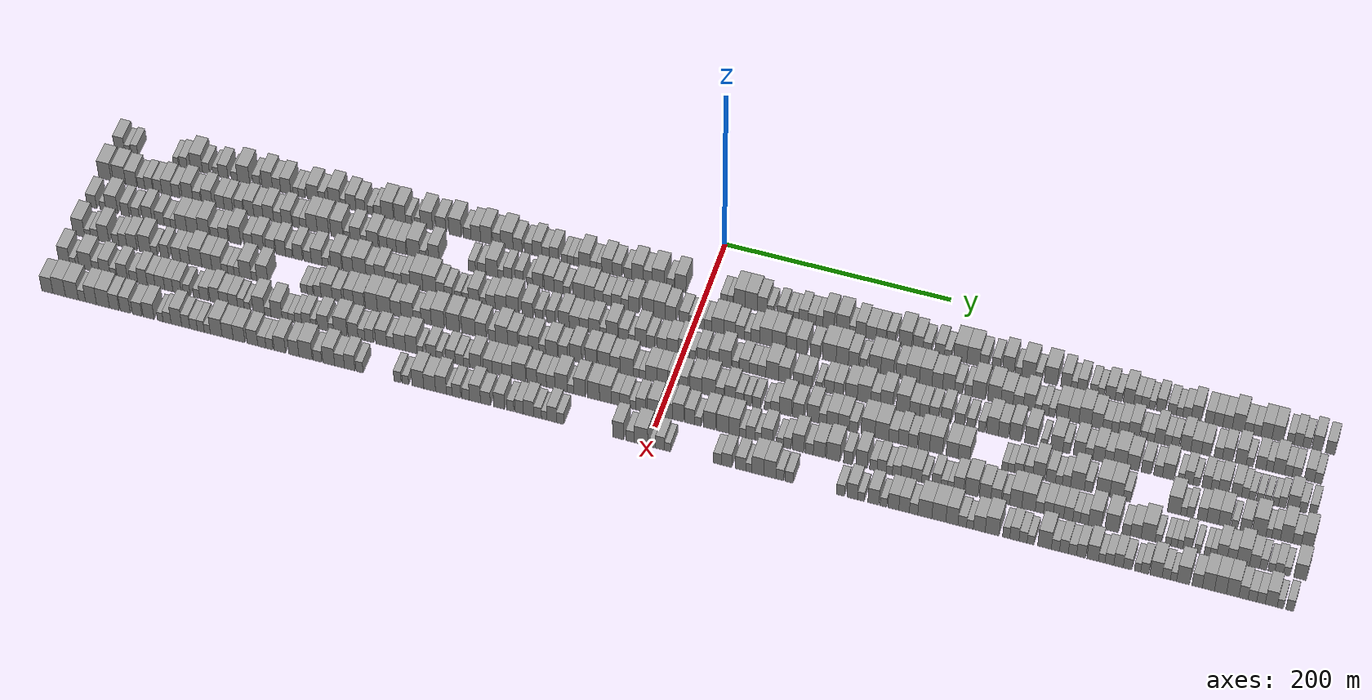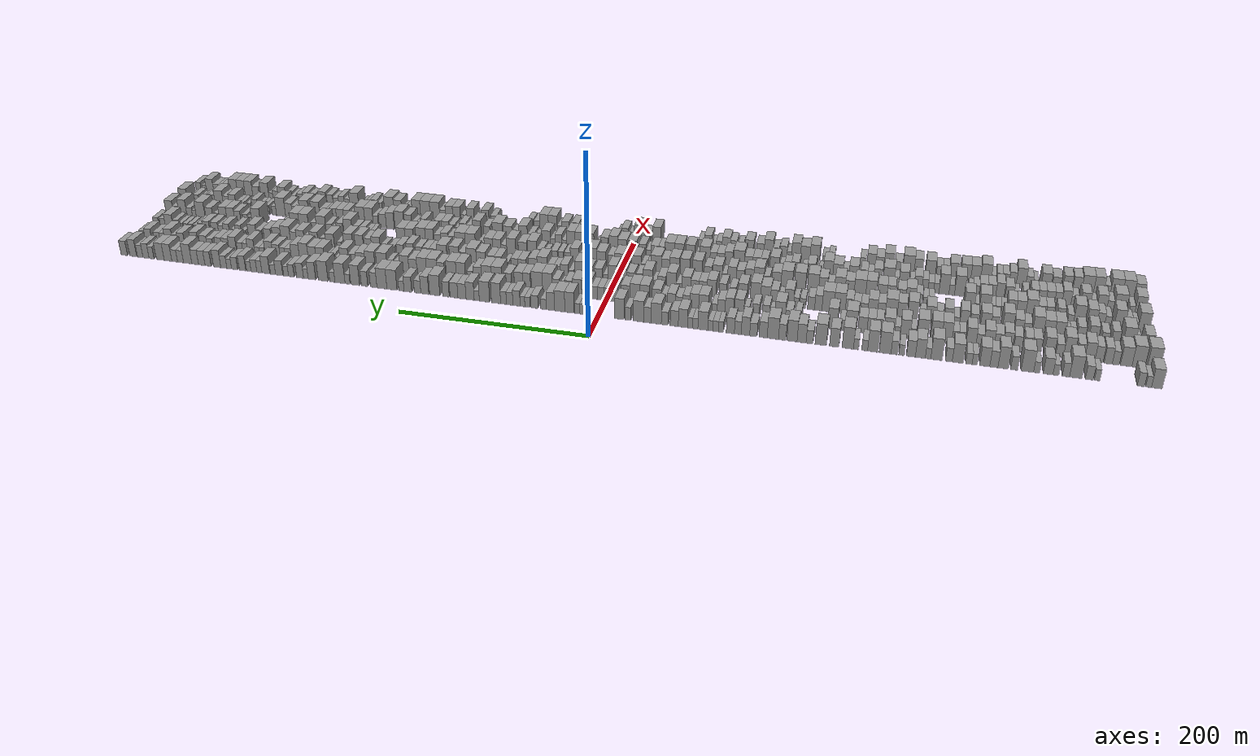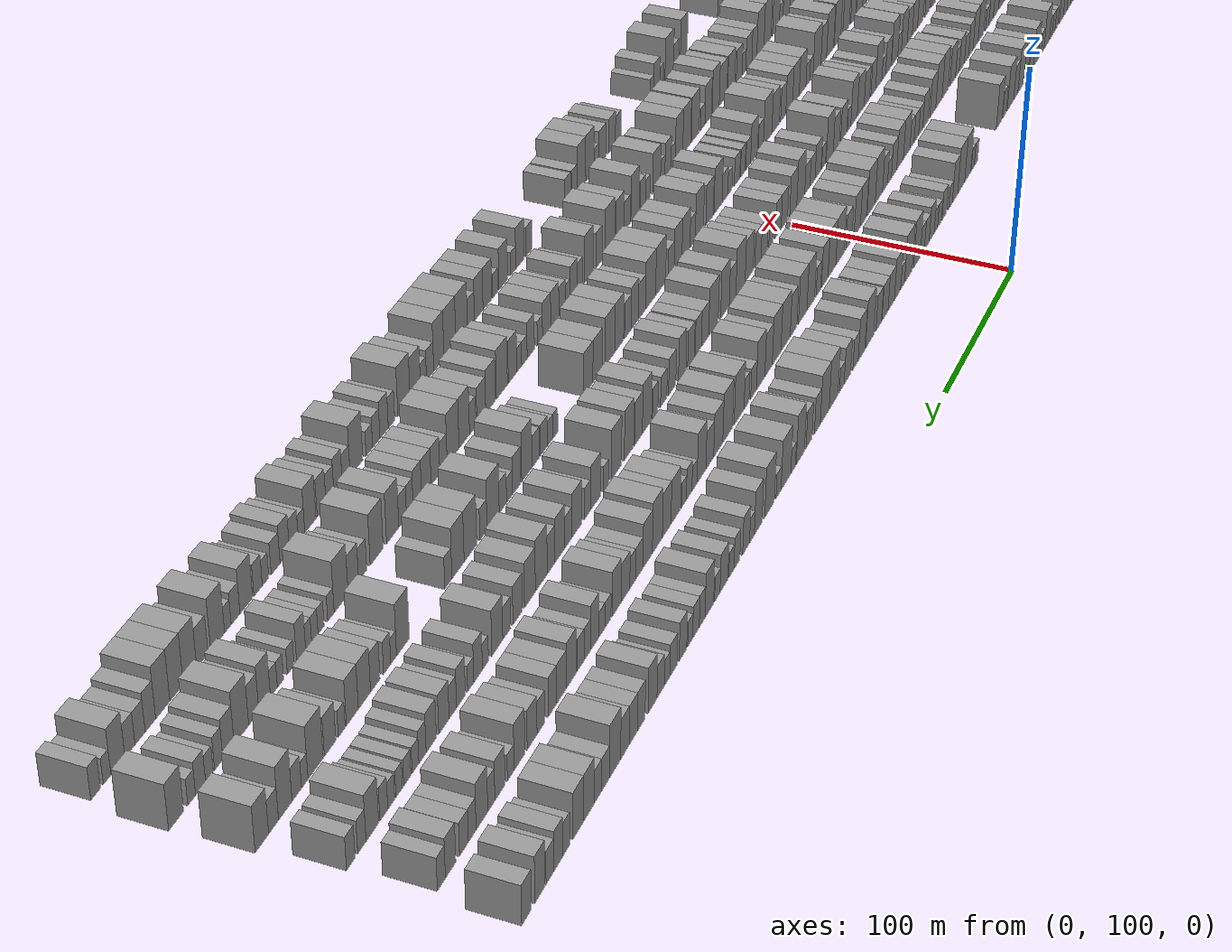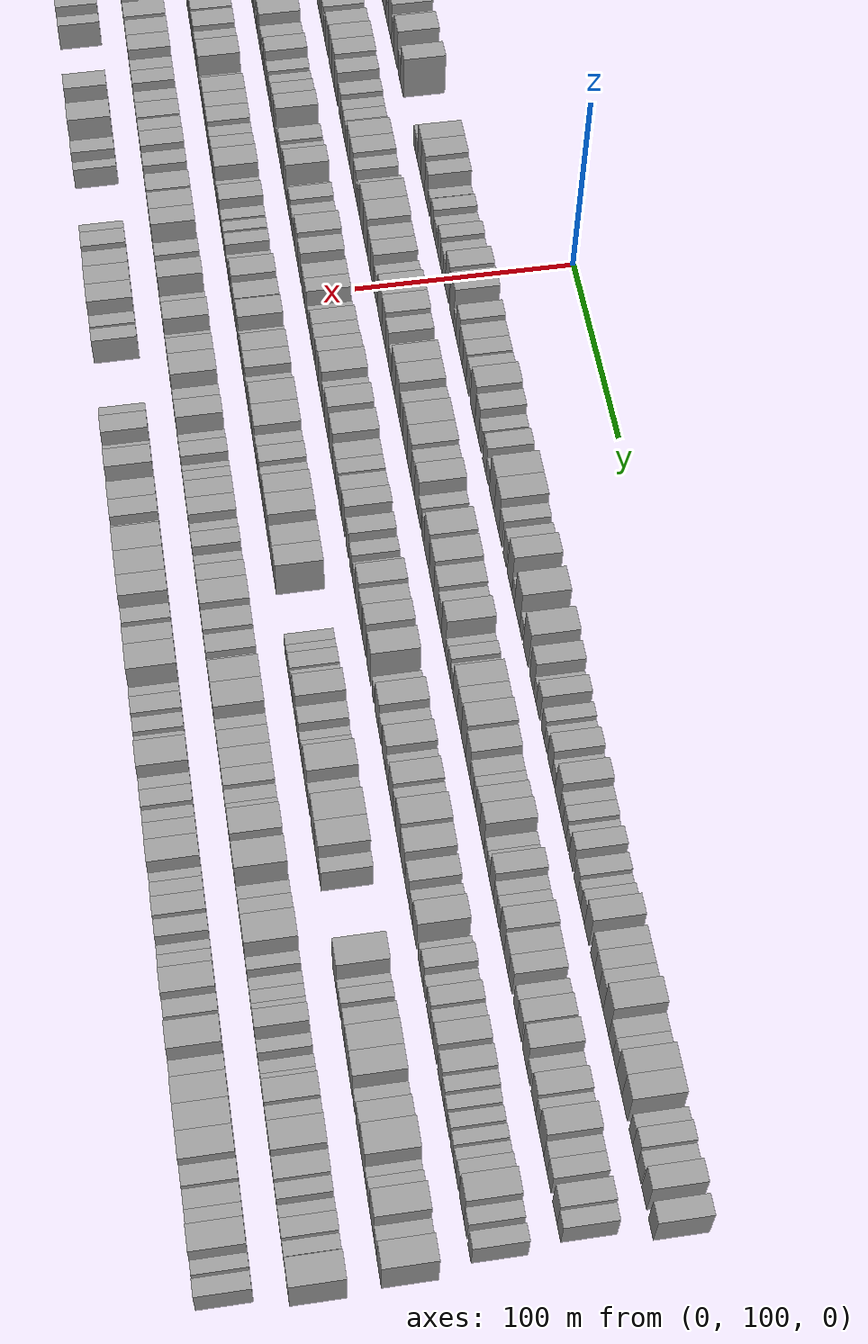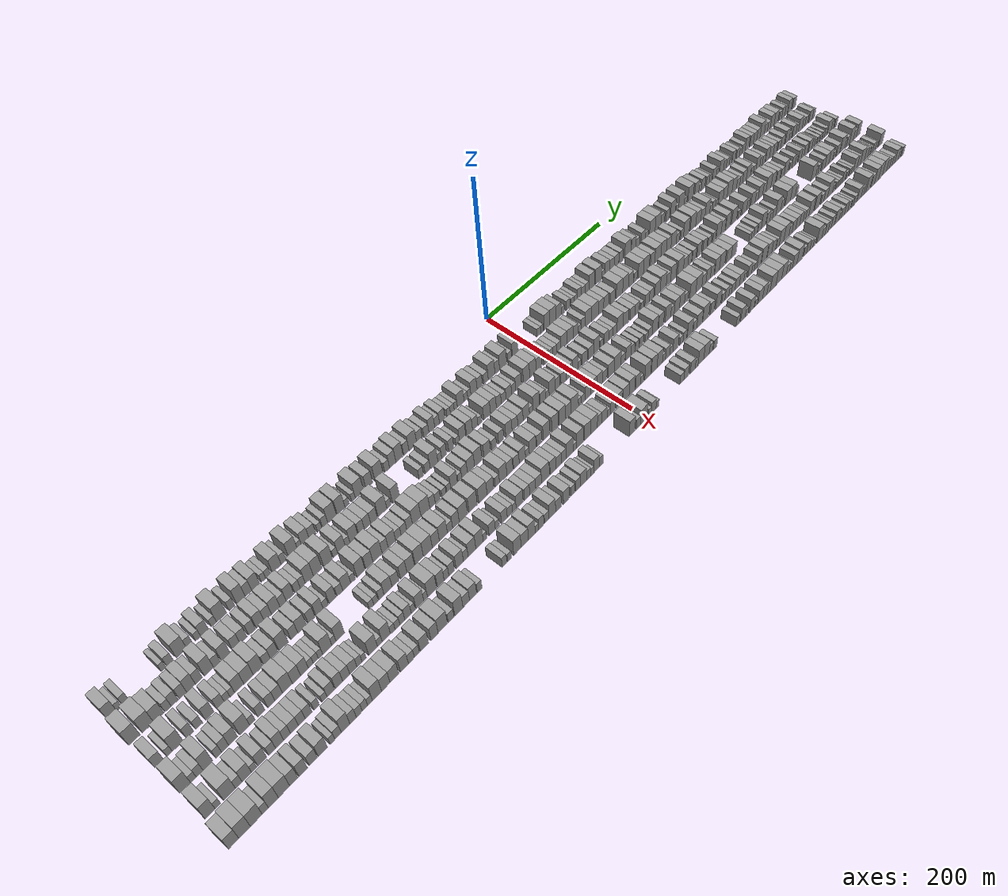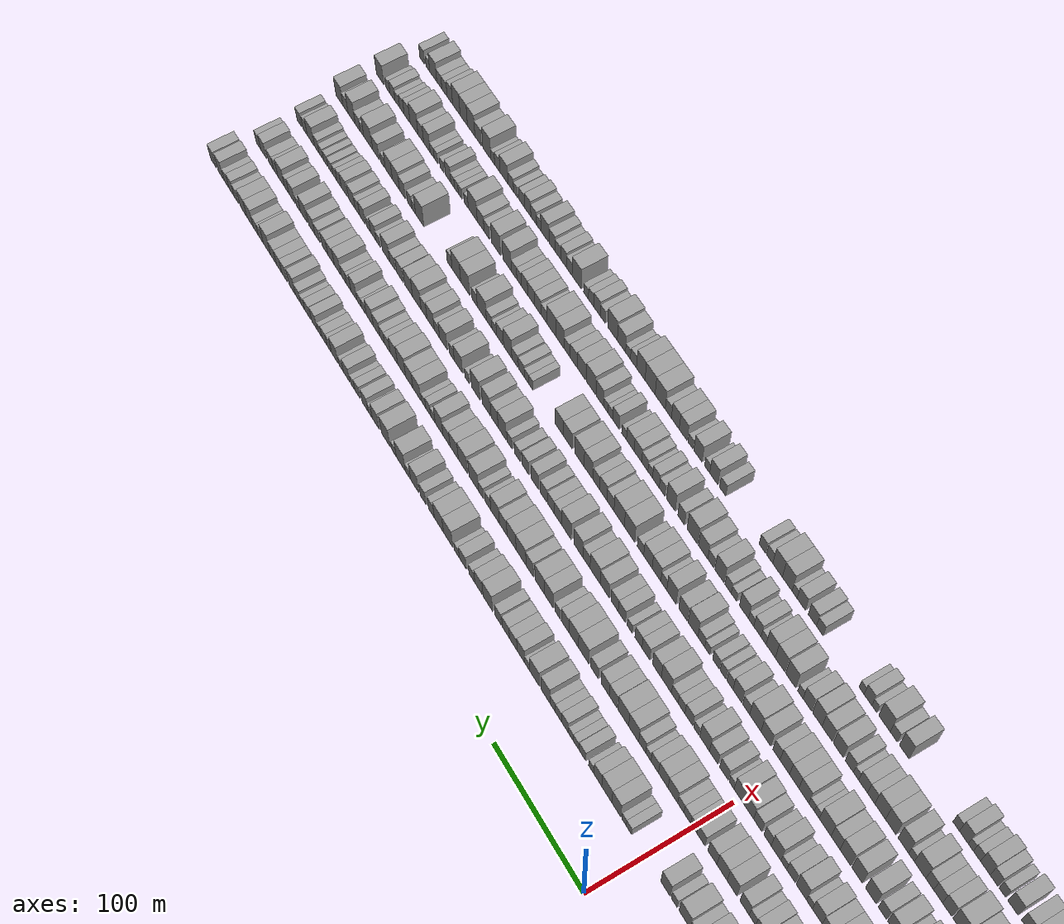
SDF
<sdf version="1.6">
 <world name="default">
  <scene>
   <sky><clouds><speed>12</speed></clouds></sky>
   <ambient>0.4 0.4 0.4 1</ambient>
   <background>0.7 0.7 0.7 1</background>
   <shadows>1</shadows>
  </scene>
  <gravity>0 0 -9.8066</gravity>
  <magnetic_field>6e-06 2.3e-05 -4.2e-05</magnetic_field>
  <physics default="0" name="default_physics" type="ode">
   <ode>
    <solver>
     <type>quick</type>
     <iters>10</iters>
     <sor>1.0</sor>
     <use_dynamic_moi_rescaling>0</use_dynamic_moi_rescaling>
    </solver>
    <constraints>
     <cfm>0</cfm>
     <erp>0.2</erp>
     <contact_max_correcting_vel>100</contact_max_correcting_vel>
     <contact_surface_layer>0.001</contact_surface_layer>
    </constraints>
   </ode>
   <max_step_size>0.004</max_step_size>
   <real_time_factor>1</real_time_factor>
   <real_time_update_rate>250</real_time_update_rate>
  </physics>
  <light name="sun" type="directional">
   <pose>0 0 10 0 0 0</pose>
   <diffuse>0.8 0.8 0.8 1</diffuse>
   <specular>0.2 0.2 0.2 1</specular>
   <attenuation>
    <range>1000</range>
    <constant>0.9</constant>
    <linear>0.01</linear>
    <quadratic>0.001</quadratic>
   </attenuation>
   <direction>-0.5 0.1 -0.9</direction>
  </light>
  <model name="building_1">
   <static>1</static>
   <pose>50.0000 -532.2511 0 0.000000 0.000000 0.000000</pose>
   <link name="link">
    <pose>0 0 10.50 0 0 0</pose>
    <collision name="collision"><geometry><box><size>20.0000 9.4978 21.0000</size></box></geometry></collision>
    <visual name="visual">
     <cast_shadows>0</cast_shadows>
     <geometry><box><size>20.0000 9.4978 21.0000</size></box></geometry>
     <material>
      <script>
       <uri>model://grey_wall/materials/scripts</uri>
       <uri>model://grey_wall/materials/textures</uri>
       <name>vrc/grey_wall</name>
      </script>
     </material>
    </visual>
   </link>
  </model>
  <model name="building_2">
   <static>1</static>
   <pose>50.0000 -525.0149 0 0.000000 0.000000 0.000000</pose>
   <link name="link">
    <pose>0 0 6.00 0 0 0</pose>
    <collision name="collision"><geometry><box><size>20.0000 4.9746 12.0000</size></box></geometry></collision>
    <visual name="visual">
     <cast_shadows>0</cast_shadows>
     <geometry><box><size>20.0000 4.9746 12.0000</size></box></geometry>
     <material>
      <script>
       <uri>model://grey_wall/materials/scripts</uri>
       <uri>model://grey_wall/materials/textures</uri>
       <name>vrc/grey_wall</name>
      </script>
     </material>
    </visual>
   </link>
  </model>
  <model name="building_3">
   <static>1</static>
   <pose>50.0000 -518.3845 0 0.000000 0.000000 0.000000</pose>
   <link name="link">
    <pose>0 0 7.50 0 0 0</pose>
    <collision name="collision"><geometry><box><size>20.0000 6.2862 15.0000</size></box></geometry></collision>
    <visual name="visual">
     <cast_shadows>0</cast_shadows>
     <geometry><box><size>20.0000 6.2862 15.0000</size></box></geometry>
     <material>
      <script>
       <uri>model://grey_wall/materials/scripts</uri>
       <uri>model://grey_wall/materials/textures</uri>
       <name>vrc/grey_wall</name>
      </script>
     </material>
    </visual>
   </link>
  </model>
  <model name="building_4">
   <static>1</static>
   <pose>50.0000 -479.9255 0 0.000000 0.000000 0.000000</pose>
   <link name="link">
    <pose>0 0 6.00 0 0 0</pose>
    <collision name="collision"><geometry><box><size>20.0000 4.8773 12.0000</size></box></geometry></collision>
    <visual name="visual">
     <cast_shadows>0</cast_shadows>
     <geometry><box><size>20.0000 4.8773 12.0000</size></box></geometry>
     <material>
      <script>
       <uri>model://grey_wall/materials/scripts</uri>
       <uri>model://grey_wall/materials/textures</uri>
       <name>vrc/grey_wall</name>
      </script>
     </material>
    </visual>
   </link>
  </model>
  <model name="building_5">
   <static>1</static>
   <pose>50.0000 -472.9560 0 0.000000 0.000000 0.000000</pose>
   <link name="link">
    <pose>0 0 7.50 0 0 0</pose>
    <collision name="collision"><geometry><box><size>20.0000 7.0617 15.0000</size></box></geometry></collision>
    <visual name="visual">
     <cast_shadows>0</cast_shadows>
     <geometry><box><size>20.0000 7.0617 15.0000</size></box></geometry>
     <material>
      <script>
       <uri>model://grey_wall/materials/scripts</uri>
       <uri>model://grey_wall/materials/textures</uri>
       <name>vrc/grey_wall</name>
      </script>
     </material>
    </visual>
   </link>
  </model>
  <model name="building_6">
   <static>1</static>
   <pose>50.0000 -460.8569 0 0.000000 0.000000 0.000000</pose>
   <link name="link">
    <pose>0 0 12.00 0 0 0</pose>
    <collision name="collision"><geometry><box><size>20.0000 11.1365 24.0000</size></box></geometry></collision>
    <visual name="visual">
     <cast_shadows>0</cast_shadows>
     <geometry><box><size>20.0000 11.1365 24.0000</size></box></geometry>
     <material>
      <script>
       <uri>model://grey_wall/materials/scripts</uri>
       <uri>model://grey_wall/materials/textures</uri>
       <name>vrc/grey_wall</name>
      </script>
     </material>
    </visual>
   </link>
  </model>
  <model name="building_7">
   <static>1</static>
   <pose>50.0000 -452.0662 0 0.000000 0.000000 0.000000</pose>
   <link name="link">
    <pose>0 0 7.50 0 0 0</pose>
    <collision name="collision"><geometry><box><size>20.0000 6.4448 15.0000</size></box></geometry></collision>
    <visual name="visual">
     <cast_shadows>0</cast_shadows>
     <geometry><box><size>20.0000 6.4448 15.0000</size></box></geometry>
     <material>
      <script>
       <uri>model://grey_wall/materials/scripts</uri>
       <uri>model://grey_wall/materials/textures</uri>
       <name>vrc/grey_wall</name>
      </script>
     </material>
    </visual>
   </link>
  </model>
  <model name="building_8">
   <static>1</static>
   <pose>50.0000 -443.1462 0 0.000000 0.000000 0.000000</pose>
   <link name="link">
    <pose>0 0 6.00 0 0 0</pose>
    <collision name="collision"><geometry><box><size>20.0000 5.3953 12.0000</size></box></geometry></collision>
    <visual name="visual">
     <cast_shadows>0</cast_shadows>
     <geometry><box><size>20.0000 5.3953 12.0000</size></box></geometry>
     <material>
      <script>
       <uri>model://grey_wall/materials/scripts</uri>
       <uri>model://grey_wall/materials/textures</uri>
       <name>vrc/grey_wall</name>
      </script>
     </material>
    </visual>
   </link>
  </model>
  <model name="building_9">
   <static>1</static>
   <pose>50.0000 -436.0758 0 0.000000 0.000000 0.000000</pose>
   <link name="link">
    <pose>0 0 9.00 0 0 0</pose>
    <collision name="collision"><geometry><box><size>20.0000 8.7456 18.0000</size></box></geometry></collision>
    <visual name="visual">
     <cast_shadows>0</cast_shadows>
     <geometry><box><size>20.0000 8.7456 18.0000</size></box></geometry>
     <material>
      <script>
       <uri>model://grey_wall/materials/scripts</uri>
       <uri>model://grey_wall/materials/textures</uri>
       <name>vrc/grey_wall</name>
      </script>
     </material>
    </visual>
   </link>
  </model>
  <model name="building_10">
   <static>1</static>
   <pose>50.0000 -425.8191 0 0.000000 0.000000 0.000000</pose>
   <link name="link">
    <pose>0 0 6.00 0 0 0</pose>
    <collision name="collision"><geometry><box><size>20.0000 5.7678 12.0000</size></box></geometry></collision>
    <visual name="visual">
     <cast_shadows>0</cast_shadows>
     <geometry><box><size>20.0000 5.7678 12.0000</size></box></geometry>
     <material>
      <script>
       <uri>model://grey_wall/materials/scripts</uri>
       <uri>model://grey_wall/materials/textures</uri>
       <name>vrc/grey_wall</name>
      </script>
     </material>
    </visual>
   </link>
  </model>
  <model name="building_11">
   <static>1</static>
   <pose>50.0000 -417.2933 0 0.000000 0.000000 0.000000</pose>
   <link name="link">
    <pose>0 0 12.00 0 0 0</pose>
    <collision name="collision"><geometry><box><size>20.0000 11.2836 24.0000</size></box></geometry></collision>
    <visual name="visual">
     <cast_shadows>0</cast_shadows>
     <geometry><box><size>20.0000 11.2836 24.0000</size></box></geometry>
     <material>
      <script>
       <uri>model://grey_wall/materials/scripts</uri>
       <uri>model://grey_wall/materials/textures</uri>
       <name>vrc/grey_wall</name>
      </script>
     </material>
    </visual>
   </link>
  </model>
  <model name="building_12">
   <static>1</static>
   <pose>50.0000 -405.4217 0 0.000000 0.000000 0.000000</pose>
   <link name="link">
    <pose>0 0 7.50 0 0 0</pose>
    <collision name="collision"><geometry><box><size>20.0000 6.4597 15.0000</size></box></geometry></collision>
    <visual name="visual">
     <cast_shadows>0</cast_shadows>
     <geometry><box><size>20.0000 6.4597 15.0000</size></box></geometry>
     <material>
      <script>
       <uri>model://grey_wall/materials/scripts</uri>
       <uri>model://grey_wall/materials/textures</uri>
       <name>vrc/grey_wall</name>
      </script>
     </material>
    </visual>
   </link>
  </model>
  <model name="building_13">
   <static>1</static>
   <pose>50.0000 -395.3495 0 0.000000 0.000000 0.000000</pose>
   <link name="link">
    <pose>0 0 12.00 0 0 0</pose>
    <collision name="collision"><geometry><box><size>20.0000 9.6846 24.0000</size></box></geometry></collision>
    <visual name="visual">
     <cast_shadows>0</cast_shadows>
     <geometry><box><size>20.0000 9.6846 24.0000</size></box></geometry>
     <material>
      <script>
       <uri>model://grey_wall/materials/scripts</uri>
       <uri>model://grey_wall/materials/textures</uri>
       <name>vrc/grey_wall</name>
      </script>
     </material>
    </visual>
   </link>
  </model>
  <model name="building_14">
   <static>1</static>
   <pose>50.0000 -386.7762 0 0.000000 0.000000 0.000000</pose>
   <link name="link">
    <pose>0 0 9.00 0 0 0</pose>
    <collision name="collision"><geometry><box><size>20.0000 7.4621 18.0000</size></box></geometry></collision>
    <visual name="visual">
     <cast_shadows>0</cast_shadows>
     <geometry><box><size>20.0000 7.4621 18.0000</size></box></geometry>
     <material>
      <script>
       <uri>model://grey_wall/materials/scripts</uri>
       <uri>model://grey_wall/materials/textures</uri>
       <name>vrc/grey_wall</name>
      </script>
     </material>
    </visual>
   </link>
  </model>
  <model name="building_15">
   <static>1</static>
   <pose>50.0000 -378.3751 0 0.000000 0.000000 0.000000</pose>
   <link name="link">
    <pose>0 0 10.50 0 0 0</pose>
    <collision name="collision"><geometry><box><size>20.0000 9.3400 21.0000</size></box></geometry></collision>
    <visual name="visual">
     <cast_shadows>0</cast_shadows>
     <geometry><box><size>20.0000 9.3400 21.0000</size></box></geometry>
     <material>
      <script>
       <uri>model://grey_wall/materials/scripts</uri>
       <uri>model://grey_wall/materials/textures</uri>
       <name>vrc/grey_wall</name>
      </script>
     </material>
    </visual>
   </link>
  </model>
  <model name="building_16">
   <static>1</static>
   <pose>50.0000 -369.2400 0 0.000000 0.000000 0.000000</pose>
   <link name="link">
    <pose>0 0 6.00 0 0 0</pose>
    <collision name="collision"><geometry><box><size>20.0000 4.9302 12.0000</size></box></geometry></collision>
    <visual name="visual">
     <cast_shadows>0</cast_shadows>
     <geometry><box><size>20.0000 4.9302 12.0000</size></box></geometry>
     <material>
      <script>
       <uri>model://grey_wall/materials/scripts</uri>
       <uri>model://grey_wall/materials/textures</uri>
       <name>vrc/grey_wall</name>
      </script>
     </material>
    </visual>
   </link>
  </model>
  <model name="building_17">
   <static>1</static>
   <pose>50.0000 -363.8167 0 0.000000 0.000000 0.000000</pose>
   <link name="link">
    <pose>0 0 6.00 0 0 0</pose>
    <collision name="collision"><geometry><box><size>20.0000 5.9164 12.0000</size></box></geometry></collision>
    <visual name="visual">
     <cast_shadows>0</cast_shadows>
     <geometry><box><size>20.0000 5.9164 12.0000</size></box></geometry>
     <material>
      <script>
       <uri>model://grey_wall/materials/scripts</uri>
       <uri>model://grey_wall/materials/textures</uri>
       <name>vrc/grey_wall</name>
      </script>
     </material>
    </visual>
   </link>
  </model>
  <model name="building_18">
   <static>1</static>
   <pose>50.0000 -353.6377 0 0.000000 0.000000 0.000000</pose>
   <link name="link">
    <pose>0 0 10.50 0 0 0</pose>
    <collision name="collision"><geometry><box><size>20.0000 10.4416 21.0000</size></box></geometry></collision>
    <visual name="visual">
     <cast_shadows>0</cast_shadows>
     <geometry><box><size>20.0000 10.4416 21.0000</size></box></geometry>
     <material>
      <script>
       <uri>model://grey_wall/materials/scripts</uri>
       <uri>model://grey_wall/materials/textures</uri>
       <name>vrc/grey_wall</name>
      </script>
     </material>
    </visual>
   </link>
  </model>
  <model name="building_19">
   <static>1</static>
   <pose>50.0000 -345.2681 0 0.000000 0.000000 0.000000</pose>
   <link name="link">
    <pose>0 0 7.50 0 0 0</pose>
    <collision name="collision"><geometry><box><size>20.0000 6.2976 15.0000</size></box></geometry></collision>
    <visual name="visual">
     <cast_shadows>0</cast_shadows>
     <geometry><box><size>20.0000 6.2976 15.0000</size></box></geometry>
     <material>
      <script>
       <uri>model://grey_wall/materials/scripts</uri>
       <uri>model://grey_wall/materials/textures</uri>
       <name>vrc/grey_wall</name>
      </script>
     </material>
    </visual>
   </link>
  </model>
  <model name="building_20">
   <static>1</static>
   <pose>50.0000 -333.7515 0 0.000000 0.000000 0.000000</pose>
   <link name="link">
    <pose>0 0 12.00 0 0 0</pose>
    <collision name="collision"><geometry><box><size>20.0000 10.7356 24.0000</size></box></geometry></collision>
    <visual name="visual">
     <cast_shadows>0</cast_shadows>
     <geometry><box><size>20.0000 10.7356 24.0000</size></box></geometry>
     <material>
      <script>
       <uri>model://grey_wall/materials/scripts</uri>
       <uri>model://grey_wall/materials/textures</uri>
       <name>vrc/grey_wall</name>
      </script>
     </material>
    </visual>
   </link>
  </model>
  <model name="building_21">
   <static>1</static>
   <pose>50.0000 -325.8226 0 0.000000 0.000000 0.000000</pose>
   <link name="link">
    <pose>0 0 6.00 0 0 0</pose>
    <collision name="collision"><geometry><box><size>20.0000 5.1222 12.0000</size></box></geometry></collision>
    <visual name="visual">
     <cast_shadows>0</cast_shadows>
     <geometry><box><size>20.0000 5.1222 12.0000</size></box></geometry>
     <material>
      <script>
       <uri>model://grey_wall/materials/scripts</uri>
       <uri>model://grey_wall/materials/textures</uri>
       <name>vrc/grey_wall</name>
      </script>
     </material>
    </visual>
   </link>
  </model>
  <model name="building_22">
   <static>1</static>
   <pose>50.0000 -318.6219 0 0.000000 0.000000 0.000000</pose>
   <link name="link">
    <pose>0 0 10.50 0 0 0</pose>
    <collision name="collision"><geometry><box><size>20.0000 9.2793 21.0000</size></box></geometry></collision>
    <visual name="visual">
     <cast_shadows>0</cast_shadows>
     <geometry><box><size>20.0000 9.2793 21.0000</size></box></geometry>
     <material>
      <script>
       <uri>model://grey_wall/materials/scripts</uri>
       <uri>model://grey_wall/materials/textures</uri>
       <name>vrc/grey_wall</name>
      </script>
     </material>
    </visual>
   </link>
  </model>
  <model name="building_23">
   <static>1</static>
   <pose>50.0000 -309.8643 0 0.000000 0.000000 0.000000</pose>
   <link name="link">
    <pose>0 0 9.00 0 0 0</pose>
    <collision name="collision"><geometry><box><size>20.0000 8.2358 18.0000</size></box></geometry></collision>
    <visual name="visual">
     <cast_shadows>0</cast_shadows>
     <geometry><box><size>20.0000 8.2358 18.0000</size></box></geometry>
     <material>
      <script>
       <uri>model://grey_wall/materials/scripts</uri>
       <uri>model://grey_wall/materials/textures</uri>
       <name>vrc/grey_wall</name>
      </script>
     </material>
    </visual>
   </link>
  </model>
  <model name="building_24">
   <static>1</static>
   <pose>50.0000 -301.0846 0 0.000000 0.000000 0.000000</pose>
   <link name="link">
    <pose>0 0 6.00 0 0 0</pose>
    <collision name="collision"><geometry><box><size>20.0000 5.3236 12.0000</size></box></geometry></collision>
    <visual name="visual">
     <cast_shadows>0</cast_shadows>
     <geometry><box><size>20.0000 5.3236 12.0000</size></box></geometry>
     <material>
      <script>
       <uri>model://grey_wall/materials/scripts</uri>
       <uri>model://grey_wall/materials/textures</uri>
       <name>vrc/grey_wall</name>
      </script>
     </material>
    </visual>
   </link>
  </model>
  <model name="building_25">
   <static>1</static>
   <pose>50.0000 -294.1895 0 0.000000 0.000000 0.000000</pose>
   <link name="link">
    <pose>0 0 7.50 0 0 0</pose>
    <collision name="collision"><geometry><box><size>20.0000 6.4666 15.0000</size></box></geometry></collision>
    <visual name="visual">
     <cast_shadows>0</cast_shadows>
     <geometry><box><size>20.0000 6.4666 15.0000</size></box></geometry>
     <material>
      <script>
       <uri>model://grey_wall/materials/scripts</uri>
       <uri>model://grey_wall/materials/textures</uri>
       <name>vrc/grey_wall</name>
      </script>
     </material>
    </visual>
   </link>
  </model>
  <model name="building_26">
   <static>1</static>
   <pose>50.0000 -285.3970 0 0.000000 0.000000 0.000000</pose>
   <link name="link">
    <pose>0 0 12.00 0 0 0</pose>
    <collision name="collision"><geometry><box><size>20.0000 11.1183 24.0000</size></box></geometry></collision>
    <visual name="visual">
     <cast_shadows>0</cast_shadows>
     <geometry><box><size>20.0000 11.1183 24.0000</size></box></geometry>
     <material>
      <script>
       <uri>model://grey_wall/materials/scripts</uri>
       <uri>model://grey_wall/materials/textures</uri>
       <name>vrc/grey_wall</name>
      </script>
     </material>
    </visual>
   </link>
  </model>
  <model name="building_27">
   <static>1</static>
   <pose>50.0000 -273.7909 0 0.000000 0.000000 0.000000</pose>
   <link name="link">
    <pose>0 0 12.00 0 0 0</pose>
    <collision name="collision"><geometry><box><size>20.0000 10.0939 24.0000</size></box></geometry></collision>
    <visual name="visual">
     <cast_shadows>0</cast_shadows>
     <geometry><box><size>20.0000 10.0939 24.0000</size></box></geometry>
     <material>
      <script>
       <uri>model://grey_wall/materials/scripts</uri>
       <uri>model://grey_wall/materials/textures</uri>
       <name>vrc/grey_wall</name>
      </script>
     </material>
    </visual>
   </link>
  </model>
  <model name="building_28">
   <static>1</static>
   <pose>50.0000 -265.9480 0 0.000000 0.000000 0.000000</pose>
   <link name="link">
    <pose>0 0 6.00 0 0 0</pose>
    <collision name="collision"><geometry><box><size>20.0000 5.5919 12.0000</size></box></geometry></collision>
    <visual name="visual">
     <cast_shadows>0</cast_shadows>
     <geometry><box><size>20.0000 5.5919 12.0000</size></box></geometry>
     <material>
      <script>
       <uri>model://grey_wall/materials/scripts</uri>
       <uri>model://grey_wall/materials/textures</uri>
       <name>vrc/grey_wall</name>
      </script>
     </material>
    </visual>
   </link>
  </model>
  <model name="building_29">
   <static>1</static>
   <pose>50.0000 -257.6963 0 0.000000 0.000000 0.000000</pose>
   <link name="link">
    <pose>0 0 6.00 0 0 0</pose>
    <collision name="collision"><geometry><box><size>20.0000 4.9115 12.0000</size></box></geometry></collision>
    <visual name="visual">
     <cast_shadows>0</cast_shadows>
     <geometry><box><size>20.0000 4.9115 12.0000</size></box></geometry>
     <material>
      <script>
       <uri>model://grey_wall/materials/scripts</uri>
       <uri>model://grey_wall/materials/textures</uri>
       <name>vrc/grey_wall</name>
      </script>
     </material>
    </visual>
   </link>
  </model>
  <model name="building_30">
   <static>1</static>
   <pose>50.0000 -249.7525 0 0.000000 0.000000 0.000000</pose>
   <link name="link">
    <pose>0 0 12.00 0 0 0</pose>
    <collision name="collision"><geometry><box><size>20.0000 10.9759 24.0000</size></box></geometry></collision>
    <visual name="visual">
     <cast_shadows>0</cast_shadows>
     <geometry><box><size>20.0000 10.9759 24.0000</size></box></geometry>
     <material>
      <script>
       <uri>model://grey_wall/materials/scripts</uri>
       <uri>model://grey_wall/materials/textures</uri>
       <name>vrc/grey_wall</name>
      </script>
     </material>
    </visual>
   </link>
  </model>
  <model name="building_31">
   <static>1</static>
   <pose>50.0000 -236.7100 0 0.000000 0.000000 0.000000</pose>
   <link name="link">
    <pose>0 0 10.50 0 0 0</pose>
    <collision name="collision"><geometry><box><size>20.0000 9.1091 21.0000</size></box></geometry></collision>
    <visual name="visual">
     <cast_shadows>0</cast_shadows>
     <geometry><box><size>20.0000 9.1091 21.0000</size></box></geometry>
     <material>
      <script>
       <uri>model://grey_wall/materials/scripts</uri>
       <uri>model://grey_wall/materials/textures</uri>
       <name>vrc/grey_wall</name>
      </script>
     </material>
    </visual>
   </link>
  </model>
  <model name="building_32">
   <static>1</static>
   <pose>50.0000 -223.6549 0 0.000000 0.000000 0.000000</pose>
   <link name="link">
    <pose>0 0 12.00 0 0 0</pose>
    <collision name="collision"><geometry><box><size>20.0000 11.0012 24.0000</size></box></geometry></collision>
    <visual name="visual">
     <cast_shadows>0</cast_shadows>
     <geometry><box><size>20.0000 11.0012 24.0000</size></box></geometry>
     <material>
      <script>
       <uri>model://grey_wall/materials/scripts</uri>
       <uri>model://grey_wall/materials/textures</uri>
       <name>vrc/grey_wall</name>
      </script>
     </material>
    </visual>
   </link>
  </model>
  <model name="building_33">
   <static>1</static>
   <pose>50.0000 -212.7712 0 0.000000 0.000000 0.000000</pose>
   <link name="link">
    <pose>0 0 7.50 0 0 0</pose>
    <collision name="collision"><geometry><box><size>20.0000 6.7662 15.0000</size></box></geometry></collision>
    <visual name="visual">
     <cast_shadows>0</cast_shadows>
     <geometry><box><size>20.0000 6.7662 15.0000</size></box></geometry>
     <material>
      <script>
       <uri>model://grey_wall/materials/scripts</uri>
       <uri>model://grey_wall/materials/textures</uri>
       <name>vrc/grey_wall</name>
      </script>
     </material>
    </visual>
   </link>
  </model>
  <model name="building_34">
   <static>1</static>
   <pose>50.0000 -205.0036 0 0.000000 0.000000 0.000000</pose>
   <link name="link">
    <pose>0 0 10.50 0 0 0</pose>
    <collision name="collision"><geometry><box><size>20.0000 8.7688 21.0000</size></box></geometry></collision>
    <visual name="visual">
     <cast_shadows>0</cast_shadows>
     <geometry><box><size>20.0000 8.7688 21.0000</size></box></geometry>
     <material>
      <script>
       <uri>model://grey_wall/materials/scripts</uri>
       <uri>model://grey_wall/materials/textures</uri>
       <name>vrc/grey_wall</name>
      </script>
     </material>
    </visual>
   </link>
  </model>
  <model name="building_35">
   <static>1</static>
   <pose>50.0000 -195.6657 0 0.000000 0.000000 0.000000</pose>
   <link name="link">
    <pose>0 0 12.00 0 0 0</pose>
    <collision name="collision"><geometry><box><size>20.0000 9.9071 24.0000</size></box></geometry></collision>
    <visual name="visual">
     <cast_shadows>0</cast_shadows>
     <geometry><box><size>20.0000 9.9071 24.0000</size></box></geometry>
     <material>
      <script>
       <uri>model://grey_wall/materials/scripts</uri>
       <uri>model://grey_wall/materials/textures</uri>
       <name>vrc/grey_wall</name>
      </script>
     </material>
    </visual>
   </link>
  </model>
  <model name="building_36">
   <static>1</static>
   <pose>50.0000 -186.0574 0 0.000000 0.000000 0.000000</pose>
   <link name="link">
    <pose>0 0 9.00 0 0 0</pose>
    <collision name="collision"><geometry><box><size>20.0000 7.3095 18.0000</size></box></geometry></collision>
    <visual name="visual">
     <cast_shadows>0</cast_shadows>
     <geometry><box><size>20.0000 7.3095 18.0000</size></box></geometry>
     <material>
      <script>
       <uri>model://grey_wall/materials/scripts</uri>
       <uri>model://grey_wall/materials/textures</uri>
       <name>vrc/grey_wall</name>
      </script>
     </material>
    </visual>
   </link>
  </model>
  <model name="building_37">
   <static>1</static>
   <pose>50.0000 -176.8570 0 0.000000 0.000000 0.000000</pose>
   <link name="link">
    <pose>0 0 12.00 0 0 0</pose>
    <collision name="collision"><geometry><box><size>20.0000 11.0913 24.0000</size></box></geometry></collision>
    <visual name="visual">
     <cast_shadows>0</cast_shadows>
     <geometry><box><size>20.0000 11.0913 24.0000</size></box></geometry>
     <material>
      <script>
       <uri>model://grey_wall/materials/scripts</uri>
       <uri>model://grey_wall/materials/textures</uri>
       <name>vrc/grey_wall</name>
      </script>
     </material>
    </visual>
   </link>
  </model>
  <model name="building_38">
   <static>1</static>
   <pose>50.0000 -167.2497 0 0.000000 0.000000 0.000000</pose>
   <link name="link">
    <pose>0 0 9.00 0 0 0</pose>
    <collision name="collision"><geometry><box><size>20.0000 8.1233 18.0000</size></box></geometry></collision>
    <visual name="visual">
     <cast_shadows>0</cast_shadows>
     <geometry><box><size>20.0000 8.1233 18.0000</size></box></geometry>
     <material>
      <script>
       <uri>model://grey_wall/materials/scripts</uri>
       <uri>model://grey_wall/materials/textures</uri>
       <name>vrc/grey_wall</name>
      </script>
     </material>
    </visual>
   </link>
  </model>
  <model name="building_39">
   <static>1</static>
   <pose>50.0000 -157.5555 0 0.000000 0.000000 0.000000</pose>
   <link name="link">
    <pose>0 0 7.50 0 0 0</pose>
    <collision name="collision"><geometry><box><size>20.0000 7.2650 15.0000</size></box></geometry></collision>
    <visual name="visual">
     <cast_shadows>0</cast_shadows>
     <geometry><box><size>20.0000 7.2650 15.0000</size></box></geometry>
     <material>
      <script>
       <uri>model://grey_wall/materials/scripts</uri>
       <uri>model://grey_wall/materials/textures</uri>
       <name>vrc/grey_wall</name>
      </script>
     </material>
    </visual>
   </link>
  </model>
  <model name="building_40">
   <static>1</static>
   <pose>50.0000 -149.7007 0 0.000000 0.000000 0.000000</pose>
   <link name="link">
    <pose>0 0 10.50 0 0 0</pose>
    <collision name="collision"><geometry><box><size>20.0000 8.4447 21.0000</size></box></geometry></collision>
    <visual name="visual">
     <cast_shadows>0</cast_shadows>
     <geometry><box><size>20.0000 8.4447 21.0000</size></box></geometry>
     <material>
      <script>
       <uri>model://grey_wall/materials/scripts</uri>
       <uri>model://grey_wall/materials/textures</uri>
       <name>vrc/grey_wall</name>
      </script>
     </material>
    </visual>
   </link>
  </model>
  <model name="building_41">
   <static>1</static>
   <pose>50.0000 -142.0611 0 0.000000 0.000000 0.000000</pose>
   <link name="link">
    <pose>0 0 7.50 0 0 0</pose>
    <collision name="collision"><geometry><box><size>20.0000 6.8345 15.0000</size></box></geometry></collision>
    <visual name="visual">
     <cast_shadows>0</cast_shadows>
     <geometry><box><size>20.0000 6.8345 15.0000</size></box></geometry>
     <material>
      <script>
       <uri>model://grey_wall/materials/scripts</uri>
       <uri>model://grey_wall/materials/textures</uri>
       <name>vrc/grey_wall</name>
      </script>
     </material>
    </visual>
   </link>
  </model>
  <model name="building_42">
   <static>1</static>
   <pose>50.0000 -134.6057 0 0.000000 0.000000 0.000000</pose>
   <link name="link">
    <pose>0 0 9.00 0 0 0</pose>
    <collision name="collision"><geometry><box><size>20.0000 8.0764 18.0000</size></box></geometry></collision>
    <visual name="visual">
     <cast_shadows>0</cast_shadows>
     <geometry><box><size>20.0000 8.0764 18.0000</size></box></geometry>
     <material>
      <script>
       <uri>model://grey_wall/materials/scripts</uri>
       <uri>model://grey_wall/materials/textures</uri>
       <name>vrc/grey_wall</name>
      </script>
     </material>
    </visual>
   </link>
  </model>
  <model name="building_43">
   <static>1</static>
   <pose>50.0000 -125.0768 0 0.000000 0.000000 0.000000</pose>
   <link name="link">
    <pose>0 0 6.00 0 0 0</pose>
    <collision name="collision"><geometry><box><size>20.0000 4.9813 12.0000</size></box></geometry></collision>
    <visual name="visual">
     <cast_shadows>0</cast_shadows>
     <geometry><box><size>20.0000 4.9813 12.0000</size></box></geometry>
     <material>
      <script>
       <uri>model://grey_wall/materials/scripts</uri>
       <uri>model://grey_wall/materials/textures</uri>
       <name>vrc/grey_wall</name>
      </script>
     </material>
    </visual>
   </link>
  </model>
  <model name="building_44">
   <static>1</static>
   <pose>50.0000 -119.7535 0 0.000000 0.000000 0.000000</pose>
   <link name="link">
    <pose>0 0 6.00 0 0 0</pose>
    <collision name="collision"><geometry><box><size>20.0000 5.6653 12.0000</size></box></geometry></collision>
    <visual name="visual">
     <cast_shadows>0</cast_shadows>
     <geometry><box><size>20.0000 5.6653 12.0000</size></box></geometry>
     <material>
      <script>
       <uri>model://grey_wall/materials/scripts</uri>
       <uri>model://grey_wall/materials/textures</uri>
       <name>vrc/grey_wall</name>
      </script>
     </material>
    </visual>
   </link>
  </model>
  <model name="building_45">
   <static>1</static>
   <pose>50.0000 -114.5015 0 0.000000 0.000000 0.000000</pose>
   <link name="link">
    <pose>0 0 6.00 0 0 0</pose>
    <collision name="collision"><geometry><box><size>20.0000 4.8387 12.0000</size></box></geometry></collision>
    <visual name="visual">
     <cast_shadows>0</cast_shadows>
     <geometry><box><size>20.0000 4.8387 12.0000</size></box></geometry>
     <material>
      <script>
       <uri>model://grey_wall/materials/scripts</uri>
       <uri>model://grey_wall/materials/textures</uri>
       <name>vrc/grey_wall</name>
      </script>
     </material>
    </visual>
   </link>
  </model>
  <model name="building_46">
   <static>1</static>
   <pose>50.0000 -107.0368 0 0.000000 0.000000 0.000000</pose>
   <link name="link">
    <pose>0 0 10.50 0 0 0</pose>
    <collision name="collision"><geometry><box><size>20.0000 10.0906 21.0000</size></box></geometry></collision>
    <visual name="visual">
     <cast_shadows>0</cast_shadows>
     <geometry><box><size>20.0000 10.0906 21.0000</size></box></geometry>
     <material>
      <script>
       <uri>model://grey_wall/materials/scripts</uri>
       <uri>model://grey_wall/materials/textures</uri>
       <name>vrc/grey_wall</name>
      </script>
     </material>
    </visual>
   </link>
  </model>
  <model name="building_47">
   <static>1</static>
   <pose>50.0000 -99.2370 0 0.000000 0.000000 0.000000</pose>
   <link name="link">
    <pose>0 0 6.00 0 0 0</pose>
    <collision name="collision"><geometry><box><size>20.0000 5.5091 12.0000</size></box></geometry></collision>
    <visual name="visual">
     <cast_shadows>0</cast_shadows>
     <geometry><box><size>20.0000 5.5091 12.0000</size></box></geometry>
     <material>
      <script>
       <uri>model://grey_wall/materials/scripts</uri>
       <uri>model://grey_wall/materials/textures</uri>
       <name>vrc/grey_wall</name>
      </script>
     </material>
    </visual>
   </link>
  </model>
  <model name="building_48">
   <static>1</static>
   <pose>50.0000 -94.0040 0 0.000000 0.000000 0.000000</pose>
   <link name="link">
    <pose>0 0 6.00 0 0 0</pose>
    <collision name="collision"><geometry><box><size>20.0000 4.9569 12.0000</size></box></geometry></collision>
    <visual name="visual">
     <cast_shadows>0</cast_shadows>
     <geometry><box><size>20.0000 4.9569 12.0000</size></box></geometry>
     <material>
      <script>
       <uri>model://grey_wall/materials/scripts</uri>
       <uri>model://grey_wall/materials/textures</uri>
       <name>vrc/grey_wall</name>
      </script>
     </material>
    </visual>
   </link>
  </model>
  <model name="building_49">
   <static>1</static>
   <pose>50.0000 -86.7960 0 0.000000 0.000000 0.000000</pose>
   <link name="link">
    <pose>0 0 10.50 0 0 0</pose>
    <collision name="collision"><geometry><box><size>20.0000 9.4590 21.0000</size></box></geometry></collision>
    <visual name="visual">
     <cast_shadows>0</cast_shadows>
     <geometry><box><size>20.0000 9.4590 21.0000</size></box></geometry>
     <material>
      <script>
       <uri>model://grey_wall/materials/scripts</uri>
       <uri>model://grey_wall/materials/textures</uri>
       <name>vrc/grey_wall</name>
      </script>
     </material>
    </visual>
   </link>
  </model>
  <model name="building_50">
   <static>1</static>
   <pose>50.0000 -77.9590 0 0.000000 0.000000 0.000000</pose>
   <link name="link">
    <pose>0 0 9.00 0 0 0</pose>
    <collision name="collision"><geometry><box><size>20.0000 8.2149 18.0000</size></box></geometry></collision>
    <visual name="visual">
     <cast_shadows>0</cast_shadows>
     <geometry><box><size>20.0000 8.2149 18.0000</size></box></geometry>
     <material>
      <script>
       <uri>model://grey_wall/materials/scripts</uri>
       <uri>model://grey_wall/materials/textures</uri>
       <name>vrc/grey_wall</name>
      </script>
     </material>
    </visual>
   </link>
  </model>
  <model name="building_51">
   <static>1</static>
   <pose>50.0000 -68.3012 0 0.000000 0.000000 0.000000</pose>
   <link name="link">
    <pose>0 0 7.50 0 0 0</pose>
    <collision name="collision"><geometry><box><size>20.0000 7.1007 15.0000</size></box></geometry></collision>
    <visual name="visual">
     <cast_shadows>0</cast_shadows>
     <geometry><box><size>20.0000 7.1007 15.0000</size></box></geometry>
     <material>
      <script>
       <uri>model://grey_wall/materials/scripts</uri>
       <uri>model://grey_wall/materials/textures</uri>
       <name>vrc/grey_wall</name>
      </script>
     </material>
    </visual>
   </link>
  </model>
  <model name="building_52">
   <static>1</static>
   <pose>50.0000 -59.5511 0 0.000000 0.000000 0.000000</pose>
   <link name="link">
    <pose>0 0 12.00 0 0 0</pose>
    <collision name="collision"><geometry><box><size>20.0000 10.3995 24.0000</size></box></geometry></collision>
    <visual name="visual">
     <cast_shadows>0</cast_shadows>
     <geometry><box><size>20.0000 10.3995 24.0000</size></box></geometry>
     <material>
      <script>
       <uri>model://grey_wall/materials/scripts</uri>
       <uri>model://grey_wall/materials/textures</uri>
       <name>vrc/grey_wall</name>
      </script>
     </material>
    </visual>
   </link>
  </model>
  <model name="building_53">
   <static>1</static>
   <pose>50.0000 -50.6286 0 0.000000 0.000000 0.000000</pose>
   <link name="link">
    <pose>0 0 9.00 0 0 0</pose>
    <collision name="collision"><geometry><box><size>20.0000 7.4455 18.0000</size></box></geometry></collision>
    <visual name="visual">
     <cast_shadows>0</cast_shadows>
     <geometry><box><size>20.0000 7.4455 18.0000</size></box></geometry>
     <material>
      <script>
       <uri>model://grey_wall/materials/scripts</uri>
       <uri>model://grey_wall/materials/textures</uri>
       <name>vrc/grey_wall</name>
      </script>
     </material>
    </visual>
   </link>
  </model>
  <model name="building_54">
   <static>1</static>
   <pose>50.0000 -41.2096 0 0.000000 0.000000 0.000000</pose>
   <link name="link">
    <pose>0 0 12.00 0 0 0</pose>
    <collision name="collision"><geometry><box><size>20.0000 11.3924 24.0000</size></box></geometry></collision>
    <visual name="visual">
     <cast_shadows>0</cast_shadows>
     <geometry><box><size>20.0000 11.3924 24.0000</size></box></geometry>
     <material>
      <script>
       <uri>model://grey_wall/materials/scripts</uri>
       <uri>model://grey_wall/materials/textures</uri>
       <name>vrc/grey_wall</name>
      </script>
     </material>
    </visual>
   </link>
  </model>
  <model name="building_55">
   <static>1</static>
   <pose>50.0000 -30.4210 0 0.000000 0.000000 0.000000</pose>
   <link name="link">
    <pose>0 0 7.50 0 0 0</pose>
    <collision name="collision"><geometry><box><size>20.0000 6.1848 15.0000</size></box></geometry></collision>
    <visual name="visual">
     <cast_shadows>0</cast_shadows>
     <geometry><box><size>20.0000 6.1848 15.0000</size></box></geometry>
     <material>
      <script>
       <uri>model://grey_wall/materials/scripts</uri>
       <uri>model://grey_wall/materials/textures</uri>
       <name>vrc/grey_wall</name>
      </script>
     </material>
    </visual>
   </link>
  </model>
  <model name="building_56">
   <static>1</static>
   <pose>50.0000 -21.4422 0 0.000000 0.000000 0.000000</pose>
   <link name="link">
    <pose>0 0 12.00 0 0 0</pose>
    <collision name="collision"><geometry><box><size>20.0000 9.7727 24.0000</size></box></geometry></collision>
    <visual name="visual">
     <cast_shadows>0</cast_shadows>
     <geometry><box><size>20.0000 9.7727 24.0000</size></box></geometry>
     <material>
      <script>
       <uri>model://grey_wall/materials/scripts</uri>
       <uri>model://grey_wall/materials/textures</uri>
       <name>vrc/grey_wall</name>
      </script>
     </material>
    </visual>
   </link>
  </model>
  <model name="building_57">
   <static>1</static>
   <pose>50.0000 17.2254 0 0.000000 0.000000 0.000000</pose>
   <link name="link">
    <pose>0 0 6.00 0 0 0</pose>
    <collision name="collision"><geometry><box><size>20.0000 5.8542 12.0000</size></box></geometry></collision>
    <visual name="visual">
     <cast_shadows>0</cast_shadows>
     <geometry><box><size>20.0000 5.8542 12.0000</size></box></geometry>
     <material>
      <script>
       <uri>model://grey_wall/materials/scripts</uri>
       <uri>model://grey_wall/materials/textures</uri>
       <name>vrc/grey_wall</name>
      </script>
     </material>
    </visual>
   </link>
  </model>
  <model name="building_58">
   <static>1</static>
   <pose>50.0000 22.6126 0 0.000000 0.000000 0.000000</pose>
   <link name="link">
    <pose>0 0 6.00 0 0 0</pose>
    <collision name="collision"><geometry><box><size>20.0000 4.9204 12.0000</size></box></geometry></collision>
    <visual name="visual">
     <cast_shadows>0</cast_shadows>
     <geometry><box><size>20.0000 4.9204 12.0000</size></box></geometry>
     <material>
      <script>
       <uri>model://grey_wall/materials/scripts</uri>
       <uri>model://grey_wall/materials/textures</uri>
       <name>vrc/grey_wall</name>
      </script>
     </material>
    </visual>
   </link>
  </model>
  <model name="building_59">
   <static>1</static>
   <pose>50.0000 30.8937 0 0.000000 0.000000 0.000000</pose>
   <link name="link">
    <pose>0 0 12.00 0 0 0</pose>
    <collision name="collision"><geometry><box><size>20.0000 9.6418 24.0000</size></box></geometry></collision>
    <visual name="visual">
     <cast_shadows>0</cast_shadows>
     <geometry><box><size>20.0000 9.6418 24.0000</size></box></geometry>
     <material>
      <script>
       <uri>model://grey_wall/materials/scripts</uri>
       <uri>model://grey_wall/materials/textures</uri>
       <name>vrc/grey_wall</name>
      </script>
     </material>
    </visual>
   </link>
  </model>
  <model name="building_60">
   <static>1</static>
   <pose>50.0000 41.2207 0 0.000000 0.000000 0.000000</pose>
   <link name="link">
    <pose>0 0 12.00 0 0 0</pose>
    <collision name="collision"><geometry><box><size>20.0000 11.0123 24.0000</size></box></geometry></collision>
    <visual name="visual">
     <cast_shadows>0</cast_shadows>
     <geometry><box><size>20.0000 11.0123 24.0000</size></box></geometry>
     <material>
      <script>
       <uri>model://grey_wall/materials/scripts</uri>
       <uri>model://grey_wall/materials/textures</uri>
       <name>vrc/grey_wall</name>
      </script>
     </material>
    </visual>
   </link>
  </model>
  <model name="building_61">
   <static>1</static>
   <pose>50.0000 51.0262 0 0.000000 0.000000 0.000000</pose>
   <link name="link">
    <pose>0 0 10.50 0 0 0</pose>
    <collision name="collision"><geometry><box><size>20.0000 8.5987 21.0000</size></box></geometry></collision>
    <visual name="visual">
     <cast_shadows>0</cast_shadows>
     <geometry><box><size>20.0000 8.5987 21.0000</size></box></geometry>
     <material>
      <script>
       <uri>model://grey_wall/materials/scripts</uri>
       <uri>model://grey_wall/materials/textures</uri>
       <name>vrc/grey_wall</name>
      </script>
     </material>
    </visual>
   </link>
  </model>
  <model name="building_62">
   <static>1</static>
   <pose>50.0000 58.2653 0 0.000000 0.000000 0.000000</pose>
   <link name="link">
    <pose>0 0 6.00 0 0 0</pose>
    <collision name="collision"><geometry><box><size>20.0000 5.8794 12.0000</size></box></geometry></collision>
    <visual name="visual">
     <cast_shadows>0</cast_shadows>
     <geometry><box><size>20.0000 5.8794 12.0000</size></box></geometry>
     <material>
      <script>
       <uri>model://grey_wall/materials/scripts</uri>
       <uri>model://grey_wall/materials/textures</uri>
       <name>vrc/grey_wall</name>
      </script>
     </material>
    </visual>
   </link>
  </model>
  <model name="building_63">
   <static>1</static>
   <pose>50.0000 67.8805 0 0.000000 0.000000 0.000000</pose>
   <link name="link">
    <pose>0 0 7.50 0 0 0</pose>
    <collision name="collision"><geometry><box><size>20.0000 7.3510 15.0000</size></box></geometry></collision>
    <visual name="visual">
     <cast_shadows>0</cast_shadows>
     <geometry><box><size>20.0000 7.3510 15.0000</size></box></geometry>
     <material>
      <script>
       <uri>model://grey_wall/materials/scripts</uri>
       <uri>model://grey_wall/materials/textures</uri>
       <name>vrc/grey_wall</name>
      </script>
     </material>
    </visual>
   </link>
  </model>
  <model name="building_64">
   <static>1</static>
   <pose>50.0000 75.4404 0 0.000000 0.000000 0.000000</pose>
   <link name="link">
    <pose>0 0 6.00 0 0 0</pose>
    <collision name="collision"><geometry><box><size>20.0000 5.7688 12.0000</size></box></geometry></collision>
    <visual name="visual">
     <cast_shadows>0</cast_shadows>
     <geometry><box><size>20.0000 5.7688 12.0000</size></box></geometry>
     <material>
      <script>
       <uri>model://grey_wall/materials/scripts</uri>
       <uri>model://grey_wall/materials/textures</uri>
       <name>vrc/grey_wall</name>
      </script>
     </material>
    </visual>
   </link>
  </model>
  <model name="building_65">
   <static>1</static>
   <pose>50.0000 80.8665 0 0.000000 0.000000 0.000000</pose>
   <link name="link">
    <pose>0 0 6.00 0 0 0</pose>
    <collision name="collision"><geometry><box><size>20.0000 5.0833 12.0000</size></box></geometry></collision>
    <visual name="visual">
     <cast_shadows>0</cast_shadows>
     <geometry><box><size>20.0000 5.0833 12.0000</size></box></geometry>
     <material>
      <script>
       <uri>model://grey_wall/materials/scripts</uri>
       <uri>model://grey_wall/materials/textures</uri>
       <name>vrc/grey_wall</name>
      </script>
     </material>
    </visual>
   </link>
  </model>
  <model name="building_66">
   <static>1</static>
   <pose>50.0000 87.2986 0 0.000000 0.000000 0.000000</pose>
   <link name="link">
    <pose>0 0 9.00 0 0 0</pose>
    <collision name="collision"><geometry><box><size>20.0000 7.7810 18.0000</size></box></geometry></collision>
    <visual name="visual">
     <cast_shadows>0</cast_shadows>
     <geometry><box><size>20.0000 7.7810 18.0000</size></box></geometry>
     <material>
      <script>
       <uri>model://grey_wall/materials/scripts</uri>
       <uri>model://grey_wall/materials/textures</uri>
       <name>vrc/grey_wall</name>
      </script>
     </material>
    </visual>
   </link>
  </model>
  <model name="building_67">
   <static>1</static>
   <pose>50.0000 94.6754 0 0.000000 0.000000 0.000000</pose>
   <link name="link">
    <pose>0 0 7.50 0 0 0</pose>
    <collision name="collision"><geometry><box><size>20.0000 6.9725 15.0000</size></box></geometry></collision>
    <visual name="visual">
     <cast_shadows>0</cast_shadows>
     <geometry><box><size>20.0000 6.9725 15.0000</size></box></geometry>
     <material>
      <script>
       <uri>model://grey_wall/materials/scripts</uri>
       <uri>model://grey_wall/materials/textures</uri>
       <name>vrc/grey_wall</name>
      </script>
     </material>
    </visual>
   </link>
  </model>
  <model name="building_68">
   <static>1</static>
   <pose>50.0000 101.3077 0 0.000000 0.000000 0.000000</pose>
   <link name="link">
    <pose>0 0 7.50 0 0 0</pose>
    <collision name="collision"><geometry><box><size>20.0000 6.2923 15.0000</size></box></geometry></collision>
    <visual name="visual">
     <cast_shadows>0</cast_shadows>
     <geometry><box><size>20.0000 6.2923 15.0000</size></box></geometry>
     <material>
      <script>
       <uri>model://grey_wall/materials/scripts</uri>
       <uri>model://grey_wall/materials/textures</uri>
       <name>vrc/grey_wall</name>
      </script>
     </material>
    </visual>
   </link>
  </model>
  <model name="building_69">
   <static>1</static>
   <pose>50.0000 109.4048 0 0.000000 0.000000 0.000000</pose>
   <link name="link">
    <pose>0 0 12.00 0 0 0</pose>
    <collision name="collision"><geometry><box><size>20.0000 9.9018 24.0000</size></box></geometry></collision>
    <visual name="visual">
     <cast_shadows>0</cast_shadows>
     <geometry><box><size>20.0000 9.9018 24.0000</size></box></geometry>
     <material>
      <script>
       <uri>model://grey_wall/materials/scripts</uri>
       <uri>model://grey_wall/materials/textures</uri>
       <name>vrc/grey_wall</name>
      </script>
     </material>
    </visual>
   </link>
  </model>
  <model name="building_70">
   <static>1</static>
   <pose>50.0000 121.9575 0 0.000000 0.000000 0.000000</pose>
   <link name="link">
    <pose>0 0 12.00 0 0 0</pose>
    <collision name="collision"><geometry><box><size>20.0000 11.2036 24.0000</size></box></geometry></collision>
    <visual name="visual">
     <cast_shadows>0</cast_shadows>
     <geometry><box><size>20.0000 11.2036 24.0000</size></box></geometry>
     <material>
      <script>
       <uri>model://grey_wall/materials/scripts</uri>
       <uri>model://grey_wall/materials/textures</uri>
       <name>vrc/grey_wall</name>
      </script>
     </material>
    </visual>
   </link>
  </model>
  <model name="building_71">
   <static>1</static>
   <pose>50.0000 130.3569 0 0.000000 0.000000 0.000000</pose>
   <link name="link">
    <pose>0 0 6.00 0 0 0</pose>
    <collision name="collision"><geometry><box><size>20.0000 5.5951 12.0000</size></box></geometry></collision>
    <visual name="visual">
     <cast_shadows>0</cast_shadows>
     <geometry><box><size>20.0000 5.5951 12.0000</size></box></geometry>
     <material>
      <script>
       <uri>model://grey_wall/materials/scripts</uri>
       <uri>model://grey_wall/materials/textures</uri>
       <name>vrc/grey_wall</name>
      </script>
     </material>
    </visual>
   </link>
  </model>
  <model name="building_72">
   <static>1</static>
   <pose>50.0000 137.6327 0 0.000000 0.000000 0.000000</pose>
   <link name="link">
    <pose>0 0 10.50 0 0 0</pose>
    <collision name="collision"><geometry><box><size>20.0000 8.9564 21.0000</size></box></geometry></collision>
    <visual name="visual">
     <cast_shadows>0</cast_shadows>
     <geometry><box><size>20.0000 8.9564 21.0000</size></box></geometry>
     <material>
      <script>
       <uri>model://grey_wall/materials/scripts</uri>
       <uri>model://grey_wall/materials/textures</uri>
       <name>vrc/grey_wall</name>
      </script>
     </material>
    </visual>
   </link>
  </model>
  <model name="building_73">
   <static>1</static>
   <pose>50.0000 146.5705 0 0.000000 0.000000 0.000000</pose>
   <link name="link">
    <pose>0 0 9.00 0 0 0</pose>
    <collision name="collision"><geometry><box><size>20.0000 8.9193 18.0000</size></box></geometry></collision>
    <visual name="visual">
     <cast_shadows>0</cast_shadows>
     <geometry><box><size>20.0000 8.9193 18.0000</size></box></geometry>
     <material>
      <script>
       <uri>model://grey_wall/materials/scripts</uri>
       <uri>model://grey_wall/materials/textures</uri>
       <name>vrc/grey_wall</name>
      </script>
     </material>
    </visual>
   </link>
  </model>
  <model name="building_74">
   <static>1</static>
   <pose>50.0000 155.3008 0 0.000000 0.000000 0.000000</pose>
   <link name="link">
    <pose>0 0 9.00 0 0 0</pose>
    <collision name="collision"><geometry><box><size>20.0000 8.5412 18.0000</size></box></geometry></collision>
    <visual name="visual">
     <cast_shadows>0</cast_shadows>
     <geometry><box><size>20.0000 8.5412 18.0000</size></box></geometry>
     <material>
      <script>
       <uri>model://grey_wall/materials/scripts</uri>
       <uri>model://grey_wall/materials/textures</uri>
       <name>vrc/grey_wall</name>
      </script>
     </material>
    </visual>
   </link>
  </model>
  <model name="building_75">
   <static>1</static>
   <pose>50.0000 164.2473 0 0.000000 0.000000 0.000000</pose>
   <link name="link">
    <pose>0 0 9.00 0 0 0</pose>
    <collision name="collision"><geometry><box><size>20.0000 7.3519 18.0000</size></box></geometry></collision>
    <visual name="visual">
     <cast_shadows>0</cast_shadows>
     <geometry><box><size>20.0000 7.3519 18.0000</size></box></geometry>
     <material>
      <script>
       <uri>model://grey_wall/materials/scripts</uri>
       <uri>model://grey_wall/materials/textures</uri>
       <name>vrc/grey_wall</name>
      </script>
     </material>
    </visual>
   </link>
  </model>
  <model name="building_76">
   <static>1</static>
   <pose>50.0000 176.5852 0 0.000000 0.000000 0.000000</pose>
   <link name="link">
    <pose>0 0 12.00 0 0 0</pose>
    <collision name="collision"><geometry><box><size>20.0000 11.3239 24.0000</size></box></geometry></collision>
    <visual name="visual">
     <cast_shadows>0</cast_shadows>
     <geometry><box><size>20.0000 11.3239 24.0000</size></box></geometry>
     <material>
      <script>
       <uri>model://grey_wall/materials/scripts</uri>
       <uri>model://grey_wall/materials/textures</uri>
       <name>vrc/grey_wall</name>
      </script>
     </material>
    </visual>
   </link>
  </model>
  <model name="building_77">
   <static>1</static>
   <pose>50.0000 187.6508 0 0.000000 0.000000 0.000000</pose>
   <link name="link">
    <pose>0 0 10.50 0 0 0</pose>
    <collision name="collision"><geometry><box><size>20.0000 8.8072 21.0000</size></box></geometry></collision>
    <visual name="visual">
     <cast_shadows>0</cast_shadows>
     <geometry><box><size>20.0000 8.8072 21.0000</size></box></geometry>
     <material>
      <script>
       <uri>model://grey_wall/materials/scripts</uri>
       <uri>model://grey_wall/materials/textures</uri>
       <name>vrc/grey_wall</name>
      </script>
     </material>
    </visual>
   </link>
  </model>
  <model name="building_78">
   <static>1</static>
   <pose>50.0000 195.6597 0 0.000000 0.000000 0.000000</pose>
   <link name="link">
    <pose>0 0 7.50 0 0 0</pose>
    <collision name="collision"><geometry><box><size>20.0000 7.2107 15.0000</size></box></geometry></collision>
    <visual name="visual">
     <cast_shadows>0</cast_shadows>
     <geometry><box><size>20.0000 7.2107 15.0000</size></box></geometry>
     <material>
      <script>
       <uri>model://grey_wall/materials/scripts</uri>
       <uri>model://grey_wall/materials/textures</uri>
       <name>vrc/grey_wall</name>
      </script>
     </material>
    </visual>
   </link>
  </model>
  <model name="building_79">
   <static>1</static>
   <pose>50.0000 206.5224 0 0.000000 0.000000 0.000000</pose>
   <link name="link">
    <pose>0 0 9.00 0 0 0</pose>
    <collision name="collision"><geometry><box><size>20.0000 8.5146 18.0000</size></box></geometry></collision>
    <visual name="visual">
     <cast_shadows>0</cast_shadows>
     <geometry><box><size>20.0000 8.5146 18.0000</size></box></geometry>
     <material>
      <script>
       <uri>model://grey_wall/materials/scripts</uri>
       <uri>model://grey_wall/materials/textures</uri>
       <name>vrc/grey_wall</name>
      </script>
     </material>
    </visual>
   </link>
  </model>
  <model name="building_80">
   <static>1</static>
   <pose>50.0000 213.7681 0 0.000000 0.000000 0.000000</pose>
   <link name="link">
    <pose>0 0 6.00 0 0 0</pose>
    <collision name="collision"><geometry><box><size>20.0000 5.9770 12.0000</size></box></geometry></collision>
    <visual name="visual">
     <cast_shadows>0</cast_shadows>
     <geometry><box><size>20.0000 5.9770 12.0000</size></box></geometry>
     <material>
      <script>
       <uri>model://grey_wall/materials/scripts</uri>
       <uri>model://grey_wall/materials/textures</uri>
       <name>vrc/grey_wall</name>
      </script>
     </material>
    </visual>
   </link>
  </model>
  <model name="building_81">
   <static>1</static>
   <pose>50.0000 224.4582 0 0.000000 0.000000 0.000000</pose>
   <link name="link">
    <pose>0 0 12.00 0 0 0</pose>
    <collision name="collision"><geometry><box><size>20.0000 11.4031 24.0000</size></box></geometry></collision>
    <visual name="visual">
     <cast_shadows>0</cast_shadows>
     <geometry><box><size>20.0000 11.4031 24.0000</size></box></geometry>
     <material>
      <script>
       <uri>model://grey_wall/materials/scripts</uri>
       <uri>model://grey_wall/materials/textures</uri>
       <name>vrc/grey_wall</name>
      </script>
     </material>
    </visual>
   </link>
  </model>
  <model name="building_82">
   <static>1</static>
   <pose>50.0000 235.7832 0 0.000000 0.000000 0.000000</pose>
   <link name="link">
    <pose>0 0 12.00 0 0 0</pose>
    <collision name="collision"><geometry><box><size>20.0000 11.2469 24.0000</size></box></geometry></collision>
    <visual name="visual">
     <cast_shadows>0</cast_shadows>
     <geometry><box><size>20.0000 11.2469 24.0000</size></box></geometry>
     <material>
      <script>
       <uri>model://grey_wall/materials/scripts</uri>
       <uri>model://grey_wall/materials/textures</uri>
       <name>vrc/grey_wall</name>
      </script>
     </material>
    </visual>
   </link>
  </model>
  <model name="building_83">
   <static>1</static>
   <pose>50.0000 245.1060 0 0.000000 0.000000 0.000000</pose>
   <link name="link">
    <pose>0 0 9.00 0 0 0</pose>
    <collision name="collision"><geometry><box><size>20.0000 7.3986 18.0000</size></box></geometry></collision>
    <visual name="visual">
     <cast_shadows>0</cast_shadows>
     <geometry><box><size>20.0000 7.3986 18.0000</size></box></geometry>
     <material>
      <script>
       <uri>model://grey_wall/materials/scripts</uri>
       <uri>model://grey_wall/materials/textures</uri>
       <name>vrc/grey_wall</name>
      </script>
     </material>
    </visual>
   </link>
  </model>
  <model name="building_84">
   <static>1</static>
   <pose>50.0000 255.4422 0 0.000000 0.000000 0.000000</pose>
   <link name="link">
    <pose>0 0 9.00 0 0 0</pose>
    <collision name="collision"><geometry><box><size>20.0000 7.2738 18.0000</size></box></geometry></collision>
    <visual name="visual">
     <cast_shadows>0</cast_shadows>
     <geometry><box><size>20.0000 7.2738 18.0000</size></box></geometry>
     <material>
      <script>
       <uri>model://grey_wall/materials/scripts</uri>
       <uri>model://grey_wall/materials/textures</uri>
       <name>vrc/grey_wall</name>
      </script>
     </material>
    </visual>
   </link>
  </model>
  <model name="building_85">
   <static>1</static>
   <pose>50.0000 266.0842 0 0.000000 0.000000 0.000000</pose>
   <link name="link">
    <pose>0 0 12.00 0 0 0</pose>
    <collision name="collision"><geometry><box><size>20.0000 10.0101 24.0000</size></box></geometry></collision>
    <visual name="visual">
     <cast_shadows>0</cast_shadows>
     <geometry><box><size>20.0000 10.0101 24.0000</size></box></geometry>
     <material>
      <script>
       <uri>model://grey_wall/materials/scripts</uri>
       <uri>model://grey_wall/materials/textures</uri>
       <name>vrc/grey_wall</name>
      </script>
     </material>
    </visual>
   </link>
  </model>
  <model name="building_86">
   <static>1</static>
   <pose>50.0000 274.9110 0 0.000000 0.000000 0.000000</pose>
   <link name="link">
    <pose>0 0 6.00 0 0 0</pose>
    <collision name="collision"><geometry><box><size>20.0000 5.6434 12.0000</size></box></geometry></collision>
    <visual name="visual">
     <cast_shadows>0</cast_shadows>
     <geometry><box><size>20.0000 5.6434 12.0000</size></box></geometry>
     <material>
      <script>
       <uri>model://grey_wall/materials/scripts</uri>
       <uri>model://grey_wall/materials/textures</uri>
       <name>vrc/grey_wall</name>
      </script>
     </material>
    </visual>
   </link>
  </model>
  <model name="building_87">
   <static>1</static>
   <pose>50.0000 283.5429 0 0.000000 0.000000 0.000000</pose>
   <link name="link">
    <pose>0 0 12.00 0 0 0</pose>
    <collision name="collision"><geometry><box><size>20.0000 11.6204 24.0000</size></box></geometry></collision>
    <visual name="visual">
     <cast_shadows>0</cast_shadows>
     <geometry><box><size>20.0000 11.6204 24.0000</size></box></geometry>
     <material>
      <script>
       <uri>model://grey_wall/materials/scripts</uri>
       <uri>model://grey_wall/materials/textures</uri>
       <name>vrc/grey_wall</name>
      </script>
     </material>
    </visual>
   </link>
  </model>
  <model name="building_88">
   <static>1</static>
   <pose>50.0000 292.2822 0 0.000000 0.000000 0.000000</pose>
   <link name="link">
    <pose>0 0 6.00 0 0 0</pose>
    <collision name="collision"><geometry><box><size>20.0000 5.8582 12.0000</size></box></geometry></collision>
    <visual name="visual">
     <cast_shadows>0</cast_shadows>
     <geometry><box><size>20.0000 5.8582 12.0000</size></box></geometry>
     <material>
      <script>
       <uri>model://grey_wall/materials/scripts</uri>
       <uri>model://grey_wall/materials/textures</uri>
       <name>vrc/grey_wall</name>
      </script>
     </material>
    </visual>
   </link>
  </model>
  <model name="building_89">
   <static>1</static>
   <pose>50.0000 302.8654 0 0.000000 0.000000 0.000000</pose>
   <link name="link">
    <pose>0 0 12.00 0 0 0</pose>
    <collision name="collision"><geometry><box><size>20.0000 11.3082 24.0000</size></box></geometry></collision>
    <visual name="visual">
     <cast_shadows>0</cast_shadows>
     <geometry><box><size>20.0000 11.3082 24.0000</size></box></geometry>
     <material>
      <script>
       <uri>model://grey_wall/materials/scripts</uri>
       <uri>model://grey_wall/materials/textures</uri>
       <name>vrc/grey_wall</name>
      </script>
     </material>
    </visual>
   </link>
  </model>
  <model name="building_90">
   <static>1</static>
   <pose>50.0000 315.9398 0 0.000000 0.000000 0.000000</pose>
   <link name="link">
    <pose>0 0 10.50 0 0 0</pose>
    <collision name="collision"><geometry><box><size>20.0000 8.8406 21.0000</size></box></geometry></collision>
    <visual name="visual">
     <cast_shadows>0</cast_shadows>
     <geometry><box><size>20.0000 8.8406 21.0000</size></box></geometry>
     <material>
      <script>
       <uri>model://grey_wall/materials/scripts</uri>
       <uri>model://grey_wall/materials/textures</uri>
       <name>vrc/grey_wall</name>
      </script>
     </material>
    </visual>
   </link>
  </model>
  <model name="building_91">
   <static>1</static>
   <pose>50.0000 323.0412 0 0.000000 0.000000 0.000000</pose>
   <link name="link">
    <pose>0 0 6.00 0 0 0</pose>
    <collision name="collision"><geometry><box><size>20.0000 5.3624 12.0000</size></box></geometry></collision>
    <visual name="visual">
     <cast_shadows>0</cast_shadows>
     <geometry><box><size>20.0000 5.3624 12.0000</size></box></geometry>
     <material>
      <script>
       <uri>model://grey_wall/materials/scripts</uri>
       <uri>model://grey_wall/materials/textures</uri>
       <name>vrc/grey_wall</name>
      </script>
     </material>
    </visual>
   </link>
  </model>
  <model name="building_92">
   <static>1</static>
   <pose>50.0000 329.6583 0 0.000000 0.000000 0.000000</pose>
   <link name="link">
    <pose>0 0 9.00 0 0 0</pose>
    <collision name="collision"><geometry><box><size>20.0000 7.8718 18.0000</size></box></geometry></collision>
    <visual name="visual">
     <cast_shadows>0</cast_shadows>
     <geometry><box><size>20.0000 7.8718 18.0000</size></box></geometry>
     <material>
      <script>
       <uri>model://grey_wall/materials/scripts</uri>
       <uri>model://grey_wall/materials/textures</uri>
       <name>vrc/grey_wall</name>
      </script>
     </material>
    </visual>
   </link>
  </model>
  <model name="building_93">
   <static>1</static>
   <pose>50.0000 339.8767 0 0.000000 0.000000 0.000000</pose>
   <link name="link">
    <pose>0 0 7.50 0 0 0</pose>
    <collision name="collision"><geometry><box><size>20.0000 6.5649 15.0000</size></box></geometry></collision>
    <visual name="visual">
     <cast_shadows>0</cast_shadows>
     <geometry><box><size>20.0000 6.5649 15.0000</size></box></geometry>
     <material>
      <script>
       <uri>model://grey_wall/materials/scripts</uri>
       <uri>model://grey_wall/materials/textures</uri>
       <name>vrc/grey_wall</name>
      </script>
     </material>
    </visual>
   </link>
  </model>
  <model name="building_94">
   <static>1</static>
   <pose>50.0000 345.9896 0 0.000000 0.000000 0.000000</pose>
   <link name="link">
    <pose>0 0 6.00 0 0 0</pose>
    <collision name="collision"><geometry><box><size>20.0000 5.6608 12.0000</size></box></geometry></collision>
    <visual name="visual">
     <cast_shadows>0</cast_shadows>
     <geometry><box><size>20.0000 5.6608 12.0000</size></box></geometry>
     <material>
      <script>
       <uri>model://grey_wall/materials/scripts</uri>
       <uri>model://grey_wall/materials/textures</uri>
       <name>vrc/grey_wall</name>
      </script>
     </material>
    </visual>
   </link>
  </model>
  <model name="building_95">
   <static>1</static>
   <pose>50.0000 354.0853 0 0.000000 0.000000 0.000000</pose>
   <link name="link">
    <pose>0 0 9.00 0 0 0</pose>
    <collision name="collision"><geometry><box><size>20.0000 8.5305 18.0000</size></box></geometry></collision>
    <visual name="visual">
     <cast_shadows>0</cast_shadows>
     <geometry><box><size>20.0000 8.5305 18.0000</size></box></geometry>
     <material>
      <script>
       <uri>model://grey_wall/materials/scripts</uri>
       <uri>model://grey_wall/materials/textures</uri>
       <name>vrc/grey_wall</name>
      </script>
     </material>
    </visual>
   </link>
  </model>
  <model name="building_96">
   <static>1</static>
   <pose>50.0000 361.3111 0 0.000000 0.000000 0.000000</pose>
   <link name="link">
    <pose>0 0 6.00 0 0 0</pose>
    <collision name="collision"><geometry><box><size>20.0000 5.9212 12.0000</size></box></geometry></collision>
    <visual name="visual">
     <cast_shadows>0</cast_shadows>
     <geometry><box><size>20.0000 5.9212 12.0000</size></box></geometry>
     <material>
      <script>
       <uri>model://grey_wall/materials/scripts</uri>
       <uri>model://grey_wall/materials/textures</uri>
       <name>vrc/grey_wall</name>
      </script>
     </material>
    </visual>
   </link>
  </model>
  <model name="building_97">
   <static>1</static>
   <pose>50.0000 369.8337 0 0.000000 0.000000 0.000000</pose>
   <link name="link">
    <pose>0 0 10.50 0 0 0</pose>
    <collision name="collision"><geometry><box><size>20.0000 9.1239 21.0000</size></box></geometry></collision>
    <visual name="visual">
     <cast_shadows>0</cast_shadows>
     <geometry><box><size>20.0000 9.1239 21.0000</size></box></geometry>
     <material>
      <script>
       <uri>model://grey_wall/materials/scripts</uri>
       <uri>model://grey_wall/materials/textures</uri>
       <name>vrc/grey_wall</name>
      </script>
     </material>
    </visual>
   </link>
  </model>
  <model name="building_98">
   <static>1</static>
   <pose>50.0000 377.4183 0 0.000000 0.000000 0.000000</pose>
   <link name="link">
    <pose>0 0 7.50 0 0 0</pose>
    <collision name="collision"><geometry><box><size>20.0000 6.0452 15.0000</size></box></geometry></collision>
    <visual name="visual">
     <cast_shadows>0</cast_shadows>
     <geometry><box><size>20.0000 6.0452 15.0000</size></box></geometry>
     <material>
      <script>
       <uri>model://grey_wall/materials/scripts</uri>
       <uri>model://grey_wall/materials/textures</uri>
       <name>vrc/grey_wall</name>
      </script>
     </material>
    </visual>
   </link>
  </model>
  <model name="building_99">
   <static>1</static>
   <pose>50.0000 383.8844 0 0.000000 0.000000 0.000000</pose>
   <link name="link">
    <pose>0 0 7.50 0 0 0</pose>
    <collision name="collision"><geometry><box><size>20.0000 6.8869 15.0000</size></box></geometry></collision>
    <visual name="visual">
     <cast_shadows>0</cast_shadows>
     <geometry><box><size>20.0000 6.8869 15.0000</size></box></geometry>
     <material>
      <script>
       <uri>model://grey_wall/materials/scripts</uri>
       <uri>model://grey_wall/materials/textures</uri>
       <name>vrc/grey_wall</name>
      </script>
     </material>
    </visual>
   </link>
  </model>
  <model name="building_100">
   <static>1</static>
   <pose>50.0000 389.9177 0 0.000000 0.000000 0.000000</pose>
   <link name="link">
    <pose>0 0 6.00 0 0 0</pose>
    <collision name="collision"><geometry><box><size>20.0000 5.1797 12.0000</size></box></geometry></collision>
    <visual name="visual">
     <cast_shadows>0</cast_shadows>
     <geometry><box><size>20.0000 5.1797 12.0000</size></box></geometry>
     <material>
      <script>
       <uri>model://grey_wall/materials/scripts</uri>
       <uri>model://grey_wall/materials/textures</uri>
       <name>vrc/grey_wall</name>
      </script>
     </material>
    </visual>
   </link>
  </model>
  <model name="building_101">
   <static>1</static>
   <pose>50.0000 397.3579 0 0.000000 0.000000 0.000000</pose>
   <link name="link">
    <pose>0 0 9.00 0 0 0</pose>
    <collision name="collision"><geometry><box><size>20.0000 7.7007 18.0000</size></box></geometry></collision>
    <visual name="visual">
     <cast_shadows>0</cast_shadows>
     <geometry><box><size>20.0000 7.7007 18.0000</size></box></geometry>
     <material>
      <script>
       <uri>model://grey_wall/materials/scripts</uri>
       <uri>model://grey_wall/materials/textures</uri>
       <name>vrc/grey_wall</name>
      </script>
     </material>
    </visual>
   </link>
  </model>
  <model name="building_102">
   <static>1</static>
   <pose>50.0000 406.8800 0 0.000000 0.000000 0.000000</pose>
   <link name="link">
    <pose>0 0 7.50 0 0 0</pose>
    <collision name="collision"><geometry><box><size>20.0000 7.3435 15.0000</size></box></geometry></collision>
    <visual name="visual">
     <cast_shadows>0</cast_shadows>
     <geometry><box><size>20.0000 7.3435 15.0000</size></box></geometry>
     <material>
      <script>
       <uri>model://grey_wall/materials/scripts</uri>
       <uri>model://grey_wall/materials/textures</uri>
       <name>vrc/grey_wall</name>
      </script>
     </material>
    </visual>
   </link>
  </model>
  <model name="building_103">
   <static>1</static>
   <pose>50.0000 413.3430 0 0.000000 0.000000 0.000000</pose>
   <link name="link">
    <pose>0 0 6.00 0 0 0</pose>
    <collision name="collision"><geometry><box><size>20.0000 5.5825 12.0000</size></box></geometry></collision>
    <visual name="visual">
     <cast_shadows>0</cast_shadows>
     <geometry><box><size>20.0000 5.5825 12.0000</size></box></geometry>
     <material>
      <script>
       <uri>model://grey_wall/materials/scripts</uri>
       <uri>model://grey_wall/materials/textures</uri>
       <name>vrc/grey_wall</name>
      </script>
     </material>
    </visual>
   </link>
  </model>
  <model name="building_104">
   <static>1</static>
   <pose>50.0000 419.7717 0 0.000000 0.000000 0.000000</pose>
   <link name="link">
    <pose>0 0 7.50 0 0 0</pose>
    <collision name="collision"><geometry><box><size>20.0000 7.2748 15.0000</size></box></geometry></collision>
    <visual name="visual">
     <cast_shadows>0</cast_shadows>
     <geometry><box><size>20.0000 7.2748 15.0000</size></box></geometry>
     <material>
      <script>
       <uri>model://grey_wall/materials/scripts</uri>
       <uri>model://grey_wall/materials/textures</uri>
       <name>vrc/grey_wall</name>
      </script>
     </material>
    </visual>
   </link>
  </model>
  <model name="building_105">
   <static>1</static>
   <pose>50.0000 427.7318 0 0.000000 0.000000 0.000000</pose>
   <link name="link">
    <pose>0 0 10.50 0 0 0</pose>
    <collision name="collision"><geometry><box><size>20.0000 8.6454 21.0000</size></box></geometry></collision>
    <visual name="visual">
     <cast_shadows>0</cast_shadows>
     <geometry><box><size>20.0000 8.6454 21.0000</size></box></geometry>
     <material>
      <script>
       <uri>model://grey_wall/materials/scripts</uri>
       <uri>model://grey_wall/materials/textures</uri>
       <name>vrc/grey_wall</name>
      </script>
     </material>
    </visual>
   </link>
  </model>
  <model name="building_106">
   <static>1</static>
   <pose>50.0000 438.7239 0 0.000000 0.000000 0.000000</pose>
   <link name="link">
    <pose>0 0 9.00 0 0 0</pose>
    <collision name="collision"><geometry><box><size>20.0000 7.3388 18.0000</size></box></geometry></collision>
    <visual name="visual">
     <cast_shadows>0</cast_shadows>
     <geometry><box><size>20.0000 7.3388 18.0000</size></box></geometry>
     <material>
      <script>
       <uri>model://grey_wall/materials/scripts</uri>
       <uri>model://grey_wall/materials/textures</uri>
       <name>vrc/grey_wall</name>
      </script>
     </material>
    </visual>
   </link>
  </model>
  <model name="building_107">
   <static>1</static>
   <pose>50.0000 446.3287 0 0.000000 0.000000 0.000000</pose>
   <link name="link">
    <pose>0 0 9.00 0 0 0</pose>
    <collision name="collision"><geometry><box><size>20.0000 7.8707 18.0000</size></box></geometry></collision>
    <visual name="visual">
     <cast_shadows>0</cast_shadows>
     <geometry><box><size>20.0000 7.8707 18.0000</size></box></geometry>
     <material>
      <script>
       <uri>model://grey_wall/materials/scripts</uri>
       <uri>model://grey_wall/materials/textures</uri>
       <name>vrc/grey_wall</name>
      </script>
     </material>
    </visual>
   </link>
  </model>
  <model name="building_108">
   <static>1</static>
   <pose>50.0000 454.2771 0 0.000000 0.000000 0.000000</pose>
   <link name="link">
    <pose>0 0 9.00 0 0 0</pose>
    <collision name="collision"><geometry><box><size>20.0000 8.0260 18.0000</size></box></geometry></collision>
    <visual name="visual">
     <cast_shadows>0</cast_shadows>
     <geometry><box><size>20.0000 8.0260 18.0000</size></box></geometry>
     <material>
      <script>
       <uri>model://grey_wall/materials/scripts</uri>
       <uri>model://grey_wall/materials/textures</uri>
       <name>vrc/grey_wall</name>
      </script>
     </material>
    </visual>
   </link>
  </model>
  <model name="building_109">
   <static>1</static>
   <pose>50.0000 463.4015 0 0.000000 0.000000 0.000000</pose>
   <link name="link">
    <pose>0 0 12.00 0 0 0</pose>
    <collision name="collision"><geometry><box><size>20.0000 10.2229 24.0000</size></box></geometry></collision>
    <visual name="visual">
     <cast_shadows>0</cast_shadows>
     <geometry><box><size>20.0000 10.2229 24.0000</size></box></geometry>
     <material>
      <script>
       <uri>model://grey_wall/materials/scripts</uri>
       <uri>model://grey_wall/materials/textures</uri>
       <name>vrc/grey_wall</name>
      </script>
     </material>
    </visual>
   </link>
  </model>
  <model name="building_110">
   <static>1</static>
   <pose>50.0000 472.1672 0 0.000000 0.000000 0.000000</pose>
   <link name="link">
    <pose>0 0 7.50 0 0 0</pose>
    <collision name="collision"><geometry><box><size>20.0000 7.3084 15.0000</size></box></geometry></collision>
    <visual name="visual">
     <cast_shadows>0</cast_shadows>
     <geometry><box><size>20.0000 7.3084 15.0000</size></box></geometry>
     <material>
      <script>
       <uri>model://grey_wall/materials/scripts</uri>
       <uri>model://grey_wall/materials/textures</uri>
       <name>vrc/grey_wall</name>
      </script>
     </material>
    </visual>
   </link>
  </model>
  <model name="building_111">
   <static>1</static>
   <pose>50.0000 479.2193 0 0.000000 0.000000 0.000000</pose>
   <link name="link">
    <pose>0 0 7.50 0 0 0</pose>
    <collision name="collision"><geometry><box><size>20.0000 6.7959 15.0000</size></box></geometry></collision>
    <visual name="visual">
     <cast_shadows>0</cast_shadows>
     <geometry><box><size>20.0000 6.7959 15.0000</size></box></geometry>
     <material>
      <script>
       <uri>model://grey_wall/materials/scripts</uri>
       <uri>model://grey_wall/materials/textures</uri>
       <name>vrc/grey_wall</name>
      </script>
     </material>
    </visual>
   </link>
  </model>
  <model name="building_112">
   <static>1</static>
   <pose>50.0000 487.3490 0 0.000000 0.000000 0.000000</pose>
   <link name="link">
    <pose>0 0 10.50 0 0 0</pose>
    <collision name="collision"><geometry><box><size>20.0000 9.4635 21.0000</size></box></geometry></collision>
    <visual name="visual">
     <cast_shadows>0</cast_shadows>
     <geometry><box><size>20.0000 9.4635 21.0000</size></box></geometry>
     <material>
      <script>
       <uri>model://grey_wall/materials/scripts</uri>
       <uri>model://grey_wall/materials/textures</uri>
       <name>vrc/grey_wall</name>
      </script>
     </material>
    </visual>
   </link>
  </model>
  <model name="building_113">
   <static>1</static>
   <pose>50.0000 496.8126 0 0.000000 0.000000 0.000000</pose>
   <link name="link">
    <pose>0 0 10.50 0 0 0</pose>
    <collision name="collision"><geometry><box><size>20.0000 9.4638 21.0000</size></box></geometry></collision>
    <visual name="visual">
     <cast_shadows>0</cast_shadows>
     <geometry><box><size>20.0000 9.4638 21.0000</size></box></geometry>
     <material>
      <script>
       <uri>model://grey_wall/materials/scripts</uri>
       <uri>model://grey_wall/materials/textures</uri>
       <name>vrc/grey_wall</name>
      </script>
     </material>
    </visual>
   </link>
  </model>
  <model name="building_114">
   <static>1</static>
   <pose>50.0000 507.5880 0 0.000000 0.000000 0.000000</pose>
   <link name="link">
    <pose>0 0 7.50 0 0 0</pose>
    <collision name="collision"><geometry><box><size>20.0000 6.0870 15.0000</size></box></geometry></collision>
    <visual name="visual">
     <cast_shadows>0</cast_shadows>
     <geometry><box><size>20.0000 6.0870 15.0000</size></box></geometry>
     <material>
      <script>
       <uri>model://grey_wall/materials/scripts</uri>
       <uri>model://grey_wall/materials/textures</uri>
       <name>vrc/grey_wall</name>
      </script>
     </material>
    </visual>
   </link>
  </model>
  <model name="building_115">
   <static>1</static>
   <pose>50.0000 514.3522 0 0.000000 0.000000 0.000000</pose>
   <link name="link">
    <pose>0 0 9.00 0 0 0</pose>
    <collision name="collision"><geometry><box><size>20.0000 7.4412 18.0000</size></box></geometry></collision>
    <visual name="visual">
     <cast_shadows>0</cast_shadows>
     <geometry><box><size>20.0000 7.4412 18.0000</size></box></geometry>
     <material>
      <script>
       <uri>model://grey_wall/materials/scripts</uri>
       <uri>model://grey_wall/materials/textures</uri>
       <name>vrc/grey_wall</name>
      </script>
     </material>
    </visual>
   </link>
  </model>
  <model name="building_116">
   <static>1</static>
   <pose>50.0000 521.4611 0 0.000000 0.000000 0.000000</pose>
   <link name="link">
    <pose>0 0 7.50 0 0 0</pose>
    <collision name="collision"><geometry><box><size>20.0000 6.7766 15.0000</size></box></geometry></collision>
    <visual name="visual">
     <cast_shadows>0</cast_shadows>
     <geometry><box><size>20.0000 6.7766 15.0000</size></box></geometry>
     <material>
      <script>
       <uri>model://grey_wall/materials/scripts</uri>
       <uri>model://grey_wall/materials/textures</uri>
       <name>vrc/grey_wall</name>
      </script>
     </material>
    </visual>
   </link>
  </model>
  <model name="building_117">
   <static>1</static>
   <pose>50.0000 530.0704 0 0.000000 0.000000 0.000000</pose>
   <link name="link">
    <pose>0 0 10.50 0 0 0</pose>
    <collision name="collision"><geometry><box><size>20.0000 8.4420 21.0000</size></box></geometry></collision>
    <visual name="visual">
     <cast_shadows>0</cast_shadows>
     <geometry><box><size>20.0000 8.4420 21.0000</size></box></geometry>
     <material>
      <script>
       <uri>model://grey_wall/materials/scripts</uri>
       <uri>model://grey_wall/materials/textures</uri>
       <name>vrc/grey_wall</name>
      </script>
     </material>
    </visual>
   </link>
  </model>
  <model name="building_118">
   <static>1</static>
   <pose>50.0000 541.2532 0 0.000000 0.000000 0.000000</pose>
   <link name="link">
    <pose>0 0 9.00 0 0 0</pose>
    <collision name="collision"><geometry><box><size>20.0000 7.9237 18.0000</size></box></geometry></collision>
    <visual name="visual">
     <cast_shadows>0</cast_shadows>
     <geometry><box><size>20.0000 7.9237 18.0000</size></box></geometry>
     <material>
      <script>
       <uri>model://grey_wall/materials/scripts</uri>
       <uri>model://grey_wall/materials/textures</uri>
       <name>vrc/grey_wall</name>
      </script>
     </material>
    </visual>
   </link>
  </model>
  <model name="building_119">
   <static>1</static>
   <pose>82.0000 -533.2695 0 0.000000 0.000000 0.000000</pose>
   <link name="link">
    <pose>0 0 12.00 0 0 0</pose>
    <collision name="collision"><geometry><box><size>20.0000 11.4611 24.0000</size></box></geometry></collision>
    <visual name="visual">
     <cast_shadows>0</cast_shadows>
     <geometry><box><size>20.0000 11.4611 24.0000</size></box></geometry>
     <material>
      <script>
       <uri>model://grey_wall/materials/scripts</uri>
       <uri>model://grey_wall/materials/textures</uri>
       <name>vrc/grey_wall</name>
      </script>
     </material>
    </visual>
   </link>
  </model>
  <model name="building_120">
   <static>1</static>
   <pose>82.0000 -519.7963 0 0.000000 0.000000 0.000000</pose>
   <link name="link">
    <pose>0 0 12.00 0 0 0</pose>
    <collision name="collision"><geometry><box><size>20.0000 11.4853 24.0000</size></box></geometry></collision>
    <visual name="visual">
     <cast_shadows>0</cast_shadows>
     <geometry><box><size>20.0000 11.4853 24.0000</size></box></geometry>
     <material>
      <script>
       <uri>model://grey_wall/materials/scripts</uri>
       <uri>model://grey_wall/materials/textures</uri>
       <name>vrc/grey_wall</name>
      </script>
     </material>
    </visual>
   </link>
  </model>
  <model name="building_121">
   <static>1</static>
   <pose>82.0000 -508.8912 0 0.000000 0.000000 0.000000</pose>
   <link name="link">
    <pose>0 0 10.50 0 0 0</pose>
    <collision name="collision"><geometry><box><size>20.0000 10.3248 21.0000</size></box></geometry></collision>
    <visual name="visual">
     <cast_shadows>0</cast_shadows>
     <geometry><box><size>20.0000 10.3248 21.0000</size></box></geometry>
     <material>
      <script>
       <uri>model://grey_wall/materials/scripts</uri>
       <uri>model://grey_wall/materials/textures</uri>
       <name>vrc/grey_wall</name>
      </script>
     </material>
    </visual>
   </link>
  </model>
  <model name="building_122">
   <static>1</static>
   <pose>82.0000 -499.5550 0 0.000000 0.000000 0.000000</pose>
   <link name="link">
    <pose>0 0 7.50 0 0 0</pose>
    <collision name="collision"><geometry><box><size>20.0000 6.3478 15.0000</size></box></geometry></collision>
    <visual name="visual">
     <cast_shadows>0</cast_shadows>
     <geometry><box><size>20.0000 6.3478 15.0000</size></box></geometry>
     <material>
      <script>
       <uri>model://grey_wall/materials/scripts</uri>
       <uri>model://grey_wall/materials/textures</uri>
       <name>vrc/grey_wall</name>
      </script>
     </material>
    </visual>
   </link>
  </model>
  <model name="building_123">
   <static>1</static>
   <pose>82.0000 -492.7072 0 0.000000 0.000000 0.000000</pose>
   <link name="link">
    <pose>0 0 9.00 0 0 0</pose>
    <collision name="collision"><geometry><box><size>20.0000 7.3478 18.0000</size></box></geometry></collision>
    <visual name="visual">
     <cast_shadows>0</cast_shadows>
     <geometry><box><size>20.0000 7.3478 18.0000</size></box></geometry>
     <material>
      <script>
       <uri>model://grey_wall/materials/scripts</uri>
       <uri>model://grey_wall/materials/textures</uri>
       <name>vrc/grey_wall</name>
      </script>
     </material>
    </visual>
   </link>
  </model>
  <model name="building_124">
   <static>1</static>
   <pose>82.0000 -484.2443 0 0.000000 0.000000 0.000000</pose>
   <link name="link">
    <pose>0 0 9.00 0 0 0</pose>
    <collision name="collision"><geometry><box><size>20.0000 7.5780 18.0000</size></box></geometry></collision>
    <visual name="visual">
     <cast_shadows>0</cast_shadows>
     <geometry><box><size>20.0000 7.5780 18.0000</size></box></geometry>
     <material>
      <script>
       <uri>model://grey_wall/materials/scripts</uri>
       <uri>model://grey_wall/materials/textures</uri>
       <name>vrc/grey_wall</name>
      </script>
     </material>
    </visual>
   </link>
  </model>
  <model name="building_125">
   <static>1</static>
   <pose>82.0000 -475.8263 0 0.000000 0.000000 0.000000</pose>
   <link name="link">
    <pose>0 0 10.50 0 0 0</pose>
    <collision name="collision"><geometry><box><size>20.0000 9.2581 21.0000</size></box></geometry></collision>
    <visual name="visual">
     <cast_shadows>0</cast_shadows>
     <geometry><box><size>20.0000 9.2581 21.0000</size></box></geometry>
     <material>
      <script>
       <uri>model://grey_wall/materials/scripts</uri>
       <uri>model://grey_wall/materials/textures</uri>
       <name>vrc/grey_wall</name>
      </script>
     </material>
    </visual>
   </link>
  </model>
  <model name="building_126">
   <static>1</static>
   <pose>82.0000 -467.4744 0 0.000000 0.000000 0.000000</pose>
   <link name="link">
    <pose>0 0 9.00 0 0 0</pose>
    <collision name="collision"><geometry><box><size>20.0000 7.4457 18.0000</size></box></geometry></collision>
    <visual name="visual">
     <cast_shadows>0</cast_shadows>
     <geometry><box><size>20.0000 7.4457 18.0000</size></box></geometry>
     <material>
      <script>
       <uri>model://grey_wall/materials/scripts</uri>
       <uri>model://grey_wall/materials/textures</uri>
       <name>vrc/grey_wall</name>
      </script>
     </material>
    </visual>
   </link>
  </model>
  <model name="building_127">
   <static>1</static>
   <pose>82.0000 -456.7979 0 0.000000 0.000000 0.000000</pose>
   <link name="link">
    <pose>0 0 12.00 0 0 0</pose>
    <collision name="collision"><geometry><box><size>20.0000 9.9073 24.0000</size></box></geometry></collision>
    <visual name="visual">
     <cast_shadows>0</cast_shadows>
     <geometry><box><size>20.0000 9.9073 24.0000</size></box></geometry>
     <material>
      <script>
       <uri>model://grey_wall/materials/scripts</uri>
       <uri>model://grey_wall/materials/textures</uri>
       <name>vrc/grey_wall</name>
      </script>
     </material>
    </visual>
   </link>
  </model>
  <model name="building_128">
   <static>1</static>
   <pose>82.0000 -448.2143 0 0.000000 0.000000 0.000000</pose>
   <link name="link">
    <pose>0 0 7.50 0 0 0</pose>
    <collision name="collision"><geometry><box><size>20.0000 7.2599 15.0000</size></box></geometry></collision>
    <visual name="visual">
     <cast_shadows>0</cast_shadows>
     <geometry><box><size>20.0000 7.2599 15.0000</size></box></geometry>
     <material>
      <script>
       <uri>model://grey_wall/materials/scripts</uri>
       <uri>model://grey_wall/materials/textures</uri>
       <name>vrc/grey_wall</name>
      </script>
     </material>
    </visual>
   </link>
  </model>
  <model name="building_129">
   <static>1</static>
   <pose>82.0000 -438.8242 0 0.000000 0.000000 0.000000</pose>
   <link name="link">
    <pose>0 0 10.50 0 0 0</pose>
    <collision name="collision"><geometry><box><size>20.0000 9.5202 21.0000</size></box></geometry></collision>
    <visual name="visual">
     <cast_shadows>0</cast_shadows>
     <geometry><box><size>20.0000 9.5202 21.0000</size></box></geometry>
     <material>
      <script>
       <uri>model://grey_wall/materials/scripts</uri>
       <uri>model://grey_wall/materials/textures</uri>
       <name>vrc/grey_wall</name>
      </script>
     </material>
    </visual>
   </link>
  </model>
  <model name="building_130">
   <static>1</static>
   <pose>82.0000 -427.0173 0 0.000000 0.000000 0.000000</pose>
   <link name="link">
    <pose>0 0 9.00 0 0 0</pose>
    <collision name="collision"><geometry><box><size>20.0000 8.0935 18.0000</size></box></geometry></collision>
    <visual name="visual">
     <cast_shadows>0</cast_shadows>
     <geometry><box><size>20.0000 8.0935 18.0000</size></box></geometry>
     <material>
      <script>
       <uri>model://grey_wall/materials/scripts</uri>
       <uri>model://grey_wall/materials/textures</uri>
       <name>vrc/grey_wall</name>
      </script>
     </material>
    </visual>
   </link>
  </model>
  <model name="building_131">
   <static>1</static>
   <pose>82.0000 -419.0518 0 0.000000 0.000000 0.000000</pose>
   <link name="link">
    <pose>0 0 9.00 0 0 0</pose>
    <collision name="collision"><geometry><box><size>20.0000 7.8377 18.0000</size></box></geometry></collision>
    <visual name="visual">
     <cast_shadows>0</cast_shadows>
     <geometry><box><size>20.0000 7.8377 18.0000</size></box></geometry>
     <material>
      <script>
       <uri>model://grey_wall/materials/scripts</uri>
       <uri>model://grey_wall/materials/textures</uri>
       <name>vrc/grey_wall</name>
      </script>
     </material>
    </visual>
   </link>
  </model>
  <model name="building_132">
   <static>1</static>
   <pose>82.0000 -409.3513 0 0.000000 0.000000 0.000000</pose>
   <link name="link">
    <pose>0 0 9.00 0 0 0</pose>
    <collision name="collision"><geometry><box><size>20.0000 7.5633 18.0000</size></box></geometry></collision>
    <visual name="visual">
     <cast_shadows>0</cast_shadows>
     <geometry><box><size>20.0000 7.5633 18.0000</size></box></geometry>
     <material>
      <script>
       <uri>model://grey_wall/materials/scripts</uri>
       <uri>model://grey_wall/materials/textures</uri>
       <name>vrc/grey_wall</name>
      </script>
     </material>
    </visual>
   </link>
  </model>
  <model name="building_133">
   <static>1</static>
   <pose>82.0000 -400.1286 0 0.000000 0.000000 0.000000</pose>
   <link name="link">
    <pose>0 0 10.50 0 0 0</pose>
    <collision name="collision"><geometry><box><size>20.0000 8.8820 21.0000</size></box></geometry></collision>
    <visual name="visual">
     <cast_shadows>0</cast_shadows>
     <geometry><box><size>20.0000 8.8820 21.0000</size></box></geometry>
     <material>
      <script>
       <uri>model://grey_wall/materials/scripts</uri>
       <uri>model://grey_wall/materials/textures</uri>
       <name>vrc/grey_wall</name>
      </script>
     </material>
    </visual>
   </link>
  </model>
  <model name="building_134">
   <static>1</static>
   <pose>82.0000 -391.4802 0 0.000000 0.000000 0.000000</pose>
   <link name="link">
    <pose>0 0 9.00 0 0 0</pose>
    <collision name="collision"><geometry><box><size>20.0000 8.4148 18.0000</size></box></geometry></collision>
    <visual name="visual">
     <cast_shadows>0</cast_shadows>
     <geometry><box><size>20.0000 8.4148 18.0000</size></box></geometry>
     <material>
      <script>
       <uri>model://grey_wall/materials/scripts</uri>
       <uri>model://grey_wall/materials/textures</uri>
       <name>vrc/grey_wall</name>
      </script>
     </material>
    </visual>
   </link>
  </model>
  <model name="building_135">
   <static>1</static>
   <pose>82.0000 -382.4809 0 0.000000 0.000000 0.000000</pose>
   <link name="link">
    <pose>0 0 10.50 0 0 0</pose>
    <collision name="collision"><geometry><box><size>20.0000 9.5838 21.0000</size></box></geometry></collision>
    <visual name="visual">
     <cast_shadows>0</cast_shadows>
     <geometry><box><size>20.0000 9.5838 21.0000</size></box></geometry>
     <material>
      <script>
       <uri>model://grey_wall/materials/scripts</uri>
       <uri>model://grey_wall/materials/textures</uri>
       <name>vrc/grey_wall</name>
      </script>
     </material>
    </visual>
   </link>
  </model>
  <model name="building_136">
   <static>1</static>
   <pose>82.0000 -374.0502 0 0.000000 0.000000 0.000000</pose>
   <link name="link">
    <pose>0 0 7.50 0 0 0</pose>
    <collision name="collision"><geometry><box><size>20.0000 7.2776 15.0000</size></box></geometry></collision>
    <visual name="visual">
     <cast_shadows>0</cast_shadows>
     <geometry><box><size>20.0000 7.2776 15.0000</size></box></geometry>
     <material>
      <script>
       <uri>model://grey_wall/materials/scripts</uri>
       <uri>model://grey_wall/materials/textures</uri>
       <name>vrc/grey_wall</name>
      </script>
     </material>
    </visual>
   </link>
  </model>
  <model name="building_137">
   <static>1</static>
   <pose>82.0000 -365.7392 0 0.000000 0.000000 0.000000</pose>
   <link name="link">
    <pose>0 0 10.50 0 0 0</pose>
    <collision name="collision"><geometry><box><size>20.0000 9.3444 21.0000</size></box></geometry></collision>
    <visual name="visual">
     <cast_shadows>0</cast_shadows>
     <geometry><box><size>20.0000 9.3444 21.0000</size></box></geometry>
     <material>
      <script>
       <uri>model://grey_wall/materials/scripts</uri>
       <uri>model://grey_wall/materials/textures</uri>
       <name>vrc/grey_wall</name>
      </script>
     </material>
    </visual>
   </link>
  </model>
  <model name="building_138">
   <static>1</static>
   <pose>82.0000 -356.8551 0 0.000000 0.000000 0.000000</pose>
   <link name="link">
    <pose>0 0 7.50 0 0 0</pose>
    <collision name="collision"><geometry><box><size>20.0000 6.4238 15.0000</size></box></geometry></collision>
    <visual name="visual">
     <cast_shadows>0</cast_shadows>
     <geometry><box><size>20.0000 6.4238 15.0000</size></box></geometry>
     <material>
      <script>
       <uri>model://grey_wall/materials/scripts</uri>
       <uri>model://grey_wall/materials/textures</uri>
       <name>vrc/grey_wall</name>
      </script>
     </material>
    </visual>
   </link>
  </model>
  <model name="building_139">
   <static>1</static>
   <pose>82.0000 -350.5887 0 0.000000 0.000000 0.000000</pose>
   <link name="link">
    <pose>0 0 7.50 0 0 0</pose>
    <collision name="collision"><geometry><box><size>20.0000 6.1089 15.0000</size></box></geometry></collision>
    <visual name="visual">
     <cast_shadows>0</cast_shadows>
     <geometry><box><size>20.0000 6.1089 15.0000</size></box></geometry>
     <material>
      <script>
       <uri>model://grey_wall/materials/scripts</uri>
       <uri>model://grey_wall/materials/textures</uri>
       <name>vrc/grey_wall</name>
      </script>
     </material>
    </visual>
   </link>
  </model>
  <model name="building_140">
   <static>1</static>
   <pose>82.0000 -342.6382 0 0.000000 0.000000 0.000000</pose>
   <link name="link">
    <pose>0 0 12.00 0 0 0</pose>
    <collision name="collision"><geometry><box><size>20.0000 9.7922 24.0000</size></box></geometry></collision>
    <visual name="visual">
     <cast_shadows>0</cast_shadows>
     <geometry><box><size>20.0000 9.7922 24.0000</size></box></geometry>
     <material>
      <script>
       <uri>model://grey_wall/materials/scripts</uri>
       <uri>model://grey_wall/materials/textures</uri>
       <name>vrc/grey_wall</name>
      </script>
     </material>
    </visual>
   </link>
  </model>
  <model name="building_141">
   <static>1</static>
   <pose>82.0000 -332.4891 0 0.000000 0.000000 0.000000</pose>
   <link name="link">
    <pose>0 0 12.00 0 0 0</pose>
    <collision name="collision"><geometry><box><size>20.0000 10.5059 24.0000</size></box></geometry></collision>
    <visual name="visual">
     <cast_shadows>0</cast_shadows>
     <geometry><box><size>20.0000 10.5059 24.0000</size></box></geometry>
     <material>
      <script>
       <uri>model://grey_wall/materials/scripts</uri>
       <uri>model://grey_wall/materials/textures</uri>
       <name>vrc/grey_wall</name>
      </script>
     </material>
    </visual>
   </link>
  </model>
  <model name="building_142">
   <static>1</static>
   <pose>82.0000 -319.7388 0 0.000000 0.000000 0.000000</pose>
   <link name="link">
    <pose>0 0 12.00 0 0 0</pose>
    <collision name="collision"><geometry><box><size>20.0000 10.9948 24.0000</size></box></geometry></collision>
    <visual name="visual">
     <cast_shadows>0</cast_shadows>
     <geometry><box><size>20.0000 10.9948 24.0000</size></box></geometry>
     <material>
      <script>
       <uri>model://grey_wall/materials/scripts</uri>
       <uri>model://grey_wall/materials/textures</uri>
       <name>vrc/grey_wall</name>
      </script>
     </material>
    </visual>
   </link>
  </model>
  <model name="building_143">
   <static>1</static>
   <pose>82.0000 -310.5391 0 0.000000 0.000000 0.000000</pose>
   <link name="link">
    <pose>0 0 6.00 0 0 0</pose>
    <collision name="collision"><geometry><box><size>20.0000 5.4045 12.0000</size></box></geometry></collision>
    <visual name="visual">
     <cast_shadows>0</cast_shadows>
     <geometry><box><size>20.0000 5.4045 12.0000</size></box></geometry>
     <material>
      <script>
       <uri>model://grey_wall/materials/scripts</uri>
       <uri>model://grey_wall/materials/textures</uri>
       <name>vrc/grey_wall</name>
      </script>
     </material>
    </visual>
   </link>
  </model>
  <model name="building_144">
   <static>1</static>
   <pose>82.0000 -302.9919 0 0.000000 0.000000 0.000000</pose>
   <link name="link">
    <pose>0 0 10.50 0 0 0</pose>
    <collision name="collision"><geometry><box><size>20.0000 9.6900 21.0000</size></box></geometry></collision>
    <visual name="visual">
     <cast_shadows>0</cast_shadows>
     <geometry><box><size>20.0000 9.6900 21.0000</size></box></geometry>
     <material>
      <script>
       <uri>model://grey_wall/materials/scripts</uri>
       <uri>model://grey_wall/materials/textures</uri>
       <name>vrc/grey_wall</name>
      </script>
     </material>
    </visual>
   </link>
  </model>
  <model name="building_145">
   <static>1</static>
   <pose>82.0000 -295.3424 0 0.000000 0.000000 0.000000</pose>
   <link name="link">
    <pose>0 0 6.00 0 0 0</pose>
    <collision name="collision"><geometry><box><size>20.0000 5.6089 12.0000</size></box></geometry></collision>
    <visual name="visual">
     <cast_shadows>0</cast_shadows>
     <geometry><box><size>20.0000 5.6089 12.0000</size></box></geometry>
     <material>
      <script>
       <uri>model://grey_wall/materials/scripts</uri>
       <uri>model://grey_wall/materials/textures</uri>
       <name>vrc/grey_wall</name>
      </script>
     </material>
    </visual>
   </link>
  </model>
  <model name="building_146">
   <static>1</static>
   <pose>82.0000 -287.3828 0 0.000000 0.000000 0.000000</pose>
   <link name="link">
    <pose>0 0 10.50 0 0 0</pose>
    <collision name="collision"><geometry><box><size>20.0000 10.3103 21.0000</size></box></geometry></collision>
    <visual name="visual">
     <cast_shadows>0</cast_shadows>
     <geometry><box><size>20.0000 10.3103 21.0000</size></box></geometry>
     <material>
      <script>
       <uri>model://grey_wall/materials/scripts</uri>
       <uri>model://grey_wall/materials/textures</uri>
       <name>vrc/grey_wall</name>
      </script>
     </material>
    </visual>
   </link>
  </model>
  <model name="building_147">
   <static>1</static>
   <pose>82.0000 -277.5974 0 0.000000 0.000000 0.000000</pose>
   <link name="link">
    <pose>0 0 9.00 0 0 0</pose>
    <collision name="collision"><geometry><box><size>20.0000 7.2604 18.0000</size></box></geometry></collision>
    <visual name="visual">
     <cast_shadows>0</cast_shadows>
     <geometry><box><size>20.0000 7.2604 18.0000</size></box></geometry>
     <material>
      <script>
       <uri>model://grey_wall/materials/scripts</uri>
       <uri>model://grey_wall/materials/textures</uri>
       <name>vrc/grey_wall</name>
      </script>
     </material>
    </visual>
   </link>
  </model>
  <model name="building_148">
   <static>1</static>
   <pose>82.0000 -269.8889 0 0.000000 0.000000 0.000000</pose>
   <link name="link">
    <pose>0 0 9.00 0 0 0</pose>
    <collision name="collision"><geometry><box><size>20.0000 8.1567 18.0000</size></box></geometry></collision>
    <visual name="visual">
     <cast_shadows>0</cast_shadows>
     <geometry><box><size>20.0000 8.1567 18.0000</size></box></geometry>
     <material>
      <script>
       <uri>model://grey_wall/materials/scripts</uri>
       <uri>model://grey_wall/materials/textures</uri>
       <name>vrc/grey_wall</name>
      </script>
     </material>
    </visual>
   </link>
  </model>
  <model name="building_149">
   <static>1</static>
   <pose>82.0000 -261.4583 0 0.000000 0.000000 0.000000</pose>
   <link name="link">
    <pose>0 0 9.00 0 0 0</pose>
    <collision name="collision"><geometry><box><size>20.0000 8.7045 18.0000</size></box></geometry></collision>
    <visual name="visual">
     <cast_shadows>0</cast_shadows>
     <geometry><box><size>20.0000 8.7045 18.0000</size></box></geometry>
     <material>
      <script>
       <uri>model://grey_wall/materials/scripts</uri>
       <uri>model://grey_wall/materials/textures</uri>
       <name>vrc/grey_wall</name>
      </script>
     </material>
    </visual>
   </link>
  </model>
  <model name="building_150">
   <static>1</static>
   <pose>82.0000 -250.3391 0 0.000000 0.000000 0.000000</pose>
   <link name="link">
    <pose>0 0 12.00 0 0 0</pose>
    <collision name="collision"><geometry><box><size>20.0000 11.5338 24.0000</size></box></geometry></collision>
    <visual name="visual">
     <cast_shadows>0</cast_shadows>
     <geometry><box><size>20.0000 11.5338 24.0000</size></box></geometry>
     <material>
      <script>
       <uri>model://grey_wall/materials/scripts</uri>
       <uri>model://grey_wall/materials/textures</uri>
       <name>vrc/grey_wall</name>
      </script>
     </material>
    </visual>
   </link>
  </model>
  <model name="building_151">
   <static>1</static>
   <pose>82.0000 -241.6636 0 0.000000 0.000000 0.000000</pose>
   <link name="link">
    <pose>0 0 6.00 0 0 0</pose>
    <collision name="collision"><geometry><box><size>20.0000 5.8171 12.0000</size></box></geometry></collision>
    <visual name="visual">
     <cast_shadows>0</cast_shadows>
     <geometry><box><size>20.0000 5.8171 12.0000</size></box></geometry>
     <material>
      <script>
       <uri>model://grey_wall/materials/scripts</uri>
       <uri>model://grey_wall/materials/textures</uri>
       <name>vrc/grey_wall</name>
      </script>
     </material>
    </visual>
   </link>
  </model>
  <model name="building_152">
   <static>1</static>
   <pose>82.0000 -231.9148 0 0.000000 0.000000 0.000000</pose>
   <link name="link">
    <pose>0 0 12.00 0 0 0</pose>
    <collision name="collision"><geometry><box><size>20.0000 9.6806 24.0000</size></box></geometry></collision>
    <visual name="visual">
     <cast_shadows>0</cast_shadows>
     <geometry><box><size>20.0000 9.6806 24.0000</size></box></geometry>
     <material>
      <script>
       <uri>model://grey_wall/materials/scripts</uri>
       <uri>model://grey_wall/materials/textures</uri>
       <name>vrc/grey_wall</name>
      </script>
     </material>
    </visual>
   </link>
  </model>
  <model name="building_153">
   <static>1</static>
   <pose>82.0000 -197.5042 0 0.000000 0.000000 0.000000</pose>
   <link name="link">
    <pose>0 0 7.50 0 0 0</pose>
    <collision name="collision"><geometry><box><size>20.0000 6.3802 15.0000</size></box></geometry></collision>
    <visual name="visual">
     <cast_shadows>0</cast_shadows>
     <geometry><box><size>20.0000 6.3802 15.0000</size></box></geometry>
     <material>
      <script>
       <uri>model://grey_wall/materials/scripts</uri>
       <uri>model://grey_wall/materials/textures</uri>
       <name>vrc/grey_wall</name>
      </script>
     </material>
    </visual>
   </link>
  </model>
  <model name="building_154">
   <static>1</static>
   <pose>82.0000 -188.6390 0 0.000000 0.000000 0.000000</pose>
   <link name="link">
    <pose>0 0 7.50 0 0 0</pose>
    <collision name="collision"><geometry><box><size>20.0000 7.3500 15.0000</size></box></geometry></collision>
    <visual name="visual">
     <cast_shadows>0</cast_shadows>
     <geometry><box><size>20.0000 7.3500 15.0000</size></box></geometry>
     <material>
      <script>
       <uri>model://grey_wall/materials/scripts</uri>
       <uri>model://grey_wall/materials/textures</uri>
       <name>vrc/grey_wall</name>
      </script>
     </material>
    </visual>
   </link>
  </model>
  <model name="building_155">
   <static>1</static>
   <pose>82.0000 -179.5988 0 0.000000 0.000000 0.000000</pose>
   <link name="link">
    <pose>0 0 12.00 0 0 0</pose>
    <collision name="collision"><geometry><box><size>20.0000 10.7304 24.0000</size></box></geometry></collision>
    <visual name="visual">
     <cast_shadows>0</cast_shadows>
     <geometry><box><size>20.0000 10.7304 24.0000</size></box></geometry>
     <material>
      <script>
       <uri>model://grey_wall/materials/scripts</uri>
       <uri>model://grey_wall/materials/textures</uri>
       <name>vrc/grey_wall</name>
      </script>
     </material>
    </visual>
   </link>
  </model>
  <model name="building_156">
   <static>1</static>
   <pose>82.0000 -171.5956 0 0.000000 0.000000 0.000000</pose>
   <link name="link">
    <pose>0 0 6.00 0 0 0</pose>
    <collision name="collision"><geometry><box><size>20.0000 5.2760 12.0000</size></box></geometry></collision>
    <visual name="visual">
     <cast_shadows>0</cast_shadows>
     <geometry><box><size>20.0000 5.2760 12.0000</size></box></geometry>
     <material>
      <script>
       <uri>model://grey_wall/materials/scripts</uri>
       <uri>model://grey_wall/materials/textures</uri>
       <name>vrc/grey_wall</name>
      </script>
     </material>
    </visual>
   </link>
  </model>
  <model name="building_157">
   <static>1</static>
   <pose>82.0000 -165.2930 0 0.000000 0.000000 0.000000</pose>
   <link name="link">
    <pose>0 0 9.00 0 0 0</pose>
    <collision name="collision"><geometry><box><size>20.0000 7.3291 18.0000</size></box></geometry></collision>
    <visual name="visual">
     <cast_shadows>0</cast_shadows>
     <geometry><box><size>20.0000 7.3291 18.0000</size></box></geometry>
     <material>
      <script>
       <uri>model://grey_wall/materials/scripts</uri>
       <uri>model://grey_wall/materials/textures</uri>
       <name>vrc/grey_wall</name>
      </script>
     </material>
    </visual>
   </link>
  </model>
  <model name="building_158">
   <static>1</static>
   <pose>82.0000 -154.9840 0 0.000000 0.000000 0.000000</pose>
   <link name="link">
    <pose>0 0 9.00 0 0 0</pose>
    <collision name="collision"><geometry><box><size>20.0000 7.2888 18.0000</size></box></geometry></collision>
    <visual name="visual">
     <cast_shadows>0</cast_shadows>
     <geometry><box><size>20.0000 7.2888 18.0000</size></box></geometry>
     <material>
      <script>
       <uri>model://grey_wall/materials/scripts</uri>
       <uri>model://grey_wall/materials/textures</uri>
       <name>vrc/grey_wall</name>
      </script>
     </material>
    </visual>
   </link>
  </model>
  <model name="building_159">
   <static>1</static>
   <pose>82.0000 -145.6950 0 0.000000 0.000000 0.000000</pose>
   <link name="link">
    <pose>0 0 6.00 0 0 0</pose>
    <collision name="collision"><geometry><box><size>20.0000 5.2893 12.0000</size></box></geometry></collision>
    <visual name="visual">
     <cast_shadows>0</cast_shadows>
     <geometry><box><size>20.0000 5.2893 12.0000</size></box></geometry>
     <material>
      <script>
       <uri>model://grey_wall/materials/scripts</uri>
       <uri>model://grey_wall/materials/textures</uri>
       <name>vrc/grey_wall</name>
      </script>
     </material>
    </visual>
   </link>
  </model>
  <model name="building_160">
   <static>1</static>
   <pose>82.0000 -138.3822 0 0.000000 0.000000 0.000000</pose>
   <link name="link">
    <pose>0 0 10.50 0 0 0</pose>
    <collision name="collision"><geometry><box><size>20.0000 9.3364 21.0000</size></box></geometry></collision>
    <visual name="visual">
     <cast_shadows>0</cast_shadows>
     <geometry><box><size>20.0000 9.3364 21.0000</size></box></geometry>
     <material>
      <script>
       <uri>model://grey_wall/materials/scripts</uri>
       <uri>model://grey_wall/materials/textures</uri>
       <name>vrc/grey_wall</name>
      </script>
     </material>
    </visual>
   </link>
  </model>
  <model name="building_161">
   <static>1</static>
   <pose>82.0000 -128.3232 0 0.000000 0.000000 0.000000</pose>
   <link name="link">
    <pose>0 0 10.50 0 0 0</pose>
    <collision name="collision"><geometry><box><size>20.0000 8.7815 21.0000</size></box></geometry></collision>
    <visual name="visual">
     <cast_shadows>0</cast_shadows>
     <geometry><box><size>20.0000 8.7815 21.0000</size></box></geometry>
     <material>
      <script>
       <uri>model://grey_wall/materials/scripts</uri>
       <uri>model://grey_wall/materials/textures</uri>
       <name>vrc/grey_wall</name>
      </script>
     </material>
    </visual>
   </link>
  </model>
  <model name="building_162">
   <static>1</static>
   <pose>82.0000 -119.9113 0 0.000000 0.000000 0.000000</pose>
   <link name="link">
    <pose>0 0 9.00 0 0 0</pose>
    <collision name="collision"><geometry><box><size>20.0000 8.0423 18.0000</size></box></geometry></collision>
    <visual name="visual">
     <cast_shadows>0</cast_shadows>
     <geometry><box><size>20.0000 8.0423 18.0000</size></box></geometry>
     <material>
      <script>
       <uri>model://grey_wall/materials/scripts</uri>
       <uri>model://grey_wall/materials/textures</uri>
       <name>vrc/grey_wall</name>
      </script>
     </material>
    </visual>
   </link>
  </model>
  <model name="building_163">
   <static>1</static>
   <pose>82.0000 -112.9196 0 0.000000 0.000000 0.000000</pose>
   <link name="link">
    <pose>0 0 6.00 0 0 0</pose>
    <collision name="collision"><geometry><box><size>20.0000 5.9413 12.0000</size></box></geometry></collision>
    <visual name="visual">
     <cast_shadows>0</cast_shadows>
     <geometry><box><size>20.0000 5.9413 12.0000</size></box></geometry>
     <material>
      <script>
       <uri>model://grey_wall/materials/scripts</uri>
       <uri>model://grey_wall/materials/textures</uri>
       <name>vrc/grey_wall</name>
      </script>
     </material>
    </visual>
   </link>
  </model>
  <model name="building_164">
   <static>1</static>
   <pose>82.0000 -101.8453 0 0.000000 0.000000 0.000000</pose>
   <link name="link">
    <pose>0 0 10.50 0 0 0</pose>
    <collision name="collision"><geometry><box><size>20.0000 10.2073 21.0000</size></box></geometry></collision>
    <visual name="visual">
     <cast_shadows>0</cast_shadows>
     <geometry><box><size>20.0000 10.2073 21.0000</size></box></geometry>
     <material>
      <script>
       <uri>model://grey_wall/materials/scripts</uri>
       <uri>model://grey_wall/materials/textures</uri>
       <name>vrc/grey_wall</name>
      </script>
     </material>
    </visual>
   </link>
  </model>
  <model name="building_165">
   <static>1</static>
   <pose>82.0000 -92.2437 0 0.000000 0.000000 0.000000</pose>
   <link name="link">
    <pose>0 0 10.50 0 0 0</pose>
    <collision name="collision"><geometry><box><size>20.0000 8.9959 21.0000</size></box></geometry></collision>
    <visual name="visual">
     <cast_shadows>0</cast_shadows>
     <geometry><box><size>20.0000 8.9959 21.0000</size></box></geometry>
     <material>
      <script>
       <uri>model://grey_wall/materials/scripts</uri>
       <uri>model://grey_wall/materials/textures</uri>
       <name>vrc/grey_wall</name>
      </script>
     </material>
    </visual>
   </link>
  </model>
  <model name="building_166">
   <static>1</static>
   <pose>82.0000 -83.9623 0 0.000000 0.000000 0.000000</pose>
   <link name="link">
    <pose>0 0 9.00 0 0 0</pose>
    <collision name="collision"><geometry><box><size>20.0000 7.5668 18.0000</size></box></geometry></collision>
    <visual name="visual">
     <cast_shadows>0</cast_shadows>
     <geometry><box><size>20.0000 7.5668 18.0000</size></box></geometry>
     <material>
      <script>
       <uri>model://grey_wall/materials/scripts</uri>
       <uri>model://grey_wall/materials/textures</uri>
       <name>vrc/grey_wall</name>
      </script>
     </material>
    </visual>
   </link>
  </model>
  <model name="building_167">
   <static>1</static>
   <pose>82.0000 -76.4705 0 0.000000 0.000000 0.000000</pose>
   <link name="link">
    <pose>0 0 7.50 0 0 0</pose>
    <collision name="collision"><geometry><box><size>20.0000 7.4170 15.0000</size></box></geometry></collision>
    <visual name="visual">
     <cast_shadows>0</cast_shadows>
     <geometry><box><size>20.0000 7.4170 15.0000</size></box></geometry>
     <material>
      <script>
       <uri>model://grey_wall/materials/scripts</uri>
       <uri>model://grey_wall/materials/textures</uri>
       <name>vrc/grey_wall</name>
      </script>
     </material>
    </visual>
   </link>
  </model>
  <model name="building_168">
   <static>1</static>
   <pose>82.0000 -68.4474 0 0.000000 0.000000 0.000000</pose>
   <link name="link">
    <pose>0 0 9.00 0 0 0</pose>
    <collision name="collision"><geometry><box><size>20.0000 8.6291 18.0000</size></box></geometry></collision>
    <visual name="visual">
     <cast_shadows>0</cast_shadows>
     <geometry><box><size>20.0000 8.6291 18.0000</size></box></geometry>
     <material>
      <script>
       <uri>model://grey_wall/materials/scripts</uri>
       <uri>model://grey_wall/materials/textures</uri>
       <name>vrc/grey_wall</name>
      </script>
     </material>
    </visual>
   </link>
  </model>
  <model name="building_169">
   <static>1</static>
   <pose>82.0000 -60.9271 0 0.000000 0.000000 0.000000</pose>
   <link name="link">
    <pose>0 0 7.50 0 0 0</pose>
    <collision name="collision"><geometry><box><size>20.0000 6.4116 15.0000</size></box></geometry></collision>
    <visual name="visual">
     <cast_shadows>0</cast_shadows>
     <geometry><box><size>20.0000 6.4116 15.0000</size></box></geometry>
     <material>
      <script>
       <uri>model://grey_wall/materials/scripts</uri>
       <uri>model://grey_wall/materials/textures</uri>
       <name>vrc/grey_wall</name>
      </script>
     </material>
    </visual>
   </link>
  </model>
  <model name="building_170">
   <static>1</static>
   <pose>82.0000 -53.0130 0 0.000000 0.000000 0.000000</pose>
   <link name="link">
    <pose>0 0 10.50 0 0 0</pose>
    <collision name="collision"><geometry><box><size>20.0000 9.4164 21.0000</size></box></geometry></collision>
    <visual name="visual">
     <cast_shadows>0</cast_shadows>
     <geometry><box><size>20.0000 9.4164 21.0000</size></box></geometry>
     <material>
      <script>
       <uri>model://grey_wall/materials/scripts</uri>
       <uri>model://grey_wall/materials/textures</uri>
       <name>vrc/grey_wall</name>
      </script>
     </material>
    </visual>
   </link>
  </model>
  <model name="building_171">
   <static>1</static>
   <pose>82.0000 -40.2784 0 0.000000 0.000000 0.000000</pose>
   <link name="link">
    <pose>0 0 12.00 0 0 0</pose>
    <collision name="collision"><geometry><box><size>20.0000 10.0529 24.0000</size></box></geometry></collision>
    <visual name="visual">
     <cast_shadows>0</cast_shadows>
     <geometry><box><size>20.0000 10.0529 24.0000</size></box></geometry>
     <material>
      <script>
       <uri>model://grey_wall/materials/scripts</uri>
       <uri>model://grey_wall/materials/textures</uri>
       <name>vrc/grey_wall</name>
      </script>
     </material>
    </visual>
   </link>
  </model>
  <model name="building_172">
   <static>1</static>
   <pose>82.0000 -30.0319 0 0.000000 0.000000 0.000000</pose>
   <link name="link">
    <pose>0 0 12.00 0 0 0</pose>
    <collision name="collision"><geometry><box><size>20.0000 10.4400 24.0000</size></box></geometry></collision>
    <visual name="visual">
     <cast_shadows>0</cast_shadows>
     <geometry><box><size>20.0000 10.4400 24.0000</size></box></geometry>
     <material>
      <script>
       <uri>model://grey_wall/materials/scripts</uri>
       <uri>model://grey_wall/materials/textures</uri>
       <name>vrc/grey_wall</name>
      </script>
     </material>
    </visual>
   </link>
  </model>
  <model name="building_173">
   <static>1</static>
   <pose>82.0000 -20.1255 0 0.000000 0.000000 0.000000</pose>
   <link name="link">
    <pose>0 0 10.50 0 0 0</pose>
    <collision name="collision"><geometry><box><size>20.0000 9.3729 21.0000</size></box></geometry></collision>
    <visual name="visual">
     <cast_shadows>0</cast_shadows>
     <geometry><box><size>20.0000 9.3729 21.0000</size></box></geometry>
     <material>
      <script>
       <uri>model://grey_wall/materials/scripts</uri>
       <uri>model://grey_wall/materials/textures</uri>
       <name>vrc/grey_wall</name>
      </script>
     </material>
    </visual>
   </link>
  </model>
  <model name="building_174">
   <static>1</static>
   <pose>82.0000 -8.2024 0 0.000000 0.000000 0.000000</pose>
   <link name="link">
    <pose>0 0 9.00 0 0 0</pose>
    <collision name="collision"><geometry><box><size>20.0000 8.4732 18.0000</size></box></geometry></collision>
    <visual name="visual">
     <cast_shadows>0</cast_shadows>
     <geometry><box><size>20.0000 8.4732 18.0000</size></box></geometry>
     <material>
      <script>
       <uri>model://grey_wall/materials/scripts</uri>
       <uri>model://grey_wall/materials/textures</uri>
       <name>vrc/grey_wall</name>
      </script>
     </material>
    </visual>
   </link>
  </model>
  <model name="building_175">
   <static>1</static>
   <pose>82.0000 -0.6517 0 0.000000 0.000000 0.000000</pose>
   <link name="link">
    <pose>0 0 7.50 0 0 0</pose>
    <collision name="collision"><geometry><box><size>20.0000 6.6282 15.0000</size></box></geometry></collision>
    <visual name="visual">
     <cast_shadows>0</cast_shadows>
     <geometry><box><size>20.0000 6.6282 15.0000</size></box></geometry>
     <material>
      <script>
       <uri>model://grey_wall/materials/scripts</uri>
       <uri>model://grey_wall/materials/textures</uri>
       <name>vrc/grey_wall</name>
      </script>
     </material>
    </visual>
   </link>
  </model>
  <model name="building_176">
   <static>1</static>
   <pose>82.0000 6.1698 0 0.000000 0.000000 0.000000</pose>
   <link name="link">
    <pose>0 0 7.50 0 0 0</pose>
    <collision name="collision"><geometry><box><size>20.0000 7.0147 15.0000</size></box></geometry></collision>
    <visual name="visual">
     <cast_shadows>0</cast_shadows>
     <geometry><box><size>20.0000 7.0147 15.0000</size></box></geometry>
     <material>
      <script>
       <uri>model://grey_wall/materials/scripts</uri>
       <uri>model://grey_wall/materials/textures</uri>
       <name>vrc/grey_wall</name>
      </script>
     </material>
    </visual>
   </link>
  </model>
  <model name="building_177">
   <static>1</static>
   <pose>82.0000 12.9721 0 0.000000 0.000000 0.000000</pose>
   <link name="link">
    <pose>0 0 7.50 0 0 0</pose>
    <collision name="collision"><geometry><box><size>20.0000 6.5900 15.0000</size></box></geometry></collision>
    <visual name="visual">
     <cast_shadows>0</cast_shadows>
     <geometry><box><size>20.0000 6.5900 15.0000</size></box></geometry>
     <material>
      <script>
       <uri>model://grey_wall/materials/scripts</uri>
       <uri>model://grey_wall/materials/textures</uri>
       <name>vrc/grey_wall</name>
      </script>
     </material>
    </visual>
   </link>
  </model>
  <model name="building_178">
   <static>1</static>
   <pose>82.0000 21.4082 0 0.000000 0.000000 0.000000</pose>
   <link name="link">
    <pose>0 0 10.50 0 0 0</pose>
    <collision name="collision"><geometry><box><size>20.0000 10.2821 21.0000</size></box></geometry></collision>
    <visual name="visual">
     <cast_shadows>0</cast_shadows>
     <geometry><box><size>20.0000 10.2821 21.0000</size></box></geometry>
     <material>
      <script>
       <uri>model://grey_wall/materials/scripts</uri>
       <uri>model://grey_wall/materials/textures</uri>
       <name>vrc/grey_wall</name>
      </script>
     </material>
    </visual>
   </link>
  </model>
  <model name="building_179">
   <static>1</static>
   <pose>82.0000 31.6542 0 0.000000 0.000000 0.000000</pose>
   <link name="link">
    <pose>0 0 10.50 0 0 0</pose>
    <collision name="collision"><geometry><box><size>20.0000 10.2100 21.0000</size></box></geometry></collision>
    <visual name="visual">
     <cast_shadows>0</cast_shadows>
     <geometry><box><size>20.0000 10.2100 21.0000</size></box></geometry>
     <material>
      <script>
       <uri>model://grey_wall/materials/scripts</uri>
       <uri>model://grey_wall/materials/textures</uri>
       <name>vrc/grey_wall</name>
      </script>
     </material>
    </visual>
   </link>
  </model>
  <model name="building_180">
   <static>1</static>
   <pose>82.0000 40.8009 0 0.000000 0.000000 0.000000</pose>
   <link name="link">
    <pose>0 0 9.00 0 0 0</pose>
    <collision name="collision"><geometry><box><size>20.0000 8.0833 18.0000</size></box></geometry></collision>
    <visual name="visual">
     <cast_shadows>0</cast_shadows>
     <geometry><box><size>20.0000 8.0833 18.0000</size></box></geometry>
     <material>
      <script>
       <uri>model://grey_wall/materials/scripts</uri>
       <uri>model://grey_wall/materials/textures</uri>
       <name>vrc/grey_wall</name>
      </script>
     </material>
    </visual>
   </link>
  </model>
  <model name="building_181">
   <static>1</static>
   <pose>82.0000 47.7128 0 0.000000 0.000000 0.000000</pose>
   <link name="link">
    <pose>0 0 6.00 0 0 0</pose>
    <collision name="collision"><geometry><box><size>20.0000 5.7404 12.0000</size></box></geometry></collision>
    <visual name="visual">
     <cast_shadows>0</cast_shadows>
     <geometry><box><size>20.0000 5.7404 12.0000</size></box></geometry>
     <material>
      <script>
       <uri>model://grey_wall/materials/scripts</uri>
       <uri>model://grey_wall/materials/textures</uri>
       <name>vrc/grey_wall</name>
      </script>
     </material>
    </visual>
   </link>
  </model>
  <model name="building_182">
   <static>1</static>
   <pose>82.0000 54.3850 0 0.000000 0.000000 0.000000</pose>
   <link name="link">
    <pose>0 0 9.00 0 0 0</pose>
    <collision name="collision"><geometry><box><size>20.0000 7.6042 18.0000</size></box></geometry></collision>
    <visual name="visual">
     <cast_shadows>0</cast_shadows>
     <geometry><box><size>20.0000 7.6042 18.0000</size></box></geometry>
     <material>
      <script>
       <uri>model://grey_wall/materials/scripts</uri>
       <uri>model://grey_wall/materials/textures</uri>
       <name>vrc/grey_wall</name>
      </script>
     </material>
    </visual>
   </link>
  </model>
  <model name="building_183">
   <static>1</static>
   <pose>82.0000 63.6549 0 0.000000 0.000000 0.000000</pose>
   <link name="link">
    <pose>0 0 12.00 0 0 0</pose>
    <collision name="collision"><geometry><box><size>20.0000 10.9356 24.0000</size></box></geometry></collision>
    <visual name="visual">
     <cast_shadows>0</cast_shadows>
     <geometry><box><size>20.0000 10.9356 24.0000</size></box></geometry>
     <material>
      <script>
       <uri>model://grey_wall/materials/scripts</uri>
       <uri>model://grey_wall/materials/textures</uri>
       <name>vrc/grey_wall</name>
      </script>
     </material>
    </visual>
   </link>
  </model>
  <model name="building_184">
   <static>1</static>
   <pose>82.0000 75.0477 0 0.000000 0.000000 0.000000</pose>
   <link name="link">
    <pose>0 0 12.00 0 0 0</pose>
    <collision name="collision"><geometry><box><size>20.0000 11.8500 24.0000</size></box></geometry></collision>
    <visual name="visual">
     <cast_shadows>0</cast_shadows>
     <geometry><box><size>20.0000 11.8500 24.0000</size></box></geometry>
     <material>
      <script>
       <uri>model://grey_wall/materials/scripts</uri>
       <uri>model://grey_wall/materials/textures</uri>
       <name>vrc/grey_wall</name>
      </script>
     </material>
    </visual>
   </link>
  </model>
  <model name="building_185">
   <static>1</static>
   <pose>82.0000 86.2734 0 0.000000 0.000000 0.000000</pose>
   <link name="link">
    <pose>0 0 10.50 0 0 0</pose>
    <collision name="collision"><geometry><box><size>20.0000 8.6014 21.0000</size></box></geometry></collision>
    <visual name="visual">
     <cast_shadows>0</cast_shadows>
     <geometry><box><size>20.0000 8.6014 21.0000</size></box></geometry>
     <material>
      <script>
       <uri>model://grey_wall/materials/scripts</uri>
       <uri>model://grey_wall/materials/textures</uri>
       <name>vrc/grey_wall</name>
      </script>
     </material>
    </visual>
   </link>
  </model>
  <model name="building_186">
   <static>1</static>
   <pose>82.0000 95.1362 0 0.000000 0.000000 0.000000</pose>
   <link name="link">
    <pose>0 0 10.50 0 0 0</pose>
    <collision name="collision"><geometry><box><size>20.0000 9.1242 21.0000</size></box></geometry></collision>
    <visual name="visual">
     <cast_shadows>0</cast_shadows>
     <geometry><box><size>20.0000 9.1242 21.0000</size></box></geometry>
     <material>
      <script>
       <uri>model://grey_wall/materials/scripts</uri>
       <uri>model://grey_wall/materials/textures</uri>
       <name>vrc/grey_wall</name>
      </script>
     </material>
    </visual>
   </link>
  </model>
  <model name="building_187">
   <static>1</static>
   <pose>82.0000 107.0266 0 0.000000 0.000000 0.000000</pose>
   <link name="link">
    <pose>0 0 9.00 0 0 0</pose>
    <collision name="collision"><geometry><box><size>20.0000 8.6567 18.0000</size></box></geometry></collision>
    <visual name="visual">
     <cast_shadows>0</cast_shadows>
     <geometry><box><size>20.0000 8.6567 18.0000</size></box></geometry>
     <material>
      <script>
       <uri>model://grey_wall/materials/scripts</uri>
       <uri>model://grey_wall/materials/textures</uri>
       <name>vrc/grey_wall</name>
      </script>
     </material>
    </visual>
   </link>
  </model>
  <model name="building_188">
   <static>1</static>
   <pose>82.0000 119.3006 0 0.000000 0.000000 0.000000</pose>
   <link name="link">
    <pose>0 0 12.00 0 0 0</pose>
    <collision name="collision"><geometry><box><size>20.0000 11.8912 24.0000</size></box></geometry></collision>
    <visual name="visual">
     <cast_shadows>0</cast_shadows>
     <geometry><box><size>20.0000 11.8912 24.0000</size></box></geometry>
     <material>
      <script>
       <uri>model://grey_wall/materials/scripts</uri>
       <uri>model://grey_wall/materials/textures</uri>
       <name>vrc/grey_wall</name>
      </script>
     </material>
    </visual>
   </link>
  </model>
  <model name="building_189">
   <static>1</static>
   <pose>82.0000 130.6243 0 0.000000 0.000000 0.000000</pose>
   <link name="link">
    <pose>0 0 12.00 0 0 0</pose>
    <collision name="collision"><geometry><box><size>20.0000 10.7562 24.0000</size></box></geometry></collision>
    <visual name="visual">
     <cast_shadows>0</cast_shadows>
     <geometry><box><size>20.0000 10.7562 24.0000</size></box></geometry>
     <material>
      <script>
       <uri>model://grey_wall/materials/scripts</uri>
       <uri>model://grey_wall/materials/textures</uri>
       <name>vrc/grey_wall</name>
      </script>
     </material>
    </visual>
   </link>
  </model>
  <model name="building_190">
   <static>1</static>
   <pose>82.0000 140.4463 0 0.000000 0.000000 0.000000</pose>
   <link name="link">
    <pose>0 0 10.50 0 0 0</pose>
    <collision name="collision"><geometry><box><size>20.0000 8.8877 21.0000</size></box></geometry></collision>
    <visual name="visual">
     <cast_shadows>0</cast_shadows>
     <geometry><box><size>20.0000 8.8877 21.0000</size></box></geometry>
     <material>
      <script>
       <uri>model://grey_wall/materials/scripts</uri>
       <uri>model://grey_wall/materials/textures</uri>
       <name>vrc/grey_wall</name>
      </script>
     </material>
    </visual>
   </link>
  </model>
  <model name="building_191">
   <static>1</static>
   <pose>82.0000 148.9776 0 0.000000 0.000000 0.000000</pose>
   <link name="link">
    <pose>0 0 7.50 0 0 0</pose>
    <collision name="collision"><geometry><box><size>20.0000 6.1750 15.0000</size></box></geometry></collision>
    <visual name="visual">
     <cast_shadows>0</cast_shadows>
     <geometry><box><size>20.0000 6.1750 15.0000</size></box></geometry>
     <material>
      <script>
       <uri>model://grey_wall/materials/scripts</uri>
       <uri>model://grey_wall/materials/textures</uri>
       <name>vrc/grey_wall</name>
      </script>
     </material>
    </visual>
   </link>
  </model>
  <model name="building_192">
   <static>1</static>
   <pose>82.0000 159.1167 0 0.000000 0.000000 0.000000</pose>
   <link name="link">
    <pose>0 0 12.00 0 0 0</pose>
    <collision name="collision"><geometry><box><size>20.0000 10.1032 24.0000</size></box></geometry></collision>
    <visual name="visual">
     <cast_shadows>0</cast_shadows>
     <geometry><box><size>20.0000 10.1032 24.0000</size></box></geometry>
     <material>
      <script>
       <uri>model://grey_wall/materials/scripts</uri>
       <uri>model://grey_wall/materials/textures</uri>
       <name>vrc/grey_wall</name>
      </script>
     </material>
    </visual>
   </link>
  </model>
  <model name="building_193">
   <static>1</static>
   <pose>82.0000 169.7505 0 0.000000 0.000000 0.000000</pose>
   <link name="link">
    <pose>0 0 12.00 0 0 0</pose>
    <collision name="collision"><geometry><box><size>20.0000 11.1643 24.0000</size></box></geometry></collision>
    <visual name="visual">
     <cast_shadows>0</cast_shadows>
     <geometry><box><size>20.0000 11.1643 24.0000</size></box></geometry>
     <material>
      <script>
       <uri>model://grey_wall/materials/scripts</uri>
       <uri>model://grey_wall/materials/textures</uri>
       <name>vrc/grey_wall</name>
      </script>
     </material>
    </visual>
   </link>
  </model>
  <model name="building_194">
   <static>1</static>
   <pose>82.0000 181.6299 0 0.000000 0.000000 0.000000</pose>
   <link name="link">
    <pose>0 0 10.50 0 0 0</pose>
    <collision name="collision"><geometry><box><size>20.0000 8.5944 21.0000</size></box></geometry></collision>
    <visual name="visual">
     <cast_shadows>0</cast_shadows>
     <geometry><box><size>20.0000 8.5944 21.0000</size></box></geometry>
     <material>
      <script>
       <uri>model://grey_wall/materials/scripts</uri>
       <uri>model://grey_wall/materials/textures</uri>
       <name>vrc/grey_wall</name>
      </script>
     </material>
    </visual>
   </link>
  </model>
  <model name="building_195">
   <static>1</static>
   <pose>82.0000 191.8626 0 0.000000 0.000000 0.000000</pose>
   <link name="link">
    <pose>0 0 12.00 0 0 0</pose>
    <collision name="collision"><geometry><box><size>20.0000 11.8711 24.0000</size></box></geometry></collision>
    <visual name="visual">
     <cast_shadows>0</cast_shadows>
     <geometry><box><size>20.0000 11.8711 24.0000</size></box></geometry>
     <material>
      <script>
       <uri>model://grey_wall/materials/scripts</uri>
       <uri>model://grey_wall/materials/textures</uri>
       <name>vrc/grey_wall</name>
      </script>
     </material>
    </visual>
   </link>
  </model>
  <model name="building_196">
   <static>1</static>
   <pose>82.0000 203.2044 0 0.000000 0.000000 0.000000</pose>
   <link name="link">
    <pose>0 0 12.00 0 0 0</pose>
    <collision name="collision"><geometry><box><size>20.0000 10.8124 24.0000</size></box></geometry></collision>
    <visual name="visual">
     <cast_shadows>0</cast_shadows>
     <geometry><box><size>20.0000 10.8124 24.0000</size></box></geometry>
     <material>
      <script>
       <uri>model://grey_wall/materials/scripts</uri>
       <uri>model://grey_wall/materials/textures</uri>
       <name>vrc/grey_wall</name>
      </script>
     </material>
    </visual>
   </link>
  </model>
  <model name="building_197">
   <static>1</static>
   <pose>82.0000 213.2472 0 0.000000 0.000000 0.000000</pose>
   <link name="link">
    <pose>0 0 10.50 0 0 0</pose>
    <collision name="collision"><geometry><box><size>20.0000 9.2732 21.0000</size></box></geometry></collision>
    <visual name="visual">
     <cast_shadows>0</cast_shadows>
     <geometry><box><size>20.0000 9.2732 21.0000</size></box></geometry>
     <material>
      <script>
       <uri>model://grey_wall/materials/scripts</uri>
       <uri>model://grey_wall/materials/textures</uri>
       <name>vrc/grey_wall</name>
      </script>
     </material>
    </visual>
   </link>
  </model>
  <model name="building_198">
   <static>1</static>
   <pose>82.0000 223.0522 0 0.000000 0.000000 0.000000</pose>
   <link name="link">
    <pose>0 0 12.00 0 0 0</pose>
    <collision name="collision"><geometry><box><size>20.0000 10.3369 24.0000</size></box></geometry></collision>
    <visual name="visual">
     <cast_shadows>0</cast_shadows>
     <geometry><box><size>20.0000 10.3369 24.0000</size></box></geometry>
     <material>
      <script>
       <uri>model://grey_wall/materials/scripts</uri>
       <uri>model://grey_wall/materials/textures</uri>
       <name>vrc/grey_wall</name>
      </script>
     </material>
    </visual>
   </link>
  </model>
  <model name="building_199">
   <static>1</static>
   <pose>82.0000 231.6708 0 0.000000 0.000000 0.000000</pose>
   <link name="link">
    <pose>0 0 7.50 0 0 0</pose>
    <collision name="collision"><geometry><box><size>20.0000 6.9004 15.0000</size></box></geometry></collision>
    <visual name="visual">
     <cast_shadows>0</cast_shadows>
     <geometry><box><size>20.0000 6.9004 15.0000</size></box></geometry>
     <material>
      <script>
       <uri>model://grey_wall/materials/scripts</uri>
       <uri>model://grey_wall/materials/textures</uri>
       <name>vrc/grey_wall</name>
      </script>
     </material>
    </visual>
   </link>
  </model>
  <model name="building_200">
   <static>1</static>
   <pose>82.0000 240.1224 0 0.000000 0.000000 0.000000</pose>
   <link name="link">
    <pose>0 0 7.50 0 0 0</pose>
    <collision name="collision"><geometry><box><size>20.0000 6.0028 15.0000</size></box></geometry></collision>
    <visual name="visual">
     <cast_shadows>0</cast_shadows>
     <geometry><box><size>20.0000 6.0028 15.0000</size></box></geometry>
     <material>
      <script>
       <uri>model://grey_wall/materials/scripts</uri>
       <uri>model://grey_wall/materials/textures</uri>
       <name>vrc/grey_wall</name>
      </script>
     </material>
    </visual>
   </link>
  </model>
  <model name="building_201">
   <static>1</static>
   <pose>82.0000 248.9840 0 0.000000 0.000000 0.000000</pose>
   <link name="link">
    <pose>0 0 12.00 0 0 0</pose>
    <collision name="collision"><geometry><box><size>20.0000 11.7205 24.0000</size></box></geometry></collision>
    <visual name="visual">
     <cast_shadows>0</cast_shadows>
     <geometry><box><size>20.0000 11.7205 24.0000</size></box></geometry>
     <material>
      <script>
       <uri>model://grey_wall/materials/scripts</uri>
       <uri>model://grey_wall/materials/textures</uri>
       <name>vrc/grey_wall</name>
      </script>
     </material>
    </visual>
   </link>
  </model>
  <model name="building_202">
   <static>1</static>
   <pose>82.0000 262.5064 0 0.000000 0.000000 0.000000</pose>
   <link name="link">
    <pose>0 0 12.00 0 0 0</pose>
    <collision name="collision"><geometry><box><size>20.0000 11.3243 24.0000</size></box></geometry></collision>
    <visual name="visual">
     <cast_shadows>0</cast_shadows>
     <geometry><box><size>20.0000 11.3243 24.0000</size></box></geometry>
     <material>
      <script>
       <uri>model://grey_wall/materials/scripts</uri>
       <uri>model://grey_wall/materials/textures</uri>
       <name>vrc/grey_wall</name>
      </script>
     </material>
    </visual>
   </link>
  </model>
  <model name="building_203">
   <static>1</static>
   <pose>82.0000 273.3905 0 0.000000 0.000000 0.000000</pose>
   <link name="link">
    <pose>0 0 10.50 0 0 0</pose>
    <collision name="collision"><geometry><box><size>20.0000 10.4439 21.0000</size></box></geometry></collision>
    <visual name="visual">
     <cast_shadows>0</cast_shadows>
     <geometry><box><size>20.0000 10.4439 21.0000</size></box></geometry>
     <material>
      <script>
       <uri>model://grey_wall/materials/scripts</uri>
       <uri>model://grey_wall/materials/textures</uri>
       <name>vrc/grey_wall</name>
      </script>
     </material>
    </visual>
   </link>
  </model>
  <model name="building_204">
   <static>1</static>
   <pose>82.0000 283.0286 0 0.000000 0.000000 0.000000</pose>
   <link name="link">
    <pose>0 0 9.00 0 0 0</pose>
    <collision name="collision"><geometry><box><size>20.0000 8.8321 18.0000</size></box></geometry></collision>
    <visual name="visual">
     <cast_shadows>0</cast_shadows>
     <geometry><box><size>20.0000 8.8321 18.0000</size></box></geometry>
     <material>
      <script>
       <uri>model://grey_wall/materials/scripts</uri>
       <uri>model://grey_wall/materials/textures</uri>
       <name>vrc/grey_wall</name>
      </script>
     </material>
    </visual>
   </link>
  </model>
  <model name="building_205">
   <static>1</static>
   <pose>82.0000 292.4113 0 0.000000 0.000000 0.000000</pose>
   <link name="link">
    <pose>0 0 12.00 0 0 0</pose>
    <collision name="collision"><geometry><box><size>20.0000 9.9333 24.0000</size></box></geometry></collision>
    <visual name="visual">
     <cast_shadows>0</cast_shadows>
     <geometry><box><size>20.0000 9.9333 24.0000</size></box></geometry>
     <material>
      <script>
       <uri>model://grey_wall/materials/scripts</uri>
       <uri>model://grey_wall/materials/textures</uri>
       <name>vrc/grey_wall</name>
      </script>
     </material>
    </visual>
   </link>
  </model>
  <model name="building_206">
   <static>1</static>
   <pose>82.0000 300.2350 0 0.000000 0.000000 0.000000</pose>
   <link name="link">
    <pose>0 0 6.00 0 0 0</pose>
    <collision name="collision"><geometry><box><size>20.0000 5.7140 12.0000</size></box></geometry></collision>
    <visual name="visual">
     <cast_shadows>0</cast_shadows>
     <geometry><box><size>20.0000 5.7140 12.0000</size></box></geometry>
     <material>
      <script>
       <uri>model://grey_wall/materials/scripts</uri>
       <uri>model://grey_wall/materials/textures</uri>
       <name>vrc/grey_wall</name>
      </script>
     </material>
    </visual>
   </link>
  </model>
  <model name="building_207">
   <static>1</static>
   <pose>82.0000 306.1784 0 0.000000 0.000000 0.000000</pose>
   <link name="link">
    <pose>0 0 7.50 0 0 0</pose>
    <collision name="collision"><geometry><box><size>20.0000 6.1729 15.0000</size></box></geometry></collision>
    <visual name="visual">
     <cast_shadows>0</cast_shadows>
     <geometry><box><size>20.0000 6.1729 15.0000</size></box></geometry>
     <material>
      <script>
       <uri>model://grey_wall/materials/scripts</uri>
       <uri>model://grey_wall/materials/textures</uri>
       <name>vrc/grey_wall</name>
      </script>
     </material>
    </visual>
   </link>
  </model>
  <model name="building_208">
   <static>1</static>
   <pose>82.0000 311.9636 0 0.000000 0.000000 0.000000</pose>
   <link name="link">
    <pose>0 0 6.00 0 0 0</pose>
    <collision name="collision"><geometry><box><size>20.0000 5.3974 12.0000</size></box></geometry></collision>
    <visual name="visual">
     <cast_shadows>0</cast_shadows>
     <geometry><box><size>20.0000 5.3974 12.0000</size></box></geometry>
     <material>
      <script>
       <uri>model://grey_wall/materials/scripts</uri>
       <uri>model://grey_wall/materials/textures</uri>
       <name>vrc/grey_wall</name>
      </script>
     </material>
    </visual>
   </link>
  </model>
  <model name="building_209">
   <static>1</static>
   <pose>82.0000 320.7685 0 0.000000 0.000000 0.000000</pose>
   <link name="link">
    <pose>0 0 10.50 0 0 0</pose>
    <collision name="collision"><geometry><box><size>20.0000 10.2124 21.0000</size></box></geometry></collision>
    <visual name="visual">
     <cast_shadows>0</cast_shadows>
     <geometry><box><size>20.0000 10.2124 21.0000</size></box></geometry>
     <material>
      <script>
       <uri>model://grey_wall/materials/scripts</uri>
       <uri>model://grey_wall/materials/textures</uri>
       <name>vrc/grey_wall</name>
      </script>
     </material>
    </visual>
   </link>
  </model>
  <model name="building_210">
   <static>1</static>
   <pose>82.0000 330.5029 0 0.000000 0.000000 0.000000</pose>
   <link name="link">
    <pose>0 0 10.50 0 0 0</pose>
    <collision name="collision"><geometry><box><size>20.0000 9.2563 21.0000</size></box></geometry></collision>
    <visual name="visual">
     <cast_shadows>0</cast_shadows>
     <geometry><box><size>20.0000 9.2563 21.0000</size></box></geometry>
     <material>
      <script>
       <uri>model://grey_wall/materials/scripts</uri>
       <uri>model://grey_wall/materials/textures</uri>
       <name>vrc/grey_wall</name>
      </script>
     </material>
    </visual>
   </link>
  </model>
  <model name="building_211">
   <static>1</static>
   <pose>82.0000 340.4274 0 0.000000 0.000000 0.000000</pose>
   <link name="link">
    <pose>0 0 12.00 0 0 0</pose>
    <collision name="collision"><geometry><box><size>20.0000 10.5927 24.0000</size></box></geometry></collision>
    <visual name="visual">
     <cast_shadows>0</cast_shadows>
     <geometry><box><size>20.0000 10.5927 24.0000</size></box></geometry>
     <material>
      <script>
       <uri>model://grey_wall/materials/scripts</uri>
       <uri>model://grey_wall/materials/textures</uri>
       <name>vrc/grey_wall</name>
      </script>
     </material>
    </visual>
   </link>
  </model>
  <model name="building_212">
   <static>1</static>
   <pose>82.0000 350.5982 0 0.000000 0.000000 0.000000</pose>
   <link name="link">
    <pose>0 0 10.50 0 0 0</pose>
    <collision name="collision"><geometry><box><size>20.0000 9.7491 21.0000</size></box></geometry></collision>
    <visual name="visual">
     <cast_shadows>0</cast_shadows>
     <geometry><box><size>20.0000 9.7491 21.0000</size></box></geometry>
     <material>
      <script>
       <uri>model://grey_wall/materials/scripts</uri>
       <uri>model://grey_wall/materials/textures</uri>
       <name>vrc/grey_wall</name>
      </script>
     </material>
    </visual>
   </link>
  </model>
  <model name="building_213">
   <static>1</static>
   <pose>82.0000 359.1956 0 0.000000 0.000000 0.000000</pose>
   <link name="link">
    <pose>0 0 7.50 0 0 0</pose>
    <collision name="collision"><geometry><box><size>20.0000 7.4457 15.0000</size></box></geometry></collision>
    <visual name="visual">
     <cast_shadows>0</cast_shadows>
     <geometry><box><size>20.0000 7.4457 15.0000</size></box></geometry>
     <material>
      <script>
       <uri>model://grey_wall/materials/scripts</uri>
       <uri>model://grey_wall/materials/textures</uri>
       <name>vrc/grey_wall</name>
      </script>
     </material>
    </visual>
   </link>
  </model>
  <model name="building_214">
   <static>1</static>
   <pose>82.0000 365.9326 0 0.000000 0.000000 0.000000</pose>
   <link name="link">
    <pose>0 0 7.50 0 0 0</pose>
    <collision name="collision"><geometry><box><size>20.0000 6.0282 15.0000</size></box></geometry></collision>
    <visual name="visual">
     <cast_shadows>0</cast_shadows>
     <geometry><box><size>20.0000 6.0282 15.0000</size></box></geometry>
     <material>
      <script>
       <uri>model://grey_wall/materials/scripts</uri>
       <uri>model://grey_wall/materials/textures</uri>
       <name>vrc/grey_wall</name>
      </script>
     </material>
    </visual>
   </link>
  </model>
  <model name="building_215">
   <static>1</static>
   <pose>82.0000 373.2964 0 0.000000 0.000000 0.000000</pose>
   <link name="link">
    <pose>0 0 9.00 0 0 0</pose>
    <collision name="collision"><geometry><box><size>20.0000 8.6994 18.0000</size></box></geometry></collision>
    <visual name="visual">
     <cast_shadows>0</cast_shadows>
     <geometry><box><size>20.0000 8.6994 18.0000</size></box></geometry>
     <material>
      <script>
       <uri>model://grey_wall/materials/scripts</uri>
       <uri>model://grey_wall/materials/textures</uri>
       <name>vrc/grey_wall</name>
      </script>
     </material>
    </visual>
   </link>
  </model>
  <model name="building_216">
   <static>1</static>
   <pose>82.0000 382.2336 0 0.000000 0.000000 0.000000</pose>
   <link name="link">
    <pose>0 0 10.50 0 0 0</pose>
    <collision name="collision"><geometry><box><size>20.0000 9.1749 21.0000</size></box></geometry></collision>
    <visual name="visual">
     <cast_shadows>0</cast_shadows>
     <geometry><box><size>20.0000 9.1749 21.0000</size></box></geometry>
     <material>
      <script>
       <uri>model://grey_wall/materials/scripts</uri>
       <uri>model://grey_wall/materials/textures</uri>
       <name>vrc/grey_wall</name>
      </script>
     </material>
    </visual>
   </link>
  </model>
  <model name="building_217">
   <static>1</static>
   <pose>82.0000 390.7008 0 0.000000 0.000000 0.000000</pose>
   <link name="link">
    <pose>0 0 6.00 0 0 0</pose>
    <collision name="collision"><geometry><box><size>20.0000 5.7595 12.0000</size></box></geometry></collision>
    <visual name="visual">
     <cast_shadows>0</cast_shadows>
     <geometry><box><size>20.0000 5.7595 12.0000</size></box></geometry>
     <material>
      <script>
       <uri>model://grey_wall/materials/scripts</uri>
       <uri>model://grey_wall/materials/textures</uri>
       <name>vrc/grey_wall</name>
      </script>
     </material>
    </visual>
   </link>
  </model>
  <model name="building_218">
   <static>1</static>
   <pose>82.0000 396.5526 0 0.000000 0.000000 0.000000</pose>
   <link name="link">
    <pose>0 0 6.00 0 0 0</pose>
    <collision name="collision"><geometry><box><size>20.0000 5.9442 12.0000</size></box></geometry></collision>
    <visual name="visual">
     <cast_shadows>0</cast_shadows>
     <geometry><box><size>20.0000 5.9442 12.0000</size></box></geometry>
     <material>
      <script>
       <uri>model://grey_wall/materials/scripts</uri>
       <uri>model://grey_wall/materials/textures</uri>
       <name>vrc/grey_wall</name>
      </script>
     </material>
    </visual>
   </link>
  </model>
  <model name="building_219">
   <static>1</static>
   <pose>82.0000 403.7409 0 0.000000 0.000000 0.000000</pose>
   <link name="link">
    <pose>0 0 10.50 0 0 0</pose>
    <collision name="collision"><geometry><box><size>20.0000 8.4323 21.0000</size></box></geometry></collision>
    <visual name="visual">
     <cast_shadows>0</cast_shadows>
     <geometry><box><size>20.0000 8.4323 21.0000</size></box></geometry>
     <material>
      <script>
       <uri>model://grey_wall/materials/scripts</uri>
       <uri>model://grey_wall/materials/textures</uri>
       <name>vrc/grey_wall</name>
      </script>
     </material>
    </visual>
   </link>
  </model>
  <model name="building_220">
   <static>1</static>
   <pose>82.0000 410.9836 0 0.000000 0.000000 0.000000</pose>
   <link name="link">
    <pose>0 0 7.50 0 0 0</pose>
    <collision name="collision"><geometry><box><size>20.0000 6.0532 15.0000</size></box></geometry></collision>
    <visual name="visual">
     <cast_shadows>0</cast_shadows>
     <geometry><box><size>20.0000 6.0532 15.0000</size></box></geometry>
     <material>
      <script>
       <uri>model://grey_wall/materials/scripts</uri>
       <uri>model://grey_wall/materials/textures</uri>
       <name>vrc/grey_wall</name>
      </script>
     </material>
    </visual>
   </link>
  </model>
  <model name="building_221">
   <static>1</static>
   <pose>82.0000 417.2935 0 0.000000 0.000000 0.000000</pose>
   <link name="link">
    <pose>0 0 7.50 0 0 0</pose>
    <collision name="collision"><geometry><box><size>20.0000 6.5666 15.0000</size></box></geometry></collision>
    <visual name="visual">
     <cast_shadows>0</cast_shadows>
     <geometry><box><size>20.0000 6.5666 15.0000</size></box></geometry>
     <material>
      <script>
       <uri>model://grey_wall/materials/scripts</uri>
       <uri>model://grey_wall/materials/textures</uri>
       <name>vrc/grey_wall</name>
      </script>
     </material>
    </visual>
   </link>
  </model>
  <model name="building_222">
   <static>1</static>
   <pose>82.0000 426.0742 0 0.000000 0.000000 0.000000</pose>
   <link name="link">
    <pose>0 0 10.50 0 0 0</pose>
    <collision name="collision"><geometry><box><size>20.0000 8.9947 21.0000</size></box></geometry></collision>
    <visual name="visual">
     <cast_shadows>0</cast_shadows>
     <geometry><box><size>20.0000 8.9947 21.0000</size></box></geometry>
     <material>
      <script>
       <uri>model://grey_wall/materials/scripts</uri>
       <uri>model://grey_wall/materials/textures</uri>
       <name>vrc/grey_wall</name>
      </script>
     </material>
    </visual>
   </link>
  </model>
  <model name="building_223">
   <static>1</static>
   <pose>82.0000 435.0455 0 0.000000 0.000000 0.000000</pose>
   <link name="link">
    <pose>0 0 9.00 0 0 0</pose>
    <collision name="collision"><geometry><box><size>20.0000 8.9478 18.0000</size></box></geometry></collision>
    <visual name="visual">
     <cast_shadows>0</cast_shadows>
     <geometry><box><size>20.0000 8.9478 18.0000</size></box></geometry>
     <material>
      <script>
       <uri>model://grey_wall/materials/scripts</uri>
       <uri>model://grey_wall/materials/textures</uri>
       <name>vrc/grey_wall</name>
      </script>
     </material>
    </visual>
   </link>
  </model>
  <model name="building_224">
   <static>1</static>
   <pose>82.0000 443.3984 0 0.000000 0.000000 0.000000</pose>
   <link name="link">
    <pose>0 0 9.00 0 0 0</pose>
    <collision name="collision"><geometry><box><size>20.0000 7.7579 18.0000</size></box></geometry></collision>
    <visual name="visual">
     <cast_shadows>0</cast_shadows>
     <geometry><box><size>20.0000 7.7579 18.0000</size></box></geometry>
     <material>
      <script>
       <uri>model://grey_wall/materials/scripts</uri>
       <uri>model://grey_wall/materials/textures</uri>
       <name>vrc/grey_wall</name>
      </script>
     </material>
    </visual>
   </link>
  </model>
  <model name="building_225">
   <static>1</static>
   <pose>82.0000 453.8159 0 0.000000 0.000000 0.000000</pose>
   <link name="link">
    <pose>0 0 7.50 0 0 0</pose>
    <collision name="collision"><geometry><box><size>20.0000 7.0772 15.0000</size></box></geometry></collision>
    <visual name="visual">
     <cast_shadows>0</cast_shadows>
     <geometry><box><size>20.0000 7.0772 15.0000</size></box></geometry>
     <material>
      <script>
       <uri>model://grey_wall/materials/scripts</uri>
       <uri>model://grey_wall/materials/textures</uri>
       <name>vrc/grey_wall</name>
      </script>
     </material>
    </visual>
   </link>
  </model>
  <model name="building_226">
   <static>1</static>
   <pose>82.0000 461.7477 0 0.000000 0.000000 0.000000</pose>
   <link name="link">
    <pose>0 0 9.00 0 0 0</pose>
    <collision name="collision"><geometry><box><size>20.0000 8.7863 18.0000</size></box></geometry></collision>
    <visual name="visual">
     <cast_shadows>0</cast_shadows>
     <geometry><box><size>20.0000 8.7863 18.0000</size></box></geometry>
     <material>
      <script>
       <uri>model://grey_wall/materials/scripts</uri>
       <uri>model://grey_wall/materials/textures</uri>
       <name>vrc/grey_wall</name>
      </script>
     </material>
    </visual>
   </link>
  </model>
  <model name="building_227">
   <static>1</static>
   <pose>82.0000 472.8587 0 0.000000 0.000000 0.000000</pose>
   <link name="link">
    <pose>0 0 10.50 0 0 0</pose>
    <collision name="collision"><geometry><box><size>20.0000 9.4357 21.0000</size></box></geometry></collision>
    <visual name="visual">
     <cast_shadows>0</cast_shadows>
     <geometry><box><size>20.0000 9.4357 21.0000</size></box></geometry>
     <material>
      <script>
       <uri>model://grey_wall/materials/scripts</uri>
       <uri>model://grey_wall/materials/textures</uri>
       <name>vrc/grey_wall</name>
      </script>
     </material>
    </visual>
   </link>
  </model>
  <model name="building_228">
   <static>1</static>
   <pose>82.0000 480.4964 0 0.000000 0.000000 0.000000</pose>
   <link name="link">
    <pose>0 0 6.00 0 0 0</pose>
    <collision name="collision"><geometry><box><size>20.0000 5.8397 12.0000</size></box></geometry></collision>
    <visual name="visual">
     <cast_shadows>0</cast_shadows>
     <geometry><box><size>20.0000 5.8397 12.0000</size></box></geometry>
     <material>
      <script>
       <uri>model://grey_wall/materials/scripts</uri>
       <uri>model://grey_wall/materials/textures</uri>
       <name>vrc/grey_wall</name>
      </script>
     </material>
    </visual>
   </link>
  </model>
  <model name="building_229">
   <static>1</static>
   <pose>82.0000 489.7523 0 0.000000 0.000000 0.000000</pose>
   <link name="link">
    <pose>0 0 9.00 0 0 0</pose>
    <collision name="collision"><geometry><box><size>20.0000 8.6721 18.0000</size></box></geometry></collision>
    <visual name="visual">
     <cast_shadows>0</cast_shadows>
     <geometry><box><size>20.0000 8.6721 18.0000</size></box></geometry>
     <material>
      <script>
       <uri>model://grey_wall/materials/scripts</uri>
       <uri>model://grey_wall/materials/textures</uri>
       <name>vrc/grey_wall</name>
      </script>
     </material>
    </visual>
   </link>
  </model>
  <model name="building_230">
   <static>1</static>
   <pose>82.0000 497.0952 0 0.000000 0.000000 0.000000</pose>
   <link name="link">
    <pose>0 0 7.50 0 0 0</pose>
    <collision name="collision"><geometry><box><size>20.0000 6.0137 15.0000</size></box></geometry></collision>
    <visual name="visual">
     <cast_shadows>0</cast_shadows>
     <geometry><box><size>20.0000 6.0137 15.0000</size></box></geometry>
     <material>
      <script>
       <uri>model://grey_wall/materials/scripts</uri>
       <uri>model://grey_wall/materials/textures</uri>
       <name>vrc/grey_wall</name>
      </script>
     </material>
    </visual>
   </link>
  </model>
  <model name="building_231">
   <static>1</static>
   <pose>82.0000 504.9942 0 0.000000 0.000000 0.000000</pose>
   <link name="link">
    <pose>0 0 10.50 0 0 0</pose>
    <collision name="collision"><geometry><box><size>20.0000 9.7842 21.0000</size></box></geometry></collision>
    <visual name="visual">
     <cast_shadows>0</cast_shadows>
     <geometry><box><size>20.0000 9.7842 21.0000</size></box></geometry>
     <material>
      <script>
       <uri>model://grey_wall/materials/scripts</uri>
       <uri>model://grey_wall/materials/textures</uri>
       <name>vrc/grey_wall</name>
      </script>
     </material>
    </visual>
   </link>
  </model>
  <model name="building_232">
   <static>1</static>
   <pose>82.0000 513.0436 0 0.000000 0.000000 0.000000</pose>
   <link name="link">
    <pose>0 0 7.50 0 0 0</pose>
    <collision name="collision"><geometry><box><size>20.0000 6.3147 15.0000</size></box></geometry></collision>
    <visual name="visual">
     <cast_shadows>0</cast_shadows>
     <geometry><box><size>20.0000 6.3147 15.0000</size></box></geometry>
     <material>
      <script>
       <uri>model://grey_wall/materials/scripts</uri>
       <uri>model://grey_wall/materials/textures</uri>
       <name>vrc/grey_wall</name>
      </script>
     </material>
    </visual>
   </link>
  </model>
  <model name="building_233">
   <static>1</static>
   <pose>82.0000 519.8409 0 0.000000 0.000000 0.000000</pose>
   <link name="link">
    <pose>0 0 7.50 0 0 0</pose>
    <collision name="collision"><geometry><box><size>20.0000 7.2799 15.0000</size></box></geometry></collision>
    <visual name="visual">
     <cast_shadows>0</cast_shadows>
     <geometry><box><size>20.0000 7.2799 15.0000</size></box></geometry>
     <material>
      <script>
       <uri>model://grey_wall/materials/scripts</uri>
       <uri>model://grey_wall/materials/textures</uri>
       <name>vrc/grey_wall</name>
      </script>
     </material>
    </visual>
   </link>
  </model>
  <model name="building_234">
   <static>1</static>
   <pose>82.0000 530.6489 0 0.000000 0.000000 0.000000</pose>
   <link name="link">
    <pose>0 0 9.00 0 0 0</pose>
    <collision name="collision"><geometry><box><size>20.0000 8.3361 18.0000</size></box></geometry></collision>
    <visual name="visual">
     <cast_shadows>0</cast_shadows>
     <geometry><box><size>20.0000 8.3361 18.0000</size></box></geometry>
     <material>
      <script>
       <uri>model://grey_wall/materials/scripts</uri>
       <uri>model://grey_wall/materials/textures</uri>
       <name>vrc/grey_wall</name>
      </script>
     </material>
    </visual>
   </link>
  </model>
  <model name="building_235">
   <static>1</static>
   <pose>82.0000 538.0205 0 0.000000 0.000000 0.000000</pose>
   <link name="link">
    <pose>0 0 7.50 0 0 0</pose>
    <collision name="collision"><geometry><box><size>20.0000 6.4071 15.0000</size></box></geometry></collision>
    <visual name="visual">
     <cast_shadows>0</cast_shadows>
     <geometry><box><size>20.0000 6.4071 15.0000</size></box></geometry>
     <material>
      <script>
       <uri>model://grey_wall/materials/scripts</uri>
       <uri>model://grey_wall/materials/textures</uri>
       <name>vrc/grey_wall</name>
      </script>
     </material>
    </visual>
   </link>
  </model>
  <model name="building_236">
   <static>1</static>
   <pose>114.0000 -532.5828 0 0.000000 0.000000 0.000000</pose>
   <link name="link">
    <pose>0 0 9.00 0 0 0</pose>
    <collision name="collision"><geometry><box><size>20.0000 8.8345 18.0000</size></box></geometry></collision>
    <visual name="visual">
     <cast_shadows>0</cast_shadows>
     <geometry><box><size>20.0000 8.8345 18.0000</size></box></geometry>
     <material>
      <script>
       <uri>model://grey_wall/materials/scripts</uri>
       <uri>model://grey_wall/materials/textures</uri>
       <name>vrc/grey_wall</name>
      </script>
     </material>
    </visual>
   </link>
  </model>
  <model name="building_237">
   <static>1</static>
   <pose>114.0000 -522.3978 0 0.000000 0.000000 0.000000</pose>
   <link name="link">
    <pose>0 0 6.00 0 0 0</pose>
    <collision name="collision"><geometry><box><size>20.0000 5.5355 12.0000</size></box></geometry></collision>
    <visual name="visual">
     <cast_shadows>0</cast_shadows>
     <geometry><box><size>20.0000 5.5355 12.0000</size></box></geometry>
     <material>
      <script>
       <uri>model://grey_wall/materials/scripts</uri>
       <uri>model://grey_wall/materials/textures</uri>
       <name>vrc/grey_wall</name>
      </script>
     </material>
    </visual>
   </link>
  </model>
  <model name="building_238">
   <static>1</static>
   <pose>114.0000 -514.1011 0 0.000000 0.000000 0.000000</pose>
   <link name="link">
    <pose>0 0 12.00 0 0 0</pose>
    <collision name="collision"><geometry><box><size>20.0000 11.0580 24.0000</size></box></geometry></collision>
    <visual name="visual">
     <cast_shadows>0</cast_shadows>
     <geometry><box><size>20.0000 11.0580 24.0000</size></box></geometry>
     <material>
      <script>
       <uri>model://grey_wall/materials/scripts</uri>
       <uri>model://grey_wall/materials/textures</uri>
       <name>vrc/grey_wall</name>
      </script>
     </material>
    </visual>
   </link>
  </model>
  <model name="building_239">
   <static>1</static>
   <pose>114.0000 -501.7870 0 0.000000 0.000000 0.000000</pose>
   <link name="link">
    <pose>0 0 9.00 0 0 0</pose>
    <collision name="collision"><geometry><box><size>20.0000 7.5701 18.0000</size></box></geometry></collision>
    <visual name="visual">
     <cast_shadows>0</cast_shadows>
     <geometry><box><size>20.0000 7.5701 18.0000</size></box></geometry>
     <material>
      <script>
       <uri>model://grey_wall/materials/scripts</uri>
       <uri>model://grey_wall/materials/textures</uri>
       <name>vrc/grey_wall</name>
      </script>
     </material>
    </visual>
   </link>
  </model>
  <model name="building_240">
   <static>1</static>
   <pose>114.0000 -492.4184 0 0.000000 0.000000 0.000000</pose>
   <link name="link">
    <pose>0 0 7.50 0 0 0</pose>
    <collision name="collision"><geometry><box><size>20.0000 7.1670 15.0000</size></box></geometry></collision>
    <visual name="visual">
     <cast_shadows>0</cast_shadows>
     <geometry><box><size>20.0000 7.1670 15.0000</size></box></geometry>
     <material>
      <script>
       <uri>model://grey_wall/materials/scripts</uri>
       <uri>model://grey_wall/materials/textures</uri>
       <name>vrc/grey_wall</name>
      </script>
     </material>
    </visual>
   </link>
  </model>
  <model name="building_241">
   <static>1</static>
   <pose>114.0000 -481.3632 0 0.000000 0.000000 0.000000</pose>
   <link name="link">
    <pose>0 0 10.50 0 0 0</pose>
    <collision name="collision"><geometry><box><size>20.0000 8.9433 21.0000</size></box></geometry></collision>
    <visual name="visual">
     <cast_shadows>0</cast_shadows>
     <geometry><box><size>20.0000 8.9433 21.0000</size></box></geometry>
     <material>
      <script>
       <uri>model://grey_wall/materials/scripts</uri>
       <uri>model://grey_wall/materials/textures</uri>
       <name>vrc/grey_wall</name>
      </script>
     </material>
    </visual>
   </link>
  </model>
  <model name="building_242">
   <static>1</static>
   <pose>114.0000 -469.8865 0 0.000000 0.000000 0.000000</pose>
   <link name="link">
    <pose>0 0 9.00 0 0 0</pose>
    <collision name="collision"><geometry><box><size>20.0000 8.0102 18.0000</size></box></geometry></collision>
    <visual name="visual">
     <cast_shadows>0</cast_shadows>
     <geometry><box><size>20.0000 8.0102 18.0000</size></box></geometry>
     <material>
      <script>
       <uri>model://grey_wall/materials/scripts</uri>
       <uri>model://grey_wall/materials/textures</uri>
       <name>vrc/grey_wall</name>
      </script>
     </material>
    </visual>
   </link>
  </model>
  <model name="building_243">
   <static>1</static>
   <pose>114.0000 -462.9352 0 0.000000 0.000000 0.000000</pose>
   <link name="link">
    <pose>0 0 6.00 0 0 0</pose>
    <collision name="collision"><geometry><box><size>20.0000 5.8923 12.0000</size></box></geometry></collision>
    <visual name="visual">
     <cast_shadows>0</cast_shadows>
     <geometry><box><size>20.0000 5.8923 12.0000</size></box></geometry>
     <material>
      <script>
       <uri>model://grey_wall/materials/scripts</uri>
       <uri>model://grey_wall/materials/textures</uri>
       <name>vrc/grey_wall</name>
      </script>
     </material>
    </visual>
   </link>
  </model>
  <model name="building_244">
   <static>1</static>
   <pose>114.0000 -457.5829 0 0.000000 0.000000 0.000000</pose>
   <link name="link">
    <pose>0 0 6.00 0 0 0</pose>
    <collision name="collision"><geometry><box><size>20.0000 4.8123 12.0000</size></box></geometry></collision>
    <visual name="visual">
     <cast_shadows>0</cast_shadows>
     <geometry><box><size>20.0000 4.8123 12.0000</size></box></geometry>
     <material>
      <script>
       <uri>model://grey_wall/materials/scripts</uri>
       <uri>model://grey_wall/materials/textures</uri>
       <name>vrc/grey_wall</name>
      </script>
     </material>
    </visual>
   </link>
  </model>
  <model name="building_245">
   <static>1</static>
   <pose>114.0000 -450.1814 0 0.000000 0.000000 0.000000</pose>
   <link name="link">
    <pose>0 0 10.50 0 0 0</pose>
    <collision name="collision"><geometry><box><size>20.0000 9.9908 21.0000</size></box></geometry></collision>
    <visual name="visual">
     <cast_shadows>0</cast_shadows>
     <geometry><box><size>20.0000 9.9908 21.0000</size></box></geometry>
     <material>
      <script>
       <uri>model://grey_wall/materials/scripts</uri>
       <uri>model://grey_wall/materials/textures</uri>
       <name>vrc/grey_wall</name>
      </script>
     </material>
    </visual>
   </link>
  </model>
  <model name="building_246">
   <static>1</static>
   <pose>114.0000 -439.9721 0 0.000000 0.000000 0.000000</pose>
   <link name="link">
    <pose>0 0 10.50 0 0 0</pose>
    <collision name="collision"><geometry><box><size>20.0000 10.4276 21.0000</size></box></geometry></collision>
    <visual name="visual">
     <cast_shadows>0</cast_shadows>
     <geometry><box><size>20.0000 10.4276 21.0000</size></box></geometry>
     <material>
      <script>
       <uri>model://grey_wall/materials/scripts</uri>
       <uri>model://grey_wall/materials/textures</uri>
       <name>vrc/grey_wall</name>
      </script>
     </material>
    </visual>
   </link>
  </model>
  <model name="building_247">
   <static>1</static>
   <pose>114.0000 -429.5344 0 0.000000 0.000000 0.000000</pose>
   <link name="link">
    <pose>0 0 12.00 0 0 0</pose>
    <collision name="collision"><geometry><box><size>20.0000 10.4477 24.0000</size></box></geometry></collision>
    <visual name="visual">
     <cast_shadows>0</cast_shadows>
     <geometry><box><size>20.0000 10.4477 24.0000</size></box></geometry>
     <material>
      <script>
       <uri>model://grey_wall/materials/scripts</uri>
       <uri>model://grey_wall/materials/textures</uri>
       <name>vrc/grey_wall</name>
      </script>
     </material>
    </visual>
   </link>
  </model>
  <model name="building_248">
   <static>1</static>
   <pose>114.0000 -419.5696 0 0.000000 0.000000 0.000000</pose>
   <link name="link">
    <pose>0 0 7.50 0 0 0</pose>
    <collision name="collision"><geometry><box><size>20.0000 7.4821 15.0000</size></box></geometry></collision>
    <visual name="visual">
     <cast_shadows>0</cast_shadows>
     <geometry><box><size>20.0000 7.4821 15.0000</size></box></geometry>
     <material>
      <script>
       <uri>model://grey_wall/materials/scripts</uri>
       <uri>model://grey_wall/materials/textures</uri>
       <name>vrc/grey_wall</name>
      </script>
     </material>
    </visual>
   </link>
  </model>
  <model name="building_249">
   <static>1</static>
   <pose>114.0000 -411.5378 0 0.000000 0.000000 0.000000</pose>
   <link name="link">
    <pose>0 0 9.00 0 0 0</pose>
    <collision name="collision"><geometry><box><size>20.0000 8.5815 18.0000</size></box></geometry></collision>
    <visual name="visual">
     <cast_shadows>0</cast_shadows>
     <geometry><box><size>20.0000 8.5815 18.0000</size></box></geometry>
     <material>
      <script>
       <uri>model://grey_wall/materials/scripts</uri>
       <uri>model://grey_wall/materials/textures</uri>
       <name>vrc/grey_wall</name>
      </script>
     </material>
    </visual>
   </link>
  </model>
  <model name="building_250">
   <static>1</static>
   <pose>114.0000 -400.9803 0 0.000000 0.000000 0.000000</pose>
   <link name="link">
    <pose>0 0 12.00 0 0 0</pose>
    <collision name="collision"><geometry><box><size>20.0000 10.5334 24.0000</size></box></geometry></collision>
    <visual name="visual">
     <cast_shadows>0</cast_shadows>
     <geometry><box><size>20.0000 10.5334 24.0000</size></box></geometry>
     <material>
      <script>
       <uri>model://grey_wall/materials/scripts</uri>
       <uri>model://grey_wall/materials/textures</uri>
       <name>vrc/grey_wall</name>
      </script>
     </material>
    </visual>
   </link>
  </model>
  <model name="building_251">
   <static>1</static>
   <pose>114.0000 -388.7476 0 0.000000 0.000000 0.000000</pose>
   <link name="link">
    <pose>0 0 9.00 0 0 0</pose>
    <collision name="collision"><geometry><box><size>20.0000 7.9319 18.0000</size></box></geometry></collision>
    <visual name="visual">
     <cast_shadows>0</cast_shadows>
     <geometry><box><size>20.0000 7.9319 18.0000</size></box></geometry>
     <material>
      <script>
       <uri>model://grey_wall/materials/scripts</uri>
       <uri>model://grey_wall/materials/textures</uri>
       <name>vrc/grey_wall</name>
      </script>
     </material>
    </visual>
   </link>
  </model>
  <model name="building_252">
   <static>1</static>
   <pose>114.0000 -379.7760 0 0.000000 0.000000 0.000000</pose>
   <link name="link">
    <pose>0 0 10.50 0 0 0</pose>
    <collision name="collision"><geometry><box><size>20.0000 10.0113 21.0000</size></box></geometry></collision>
    <visual name="visual">
     <cast_shadows>0</cast_shadows>
     <geometry><box><size>20.0000 10.0113 21.0000</size></box></geometry>
     <material>
      <script>
       <uri>model://grey_wall/materials/scripts</uri>
       <uri>model://grey_wall/materials/textures</uri>
       <name>vrc/grey_wall</name>
      </script>
     </material>
    </visual>
   </link>
  </model>
  <model name="building_253">
   <static>1</static>
   <pose>114.0000 -368.7015 0 0.000000 0.000000 0.000000</pose>
   <link name="link">
    <pose>0 0 9.00 0 0 0</pose>
    <collision name="collision"><geometry><box><size>20.0000 8.1379 18.0000</size></box></geometry></collision>
    <visual name="visual">
     <cast_shadows>0</cast_shadows>
     <geometry><box><size>20.0000 8.1379 18.0000</size></box></geometry>
     <material>
      <script>
       <uri>model://grey_wall/materials/scripts</uri>
       <uri>model://grey_wall/materials/textures</uri>
       <name>vrc/grey_wall</name>
      </script>
     </material>
    </visual>
   </link>
  </model>
  <model name="building_254">
   <static>1</static>
   <pose>114.0000 -359.2315 0 0.000000 0.000000 0.000000</pose>
   <link name="link">
    <pose>0 0 10.50 0 0 0</pose>
    <collision name="collision"><geometry><box><size>20.0000 8.8020 21.0000</size></box></geometry></collision>
    <visual name="visual">
     <cast_shadows>0</cast_shadows>
     <geometry><box><size>20.0000 8.8020 21.0000</size></box></geometry>
     <material>
      <script>
       <uri>model://grey_wall/materials/scripts</uri>
       <uri>model://grey_wall/materials/textures</uri>
       <name>vrc/grey_wall</name>
      </script>
     </material>
    </visual>
   </link>
  </model>
  <model name="building_255">
   <static>1</static>
   <pose>114.0000 -351.8576 0 0.000000 0.000000 0.000000</pose>
   <link name="link">
    <pose>0 0 6.00 0 0 0</pose>
    <collision name="collision"><geometry><box><size>20.0000 5.9457 12.0000</size></box></geometry></collision>
    <visual name="visual">
     <cast_shadows>0</cast_shadows>
     <geometry><box><size>20.0000 5.9457 12.0000</size></box></geometry>
     <material>
      <script>
       <uri>model://grey_wall/materials/scripts</uri>
       <uri>model://grey_wall/materials/textures</uri>
       <name>vrc/grey_wall</name>
      </script>
     </material>
    </visual>
   </link>
  </model>
  <model name="building_256">
   <static>1</static>
   <pose>114.0000 -343.6477 0 0.000000 0.000000 0.000000</pose>
   <link name="link">
    <pose>0 0 10.50 0 0 0</pose>
    <collision name="collision"><geometry><box><size>20.0000 8.4742 21.0000</size></box></geometry></collision>
    <visual name="visual">
     <cast_shadows>0</cast_shadows>
     <geometry><box><size>20.0000 8.4742 21.0000</size></box></geometry>
     <material>
      <script>
       <uri>model://grey_wall/materials/scripts</uri>
       <uri>model://grey_wall/materials/textures</uri>
       <name>vrc/grey_wall</name>
      </script>
     </material>
    </visual>
   </link>
  </model>
  <model name="building_257">
   <static>1</static>
   <pose>114.0000 -334.9145 0 0.000000 0.000000 0.000000</pose>
   <link name="link">
    <pose>0 0 7.50 0 0 0</pose>
    <collision name="collision"><geometry><box><size>20.0000 6.9921 15.0000</size></box></geometry></collision>
    <visual name="visual">
     <cast_shadows>0</cast_shadows>
     <geometry><box><size>20.0000 6.9921 15.0000</size></box></geometry>
     <material>
      <script>
       <uri>model://grey_wall/materials/scripts</uri>
       <uri>model://grey_wall/materials/textures</uri>
       <name>vrc/grey_wall</name>
      </script>
     </material>
    </visual>
   </link>
  </model>
  <model name="building_258">
   <static>1</static>
   <pose>114.0000 -326.4656 0 0.000000 0.000000 0.000000</pose>
   <link name="link">
    <pose>0 0 10.50 0 0 0</pose>
    <collision name="collision"><geometry><box><size>20.0000 9.9057 21.0000</size></box></geometry></collision>
    <visual name="visual">
     <cast_shadows>0</cast_shadows>
     <geometry><box><size>20.0000 9.9057 21.0000</size></box></geometry>
     <material>
      <script>
       <uri>model://grey_wall/materials/scripts</uri>
       <uri>model://grey_wall/materials/textures</uri>
       <name>vrc/grey_wall</name>
      </script>
     </material>
    </visual>
   </link>
  </model>
  <model name="building_259">
   <static>1</static>
   <pose>114.0000 -318.6423 0 0.000000 0.000000 0.000000</pose>
   <link name="link">
    <pose>0 0 6.00 0 0 0</pose>
    <collision name="collision"><geometry><box><size>20.0000 5.7408 12.0000</size></box></geometry></collision>
    <visual name="visual">
     <cast_shadows>0</cast_shadows>
     <geometry><box><size>20.0000 5.7408 12.0000</size></box></geometry>
     <material>
      <script>
       <uri>model://grey_wall/materials/scripts</uri>
       <uri>model://grey_wall/materials/textures</uri>
       <name>vrc/grey_wall</name>
      </script>
     </material>
    </visual>
   </link>
  </model>
  <model name="building_260">
   <static>1</static>
   <pose>114.0000 -308.7500 0 0.000000 0.000000 0.000000</pose>
   <link name="link">
    <pose>0 0 12.00 0 0 0</pose>
    <collision name="collision"><geometry><box><size>20.0000 10.0440 24.0000</size></box></geometry></collision>
    <visual name="visual">
     <cast_shadows>0</cast_shadows>
     <geometry><box><size>20.0000 10.0440 24.0000</size></box></geometry>
     <material>
      <script>
       <uri>model://grey_wall/materials/scripts</uri>
       <uri>model://grey_wall/materials/textures</uri>
       <name>vrc/grey_wall</name>
      </script>
     </material>
    </visual>
   </link>
  </model>
  <model name="building_261">
   <static>1</static>
   <pose>114.0000 -298.1707 0 0.000000 0.000000 0.000000</pose>
   <link name="link">
    <pose>0 0 10.50 0 0 0</pose>
    <collision name="collision"><geometry><box><size>20.0000 9.1146 21.0000</size></box></geometry></collision>
    <visual name="visual">
     <cast_shadows>0</cast_shadows>
     <geometry><box><size>20.0000 9.1146 21.0000</size></box></geometry>
     <material>
      <script>
       <uri>model://grey_wall/materials/scripts</uri>
       <uri>model://grey_wall/materials/textures</uri>
       <name>vrc/grey_wall</name>
      </script>
     </material>
    </visual>
   </link>
  </model>
  <model name="building_262">
   <static>1</static>
   <pose>114.0000 -287.7385 0 0.000000 0.000000 0.000000</pose>
   <link name="link">
    <pose>0 0 12.00 0 0 0</pose>
    <collision name="collision"><geometry><box><size>20.0000 11.7498 24.0000</size></box></geometry></collision>
    <visual name="visual">
     <cast_shadows>0</cast_shadows>
     <geometry><box><size>20.0000 11.7498 24.0000</size></box></geometry>
     <material>
      <script>
       <uri>model://grey_wall/materials/scripts</uri>
       <uri>model://grey_wall/materials/textures</uri>
       <name>vrc/grey_wall</name>
      </script>
     </material>
    </visual>
   </link>
  </model>
  <model name="building_263">
   <static>1</static>
   <pose>114.0000 -277.9544 0 0.000000 0.000000 0.000000</pose>
   <link name="link">
    <pose>0 0 9.00 0 0 0</pose>
    <collision name="collision"><geometry><box><size>20.0000 7.8183 18.0000</size></box></geometry></collision>
    <visual name="visual">
     <cast_shadows>0</cast_shadows>
     <geometry><box><size>20.0000 7.8183 18.0000</size></box></geometry>
     <material>
      <script>
       <uri>model://grey_wall/materials/scripts</uri>
       <uri>model://grey_wall/materials/textures</uri>
       <name>vrc/grey_wall</name>
      </script>
     </material>
    </visual>
   </link>
  </model>
  <model name="building_264">
   <static>1</static>
   <pose>114.0000 -269.2174 0 0.000000 0.000000 0.000000</pose>
   <link name="link">
    <pose>0 0 10.50 0 0 0</pose>
    <collision name="collision"><geometry><box><size>20.0000 9.6557 21.0000</size></box></geometry></collision>
    <visual name="visual">
     <cast_shadows>0</cast_shadows>
     <geometry><box><size>20.0000 9.6557 21.0000</size></box></geometry>
     <material>
      <script>
       <uri>model://grey_wall/materials/scripts</uri>
       <uri>model://grey_wall/materials/textures</uri>
       <name>vrc/grey_wall</name>
      </script>
     </material>
    </visual>
   </link>
  </model>
  <model name="building_265">
   <static>1</static>
   <pose>114.0000 -260.7595 0 0.000000 0.000000 0.000000</pose>
   <link name="link">
    <pose>0 0 7.50 0 0 0</pose>
    <collision name="collision"><geometry><box><size>20.0000 7.2601 15.0000</size></box></geometry></collision>
    <visual name="visual">
     <cast_shadows>0</cast_shadows>
     <geometry><box><size>20.0000 7.2601 15.0000</size></box></geometry>
     <material>
      <script>
       <uri>model://grey_wall/materials/scripts</uri>
       <uri>model://grey_wall/materials/textures</uri>
       <name>vrc/grey_wall</name>
      </script>
     </material>
    </visual>
   </link>
  </model>
  <model name="building_266">
   <static>1</static>
   <pose>114.0000 -253.4511 0 0.000000 0.000000 0.000000</pose>
   <link name="link">
    <pose>0 0 7.50 0 0 0</pose>
    <collision name="collision"><geometry><box><size>20.0000 7.3569 15.0000</size></box></geometry></collision>
    <visual name="visual">
     <cast_shadows>0</cast_shadows>
     <geometry><box><size>20.0000 7.3569 15.0000</size></box></geometry>
     <material>
      <script>
       <uri>model://grey_wall/materials/scripts</uri>
       <uri>model://grey_wall/materials/textures</uri>
       <name>vrc/grey_wall</name>
      </script>
     </material>
    </visual>
   </link>
  </model>
  <model name="building_267">
   <static>1</static>
   <pose>114.0000 -245.8973 0 0.000000 0.000000 0.000000</pose>
   <link name="link">
    <pose>0 0 9.00 0 0 0</pose>
    <collision name="collision"><geometry><box><size>20.0000 7.7507 18.0000</size></box></geometry></collision>
    <visual name="visual">
     <cast_shadows>0</cast_shadows>
     <geometry><box><size>20.0000 7.7507 18.0000</size></box></geometry>
     <material>
      <script>
       <uri>model://grey_wall/materials/scripts</uri>
       <uri>model://grey_wall/materials/textures</uri>
       <name>vrc/grey_wall</name>
      </script>
     </material>
    </visual>
   </link>
  </model>
  <model name="building_268">
   <static>1</static>
   <pose>114.0000 -236.3240 0 0.000000 0.000000 0.000000</pose>
   <link name="link">
    <pose>0 0 12.00 0 0 0</pose>
    <collision name="collision"><geometry><box><size>20.0000 11.3959 24.0000</size></box></geometry></collision>
    <visual name="visual">
     <cast_shadows>0</cast_shadows>
     <geometry><box><size>20.0000 11.3959 24.0000</size></box></geometry>
     <material>
      <script>
       <uri>model://grey_wall/materials/scripts</uri>
       <uri>model://grey_wall/materials/textures</uri>
       <name>vrc/grey_wall</name>
      </script>
     </material>
    </visual>
   </link>
  </model>
  <model name="building_269">
   <static>1</static>
   <pose>114.0000 -224.6491 0 0.000000 0.000000 0.000000</pose>
   <link name="link">
    <pose>0 0 12.00 0 0 0</pose>
    <collision name="collision"><geometry><box><size>20.0000 11.9540 24.0000</size></box></geometry></collision>
    <visual name="visual">
     <cast_shadows>0</cast_shadows>
     <geometry><box><size>20.0000 11.9540 24.0000</size></box></geometry>
     <material>
      <script>
       <uri>model://grey_wall/materials/scripts</uri>
       <uri>model://grey_wall/materials/textures</uri>
       <name>vrc/grey_wall</name>
      </script>
     </material>
    </visual>
   </link>
  </model>
  <model name="building_270">
   <static>1</static>
   <pose>114.0000 -214.9457 0 0.000000 0.000000 0.000000</pose>
   <link name="link">
    <pose>0 0 9.00 0 0 0</pose>
    <collision name="collision"><geometry><box><size>20.0000 7.4529 18.0000</size></box></geometry></collision>
    <visual name="visual">
     <cast_shadows>0</cast_shadows>
     <geometry><box><size>20.0000 7.4529 18.0000</size></box></geometry>
     <material>
      <script>
       <uri>model://grey_wall/materials/scripts</uri>
       <uri>model://grey_wall/materials/textures</uri>
       <name>vrc/grey_wall</name>
      </script>
     </material>
    </visual>
   </link>
  </model>
  <model name="building_271">
   <static>1</static>
   <pose>114.0000 -207.6199 0 0.000000 0.000000 0.000000</pose>
   <link name="link">
    <pose>0 0 7.50 0 0 0</pose>
    <collision name="collision"><geometry><box><size>20.0000 7.1985 15.0000</size></box></geometry></collision>
    <visual name="visual">
     <cast_shadows>0</cast_shadows>
     <geometry><box><size>20.0000 7.1985 15.0000</size></box></geometry>
     <material>
      <script>
       <uri>model://grey_wall/materials/scripts</uri>
       <uri>model://grey_wall/materials/textures</uri>
       <name>vrc/grey_wall</name>
      </script>
     </material>
    </visual>
   </link>
  </model>
  <model name="building_272">
   <static>1</static>
   <pose>114.0000 -199.0714 0 0.000000 0.000000 0.000000</pose>
   <link name="link">
    <pose>0 0 6.00 0 0 0</pose>
    <collision name="collision"><geometry><box><size>20.0000 5.8987 12.0000</size></box></geometry></collision>
    <visual name="visual">
     <cast_shadows>0</cast_shadows>
     <geometry><box><size>20.0000 5.8987 12.0000</size></box></geometry>
     <material>
      <script>
       <uri>model://grey_wall/materials/scripts</uri>
       <uri>model://grey_wall/materials/textures</uri>
       <name>vrc/grey_wall</name>
      </script>
     </material>
    </visual>
   </link>
  </model>
  <model name="building_273">
   <static>1</static>
   <pose>114.0000 -192.3953 0 0.000000 0.000000 0.000000</pose>
   <link name="link">
    <pose>0 0 6.00 0 0 0</pose>
    <collision name="collision"><geometry><box><size>20.0000 5.4534 12.0000</size></box></geometry></collision>
    <visual name="visual">
     <cast_shadows>0</cast_shadows>
     <geometry><box><size>20.0000 5.4534 12.0000</size></box></geometry>
     <material>
      <script>
       <uri>model://grey_wall/materials/scripts</uri>
       <uri>model://grey_wall/materials/textures</uri>
       <name>vrc/grey_wall</name>
      </script>
     </material>
    </visual>
   </link>
  </model>
  <model name="building_274">
   <static>1</static>
   <pose>114.0000 -184.9423 0 0.000000 0.000000 0.000000</pose>
   <link name="link">
    <pose>0 0 10.50 0 0 0</pose>
    <collision name="collision"><geometry><box><size>20.0000 9.4526 21.0000</size></box></geometry></collision>
    <visual name="visual">
     <cast_shadows>0</cast_shadows>
     <geometry><box><size>20.0000 9.4526 21.0000</size></box></geometry>
     <material>
      <script>
       <uri>model://grey_wall/materials/scripts</uri>
       <uri>model://grey_wall/materials/textures</uri>
       <name>vrc/grey_wall</name>
      </script>
     </material>
    </visual>
   </link>
  </model>
  <model name="building_275">
   <static>1</static>
   <pose>114.0000 -176.5830 0 0.000000 0.000000 0.000000</pose>
   <link name="link">
    <pose>0 0 6.00 0 0 0</pose>
    <collision name="collision"><geometry><box><size>20.0000 5.2660 12.0000</size></box></geometry></collision>
    <visual name="visual">
     <cast_shadows>0</cast_shadows>
     <geometry><box><size>20.0000 5.2660 12.0000</size></box></geometry>
     <material>
      <script>
       <uri>model://grey_wall/materials/scripts</uri>
       <uri>model://grey_wall/materials/textures</uri>
       <name>vrc/grey_wall</name>
      </script>
     </material>
    </visual>
   </link>
  </model>
  <model name="building_276">
   <static>1</static>
   <pose>114.0000 -169.9051 0 0.000000 0.000000 0.000000</pose>
   <link name="link">
    <pose>0 0 9.00 0 0 0</pose>
    <collision name="collision"><geometry><box><size>20.0000 8.0898 18.0000</size></box></geometry></collision>
    <visual name="visual">
     <cast_shadows>0</cast_shadows>
     <geometry><box><size>20.0000 8.0898 18.0000</size></box></geometry>
     <material>
      <script>
       <uri>model://grey_wall/materials/scripts</uri>
       <uri>model://grey_wall/materials/textures</uri>
       <name>vrc/grey_wall</name>
      </script>
     </material>
    </visual>
   </link>
  </model>
  <model name="building_277">
   <static>1</static>
   <pose>114.0000 -160.7499 0 0.000000 0.000000 0.000000</pose>
   <link name="link">
    <pose>0 0 10.50 0 0 0</pose>
    <collision name="collision"><geometry><box><size>20.0000 10.2206 21.0000</size></box></geometry></collision>
    <visual name="visual">
     <cast_shadows>0</cast_shadows>
     <geometry><box><size>20.0000 10.2206 21.0000</size></box></geometry>
     <material>
      <script>
       <uri>model://grey_wall/materials/scripts</uri>
       <uri>model://grey_wall/materials/textures</uri>
       <name>vrc/grey_wall</name>
      </script>
     </material>
    </visual>
   </link>
  </model>
  <model name="building_278">
   <static>1</static>
   <pose>114.0000 -150.2514 0 0.000000 0.000000 0.000000</pose>
   <link name="link">
    <pose>0 0 12.00 0 0 0</pose>
    <collision name="collision"><geometry><box><size>20.0000 10.7765 24.0000</size></box></geometry></collision>
    <visual name="visual">
     <cast_shadows>0</cast_shadows>
     <geometry><box><size>20.0000 10.7765 24.0000</size></box></geometry>
     <material>
      <script>
       <uri>model://grey_wall/materials/scripts</uri>
       <uri>model://grey_wall/materials/textures</uri>
       <name>vrc/grey_wall</name>
      </script>
     </material>
    </visual>
   </link>
  </model>
  <model name="building_279">
   <static>1</static>
   <pose>114.0000 -137.0425 0 0.000000 0.000000 0.000000</pose>
   <link name="link">
    <pose>0 0 10.50 0 0 0</pose>
    <collision name="collision"><geometry><box><size>20.0000 9.6412 21.0000</size></box></geometry></collision>
    <visual name="visual">
     <cast_shadows>0</cast_shadows>
     <geometry><box><size>20.0000 9.6412 21.0000</size></box></geometry>
     <material>
      <script>
       <uri>model://grey_wall/materials/scripts</uri>
       <uri>model://grey_wall/materials/textures</uri>
       <name>vrc/grey_wall</name>
      </script>
     </material>
    </visual>
   </link>
  </model>
  <model name="building_280">
   <static>1</static>
   <pose>114.0000 -126.6742 0 0.000000 0.000000 0.000000</pose>
   <link name="link">
    <pose>0 0 7.50 0 0 0</pose>
    <collision name="collision"><geometry><box><size>20.0000 7.0954 15.0000</size></box></geometry></collision>
    <visual name="visual">
     <cast_shadows>0</cast_shadows>
     <geometry><box><size>20.0000 7.0954 15.0000</size></box></geometry>
     <material>
      <script>
       <uri>model://grey_wall/materials/scripts</uri>
       <uri>model://grey_wall/materials/textures</uri>
       <name>vrc/grey_wall</name>
      </script>
     </material>
    </visual>
   </link>
  </model>
  <model name="building_281">
   <static>1</static>
   <pose>114.0000 -116.2055 0 0.000000 0.000000 0.000000</pose>
   <link name="link">
    <pose>0 0 9.00 0 0 0</pose>
    <collision name="collision"><geometry><box><size>20.0000 7.8419 18.0000</size></box></geometry></collision>
    <visual name="visual">
     <cast_shadows>0</cast_shadows>
     <geometry><box><size>20.0000 7.8419 18.0000</size></box></geometry>
     <material>
      <script>
       <uri>model://grey_wall/materials/scripts</uri>
       <uri>model://grey_wall/materials/textures</uri>
       <name>vrc/grey_wall</name>
      </script>
     </material>
    </visual>
   </link>
  </model>
  <model name="building_282">
   <static>1</static>
   <pose>114.0000 -104.5231 0 0.000000 0.000000 0.000000</pose>
   <link name="link">
    <pose>0 0 10.50 0 0 0</pose>
    <collision name="collision"><geometry><box><size>20.0000 9.5230 21.0000</size></box></geometry></collision>
    <visual name="visual">
     <cast_shadows>0</cast_shadows>
     <geometry><box><size>20.0000 9.5230 21.0000</size></box></geometry>
     <material>
      <script>
       <uri>model://grey_wall/materials/scripts</uri>
       <uri>model://grey_wall/materials/textures</uri>
       <name>vrc/grey_wall</name>
      </script>
     </material>
    </visual>
   </link>
  </model>
  <model name="building_283">
   <static>1</static>
   <pose>114.0000 -95.3579 0 0.000000 0.000000 0.000000</pose>
   <link name="link">
    <pose>0 0 9.00 0 0 0</pose>
    <collision name="collision"><geometry><box><size>20.0000 8.8075 18.0000</size></box></geometry></collision>
    <visual name="visual">
     <cast_shadows>0</cast_shadows>
     <geometry><box><size>20.0000 8.8075 18.0000</size></box></geometry>
     <material>
      <script>
       <uri>model://grey_wall/materials/scripts</uri>
       <uri>model://grey_wall/materials/textures</uri>
       <name>vrc/grey_wall</name>
      </script>
     </material>
    </visual>
   </link>
  </model>
  <model name="building_284">
   <static>1</static>
   <pose>114.0000 -86.7526 0 0.000000 0.000000 0.000000</pose>
   <link name="link">
    <pose>0 0 9.00 0 0 0</pose>
    <collision name="collision"><geometry><box><size>20.0000 8.4030 18.0000</size></box></geometry></collision>
    <visual name="visual">
     <cast_shadows>0</cast_shadows>
     <geometry><box><size>20.0000 8.4030 18.0000</size></box></geometry>
     <material>
      <script>
       <uri>model://grey_wall/materials/scripts</uri>
       <uri>model://grey_wall/materials/textures</uri>
       <name>vrc/grey_wall</name>
      </script>
     </material>
    </visual>
   </link>
  </model>
  <model name="building_285">
   <static>1</static>
   <pose>114.0000 -77.7031 0 0.000000 0.000000 0.000000</pose>
   <link name="link">
    <pose>0 0 10.50 0 0 0</pose>
    <collision name="collision"><geometry><box><size>20.0000 9.6959 21.0000</size></box></geometry></collision>
    <visual name="visual">
     <cast_shadows>0</cast_shadows>
     <geometry><box><size>20.0000 9.6959 21.0000</size></box></geometry>
     <material>
      <script>
       <uri>model://grey_wall/materials/scripts</uri>
       <uri>model://grey_wall/materials/textures</uri>
       <name>vrc/grey_wall</name>
      </script>
     </material>
    </visual>
   </link>
  </model>
  <model name="building_286">
   <static>1</static>
   <pose>114.0000 -69.9713 0 0.000000 0.000000 0.000000</pose>
   <link name="link">
    <pose>0 0 6.00 0 0 0</pose>
    <collision name="collision"><geometry><box><size>20.0000 5.7677 12.0000</size></box></geometry></collision>
    <visual name="visual">
     <cast_shadows>0</cast_shadows>
     <geometry><box><size>20.0000 5.7677 12.0000</size></box></geometry>
     <material>
      <script>
       <uri>model://grey_wall/materials/scripts</uri>
       <uri>model://grey_wall/materials/textures</uri>
       <name>vrc/grey_wall</name>
      </script>
     </material>
    </visual>
   </link>
  </model>
  <model name="building_287">
   <static>1</static>
   <pose>114.0000 -62.0086 0 0.000000 0.000000 0.000000</pose>
   <link name="link">
    <pose>0 0 12.00 0 0 0</pose>
    <collision name="collision"><geometry><box><size>20.0000 10.1578 24.0000</size></box></geometry></collision>
    <visual name="visual">
     <cast_shadows>0</cast_shadows>
     <geometry><box><size>20.0000 10.1578 24.0000</size></box></geometry>
     <material>
      <script>
       <uri>model://grey_wall/materials/scripts</uri>
       <uri>model://grey_wall/materials/textures</uri>
       <name>vrc/grey_wall</name>
      </script>
     </material>
    </visual>
   </link>
  </model>
  <model name="building_288">
   <static>1</static>
   <pose>114.0000 -51.6359 0 0.000000 0.000000 0.000000</pose>
   <link name="link">
    <pose>0 0 9.00 0 0 0</pose>
    <collision name="collision"><geometry><box><size>20.0000 8.5876 18.0000</size></box></geometry></collision>
    <visual name="visual">
     <cast_shadows>0</cast_shadows>
     <geometry><box><size>20.0000 8.5876 18.0000</size></box></geometry>
     <material>
      <script>
       <uri>model://grey_wall/materials/scripts</uri>
       <uri>model://grey_wall/materials/textures</uri>
       <name>vrc/grey_wall</name>
      </script>
     </material>
    </visual>
   </link>
  </model>
  <model name="building_289">
   <static>1</static>
   <pose>114.0000 -44.3966 0 0.000000 0.000000 0.000000</pose>
   <link name="link">
    <pose>0 0 6.00 0 0 0</pose>
    <collision name="collision"><geometry><box><size>20.0000 5.8909 12.0000</size></box></geometry></collision>
    <visual name="visual">
     <cast_shadows>0</cast_shadows>
     <geometry><box><size>20.0000 5.8909 12.0000</size></box></geometry>
     <material>
      <script>
       <uri>model://grey_wall/materials/scripts</uri>
       <uri>model://grey_wall/materials/textures</uri>
       <name>vrc/grey_wall</name>
      </script>
     </material>
    </visual>
   </link>
  </model>
  <model name="building_290">
   <static>1</static>
   <pose>114.0000 -36.5406 0 0.000000 0.000000 0.000000</pose>
   <link name="link">
    <pose>0 0 12.00 0 0 0</pose>
    <collision name="collision"><geometry><box><size>20.0000 9.8210 24.0000</size></box></geometry></collision>
    <visual name="visual">
     <cast_shadows>0</cast_shadows>
     <geometry><box><size>20.0000 9.8210 24.0000</size></box></geometry>
     <material>
      <script>
       <uri>model://grey_wall/materials/scripts</uri>
       <uri>model://grey_wall/materials/textures</uri>
       <name>vrc/grey_wall</name>
      </script>
     </material>
    </visual>
   </link>
  </model>
  <model name="building_291">
   <static>1</static>
   <pose>114.0000 -27.9179 0 0.000000 0.000000 0.000000</pose>
   <link name="link">
    <pose>0 0 9.00 0 0 0</pose>
    <collision name="collision"><geometry><box><size>20.0000 7.4245 18.0000</size></box></geometry></collision>
    <visual name="visual">
     <cast_shadows>0</cast_shadows>
     <geometry><box><size>20.0000 7.4245 18.0000</size></box></geometry>
     <material>
      <script>
       <uri>model://grey_wall/materials/scripts</uri>
       <uri>model://grey_wall/materials/textures</uri>
       <name>vrc/grey_wall</name>
      </script>
     </material>
    </visual>
   </link>
  </model>
  <model name="building_292">
   <static>1</static>
   <pose>114.0000 -17.9886 0 0.000000 0.000000 0.000000</pose>
   <link name="link">
    <pose>0 0 9.00 0 0 0</pose>
    <collision name="collision"><geometry><box><size>20.0000 8.4341 18.0000</size></box></geometry></collision>
    <visual name="visual">
     <cast_shadows>0</cast_shadows>
     <geometry><box><size>20.0000 8.4341 18.0000</size></box></geometry>
     <material>
      <script>
       <uri>model://grey_wall/materials/scripts</uri>
       <uri>model://grey_wall/materials/textures</uri>
       <name>vrc/grey_wall</name>
      </script>
     </material>
    </visual>
   </link>
  </model>
  <model name="building_293">
   <static>1</static>
   <pose>114.0000 -8.5224 0 0.000000 0.000000 0.000000</pose>
   <link name="link">
    <pose>0 0 10.50 0 0 0</pose>
    <collision name="collision"><geometry><box><size>20.0000 10.4983 21.0000</size></box></geometry></collision>
    <visual name="visual">
     <cast_shadows>0</cast_shadows>
     <geometry><box><size>20.0000 10.4983 21.0000</size></box></geometry>
     <material>
      <script>
       <uri>model://grey_wall/materials/scripts</uri>
       <uri>model://grey_wall/materials/textures</uri>
       <name>vrc/grey_wall</name>
      </script>
     </material>
    </visual>
   </link>
  </model>
  <model name="building_294">
   <static>1</static>
   <pose>114.0000 1.5944 0 0.000000 0.000000 0.000000</pose>
   <link name="link">
    <pose>0 0 12.00 0 0 0</pose>
    <collision name="collision"><geometry><box><size>20.0000 9.7352 24.0000</size></box></geometry></collision>
    <visual name="visual">
     <cast_shadows>0</cast_shadows>
     <geometry><box><size>20.0000 9.7352 24.0000</size></box></geometry>
     <material>
      <script>
       <uri>model://grey_wall/materials/scripts</uri>
       <uri>model://grey_wall/materials/textures</uri>
       <name>vrc/grey_wall</name>
      </script>
     </material>
    </visual>
   </link>
  </model>
  <model name="building_295">
   <static>1</static>
   <pose>114.0000 9.0719 0 0.000000 0.000000 0.000000</pose>
   <link name="link">
    <pose>0 0 6.00 0 0 0</pose>
    <collision name="collision"><geometry><box><size>20.0000 5.2199 12.0000</size></box></geometry></collision>
    <visual name="visual">
     <cast_shadows>0</cast_shadows>
     <geometry><box><size>20.0000 5.2199 12.0000</size></box></geometry>
     <material>
      <script>
       <uri>model://grey_wall/materials/scripts</uri>
       <uri>model://grey_wall/materials/textures</uri>
       <name>vrc/grey_wall</name>
      </script>
     </material>
    </visual>
   </link>
  </model>
  <model name="building_296">
   <static>1</static>
   <pose>114.0000 17.1242 0 0.000000 0.000000 0.000000</pose>
   <link name="link">
    <pose>0 0 9.00 0 0 0</pose>
    <collision name="collision"><geometry><box><size>20.0000 8.8848 18.0000</size></box></geometry></collision>
    <visual name="visual">
     <cast_shadows>0</cast_shadows>
     <geometry><box><size>20.0000 8.8848 18.0000</size></box></geometry>
     <material>
      <script>
       <uri>model://grey_wall/materials/scripts</uri>
       <uri>model://grey_wall/materials/textures</uri>
       <name>vrc/grey_wall</name>
      </script>
     </material>
    </visual>
   </link>
  </model>
  <model name="building_297">
   <static>1</static>
   <pose>114.0000 28.0009 0 0.000000 0.000000 0.000000</pose>
   <link name="link">
    <pose>0 0 9.00 0 0 0</pose>
    <collision name="collision"><geometry><box><size>20.0000 8.8687 18.0000</size></box></geometry></collision>
    <visual name="visual">
     <cast_shadows>0</cast_shadows>
     <geometry><box><size>20.0000 8.8687 18.0000</size></box></geometry>
     <material>
      <script>
       <uri>model://grey_wall/materials/scripts</uri>
       <uri>model://grey_wall/materials/textures</uri>
       <name>vrc/grey_wall</name>
      </script>
     </material>
    </visual>
   </link>
  </model>
  <model name="building_298">
   <static>1</static>
   <pose>114.0000 37.6078 0 0.000000 0.000000 0.000000</pose>
   <link name="link">
    <pose>0 0 12.00 0 0 0</pose>
    <collision name="collision"><geometry><box><size>20.0000 10.3450 24.0000</size></box></geometry></collision>
    <visual name="visual">
     <cast_shadows>0</cast_shadows>
     <geometry><box><size>20.0000 10.3450 24.0000</size></box></geometry>
     <material>
      <script>
       <uri>model://grey_wall/materials/scripts</uri>
       <uri>model://grey_wall/materials/textures</uri>
       <name>vrc/grey_wall</name>
      </script>
     </material>
    </visual>
   </link>
  </model>
  <model name="building_299">
   <static>1</static>
   <pose>114.0000 46.5231 0 0.000000 0.000000 0.000000</pose>
   <link name="link">
    <pose>0 0 6.00 0 0 0</pose>
    <collision name="collision"><geometry><box><size>20.0000 5.4856 12.0000</size></box></geometry></collision>
    <visual name="visual">
     <cast_shadows>0</cast_shadows>
     <geometry><box><size>20.0000 5.4856 12.0000</size></box></geometry>
     <material>
      <script>
       <uri>model://grey_wall/materials/scripts</uri>
       <uri>model://grey_wall/materials/textures</uri>
       <name>vrc/grey_wall</name>
      </script>
     </material>
    </visual>
   </link>
  </model>
  <model name="building_300">
   <static>1</static>
   <pose>114.0000 54.4677 0 0.000000 0.000000 0.000000</pose>
   <link name="link">
    <pose>0 0 9.00 0 0 0</pose>
    <collision name="collision"><geometry><box><size>20.0000 8.4035 18.0000</size></box></geometry></collision>
    <visual name="visual">
     <cast_shadows>0</cast_shadows>
     <geometry><box><size>20.0000 8.4035 18.0000</size></box></geometry>
     <material>
      <script>
       <uri>model://grey_wall/materials/scripts</uri>
       <uri>model://grey_wall/materials/textures</uri>
       <name>vrc/grey_wall</name>
      </script>
     </material>
    </visual>
   </link>
  </model>
  <model name="building_301">
   <static>1</static>
   <pose>114.0000 62.3859 0 0.000000 0.000000 0.000000</pose>
   <link name="link">
    <pose>0 0 7.50 0 0 0</pose>
    <collision name="collision"><geometry><box><size>20.0000 7.4329 15.0000</size></box></geometry></collision>
    <visual name="visual">
     <cast_shadows>0</cast_shadows>
     <geometry><box><size>20.0000 7.4329 15.0000</size></box></geometry>
     <material>
      <script>
       <uri>model://grey_wall/materials/scripts</uri>
       <uri>model://grey_wall/materials/textures</uri>
       <name>vrc/grey_wall</name>
      </script>
     </material>
    </visual>
   </link>
  </model>
  <model name="building_302">
   <static>1</static>
   <pose>114.0000 69.7249 0 0.000000 0.000000 0.000000</pose>
   <link name="link">
    <pose>0 0 7.50 0 0 0</pose>
    <collision name="collision"><geometry><box><size>20.0000 7.2451 15.0000</size></box></geometry></collision>
    <visual name="visual">
     <cast_shadows>0</cast_shadows>
     <geometry><box><size>20.0000 7.2451 15.0000</size></box></geometry>
     <material>
      <script>
       <uri>model://grey_wall/materials/scripts</uri>
       <uri>model://grey_wall/materials/textures</uri>
       <name>vrc/grey_wall</name>
      </script>
     </material>
    </visual>
   </link>
  </model>
  <model name="building_303">
   <static>1</static>
   <pose>114.0000 78.8644 0 0.000000 0.000000 0.000000</pose>
   <link name="link">
    <pose>0 0 12.00 0 0 0</pose>
    <collision name="collision"><geometry><box><size>20.0000 11.0340 24.0000</size></box></geometry></collision>
    <visual name="visual">
     <cast_shadows>0</cast_shadows>
     <geometry><box><size>20.0000 11.0340 24.0000</size></box></geometry>
     <material>
      <script>
       <uri>model://grey_wall/materials/scripts</uri>
       <uri>model://grey_wall/materials/textures</uri>
       <name>vrc/grey_wall</name>
      </script>
     </material>
    </visual>
   </link>
  </model>
  <model name="building_304">
   <static>1</static>
   <pose>114.0000 89.2275 0 0.000000 0.000000 0.000000</pose>
   <link name="link">
    <pose>0 0 10.50 0 0 0</pose>
    <collision name="collision"><geometry><box><size>20.0000 9.6922 21.0000</size></box></geometry></collision>
    <visual name="visual">
     <cast_shadows>0</cast_shadows>
     <geometry><box><size>20.0000 9.6922 21.0000</size></box></geometry>
     <material>
      <script>
       <uri>model://grey_wall/materials/scripts</uri>
       <uri>model://grey_wall/materials/textures</uri>
       <name>vrc/grey_wall</name>
      </script>
     </material>
    </visual>
   </link>
  </model>
  <model name="building_305">
   <static>1</static>
   <pose>114.0000 101.4011 0 0.000000 0.000000 0.000000</pose>
   <link name="link">
    <pose>0 0 9.00 0 0 0</pose>
    <collision name="collision"><geometry><box><size>20.0000 8.6550 18.0000</size></box></geometry></collision>
    <visual name="visual">
     <cast_shadows>0</cast_shadows>
     <geometry><box><size>20.0000 8.6550 18.0000</size></box></geometry>
     <material>
      <script>
       <uri>model://grey_wall/materials/scripts</uri>
       <uri>model://grey_wall/materials/textures</uri>
       <name>vrc/grey_wall</name>
      </script>
     </material>
    </visual>
   </link>
  </model>
  <model name="building_306">
   <static>1</static>
   <pose>114.0000 109.6871 0 0.000000 0.000000 0.000000</pose>
   <link name="link">
    <pose>0 0 9.00 0 0 0</pose>
    <collision name="collision"><geometry><box><size>20.0000 7.9170 18.0000</size></box></geometry></collision>
    <visual name="visual">
     <cast_shadows>0</cast_shadows>
     <geometry><box><size>20.0000 7.9170 18.0000</size></box></geometry>
     <material>
      <script>
       <uri>model://grey_wall/materials/scripts</uri>
       <uri>model://grey_wall/materials/textures</uri>
       <name>vrc/grey_wall</name>
      </script>
     </material>
    </visual>
   </link>
  </model>
  <model name="building_307">
   <static>1</static>
   <pose>114.0000 119.4370 0 0.000000 0.000000 0.000000</pose>
   <link name="link">
    <pose>0 0 6.00 0 0 0</pose>
    <collision name="collision"><geometry><box><size>20.0000 5.5829 12.0000</size></box></geometry></collision>
    <visual name="visual">
     <cast_shadows>0</cast_shadows>
     <geometry><box><size>20.0000 5.5829 12.0000</size></box></geometry>
     <material>
      <script>
       <uri>model://grey_wall/materials/scripts</uri>
       <uri>model://grey_wall/materials/textures</uri>
       <name>vrc/grey_wall</name>
      </script>
     </material>
    </visual>
   </link>
  </model>
  <model name="building_308">
   <static>1</static>
   <pose>114.0000 128.3256 0 0.000000 0.000000 0.000000</pose>
   <link name="link">
    <pose>0 0 9.00 0 0 0</pose>
    <collision name="collision"><geometry><box><size>20.0000 8.1942 18.0000</size></box></geometry></collision>
    <visual name="visual">
     <cast_shadows>0</cast_shadows>
     <geometry><box><size>20.0000 8.1942 18.0000</size></box></geometry>
     <material>
      <script>
       <uri>model://grey_wall/materials/scripts</uri>
       <uri>model://grey_wall/materials/textures</uri>
       <name>vrc/grey_wall</name>
      </script>
     </material>
    </visual>
   </link>
  </model>
  <model name="building_309">
   <static>1</static>
   <pose>114.0000 136.4928 0 0.000000 0.000000 0.000000</pose>
   <link name="link">
    <pose>0 0 9.00 0 0 0</pose>
    <collision name="collision"><geometry><box><size>20.0000 8.1402 18.0000</size></box></geometry></collision>
    <visual name="visual">
     <cast_shadows>0</cast_shadows>
     <geometry><box><size>20.0000 8.1402 18.0000</size></box></geometry>
     <material>
      <script>
       <uri>model://grey_wall/materials/scripts</uri>
       <uri>model://grey_wall/materials/textures</uri>
       <name>vrc/grey_wall</name>
      </script>
     </material>
    </visual>
   </link>
  </model>
  <model name="building_310">
   <static>1</static>
   <pose>114.0000 147.7232 0 0.000000 0.000000 0.000000</pose>
   <link name="link">
    <pose>0 0 10.50 0 0 0</pose>
    <collision name="collision"><geometry><box><size>20.0000 10.3205 21.0000</size></box></geometry></collision>
    <visual name="visual">
     <cast_shadows>0</cast_shadows>
     <geometry><box><size>20.0000 10.3205 21.0000</size></box></geometry>
     <material>
      <script>
       <uri>model://grey_wall/materials/scripts</uri>
       <uri>model://grey_wall/materials/textures</uri>
       <name>vrc/grey_wall</name>
      </script>
     </material>
    </visual>
   </link>
  </model>
  <model name="building_311">
   <static>1</static>
   <pose>114.0000 158.7379 0 0.000000 0.000000 0.000000</pose>
   <link name="link">
    <pose>0 0 12.00 0 0 0</pose>
    <collision name="collision"><geometry><box><size>20.0000 11.7090 24.0000</size></box></geometry></collision>
    <visual name="visual">
     <cast_shadows>0</cast_shadows>
     <geometry><box><size>20.0000 11.7090 24.0000</size></box></geometry>
     <material>
      <script>
       <uri>model://grey_wall/materials/scripts</uri>
       <uri>model://grey_wall/materials/textures</uri>
       <name>vrc/grey_wall</name>
      </script>
     </material>
    </visual>
   </link>
  </model>
  <model name="building_312">
   <static>1</static>
   <pose>114.0000 168.7521 0 0.000000 0.000000 0.000000</pose>
   <link name="link">
    <pose>0 0 9.00 0 0 0</pose>
    <collision name="collision"><geometry><box><size>20.0000 8.3194 18.0000</size></box></geometry></collision>
    <visual name="visual">
     <cast_shadows>0</cast_shadows>
     <geometry><box><size>20.0000 8.3194 18.0000</size></box></geometry>
     <material>
      <script>
       <uri>model://grey_wall/materials/scripts</uri>
       <uri>model://grey_wall/materials/textures</uri>
       <name>vrc/grey_wall</name>
      </script>
     </material>
    </visual>
   </link>
  </model>
  <model name="building_313">
   <static>1</static>
   <pose>114.0000 178.2440 0 0.000000 0.000000 0.000000</pose>
   <link name="link">
    <pose>0 0 12.00 0 0 0</pose>
    <collision name="collision"><geometry><box><size>20.0000 10.6644 24.0000</size></box></geometry></collision>
    <visual name="visual">
     <cast_shadows>0</cast_shadows>
     <geometry><box><size>20.0000 10.6644 24.0000</size></box></geometry>
     <material>
      <script>
       <uri>model://grey_wall/materials/scripts</uri>
       <uri>model://grey_wall/materials/textures</uri>
       <name>vrc/grey_wall</name>
      </script>
     </material>
    </visual>
   </link>
  </model>
  <model name="building_314">
   <static>1</static>
   <pose>114.0000 192.3280 0 0.000000 0.000000 0.000000</pose>
   <link name="link">
    <pose>0 0 12.00 0 0 0</pose>
    <collision name="collision"><geometry><box><size>20.0000 11.5035 24.0000</size></box></geometry></collision>
    <visual name="visual">
     <cast_shadows>0</cast_shadows>
     <geometry><box><size>20.0000 11.5035 24.0000</size></box></geometry>
     <material>
      <script>
       <uri>model://grey_wall/materials/scripts</uri>
       <uri>model://grey_wall/materials/textures</uri>
       <name>vrc/grey_wall</name>
      </script>
     </material>
    </visual>
   </link>
  </model>
  <model name="building_315">
   <static>1</static>
   <pose>114.0000 202.4634 0 0.000000 0.000000 0.000000</pose>
   <link name="link">
    <pose>0 0 9.00 0 0 0</pose>
    <collision name="collision"><geometry><box><size>20.0000 8.7674 18.0000</size></box></geometry></collision>
    <visual name="visual">
     <cast_shadows>0</cast_shadows>
     <geometry><box><size>20.0000 8.7674 18.0000</size></box></geometry>
     <material>
      <script>
       <uri>model://grey_wall/materials/scripts</uri>
       <uri>model://grey_wall/materials/textures</uri>
       <name>vrc/grey_wall</name>
      </script>
     </material>
    </visual>
   </link>
  </model>
  <model name="building_316">
   <static>1</static>
   <pose>114.0000 210.5707 0 0.000000 0.000000 0.000000</pose>
   <link name="link">
    <pose>0 0 9.00 0 0 0</pose>
    <collision name="collision"><geometry><box><size>20.0000 7.4473 18.0000</size></box></geometry></collision>
    <visual name="visual">
     <cast_shadows>0</cast_shadows>
     <geometry><box><size>20.0000 7.4473 18.0000</size></box></geometry>
     <material>
      <script>
       <uri>model://grey_wall/materials/scripts</uri>
       <uri>model://grey_wall/materials/textures</uri>
       <name>vrc/grey_wall</name>
      </script>
     </material>
    </visual>
   </link>
  </model>
  <model name="building_317">
   <static>1</static>
   <pose>114.0000 219.2162 0 0.000000 0.000000 0.000000</pose>
   <link name="link">
    <pose>0 0 9.00 0 0 0</pose>
    <collision name="collision"><geometry><box><size>20.0000 7.8437 18.0000</size></box></geometry></collision>
    <visual name="visual">
     <cast_shadows>0</cast_shadows>
     <geometry><box><size>20.0000 7.8437 18.0000</size></box></geometry>
     <material>
      <script>
       <uri>model://grey_wall/materials/scripts</uri>
       <uri>model://grey_wall/materials/textures</uri>
       <name>vrc/grey_wall</name>
      </script>
     </material>
    </visual>
   </link>
  </model>
  <model name="building_318">
   <static>1</static>
   <pose>114.0000 229.4955 0 0.000000 0.000000 0.000000</pose>
   <link name="link">
    <pose>0 0 10.50 0 0 0</pose>
    <collision name="collision"><geometry><box><size>20.0000 8.7149 21.0000</size></box></geometry></collision>
    <visual name="visual">
     <cast_shadows>0</cast_shadows>
     <geometry><box><size>20.0000 8.7149 21.0000</size></box></geometry>
     <material>
      <script>
       <uri>model://grey_wall/materials/scripts</uri>
       <uri>model://grey_wall/materials/textures</uri>
       <name>vrc/grey_wall</name>
      </script>
     </material>
    </visual>
   </link>
  </model>
  <model name="building_319">
   <static>1</static>
   <pose>114.0000 241.0379 0 0.000000 0.000000 0.000000</pose>
   <link name="link">
    <pose>0 0 9.00 0 0 0</pose>
    <collision name="collision"><geometry><box><size>20.0000 8.3700 18.0000</size></box></geometry></collision>
    <visual name="visual">
     <cast_shadows>0</cast_shadows>
     <geometry><box><size>20.0000 8.3700 18.0000</size></box></geometry>
     <material>
      <script>
       <uri>model://grey_wall/materials/scripts</uri>
       <uri>model://grey_wall/materials/textures</uri>
       <name>vrc/grey_wall</name>
      </script>
     </material>
    </visual>
   </link>
  </model>
  <model name="building_320">
   <static>1</static>
   <pose>114.0000 250.7599 0 0.000000 0.000000 0.000000</pose>
   <link name="link">
    <pose>0 0 7.50 0 0 0</pose>
    <collision name="collision"><geometry><box><size>20.0000 7.0739 15.0000</size></box></geometry></collision>
    <visual name="visual">
     <cast_shadows>0</cast_shadows>
     <geometry><box><size>20.0000 7.0739 15.0000</size></box></geometry>
     <material>
      <script>
       <uri>model://grey_wall/materials/scripts</uri>
       <uri>model://grey_wall/materials/textures</uri>
       <name>vrc/grey_wall</name>
      </script>
     </material>
    </visual>
   </link>
  </model>
  <model name="building_321">
   <static>1</static>
   <pose>114.0000 260.3133 0 0.000000 0.000000 0.000000</pose>
   <link name="link">
    <pose>0 0 7.50 0 0 0</pose>
    <collision name="collision"><geometry><box><size>20.0000 6.0330 15.0000</size></box></geometry></collision>
    <visual name="visual">
     <cast_shadows>0</cast_shadows>
     <geometry><box><size>20.0000 6.0330 15.0000</size></box></geometry>
     <material>
      <script>
       <uri>model://grey_wall/materials/scripts</uri>
       <uri>model://grey_wall/materials/textures</uri>
       <name>vrc/grey_wall</name>
      </script>
     </material>
    </visual>
   </link>
  </model>
  <model name="building_322">
   <static>1</static>
   <pose>114.0000 269.3907 0 0.000000 0.000000 0.000000</pose>
   <link name="link">
    <pose>0 0 12.00 0 0 0</pose>
    <collision name="collision"><geometry><box><size>20.0000 10.1217 24.0000</size></box></geometry></collision>
    <visual name="visual">
     <cast_shadows>0</cast_shadows>
     <geometry><box><size>20.0000 10.1217 24.0000</size></box></geometry>
     <material>
      <script>
       <uri>model://grey_wall/materials/scripts</uri>
       <uri>model://grey_wall/materials/textures</uri>
       <name>vrc/grey_wall</name>
      </script>
     </material>
    </visual>
   </link>
  </model>
  <model name="building_323">
   <static>1</static>
   <pose>114.0000 278.7873 0 0.000000 0.000000 0.000000</pose>
   <link name="link">
    <pose>0 0 10.50 0 0 0</pose>
    <collision name="collision"><geometry><box><size>20.0000 8.6716 21.0000</size></box></geometry></collision>
    <visual name="visual">
     <cast_shadows>0</cast_shadows>
     <geometry><box><size>20.0000 8.6716 21.0000</size></box></geometry>
     <material>
      <script>
       <uri>model://grey_wall/materials/scripts</uri>
       <uri>model://grey_wall/materials/textures</uri>
       <name>vrc/grey_wall</name>
      </script>
     </material>
    </visual>
   </link>
  </model>
  <model name="building_324">
   <static>1</static>
   <pose>114.0000 289.0781 0 0.000000 0.000000 0.000000</pose>
   <link name="link">
    <pose>0 0 12.00 0 0 0</pose>
    <collision name="collision"><geometry><box><size>20.0000 9.9099 24.0000</size></box></geometry></collision>
    <visual name="visual">
     <cast_shadows>0</cast_shadows>
     <geometry><box><size>20.0000 9.9099 24.0000</size></box></geometry>
     <material>
      <script>
       <uri>model://grey_wall/materials/scripts</uri>
       <uri>model://grey_wall/materials/textures</uri>
       <name>vrc/grey_wall</name>
      </script>
     </material>
    </visual>
   </link>
  </model>
  <model name="building_325">
   <static>1</static>
   <pose>114.0000 302.3647 0 0.000000 0.000000 0.000000</pose>
   <link name="link">
    <pose>0 0 12.00 0 0 0</pose>
    <collision name="collision"><geometry><box><size>20.0000 10.6635 24.0000</size></box></geometry></collision>
    <visual name="visual">
     <cast_shadows>0</cast_shadows>
     <geometry><box><size>20.0000 10.6635 24.0000</size></box></geometry>
     <material>
      <script>
       <uri>model://grey_wall/materials/scripts</uri>
       <uri>model://grey_wall/materials/textures</uri>
       <name>vrc/grey_wall</name>
      </script>
     </material>
    </visual>
   </link>
  </model>
  <model name="building_326">
   <static>1</static>
   <pose>114.0000 313.3989 0 0.000000 0.000000 0.000000</pose>
   <link name="link">
    <pose>0 0 6.00 0 0 0</pose>
    <collision name="collision"><geometry><box><size>20.0000 5.4048 12.0000</size></box></geometry></collision>
    <visual name="visual">
     <cast_shadows>0</cast_shadows>
     <geometry><box><size>20.0000 5.4048 12.0000</size></box></geometry>
     <material>
      <script>
       <uri>model://grey_wall/materials/scripts</uri>
       <uri>model://grey_wall/materials/textures</uri>
       <name>vrc/grey_wall</name>
      </script>
     </material>
    </visual>
   </link>
  </model>
  <model name="building_327">
   <static>1</static>
   <pose>114.0000 324.3505 0 0.000000 0.000000 0.000000</pose>
   <link name="link">
    <pose>0 0 10.50 0 0 0</pose>
    <collision name="collision"><geometry><box><size>20.0000 10.4986 21.0000</size></box></geometry></collision>
    <visual name="visual">
     <cast_shadows>0</cast_shadows>
     <geometry><box><size>20.0000 10.4986 21.0000</size></box></geometry>
     <material>
      <script>
       <uri>model://grey_wall/materials/scripts</uri>
       <uri>model://grey_wall/materials/textures</uri>
       <name>vrc/grey_wall</name>
      </script>
     </material>
    </visual>
   </link>
  </model>
  <model name="building_328">
   <static>1</static>
   <pose>114.0000 332.6007 0 0.000000 0.000000 0.000000</pose>
   <link name="link">
    <pose>0 0 7.50 0 0 0</pose>
    <collision name="collision"><geometry><box><size>20.0000 6.0018 15.0000</size></box></geometry></collision>
    <visual name="visual">
     <cast_shadows>0</cast_shadows>
     <geometry><box><size>20.0000 6.0018 15.0000</size></box></geometry>
     <material>
      <script>
       <uri>model://grey_wall/materials/scripts</uri>
       <uri>model://grey_wall/materials/textures</uri>
       <name>vrc/grey_wall</name>
      </script>
     </material>
    </visual>
   </link>
  </model>
  <model name="building_329">
   <static>1</static>
   <pose>114.0000 343.4844 0 0.000000 0.000000 0.000000</pose>
   <link name="link">
    <pose>0 0 10.50 0 0 0</pose>
    <collision name="collision"><geometry><box><size>20.0000 9.7656 21.0000</size></box></geometry></collision>
    <visual name="visual">
     <cast_shadows>0</cast_shadows>
     <geometry><box><size>20.0000 9.7656 21.0000</size></box></geometry>
     <material>
      <script>
       <uri>model://grey_wall/materials/scripts</uri>
       <uri>model://grey_wall/materials/textures</uri>
       <name>vrc/grey_wall</name>
      </script>
     </material>
    </visual>
   </link>
  </model>
  <model name="building_330">
   <static>1</static>
   <pose>114.0000 351.7966 0 0.000000 0.000000 0.000000</pose>
   <link name="link">
    <pose>0 0 7.50 0 0 0</pose>
    <collision name="collision"><geometry><box><size>20.0000 6.8586 15.0000</size></box></geometry></collision>
    <visual name="visual">
     <cast_shadows>0</cast_shadows>
     <geometry><box><size>20.0000 6.8586 15.0000</size></box></geometry>
     <material>
      <script>
       <uri>model://grey_wall/materials/scripts</uri>
       <uri>model://grey_wall/materials/textures</uri>
       <name>vrc/grey_wall</name>
      </script>
     </material>
    </visual>
   </link>
  </model>
  <model name="building_331">
   <static>1</static>
   <pose>114.0000 360.0717 0 0.000000 0.000000 0.000000</pose>
   <link name="link">
    <pose>0 0 10.50 0 0 0</pose>
    <collision name="collision"><geometry><box><size>20.0000 9.6916 21.0000</size></box></geometry></collision>
    <visual name="visual">
     <cast_shadows>0</cast_shadows>
     <geometry><box><size>20.0000 9.6916 21.0000</size></box></geometry>
     <material>
      <script>
       <uri>model://grey_wall/materials/scripts</uri>
       <uri>model://grey_wall/materials/textures</uri>
       <name>vrc/grey_wall</name>
      </script>
     </material>
    </visual>
   </link>
  </model>
  <model name="building_332">
   <static>1</static>
   <pose>114.0000 368.7089 0 0.000000 0.000000 0.000000</pose>
   <link name="link">
    <pose>0 0 9.00 0 0 0</pose>
    <collision name="collision"><geometry><box><size>20.0000 7.5828 18.0000</size></box></geometry></collision>
    <visual name="visual">
     <cast_shadows>0</cast_shadows>
     <geometry><box><size>20.0000 7.5828 18.0000</size></box></geometry>
     <material>
      <script>
       <uri>model://grey_wall/materials/scripts</uri>
       <uri>model://grey_wall/materials/textures</uri>
       <name>vrc/grey_wall</name>
      </script>
     </material>
    </visual>
   </link>
  </model>
  <model name="building_333">
   <static>1</static>
   <pose>114.0000 378.1629 0 0.000000 0.000000 0.000000</pose>
   <link name="link">
    <pose>0 0 12.00 0 0 0</pose>
    <collision name="collision"><geometry><box><size>20.0000 11.3253 24.0000</size></box></geometry></collision>
    <visual name="visual">
     <cast_shadows>0</cast_shadows>
     <geometry><box><size>20.0000 11.3253 24.0000</size></box></geometry>
     <material>
      <script>
       <uri>model://grey_wall/materials/scripts</uri>
       <uri>model://grey_wall/materials/textures</uri>
       <name>vrc/grey_wall</name>
      </script>
     </material>
    </visual>
   </link>
  </model>
  <model name="building_334">
   <static>1</static>
   <pose>114.0000 389.0121 0 0.000000 0.000000 0.000000</pose>
   <link name="link">
    <pose>0 0 10.50 0 0 0</pose>
    <collision name="collision"><geometry><box><size>20.0000 10.3731 21.0000</size></box></geometry></collision>
    <visual name="visual">
     <cast_shadows>0</cast_shadows>
     <geometry><box><size>20.0000 10.3731 21.0000</size></box></geometry>
     <material>
      <script>
       <uri>model://grey_wall/materials/scripts</uri>
       <uri>model://grey_wall/materials/textures</uri>
       <name>vrc/grey_wall</name>
      </script>
     </material>
    </visual>
   </link>
  </model>
  <model name="building_335">
   <static>1</static>
   <pose>114.0000 400.5326 0 0.000000 0.000000 0.000000</pose>
   <link name="link">
    <pose>0 0 9.00 0 0 0</pose>
    <collision name="collision"><geometry><box><size>20.0000 8.6680 18.0000</size></box></geometry></collision>
    <visual name="visual">
     <cast_shadows>0</cast_shadows>
     <geometry><box><size>20.0000 8.6680 18.0000</size></box></geometry>
     <material>
      <script>
       <uri>model://grey_wall/materials/scripts</uri>
       <uri>model://grey_wall/materials/textures</uri>
       <name>vrc/grey_wall</name>
      </script>
     </material>
    </visual>
   </link>
  </model>
  <model name="building_336">
   <static>1</static>
   <pose>114.0000 410.5450 0 0.000000 0.000000 0.000000</pose>
   <link name="link">
    <pose>0 0 7.50 0 0 0</pose>
    <collision name="collision"><geometry><box><size>20.0000 7.3567 15.0000</size></box></geometry></collision>
    <visual name="visual">
     <cast_shadows>0</cast_shadows>
     <geometry><box><size>20.0000 7.3567 15.0000</size></box></geometry>
     <material>
      <script>
       <uri>model://grey_wall/materials/scripts</uri>
       <uri>model://grey_wall/materials/textures</uri>
       <name>vrc/grey_wall</name>
      </script>
     </material>
    </visual>
   </link>
  </model>
  <model name="building_337">
   <static>1</static>
   <pose>114.0000 419.1715 0 0.000000 0.000000 0.000000</pose>
   <link name="link">
    <pose>0 0 10.50 0 0 0</pose>
    <collision name="collision"><geometry><box><size>20.0000 9.8961 21.0000</size></box></geometry></collision>
    <visual name="visual">
     <cast_shadows>0</cast_shadows>
     <geometry><box><size>20.0000 9.8961 21.0000</size></box></geometry>
     <material>
      <script>
       <uri>model://grey_wall/materials/scripts</uri>
       <uri>model://grey_wall/materials/textures</uri>
       <name>vrc/grey_wall</name>
      </script>
     </material>
    </visual>
   </link>
  </model>
  <model name="building_338">
   <static>1</static>
   <pose>114.0000 429.8467 0 0.000000 0.000000 0.000000</pose>
   <link name="link">
    <pose>0 0 6.00 0 0 0</pose>
    <collision name="collision"><geometry><box><size>20.0000 5.4544 12.0000</size></box></geometry></collision>
    <visual name="visual">
     <cast_shadows>0</cast_shadows>
     <geometry><box><size>20.0000 5.4544 12.0000</size></box></geometry>
     <material>
      <script>
       <uri>model://grey_wall/materials/scripts</uri>
       <uri>model://grey_wall/materials/textures</uri>
       <name>vrc/grey_wall</name>
      </script>
     </material>
    </visual>
   </link>
  </model>
  <model name="building_339">
   <static>1</static>
   <pose>114.0000 436.3691 0 0.000000 0.000000 0.000000</pose>
   <link name="link">
    <pose>0 0 9.00 0 0 0</pose>
    <collision name="collision"><geometry><box><size>20.0000 7.5905 18.0000</size></box></geometry></collision>
    <visual name="visual">
     <cast_shadows>0</cast_shadows>
     <geometry><box><size>20.0000 7.5905 18.0000</size></box></geometry>
     <material>
      <script>
       <uri>model://grey_wall/materials/scripts</uri>
       <uri>model://grey_wall/materials/textures</uri>
       <name>vrc/grey_wall</name>
      </script>
     </material>
    </visual>
   </link>
  </model>
  <model name="building_340">
   <static>1</static>
   <pose>114.0000 442.8708 0 0.000000 0.000000 0.000000</pose>
   <link name="link">
    <pose>0 0 6.00 0 0 0</pose>
    <collision name="collision"><geometry><box><size>20.0000 5.4128 12.0000</size></box></geometry></collision>
    <visual name="visual">
     <cast_shadows>0</cast_shadows>
     <geometry><box><size>20.0000 5.4128 12.0000</size></box></geometry>
     <material>
      <script>
       <uri>model://grey_wall/materials/scripts</uri>
       <uri>model://grey_wall/materials/textures</uri>
       <name>vrc/grey_wall</name>
      </script>
     </material>
    </visual>
   </link>
  </model>
  <model name="building_341">
   <static>1</static>
   <pose>114.0000 451.3729 0 0.000000 0.000000 0.000000</pose>
   <link name="link">
    <pose>0 0 9.00 0 0 0</pose>
    <collision name="collision"><geometry><box><size>20.0000 7.5914 18.0000</size></box></geometry></collision>
    <visual name="visual">
     <cast_shadows>0</cast_shadows>
     <geometry><box><size>20.0000 7.5914 18.0000</size></box></geometry>
     <material>
      <script>
       <uri>model://grey_wall/materials/scripts</uri>
       <uri>model://grey_wall/materials/textures</uri>
       <name>vrc/grey_wall</name>
      </script>
     </material>
    </visual>
   </link>
  </model>
  <model name="building_342">
   <static>1</static>
   <pose>114.0000 458.3645 0 0.000000 0.000000 0.000000</pose>
   <link name="link">
    <pose>0 0 7.50 0 0 0</pose>
    <collision name="collision"><geometry><box><size>20.0000 6.3919 15.0000</size></box></geometry></collision>
    <visual name="visual">
     <cast_shadows>0</cast_shadows>
     <geometry><box><size>20.0000 6.3919 15.0000</size></box></geometry>
     <material>
      <script>
       <uri>model://grey_wall/materials/scripts</uri>
       <uri>model://grey_wall/materials/textures</uri>
       <name>vrc/grey_wall</name>
      </script>
     </material>
    </visual>
   </link>
  </model>
  <model name="building_343">
   <static>1</static>
   <pose>114.0000 465.9422 0 0.000000 0.000000 0.000000</pose>
   <link name="link">
    <pose>0 0 9.00 0 0 0</pose>
    <collision name="collision"><geometry><box><size>20.0000 8.7634 18.0000</size></box></geometry></collision>
    <visual name="visual">
     <cast_shadows>0</cast_shadows>
     <geometry><box><size>20.0000 8.7634 18.0000</size></box></geometry>
     <material>
      <script>
       <uri>model://grey_wall/materials/scripts</uri>
       <uri>model://grey_wall/materials/textures</uri>
       <name>vrc/grey_wall</name>
      </script>
     </material>
    </visual>
   </link>
  </model>
  <model name="building_344">
   <static>1</static>
   <pose>114.0000 476.5803 0 0.000000 0.000000 0.000000</pose>
   <link name="link">
    <pose>0 0 9.00 0 0 0</pose>
    <collision name="collision"><geometry><box><size>20.0000 8.5128 18.0000</size></box></geometry></collision>
    <visual name="visual">
     <cast_shadows>0</cast_shadows>
     <geometry><box><size>20.0000 8.5128 18.0000</size></box></geometry>
     <material>
      <script>
       <uri>model://grey_wall/materials/scripts</uri>
       <uri>model://grey_wall/materials/textures</uri>
       <name>vrc/grey_wall</name>
      </script>
     </material>
    </visual>
   </link>
  </model>
  <model name="building_345">
   <static>1</static>
   <pose>114.0000 483.8588 0 0.000000 0.000000 0.000000</pose>
   <link name="link">
    <pose>0 0 7.50 0 0 0</pose>
    <collision name="collision"><geometry><box><size>20.0000 6.0441 15.0000</size></box></geometry></collision>
    <visual name="visual">
     <cast_shadows>0</cast_shadows>
     <geometry><box><size>20.0000 6.0441 15.0000</size></box></geometry>
     <material>
      <script>
       <uri>model://grey_wall/materials/scripts</uri>
       <uri>model://grey_wall/materials/textures</uri>
       <name>vrc/grey_wall</name>
      </script>
     </material>
    </visual>
   </link>
  </model>
  <model name="building_346">
   <static>1</static>
   <pose>114.0000 489.6306 0 0.000000 0.000000 0.000000</pose>
   <link name="link">
    <pose>0 0 6.00 0 0 0</pose>
    <collision name="collision"><geometry><box><size>20.0000 5.4995 12.0000</size></box></geometry></collision>
    <visual name="visual">
     <cast_shadows>0</cast_shadows>
     <geometry><box><size>20.0000 5.4995 12.0000</size></box></geometry>
     <material>
      <script>
       <uri>model://grey_wall/materials/scripts</uri>
       <uri>model://grey_wall/materials/textures</uri>
       <name>vrc/grey_wall</name>
      </script>
     </material>
    </visual>
   </link>
  </model>
  <model name="building_347">
   <static>1</static>
   <pose>114.0000 496.2754 0 0.000000 0.000000 0.000000</pose>
   <link name="link">
    <pose>0 0 6.00 0 0 0</pose>
    <collision name="collision"><geometry><box><size>20.0000 5.7899 12.0000</size></box></geometry></collision>
    <visual name="visual">
     <cast_shadows>0</cast_shadows>
     <geometry><box><size>20.0000 5.7899 12.0000</size></box></geometry>
     <material>
      <script>
       <uri>model://grey_wall/materials/scripts</uri>
       <uri>model://grey_wall/materials/textures</uri>
       <name>vrc/grey_wall</name>
      </script>
     </material>
    </visual>
   </link>
  </model>
  <model name="building_348">
   <static>1</static>
   <pose>114.0000 502.8290 0 0.000000 0.000000 0.000000</pose>
   <link name="link">
    <pose>0 0 6.00 0 0 0</pose>
    <collision name="collision"><geometry><box><size>20.0000 5.3175 12.0000</size></box></geometry></collision>
    <visual name="visual">
     <cast_shadows>0</cast_shadows>
     <geometry><box><size>20.0000 5.3175 12.0000</size></box></geometry>
     <material>
      <script>
       <uri>model://grey_wall/materials/scripts</uri>
       <uri>model://grey_wall/materials/textures</uri>
       <name>vrc/grey_wall</name>
      </script>
     </material>
    </visual>
   </link>
  </model>
  <model name="building_349">
   <static>1</static>
   <pose>114.0000 509.2004 0 0.000000 0.000000 0.000000</pose>
   <link name="link">
    <pose>0 0 6.00 0 0 0</pose>
    <collision name="collision"><geometry><box><size>20.0000 5.4253 12.0000</size></box></geometry></collision>
    <visual name="visual">
     <cast_shadows>0</cast_shadows>
     <geometry><box><size>20.0000 5.4253 12.0000</size></box></geometry>
     <material>
      <script>
       <uri>model://grey_wall/materials/scripts</uri>
       <uri>model://grey_wall/materials/textures</uri>
       <name>vrc/grey_wall</name>
      </script>
     </material>
    </visual>
   </link>
  </model>
  <model name="building_350">
   <static>1</static>
   <pose>114.0000 515.0055 0 0.000000 0.000000 0.000000</pose>
   <link name="link">
    <pose>0 0 7.50 0 0 0</pose>
    <collision name="collision"><geometry><box><size>20.0000 6.1849 15.0000</size></box></geometry></collision>
    <visual name="visual">
     <cast_shadows>0</cast_shadows>
     <geometry><box><size>20.0000 6.1849 15.0000</size></box></geometry>
     <material>
      <script>
       <uri>model://grey_wall/materials/scripts</uri>
       <uri>model://grey_wall/materials/textures</uri>
       <name>vrc/grey_wall</name>
      </script>
     </material>
    </visual>
   </link>
  </model>
  <model name="building_351">
   <static>1</static>
   <pose>114.0000 524.0434 0 0.000000 0.000000 0.000000</pose>
   <link name="link">
    <pose>0 0 10.50 0 0 0</pose>
    <collision name="collision"><geometry><box><size>20.0000 9.8908 21.0000</size></box></geometry></collision>
    <visual name="visual">
     <cast_shadows>0</cast_shadows>
     <geometry><box><size>20.0000 9.8908 21.0000</size></box></geometry>
     <material>
      <script>
       <uri>model://grey_wall/materials/scripts</uri>
       <uri>model://grey_wall/materials/textures</uri>
       <name>vrc/grey_wall</name>
      </script>
     </material>
    </visual>
   </link>
  </model>
  <model name="building_352">
   <static>1</static>
   <pose>114.0000 532.1655 0 0.000000 0.000000 0.000000</pose>
   <link name="link">
    <pose>0 0 7.50 0 0 0</pose>
    <collision name="collision"><geometry><box><size>20.0000 6.3535 15.0000</size></box></geometry></collision>
    <visual name="visual">
     <cast_shadows>0</cast_shadows>
     <geometry><box><size>20.0000 6.3535 15.0000</size></box></geometry>
     <material>
      <script>
       <uri>model://grey_wall/materials/scripts</uri>
       <uri>model://grey_wall/materials/textures</uri>
       <name>vrc/grey_wall</name>
      </script>
     </material>
    </visual>
   </link>
  </model>
  <model name="building_353">
   <static>1</static>
   <pose>114.0000 540.6003 0 0.000000 0.000000 0.000000</pose>
   <link name="link">
    <pose>0 0 7.50 0 0 0</pose>
    <collision name="collision"><geometry><box><size>20.0000 6.5162 15.0000</size></box></geometry></collision>
    <visual name="visual">
     <cast_shadows>0</cast_shadows>
     <geometry><box><size>20.0000 6.5162 15.0000</size></box></geometry>
     <material>
      <script>
       <uri>model://grey_wall/materials/scripts</uri>
       <uri>model://grey_wall/materials/textures</uri>
       <name>vrc/grey_wall</name>
      </script>
     </material>
    </visual>
   </link>
  </model>
  <model name="building_354">
   <static>1</static>
   <pose>146.0000 -531.6611 0 0.000000 0.000000 0.000000</pose>
   <link name="link">
    <pose>0 0 12.00 0 0 0</pose>
    <collision name="collision"><geometry><box><size>20.0000 10.6779 24.0000</size></box></geometry></collision>
    <visual name="visual">
     <cast_shadows>0</cast_shadows>
     <geometry><box><size>20.0000 10.6779 24.0000</size></box></geometry>
     <material>
      <script>
       <uri>model://grey_wall/materials/scripts</uri>
       <uri>model://grey_wall/materials/textures</uri>
       <name>vrc/grey_wall</name>
      </script>
     </material>
    </visual>
   </link>
  </model>
  <model name="building_355">
   <static>1</static>
   <pose>146.0000 -523.4784 0 0.000000 0.000000 0.000000</pose>
   <link name="link">
    <pose>0 0 6.00 0 0 0</pose>
    <collision name="collision"><geometry><box><size>20.0000 5.6874 12.0000</size></box></geometry></collision>
    <visual name="visual">
     <cast_shadows>0</cast_shadows>
     <geometry><box><size>20.0000 5.6874 12.0000</size></box></geometry>
     <material>
      <script>
       <uri>model://grey_wall/materials/scripts</uri>
       <uri>model://grey_wall/materials/textures</uri>
       <name>vrc/grey_wall</name>
      </script>
     </material>
    </visual>
   </link>
  </model>
  <model name="building_356">
   <static>1</static>
   <pose>146.0000 -517.1987 0 0.000000 0.000000 0.000000</pose>
   <link name="link">
    <pose>0 0 7.50 0 0 0</pose>
    <collision name="collision"><geometry><box><size>20.0000 6.8720 15.0000</size></box></geometry></collision>
    <visual name="visual">
     <cast_shadows>0</cast_shadows>
     <geometry><box><size>20.0000 6.8720 15.0000</size></box></geometry>
     <material>
      <script>
       <uri>model://grey_wall/materials/scripts</uri>
       <uri>model://grey_wall/materials/textures</uri>
       <name>vrc/grey_wall</name>
      </script>
     </material>
    </visual>
   </link>
  </model>
  <model name="building_357">
   <static>1</static>
   <pose>146.0000 -508.8113 0 0.000000 0.000000 0.000000</pose>
   <link name="link">
    <pose>0 0 12.00 0 0 0</pose>
    <collision name="collision"><geometry><box><size>20.0000 9.9028 24.0000</size></box></geometry></collision>
    <visual name="visual">
     <cast_shadows>0</cast_shadows>
     <geometry><box><size>20.0000 9.9028 24.0000</size></box></geometry>
     <material>
      <script>
       <uri>model://grey_wall/materials/scripts</uri>
       <uri>model://grey_wall/materials/textures</uri>
       <name>vrc/grey_wall</name>
      </script>
     </material>
    </visual>
   </link>
  </model>
  <model name="building_358">
   <static>1</static>
   <pose>146.0000 -497.8550 0 0.000000 0.000000 0.000000</pose>
   <link name="link">
    <pose>0 0 7.50 0 0 0</pose>
    <collision name="collision"><geometry><box><size>20.0000 6.0098 15.0000</size></box></geometry></collision>
    <visual name="visual">
     <cast_shadows>0</cast_shadows>
     <geometry><box><size>20.0000 6.0098 15.0000</size></box></geometry>
     <material>
      <script>
       <uri>model://grey_wall/materials/scripts</uri>
       <uri>model://grey_wall/materials/textures</uri>
       <name>vrc/grey_wall</name>
      </script>
     </material>
    </visual>
   </link>
  </model>
  <model name="building_359">
   <static>1</static>
   <pose>146.0000 -491.1796 0 0.000000 0.000000 0.000000</pose>
   <link name="link">
    <pose>0 0 9.00 0 0 0</pose>
    <collision name="collision"><geometry><box><size>20.0000 7.3410 18.0000</size></box></geometry></collision>
    <visual name="visual">
     <cast_shadows>0</cast_shadows>
     <geometry><box><size>20.0000 7.3410 18.0000</size></box></geometry>
     <material>
      <script>
       <uri>model://grey_wall/materials/scripts</uri>
       <uri>model://grey_wall/materials/textures</uri>
       <name>vrc/grey_wall</name>
      </script>
     </material>
    </visual>
   </link>
  </model>
  <model name="building_360">
   <static>1</static>
   <pose>146.0000 -482.8429 0 0.000000 0.000000 0.000000</pose>
   <link name="link">
    <pose>0 0 10.50 0 0 0</pose>
    <collision name="collision"><geometry><box><size>20.0000 9.3323 21.0000</size></box></geometry></collision>
    <visual name="visual">
     <cast_shadows>0</cast_shadows>
     <geometry><box><size>20.0000 9.3323 21.0000</size></box></geometry>
     <material>
      <script>
       <uri>model://grey_wall/materials/scripts</uri>
       <uri>model://grey_wall/materials/textures</uri>
       <name>vrc/grey_wall</name>
      </script>
     </material>
    </visual>
   </link>
  </model>
  <model name="building_361">
   <static>1</static>
   <pose>146.0000 -470.8926 0 0.000000 0.000000 0.000000</pose>
   <link name="link">
    <pose>0 0 12.00 0 0 0</pose>
    <collision name="collision"><geometry><box><size>20.0000 10.5683 24.0000</size></box></geometry></collision>
    <visual name="visual">
     <cast_shadows>0</cast_shadows>
     <geometry><box><size>20.0000 10.5683 24.0000</size></box></geometry>
     <material>
      <script>
       <uri>model://grey_wall/materials/scripts</uri>
       <uri>model://grey_wall/materials/textures</uri>
       <name>vrc/grey_wall</name>
      </script>
     </material>
    </visual>
   </link>
  </model>
  <model name="building_362">
   <static>1</static>
   <pose>146.0000 -462.7102 0 0.000000 0.000000 0.000000</pose>
   <link name="link">
    <pose>0 0 6.00 0 0 0</pose>
    <collision name="collision"><geometry><box><size>20.0000 5.7966 12.0000</size></box></geometry></collision>
    <visual name="visual">
     <cast_shadows>0</cast_shadows>
     <geometry><box><size>20.0000 5.7966 12.0000</size></box></geometry>
     <material>
      <script>
       <uri>model://grey_wall/materials/scripts</uri>
       <uri>model://grey_wall/materials/textures</uri>
       <name>vrc/grey_wall</name>
      </script>
     </material>
    </visual>
   </link>
  </model>
  <model name="building_363">
   <static>1</static>
   <pose>146.0000 -453.0077 0 0.000000 0.000000 0.000000</pose>
   <link name="link">
    <pose>0 0 9.00 0 0 0</pose>
    <collision name="collision"><geometry><box><size>20.0000 7.6085 18.0000</size></box></geometry></collision>
    <visual name="visual">
     <cast_shadows>0</cast_shadows>
     <geometry><box><size>20.0000 7.6085 18.0000</size></box></geometry>
     <material>
      <script>
       <uri>model://grey_wall/materials/scripts</uri>
       <uri>model://grey_wall/materials/textures</uri>
       <name>vrc/grey_wall</name>
      </script>
     </material>
    </visual>
   </link>
  </model>
  <model name="building_364">
   <static>1</static>
   <pose>146.0000 -442.3148 0 0.000000 0.000000 0.000000</pose>
   <link name="link">
    <pose>0 0 9.00 0 0 0</pose>
    <collision name="collision"><geometry><box><size>20.0000 7.7773 18.0000</size></box></geometry></collision>
    <visual name="visual">
     <cast_shadows>0</cast_shadows>
     <geometry><box><size>20.0000 7.7773 18.0000</size></box></geometry>
     <material>
      <script>
       <uri>model://grey_wall/materials/scripts</uri>
       <uri>model://grey_wall/materials/textures</uri>
       <name>vrc/grey_wall</name>
      </script>
     </material>
    </visual>
   </link>
  </model>
  <model name="building_365">
   <static>1</static>
   <pose>146.0000 -434.2873 0 0.000000 0.000000 0.000000</pose>
   <link name="link">
    <pose>0 0 9.00 0 0 0</pose>
    <collision name="collision"><geometry><box><size>20.0000 8.2778 18.0000</size></box></geometry></collision>
    <visual name="visual">
     <cast_shadows>0</cast_shadows>
     <geometry><box><size>20.0000 8.2778 18.0000</size></box></geometry>
     <material>
      <script>
       <uri>model://grey_wall/materials/scripts</uri>
       <uri>model://grey_wall/materials/textures</uri>
       <name>vrc/grey_wall</name>
      </script>
     </material>
    </visual>
   </link>
  </model>
  <model name="building_366">
   <static>1</static>
   <pose>146.0000 -424.6190 0 0.000000 0.000000 0.000000</pose>
   <link name="link">
    <pose>0 0 12.00 0 0 0</pose>
    <collision name="collision"><geometry><box><size>20.0000 11.0587 24.0000</size></box></geometry></collision>
    <visual name="visual">
     <cast_shadows>0</cast_shadows>
     <geometry><box><size>20.0000 11.0587 24.0000</size></box></geometry>
     <material>
      <script>
       <uri>model://grey_wall/materials/scripts</uri>
       <uri>model://grey_wall/materials/textures</uri>
       <name>vrc/grey_wall</name>
      </script>
     </material>
    </visual>
   </link>
  </model>
  <model name="building_367">
   <static>1</static>
   <pose>146.0000 -414.4801 0 0.000000 0.000000 0.000000</pose>
   <link name="link">
    <pose>0 0 10.50 0 0 0</pose>
    <collision name="collision"><geometry><box><size>20.0000 9.2193 21.0000</size></box></geometry></collision>
    <visual name="visual">
     <cast_shadows>0</cast_shadows>
     <geometry><box><size>20.0000 9.2193 21.0000</size></box></geometry>
     <material>
      <script>
       <uri>model://grey_wall/materials/scripts</uri>
       <uri>model://grey_wall/materials/textures</uri>
       <name>vrc/grey_wall</name>
      </script>
     </material>
    </visual>
   </link>
  </model>
  <model name="building_368">
   <static>1</static>
   <pose>146.0000 -405.4758 0 0.000000 0.000000 0.000000</pose>
   <link name="link">
    <pose>0 0 10.50 0 0 0</pose>
    <collision name="collision"><geometry><box><size>20.0000 8.7893 21.0000</size></box></geometry></collision>
    <visual name="visual">
     <cast_shadows>0</cast_shadows>
     <geometry><box><size>20.0000 8.7893 21.0000</size></box></geometry>
     <material>
      <script>
       <uri>model://grey_wall/materials/scripts</uri>
       <uri>model://grey_wall/materials/textures</uri>
       <name>vrc/grey_wall</name>
      </script>
     </material>
    </visual>
   </link>
  </model>
  <model name="building_369">
   <static>1</static>
   <pose>146.0000 -398.3038 0 0.000000 0.000000 0.000000</pose>
   <link name="link">
    <pose>0 0 6.00 0 0 0</pose>
    <collision name="collision"><geometry><box><size>20.0000 5.5546 12.0000</size></box></geometry></collision>
    <visual name="visual">
     <cast_shadows>0</cast_shadows>
     <geometry><box><size>20.0000 5.5546 12.0000</size></box></geometry>
     <material>
      <script>
       <uri>model://grey_wall/materials/scripts</uri>
       <uri>model://grey_wall/materials/textures</uri>
       <name>vrc/grey_wall</name>
      </script>
     </material>
    </visual>
   </link>
  </model>
  <model name="building_370">
   <static>1</static>
   <pose>146.0000 -392.6201 0 0.000000 0.000000 0.000000</pose>
   <link name="link">
    <pose>0 0 6.00 0 0 0</pose>
    <collision name="collision"><geometry><box><size>20.0000 5.8129 12.0000</size></box></geometry></collision>
    <visual name="visual">
     <cast_shadows>0</cast_shadows>
     <geometry><box><size>20.0000 5.8129 12.0000</size></box></geometry>
     <material>
      <script>
       <uri>model://grey_wall/materials/scripts</uri>
       <uri>model://grey_wall/materials/textures</uri>
       <name>vrc/grey_wall</name>
      </script>
     </material>
    </visual>
   </link>
  </model>
  <model name="building_371">
   <static>1</static>
   <pose>146.0000 -387.2226 0 0.000000 0.000000 0.000000</pose>
   <link name="link">
    <pose>0 0 6.00 0 0 0</pose>
    <collision name="collision"><geometry><box><size>20.0000 4.9822 12.0000</size></box></geometry></collision>
    <visual name="visual">
     <cast_shadows>0</cast_shadows>
     <geometry><box><size>20.0000 4.9822 12.0000</size></box></geometry>
     <material>
      <script>
       <uri>model://grey_wall/materials/scripts</uri>
       <uri>model://grey_wall/materials/textures</uri>
       <name>vrc/grey_wall</name>
      </script>
     </material>
    </visual>
   </link>
  </model>
  <model name="building_372">
   <static>1</static>
   <pose>146.0000 -379.3462 0 0.000000 0.000000 0.000000</pose>
   <link name="link">
    <pose>0 0 12.00 0 0 0</pose>
    <collision name="collision"><geometry><box><size>20.0000 10.7706 24.0000</size></box></geometry></collision>
    <visual name="visual">
     <cast_shadows>0</cast_shadows>
     <geometry><box><size>20.0000 10.7706 24.0000</size></box></geometry>
     <material>
      <script>
       <uri>model://grey_wall/materials/scripts</uri>
       <uri>model://grey_wall/materials/textures</uri>
       <name>vrc/grey_wall</name>
      </script>
     </material>
    </visual>
   </link>
  </model>
  <model name="building_373">
   <static>1</static>
   <pose>146.0000 -371.5034 0 0.000000 0.000000 0.000000</pose>
   <link name="link">
    <pose>0 0 6.00 0 0 0</pose>
    <collision name="collision"><geometry><box><size>20.0000 4.9151 12.0000</size></box></geometry></collision>
    <visual name="visual">
     <cast_shadows>0</cast_shadows>
     <geometry><box><size>20.0000 4.9151 12.0000</size></box></geometry>
     <material>
      <script>
       <uri>model://grey_wall/materials/scripts</uri>
       <uri>model://grey_wall/materials/textures</uri>
       <name>vrc/grey_wall</name>
      </script>
     </material>
    </visual>
   </link>
  </model>
  <model name="building_374">
   <static>1</static>
   <pose>146.0000 -363.9908 0 0.000000 0.000000 0.000000</pose>
   <link name="link">
    <pose>0 0 12.00 0 0 0</pose>
    <collision name="collision"><geometry><box><size>20.0000 10.1101 24.0000</size></box></geometry></collision>
    <visual name="visual">
     <cast_shadows>0</cast_shadows>
     <geometry><box><size>20.0000 10.1101 24.0000</size></box></geometry>
     <material>
      <script>
       <uri>model://grey_wall/materials/scripts</uri>
       <uri>model://grey_wall/materials/textures</uri>
       <name>vrc/grey_wall</name>
      </script>
     </material>
    </visual>
   </link>
  </model>
  <model name="building_375">
   <static>1</static>
   <pose>146.0000 -326.3778 0 0.000000 0.000000 0.000000</pose>
   <link name="link">
    <pose>0 0 6.00 0 0 0</pose>
    <collision name="collision"><geometry><box><size>20.0000 5.7053 12.0000</size></box></geometry></collision>
    <visual name="visual">
     <cast_shadows>0</cast_shadows>
     <geometry><box><size>20.0000 5.7053 12.0000</size></box></geometry>
     <material>
      <script>
       <uri>model://grey_wall/materials/scripts</uri>
       <uri>model://grey_wall/materials/textures</uri>
       <name>vrc/grey_wall</name>
      </script>
     </material>
    </visual>
   </link>
  </model>
  <model name="building_376">
   <static>1</static>
   <pose>146.0000 -320.8804 0 0.000000 0.000000 0.000000</pose>
   <link name="link">
    <pose>0 0 6.00 0 0 0</pose>
    <collision name="collision"><geometry><box><size>20.0000 5.2894 12.0000</size></box></geometry></collision>
    <visual name="visual">
     <cast_shadows>0</cast_shadows>
     <geometry><box><size>20.0000 5.2894 12.0000</size></box></geometry>
     <material>
      <script>
       <uri>model://grey_wall/materials/scripts</uri>
       <uri>model://grey_wall/materials/textures</uri>
       <name>vrc/grey_wall</name>
      </script>
     </material>
    </visual>
   </link>
  </model>
  <model name="building_377">
   <static>1</static>
   <pose>146.0000 -314.0426 0 0.000000 0.000000 0.000000</pose>
   <link name="link">
    <pose>0 0 7.50 0 0 0</pose>
    <collision name="collision"><geometry><box><size>20.0000 6.3862 15.0000</size></box></geometry></collision>
    <visual name="visual">
     <cast_shadows>0</cast_shadows>
     <geometry><box><size>20.0000 6.3862 15.0000</size></box></geometry>
     <material>
      <script>
       <uri>model://grey_wall/materials/scripts</uri>
       <uri>model://grey_wall/materials/textures</uri>
       <name>vrc/grey_wall</name>
      </script>
     </material>
    </visual>
   </link>
  </model>
  <model name="building_378">
   <static>1</static>
   <pose>146.0000 -305.7832 0 0.000000 0.000000 0.000000</pose>
   <link name="link">
    <pose>0 0 10.50 0 0 0</pose>
    <collision name="collision"><geometry><box><size>20.0000 10.1325 21.0000</size></box></geometry></collision>
    <visual name="visual">
     <cast_shadows>0</cast_shadows>
     <geometry><box><size>20.0000 10.1325 21.0000</size></box></geometry>
     <material>
      <script>
       <uri>model://grey_wall/materials/scripts</uri>
       <uri>model://grey_wall/materials/textures</uri>
       <name>vrc/grey_wall</name>
      </script>
     </material>
    </visual>
   </link>
  </model>
  <model name="building_379">
   <static>1</static>
   <pose>146.0000 -296.3856 0 0.000000 0.000000 0.000000</pose>
   <link name="link">
    <pose>0 0 9.00 0 0 0</pose>
    <collision name="collision"><geometry><box><size>20.0000 8.6628 18.0000</size></box></geometry></collision>
    <visual name="visual">
     <cast_shadows>0</cast_shadows>
     <geometry><box><size>20.0000 8.6628 18.0000</size></box></geometry>
     <material>
      <script>
       <uri>model://grey_wall/materials/scripts</uri>
       <uri>model://grey_wall/materials/textures</uri>
       <name>vrc/grey_wall</name>
      </script>
     </material>
    </visual>
   </link>
  </model>
  <model name="building_380">
   <static>1</static>
   <pose>146.0000 -285.8258 0 0.000000 0.000000 0.000000</pose>
   <link name="link">
    <pose>0 0 10.50 0 0 0</pose>
    <collision name="collision"><geometry><box><size>20.0000 8.4567 21.0000</size></box></geometry></collision>
    <visual name="visual">
     <cast_shadows>0</cast_shadows>
     <geometry><box><size>20.0000 8.4567 21.0000</size></box></geometry>
     <material>
      <script>
       <uri>model://grey_wall/materials/scripts</uri>
       <uri>model://grey_wall/materials/textures</uri>
       <name>vrc/grey_wall</name>
      </script>
     </material>
    </visual>
   </link>
  </model>
  <model name="building_381">
   <static>1</static>
   <pose>146.0000 -276.7753 0 0.000000 0.000000 0.000000</pose>
   <link name="link">
    <pose>0 0 10.50 0 0 0</pose>
    <collision name="collision"><geometry><box><size>20.0000 9.6442 21.0000</size></box></geometry></collision>
    <visual name="visual">
     <cast_shadows>0</cast_shadows>
     <geometry><box><size>20.0000 9.6442 21.0000</size></box></geometry>
     <material>
      <script>
       <uri>model://grey_wall/materials/scripts</uri>
       <uri>model://grey_wall/materials/textures</uri>
       <name>vrc/grey_wall</name>
      </script>
     </material>
    </visual>
   </link>
  </model>
  <model name="building_382">
   <static>1</static>
   <pose>146.0000 -265.5811 0 0.000000 0.000000 0.000000</pose>
   <link name="link">
    <pose>0 0 12.00 0 0 0</pose>
    <collision name="collision"><geometry><box><size>20.0000 10.7444 24.0000</size></box></geometry></collision>
    <visual name="visual">
     <cast_shadows>0</cast_shadows>
     <geometry><box><size>20.0000 10.7444 24.0000</size></box></geometry>
     <material>
      <script>
       <uri>model://grey_wall/materials/scripts</uri>
       <uri>model://grey_wall/materials/textures</uri>
       <name>vrc/grey_wall</name>
      </script>
     </material>
    </visual>
   </link>
  </model>
  <model name="building_383">
   <static>1</static>
   <pose>146.0000 -254.2408 0 0.000000 0.000000 0.000000</pose>
   <link name="link">
    <pose>0 0 12.00 0 0 0</pose>
    <collision name="collision"><geometry><box><size>20.0000 11.9362 24.0000</size></box></geometry></collision>
    <visual name="visual">
     <cast_shadows>0</cast_shadows>
     <geometry><box><size>20.0000 11.9362 24.0000</size></box></geometry>
     <material>
      <script>
       <uri>model://grey_wall/materials/scripts</uri>
       <uri>model://grey_wall/materials/textures</uri>
       <name>vrc/grey_wall</name>
      </script>
     </material>
    </visual>
   </link>
  </model>
  <model name="building_384">
   <static>1</static>
   <pose>146.0000 -243.5811 0 0.000000 0.000000 0.000000</pose>
   <link name="link">
    <pose>0 0 10.50 0 0 0</pose>
    <collision name="collision"><geometry><box><size>20.0000 9.3831 21.0000</size></box></geometry></collision>
    <visual name="visual">
     <cast_shadows>0</cast_shadows>
     <geometry><box><size>20.0000 9.3831 21.0000</size></box></geometry>
     <material>
      <script>
       <uri>model://grey_wall/materials/scripts</uri>
       <uri>model://grey_wall/materials/textures</uri>
       <name>vrc/grey_wall</name>
      </script>
     </material>
    </visual>
   </link>
  </model>
  <model name="building_385">
   <static>1</static>
   <pose>146.0000 -233.4544 0 0.000000 0.000000 0.000000</pose>
   <link name="link">
    <pose>0 0 12.00 0 0 0</pose>
    <collision name="collision"><geometry><box><size>20.0000 10.8703 24.0000</size></box></geometry></collision>
    <visual name="visual">
     <cast_shadows>0</cast_shadows>
     <geometry><box><size>20.0000 10.8703 24.0000</size></box></geometry>
     <material>
      <script>
       <uri>model://grey_wall/materials/scripts</uri>
       <uri>model://grey_wall/materials/textures</uri>
       <name>vrc/grey_wall</name>
      </script>
     </material>
    </visual>
   </link>
  </model>
  <model name="building_386">
   <static>1</static>
   <pose>146.0000 -224.5022 0 0.000000 0.000000 0.000000</pose>
   <link name="link">
    <pose>0 0 7.50 0 0 0</pose>
    <collision name="collision"><geometry><box><size>20.0000 7.0340 15.0000</size></box></geometry></collision>
    <visual name="visual">
     <cast_shadows>0</cast_shadows>
     <geometry><box><size>20.0000 7.0340 15.0000</size></box></geometry>
     <material>
      <script>
       <uri>model://grey_wall/materials/scripts</uri>
       <uri>model://grey_wall/materials/textures</uri>
       <name>vrc/grey_wall</name>
      </script>
     </material>
    </visual>
   </link>
  </model>
  <model name="building_387">
   <static>1</static>
   <pose>146.0000 -216.4278 0 0.000000 0.000000 0.000000</pose>
   <link name="link">
    <pose>0 0 10.50 0 0 0</pose>
    <collision name="collision"><geometry><box><size>20.0000 9.1149 21.0000</size></box></geometry></collision>
    <visual name="visual">
     <cast_shadows>0</cast_shadows>
     <geometry><box><size>20.0000 9.1149 21.0000</size></box></geometry>
     <material>
      <script>
       <uri>model://grey_wall/materials/scripts</uri>
       <uri>model://grey_wall/materials/textures</uri>
       <name>vrc/grey_wall</name>
      </script>
     </material>
    </visual>
   </link>
  </model>
  <model name="building_388">
   <static>1</static>
   <pose>146.0000 -206.0702 0 0.000000 0.000000 0.000000</pose>
   <link name="link">
    <pose>0 0 12.00 0 0 0</pose>
    <collision name="collision"><geometry><box><size>20.0000 11.6003 24.0000</size></box></geometry></collision>
    <visual name="visual">
     <cast_shadows>0</cast_shadows>
     <geometry><box><size>20.0000 11.6003 24.0000</size></box></geometry>
     <material>
      <script>
       <uri>model://grey_wall/materials/scripts</uri>
       <uri>model://grey_wall/materials/textures</uri>
       <name>vrc/grey_wall</name>
      </script>
     </material>
    </visual>
   </link>
  </model>
  <model name="building_389">
   <static>1</static>
   <pose>146.0000 -192.4437 0 0.000000 0.000000 0.000000</pose>
   <link name="link">
    <pose>0 0 12.00 0 0 0</pose>
    <collision name="collision"><geometry><box><size>20.0000 11.6526 24.0000</size></box></geometry></collision>
    <visual name="visual">
     <cast_shadows>0</cast_shadows>
     <geometry><box><size>20.0000 11.6526 24.0000</size></box></geometry>
     <material>
      <script>
       <uri>model://grey_wall/materials/scripts</uri>
       <uri>model://grey_wall/materials/textures</uri>
       <name>vrc/grey_wall</name>
      </script>
     </material>
    </visual>
   </link>
  </model>
  <model name="building_390">
   <static>1</static>
   <pose>146.0000 -178.6334 0 0.000000 0.000000 0.000000</pose>
   <link name="link">
    <pose>0 0 12.00 0 0 0</pose>
    <collision name="collision"><geometry><box><size>20.0000 11.9680 24.0000</size></box></geometry></collision>
    <visual name="visual">
     <cast_shadows>0</cast_shadows>
     <geometry><box><size>20.0000 11.9680 24.0000</size></box></geometry>
     <material>
      <script>
       <uri>model://grey_wall/materials/scripts</uri>
       <uri>model://grey_wall/materials/textures</uri>
       <name>vrc/grey_wall</name>
      </script>
     </material>
    </visual>
   </link>
  </model>
  <model name="building_391">
   <static>1</static>
   <pose>146.0000 -167.7760 0 0.000000 0.000000 0.000000</pose>
   <link name="link">
    <pose>0 0 10.50 0 0 0</pose>
    <collision name="collision"><geometry><box><size>20.0000 9.7470 21.0000</size></box></geometry></collision>
    <visual name="visual">
     <cast_shadows>0</cast_shadows>
     <geometry><box><size>20.0000 9.7470 21.0000</size></box></geometry>
     <material>
      <script>
       <uri>model://grey_wall/materials/scripts</uri>
       <uri>model://grey_wall/materials/textures</uri>
       <name>vrc/grey_wall</name>
      </script>
     </material>
    </visual>
   </link>
  </model>
  <model name="building_392">
   <static>1</static>
   <pose>146.0000 -157.7699 0 0.000000 0.000000 0.000000</pose>
   <link name="link">
    <pose>0 0 7.50 0 0 0</pose>
    <collision name="collision"><geometry><box><size>20.0000 6.2651 15.0000</size></box></geometry></collision>
    <visual name="visual">
     <cast_shadows>0</cast_shadows>
     <geometry><box><size>20.0000 6.2651 15.0000</size></box></geometry>
     <material>
      <script>
       <uri>model://grey_wall/materials/scripts</uri>
       <uri>model://grey_wall/materials/textures</uri>
       <name>vrc/grey_wall</name>
      </script>
     </material>
    </visual>
   </link>
  </model>
  <model name="building_393">
   <static>1</static>
   <pose>146.0000 -149.2395 0 0.000000 0.000000 0.000000</pose>
   <link name="link">
    <pose>0 0 12.00 0 0 0</pose>
    <collision name="collision"><geometry><box><size>20.0000 10.7957 24.0000</size></box></geometry></collision>
    <visual name="visual">
     <cast_shadows>0</cast_shadows>
     <geometry><box><size>20.0000 10.7957 24.0000</size></box></geometry>
     <material>
      <script>
       <uri>model://grey_wall/materials/scripts</uri>
       <uri>model://grey_wall/materials/textures</uri>
       <name>vrc/grey_wall</name>
      </script>
     </material>
    </visual>
   </link>
  </model>
  <model name="building_394">
   <static>1</static>
   <pose>146.0000 -139.3022 0 0.000000 0.000000 0.000000</pose>
   <link name="link">
    <pose>0 0 10.50 0 0 0</pose>
    <collision name="collision"><geometry><box><size>20.0000 9.0789 21.0000</size></box></geometry></collision>
    <visual name="visual">
     <cast_shadows>0</cast_shadows>
     <geometry><box><size>20.0000 9.0789 21.0000</size></box></geometry>
     <material>
      <script>
       <uri>model://grey_wall/materials/scripts</uri>
       <uri>model://grey_wall/materials/textures</uri>
       <name>vrc/grey_wall</name>
      </script>
     </material>
    </visual>
   </link>
  </model>
  <model name="building_395">
   <static>1</static>
   <pose>146.0000 -129.5812 0 0.000000 0.000000 0.000000</pose>
   <link name="link">
    <pose>0 0 9.00 0 0 0</pose>
    <collision name="collision"><geometry><box><size>20.0000 8.3630 18.0000</size></box></geometry></collision>
    <visual name="visual">
     <cast_shadows>0</cast_shadows>
     <geometry><box><size>20.0000 8.3630 18.0000</size></box></geometry>
     <material>
      <script>
       <uri>model://grey_wall/materials/scripts</uri>
       <uri>model://grey_wall/materials/textures</uri>
       <name>vrc/grey_wall</name>
      </script>
     </material>
    </visual>
   </link>
  </model>
  <model name="building_396">
   <static>1</static>
   <pose>146.0000 -120.7192 0 0.000000 0.000000 0.000000</pose>
   <link name="link">
    <pose>0 0 10.50 0 0 0</pose>
    <collision name="collision"><geometry><box><size>20.0000 9.3611 21.0000</size></box></geometry></collision>
    <visual name="visual">
     <cast_shadows>0</cast_shadows>
     <geometry><box><size>20.0000 9.3611 21.0000</size></box></geometry>
     <material>
      <script>
       <uri>model://grey_wall/materials/scripts</uri>
       <uri>model://grey_wall/materials/textures</uri>
       <name>vrc/grey_wall</name>
      </script>
     </material>
    </visual>
   </link>
  </model>
  <model name="building_397">
   <static>1</static>
   <pose>146.0000 -113.1296 0 0.000000 0.000000 0.000000</pose>
   <link name="link">
    <pose>0 0 6.00 0 0 0</pose>
    <collision name="collision"><geometry><box><size>20.0000 5.8181 12.0000</size></box></geometry></collision>
    <visual name="visual">
     <cast_shadows>0</cast_shadows>
     <geometry><box><size>20.0000 5.8181 12.0000</size></box></geometry>
     <material>
      <script>
       <uri>model://grey_wall/materials/scripts</uri>
       <uri>model://grey_wall/materials/textures</uri>
       <name>vrc/grey_wall</name>
      </script>
     </material>
    </visual>
   </link>
  </model>
  <model name="building_398">
   <static>1</static>
   <pose>146.0000 -105.0390 0 0.000000 0.000000 0.000000</pose>
   <link name="link">
    <pose>0 0 10.50 0 0 0</pose>
    <collision name="collision"><geometry><box><size>20.0000 10.3629 21.0000</size></box></geometry></collision>
    <visual name="visual">
     <cast_shadows>0</cast_shadows>
     <geometry><box><size>20.0000 10.3629 21.0000</size></box></geometry>
     <material>
      <script>
       <uri>model://grey_wall/materials/scripts</uri>
       <uri>model://grey_wall/materials/textures</uri>
       <name>vrc/grey_wall</name>
      </script>
     </material>
    </visual>
   </link>
  </model>
  <model name="building_399">
   <static>1</static>
   <pose>146.0000 -94.8661 0 0.000000 0.000000 0.000000</pose>
   <link name="link">
    <pose>0 0 9.00 0 0 0</pose>
    <collision name="collision"><geometry><box><size>20.0000 7.9829 18.0000</size></box></geometry></collision>
    <visual name="visual">
     <cast_shadows>0</cast_shadows>
     <geometry><box><size>20.0000 7.9829 18.0000</size></box></geometry>
     <material>
      <script>
       <uri>model://grey_wall/materials/scripts</uri>
       <uri>model://grey_wall/materials/textures</uri>
       <name>vrc/grey_wall</name>
      </script>
     </material>
    </visual>
   </link>
  </model>
  <model name="building_400">
   <static>1</static>
   <pose>146.0000 -83.6267 0 0.000000 0.000000 0.000000</pose>
   <link name="link">
    <pose>0 0 12.00 0 0 0</pose>
    <collision name="collision"><geometry><box><size>20.0000 10.4960 24.0000</size></box></geometry></collision>
    <visual name="visual">
     <cast_shadows>0</cast_shadows>
     <geometry><box><size>20.0000 10.4960 24.0000</size></box></geometry>
     <material>
      <script>
       <uri>model://grey_wall/materials/scripts</uri>
       <uri>model://grey_wall/materials/textures</uri>
       <name>vrc/grey_wall</name>
      </script>
     </material>
    </visual>
   </link>
  </model>
  <model name="building_401">
   <static>1</static>
   <pose>146.0000 -70.2196 0 0.000000 0.000000 0.000000</pose>
   <link name="link">
    <pose>0 0 12.00 0 0 0</pose>
    <collision name="collision"><geometry><box><size>20.0000 10.3182 24.0000</size></box></geometry></collision>
    <visual name="visual">
     <cast_shadows>0</cast_shadows>
     <geometry><box><size>20.0000 10.3182 24.0000</size></box></geometry>
     <material>
      <script>
       <uri>model://grey_wall/materials/scripts</uri>
       <uri>model://grey_wall/materials/textures</uri>
       <name>vrc/grey_wall</name>
      </script>
     </material>
    </visual>
   </link>
  </model>
  <model name="building_402">
   <static>1</static>
   <pose>146.0000 -58.6877 0 0.000000 0.000000 0.000000</pose>
   <link name="link">
    <pose>0 0 12.00 0 0 0</pose>
    <collision name="collision"><geometry><box><size>20.0000 10.7457 24.0000</size></box></geometry></collision>
    <visual name="visual">
     <cast_shadows>0</cast_shadows>
     <geometry><box><size>20.0000 10.7457 24.0000</size></box></geometry>
     <material>
      <script>
       <uri>model://grey_wall/materials/scripts</uri>
       <uri>model://grey_wall/materials/textures</uri>
       <name>vrc/grey_wall</name>
      </script>
     </material>
    </visual>
   </link>
  </model>
  <model name="building_403">
   <static>1</static>
   <pose>146.0000 -48.9366 0 0.000000 0.000000 0.000000</pose>
   <link name="link">
    <pose>0 0 10.50 0 0 0</pose>
    <collision name="collision"><geometry><box><size>20.0000 8.7564 21.0000</size></box></geometry></collision>
    <visual name="visual">
     <cast_shadows>0</cast_shadows>
     <geometry><box><size>20.0000 8.7564 21.0000</size></box></geometry>
     <material>
      <script>
       <uri>model://grey_wall/materials/scripts</uri>
       <uri>model://grey_wall/materials/textures</uri>
       <name>vrc/grey_wall</name>
      </script>
     </material>
    </visual>
   </link>
  </model>
  <model name="building_404">
   <static>1</static>
   <pose>146.0000 -38.6674 0 0.000000 0.000000 0.000000</pose>
   <link name="link">
    <pose>0 0 12.00 0 0 0</pose>
    <collision name="collision"><geometry><box><size>20.0000 11.7821 24.0000</size></box></geometry></collision>
    <visual name="visual">
     <cast_shadows>0</cast_shadows>
     <geometry><box><size>20.0000 11.7821 24.0000</size></box></geometry>
     <material>
      <script>
       <uri>model://grey_wall/materials/scripts</uri>
       <uri>model://grey_wall/materials/textures</uri>
       <name>vrc/grey_wall</name>
      </script>
     </material>
    </visual>
   </link>
  </model>
  <model name="building_405">
   <static>1</static>
   <pose>146.0000 -30.2778 0 0.000000 0.000000 0.000000</pose>
   <link name="link">
    <pose>0 0 6.00 0 0 0</pose>
    <collision name="collision"><geometry><box><size>20.0000 4.9971 12.0000</size></box></geometry></collision>
    <visual name="visual">
     <cast_shadows>0</cast_shadows>
     <geometry><box><size>20.0000 4.9971 12.0000</size></box></geometry>
     <material>
      <script>
       <uri>model://grey_wall/materials/scripts</uri>
       <uri>model://grey_wall/materials/textures</uri>
       <name>vrc/grey_wall</name>
      </script>
     </material>
    </visual>
   </link>
  </model>
  <model name="building_406">
   <static>1</static>
   <pose>146.0000 -24.9912 0 0.000000 0.000000 0.000000</pose>
   <link name="link">
    <pose>0 0 6.00 0 0 0</pose>
    <collision name="collision"><geometry><box><size>20.0000 5.5760 12.0000</size></box></geometry></collision>
    <visual name="visual">
     <cast_shadows>0</cast_shadows>
     <geometry><box><size>20.0000 5.5760 12.0000</size></box></geometry>
     <material>
      <script>
       <uri>model://grey_wall/materials/scripts</uri>
       <uri>model://grey_wall/materials/textures</uri>
       <name>vrc/grey_wall</name>
      </script>
     </material>
    </visual>
   </link>
  </model>
  <model name="building_407">
   <static>1</static>
   <pose>146.0000 -17.1772 0 0.000000 0.000000 0.000000</pose>
   <link name="link">
    <pose>0 0 10.50 0 0 0</pose>
    <collision name="collision"><geometry><box><size>20.0000 10.0519 21.0000</size></box></geometry></collision>
    <visual name="visual">
     <cast_shadows>0</cast_shadows>
     <geometry><box><size>20.0000 10.0519 21.0000</size></box></geometry>
     <material>
      <script>
       <uri>model://grey_wall/materials/scripts</uri>
       <uri>model://grey_wall/materials/textures</uri>
       <name>vrc/grey_wall</name>
      </script>
     </material>
    </visual>
   </link>
  </model>
  <model name="building_408">
   <static>1</static>
   <pose>146.0000 -7.3857 0 0.000000 0.000000 0.000000</pose>
   <link name="link">
    <pose>0 0 10.50 0 0 0</pose>
    <collision name="collision"><geometry><box><size>20.0000 9.5311 21.0000</size></box></geometry></collision>
    <visual name="visual">
     <cast_shadows>0</cast_shadows>
     <geometry><box><size>20.0000 9.5311 21.0000</size></box></geometry>
     <material>
      <script>
       <uri>model://grey_wall/materials/scripts</uri>
       <uri>model://grey_wall/materials/textures</uri>
       <name>vrc/grey_wall</name>
      </script>
     </material>
    </visual>
   </link>
  </model>
  <model name="building_409">
   <static>1</static>
   <pose>146.0000 2.3043 0 0.000000 0.000000 0.000000</pose>
   <link name="link">
    <pose>0 0 10.50 0 0 0</pose>
    <collision name="collision"><geometry><box><size>20.0000 9.8489 21.0000</size></box></geometry></collision>
    <visual name="visual">
     <cast_shadows>0</cast_shadows>
     <geometry><box><size>20.0000 9.8489 21.0000</size></box></geometry>
     <material>
      <script>
       <uri>model://grey_wall/materials/scripts</uri>
       <uri>model://grey_wall/materials/textures</uri>
       <name>vrc/grey_wall</name>
      </script>
     </material>
    </visual>
   </link>
  </model>
  <model name="building_410">
   <static>1</static>
   <pose>146.0000 10.9861 0 0.000000 0.000000 0.000000</pose>
   <link name="link">
    <pose>0 0 9.00 0 0 0</pose>
    <collision name="collision"><geometry><box><size>20.0000 7.5147 18.0000</size></box></geometry></collision>
    <visual name="visual">
     <cast_shadows>0</cast_shadows>
     <geometry><box><size>20.0000 7.5147 18.0000</size></box></geometry>
     <material>
      <script>
       <uri>model://grey_wall/materials/scripts</uri>
       <uri>model://grey_wall/materials/textures</uri>
       <name>vrc/grey_wall</name>
      </script>
     </material>
    </visual>
   </link>
  </model>
  <model name="building_411">
   <static>1</static>
   <pose>146.0000 21.9145 0 0.000000 0.000000 0.000000</pose>
   <link name="link">
    <pose>0 0 10.50 0 0 0</pose>
    <collision name="collision"><geometry><box><size>20.0000 10.3420 21.0000</size></box></geometry></collision>
    <visual name="visual">
     <cast_shadows>0</cast_shadows>
     <geometry><box><size>20.0000 10.3420 21.0000</size></box></geometry>
     <material>
      <script>
       <uri>model://grey_wall/materials/scripts</uri>
       <uri>model://grey_wall/materials/textures</uri>
       <name>vrc/grey_wall</name>
      </script>
     </material>
    </visual>
   </link>
  </model>
  <model name="building_412">
   <static>1</static>
   <pose>146.0000 32.9889 0 0.000000 0.000000 0.000000</pose>
   <link name="link">
    <pose>0 0 12.00 0 0 0</pose>
    <collision name="collision"><geometry><box><size>20.0000 11.8070 24.0000</size></box></geometry></collision>
    <visual name="visual">
     <cast_shadows>0</cast_shadows>
     <geometry><box><size>20.0000 11.8070 24.0000</size></box></geometry>
     <material>
      <script>
       <uri>model://grey_wall/materials/scripts</uri>
       <uri>model://grey_wall/materials/textures</uri>
       <name>vrc/grey_wall</name>
      </script>
     </material>
    </visual>
   </link>
  </model>
  <model name="building_413">
   <static>1</static>
   <pose>146.0000 42.5324 0 0.000000 0.000000 0.000000</pose>
   <link name="link">
    <pose>0 0 7.50 0 0 0</pose>
    <collision name="collision"><geometry><box><size>20.0000 7.2800 15.0000</size></box></geometry></collision>
    <visual name="visual">
     <cast_shadows>0</cast_shadows>
     <geometry><box><size>20.0000 7.2800 15.0000</size></box></geometry>
     <material>
      <script>
       <uri>model://grey_wall/materials/scripts</uri>
       <uri>model://grey_wall/materials/textures</uri>
       <name>vrc/grey_wall</name>
      </script>
     </material>
    </visual>
   </link>
  </model>
  <model name="building_414">
   <static>1</static>
   <pose>146.0000 51.8691 0 0.000000 0.000000 0.000000</pose>
   <link name="link">
    <pose>0 0 10.50 0 0 0</pose>
    <collision name="collision"><geometry><box><size>20.0000 9.3932 21.0000</size></box></geometry></collision>
    <visual name="visual">
     <cast_shadows>0</cast_shadows>
     <geometry><box><size>20.0000 9.3932 21.0000</size></box></geometry>
     <material>
      <script>
       <uri>model://grey_wall/materials/scripts</uri>
       <uri>model://grey_wall/materials/textures</uri>
       <name>vrc/grey_wall</name>
      </script>
     </material>
    </visual>
   </link>
  </model>
  <model name="building_415">
   <static>1</static>
   <pose>146.0000 59.8689 0 0.000000 0.000000 0.000000</pose>
   <link name="link">
    <pose>0 0 7.50 0 0 0</pose>
    <collision name="collision"><geometry><box><size>20.0000 6.6065 15.0000</size></box></geometry></collision>
    <visual name="visual">
     <cast_shadows>0</cast_shadows>
     <geometry><box><size>20.0000 6.6065 15.0000</size></box></geometry>
     <material>
      <script>
       <uri>model://grey_wall/materials/scripts</uri>
       <uri>model://grey_wall/materials/textures</uri>
       <name>vrc/grey_wall</name>
      </script>
     </material>
    </visual>
   </link>
  </model>
  <model name="building_416">
   <static>1</static>
   <pose>146.0000 67.2370 0 0.000000 0.000000 0.000000</pose>
   <link name="link">
    <pose>0 0 7.50 0 0 0</pose>
    <collision name="collision"><geometry><box><size>20.0000 6.1297 15.0000</size></box></geometry></collision>
    <visual name="visual">
     <cast_shadows>0</cast_shadows>
     <geometry><box><size>20.0000 6.1297 15.0000</size></box></geometry>
     <material>
      <script>
       <uri>model://grey_wall/materials/scripts</uri>
       <uri>model://grey_wall/materials/textures</uri>
       <name>vrc/grey_wall</name>
      </script>
     </material>
    </visual>
   </link>
  </model>
  <model name="building_417">
   <static>1</static>
   <pose>146.0000 74.9322 0 0.000000 0.000000 0.000000</pose>
   <link name="link">
    <pose>0 0 7.50 0 0 0</pose>
    <collision name="collision"><geometry><box><size>20.0000 7.2607 15.0000</size></box></geometry></collision>
    <visual name="visual">
     <cast_shadows>0</cast_shadows>
     <geometry><box><size>20.0000 7.2607 15.0000</size></box></geometry>
     <material>
      <script>
       <uri>model://grey_wall/materials/scripts</uri>
       <uri>model://grey_wall/materials/textures</uri>
       <name>vrc/grey_wall</name>
      </script>
     </material>
    </visual>
   </link>
  </model>
  <model name="building_418">
   <static>1</static>
   <pose>146.0000 84.3282 0 0.000000 0.000000 0.000000</pose>
   <link name="link">
    <pose>0 0 6.00 0 0 0</pose>
    <collision name="collision"><geometry><box><size>20.0000 5.5313 12.0000</size></box></geometry></collision>
    <visual name="visual">
     <cast_shadows>0</cast_shadows>
     <geometry><box><size>20.0000 5.5313 12.0000</size></box></geometry>
     <material>
      <script>
       <uri>model://grey_wall/materials/scripts</uri>
       <uri>model://grey_wall/materials/textures</uri>
       <name>vrc/grey_wall</name>
      </script>
     </material>
    </visual>
   </link>
  </model>
  <model name="building_419">
   <static>1</static>
   <pose>146.0000 90.8378 0 0.000000 0.000000 0.000000</pose>
   <link name="link">
    <pose>0 0 7.50 0 0 0</pose>
    <collision name="collision"><geometry><box><size>20.0000 7.4879 15.0000</size></box></geometry></collision>
    <visual name="visual">
     <cast_shadows>0</cast_shadows>
     <geometry><box><size>20.0000 7.4879 15.0000</size></box></geometry>
     <material>
      <script>
       <uri>model://grey_wall/materials/scripts</uri>
       <uri>model://grey_wall/materials/textures</uri>
       <name>vrc/grey_wall</name>
      </script>
     </material>
    </visual>
   </link>
  </model>
  <model name="building_420">
   <static>1</static>
   <pose>146.0000 99.8931 0 0.000000 0.000000 0.000000</pose>
   <link name="link">
    <pose>0 0 12.00 0 0 0</pose>
    <collision name="collision"><geometry><box><size>20.0000 10.6228 24.0000</size></box></geometry></collision>
    <visual name="visual">
     <cast_shadows>0</cast_shadows>
     <geometry><box><size>20.0000 10.6228 24.0000</size></box></geometry>
     <material>
      <script>
       <uri>model://grey_wall/materials/scripts</uri>
       <uri>model://grey_wall/materials/textures</uri>
       <name>vrc/grey_wall</name>
      </script>
     </material>
    </visual>
   </link>
  </model>
  <model name="building_421">
   <static>1</static>
   <pose>146.0000 110.9273 0 0.000000 0.000000 0.000000</pose>
   <link name="link">
    <pose>0 0 10.50 0 0 0</pose>
    <collision name="collision"><geometry><box><size>20.0000 9.4457 21.0000</size></box></geometry></collision>
    <visual name="visual">
     <cast_shadows>0</cast_shadows>
     <geometry><box><size>20.0000 9.4457 21.0000</size></box></geometry>
     <material>
      <script>
       <uri>model://grey_wall/materials/scripts</uri>
       <uri>model://grey_wall/materials/textures</uri>
       <name>vrc/grey_wall</name>
      </script>
     </material>
    </visual>
   </link>
  </model>
  <model name="building_422">
   <static>1</static>
   <pose>146.0000 123.7779 0 0.000000 0.000000 0.000000</pose>
   <link name="link">
    <pose>0 0 12.00 0 0 0</pose>
    <collision name="collision"><geometry><box><size>20.0000 10.2554 24.0000</size></box></geometry></collision>
    <visual name="visual">
     <cast_shadows>0</cast_shadows>
     <geometry><box><size>20.0000 10.2554 24.0000</size></box></geometry>
     <material>
      <script>
       <uri>model://grey_wall/materials/scripts</uri>
       <uri>model://grey_wall/materials/textures</uri>
       <name>vrc/grey_wall</name>
      </script>
     </material>
    </visual>
   </link>
  </model>
  <model name="building_423">
   <static>1</static>
   <pose>146.0000 132.2460 0 0.000000 0.000000 0.000000</pose>
   <link name="link">
    <pose>0 0 7.50 0 0 0</pose>
    <collision name="collision"><geometry><box><size>20.0000 6.6808 15.0000</size></box></geometry></collision>
    <visual name="visual">
     <cast_shadows>0</cast_shadows>
     <geometry><box><size>20.0000 6.6808 15.0000</size></box></geometry>
     <material>
      <script>
       <uri>model://grey_wall/materials/scripts</uri>
       <uri>model://grey_wall/materials/textures</uri>
       <name>vrc/grey_wall</name>
      </script>
     </material>
    </visual>
   </link>
  </model>
  <model name="building_424">
   <static>1</static>
   <pose>146.0000 140.5084 0 0.000000 0.000000 0.000000</pose>
   <link name="link">
    <pose>0 0 10.50 0 0 0</pose>
    <collision name="collision"><geometry><box><size>20.0000 9.8438 21.0000</size></box></geometry></collision>
    <visual name="visual">
     <cast_shadows>0</cast_shadows>
     <geometry><box><size>20.0000 9.8438 21.0000</size></box></geometry>
     <material>
      <script>
       <uri>model://grey_wall/materials/scripts</uri>
       <uri>model://grey_wall/materials/textures</uri>
       <name>vrc/grey_wall</name>
      </script>
     </material>
    </visual>
   </link>
  </model>
  <model name="building_425">
   <static>1</static>
   <pose>146.0000 150.2003 0 0.000000 0.000000 0.000000</pose>
   <link name="link">
    <pose>0 0 10.50 0 0 0</pose>
    <collision name="collision"><geometry><box><size>20.0000 9.5401 21.0000</size></box></geometry></collision>
    <visual name="visual">
     <cast_shadows>0</cast_shadows>
     <geometry><box><size>20.0000 9.5401 21.0000</size></box></geometry>
     <material>
      <script>
       <uri>model://grey_wall/materials/scripts</uri>
       <uri>model://grey_wall/materials/textures</uri>
       <name>vrc/grey_wall</name>
      </script>
     </material>
    </visual>
   </link>
  </model>
  <model name="building_426">
   <static>1</static>
   <pose>146.0000 158.6133 0 0.000000 0.000000 0.000000</pose>
   <link name="link">
    <pose>0 0 7.50 0 0 0</pose>
    <collision name="collision"><geometry><box><size>20.0000 7.2858 15.0000</size></box></geometry></collision>
    <visual name="visual">
     <cast_shadows>0</cast_shadows>
     <geometry><box><size>20.0000 7.2858 15.0000</size></box></geometry>
     <material>
      <script>
       <uri>model://grey_wall/materials/scripts</uri>
       <uri>model://grey_wall/materials/textures</uri>
       <name>vrc/grey_wall</name>
      </script>
     </material>
    </visual>
   </link>
  </model>
  <model name="building_427">
   <static>1</static>
   <pose>146.0000 171.2184 0 0.000000 0.000000 0.000000</pose>
   <link name="link">
    <pose>0 0 12.00 0 0 0</pose>
    <collision name="collision"><geometry><box><size>20.0000 11.9243 24.0000</size></box></geometry></collision>
    <visual name="visual">
     <cast_shadows>0</cast_shadows>
     <geometry><box><size>20.0000 11.9243 24.0000</size></box></geometry>
     <material>
      <script>
       <uri>model://grey_wall/materials/scripts</uri>
       <uri>model://grey_wall/materials/textures</uri>
       <name>vrc/grey_wall</name>
      </script>
     </material>
    </visual>
   </link>
  </model>
  <model name="building_428">
   <static>1</static>
   <pose>146.0000 183.1458 0 0.000000 0.000000 0.000000</pose>
   <link name="link">
    <pose>0 0 12.00 0 0 0</pose>
    <collision name="collision"><geometry><box><size>20.0000 11.9305 24.0000</size></box></geometry></collision>
    <visual name="visual">
     <cast_shadows>0</cast_shadows>
     <geometry><box><size>20.0000 11.9305 24.0000</size></box></geometry>
     <material>
      <script>
       <uri>model://grey_wall/materials/scripts</uri>
       <uri>model://grey_wall/materials/textures</uri>
       <name>vrc/grey_wall</name>
      </script>
     </material>
    </visual>
   </link>
  </model>
  <model name="building_429">
   <static>1</static>
   <pose>146.0000 193.2126 0 0.000000 0.000000 0.000000</pose>
   <link name="link">
    <pose>0 0 9.00 0 0 0</pose>
    <collision name="collision"><geometry><box><size>20.0000 8.2032 18.0000</size></box></geometry></collision>
    <visual name="visual">
     <cast_shadows>0</cast_shadows>
     <geometry><box><size>20.0000 8.2032 18.0000</size></box></geometry>
     <material>
      <script>
       <uri>model://grey_wall/materials/scripts</uri>
       <uri>model://grey_wall/materials/textures</uri>
       <name>vrc/grey_wall</name>
      </script>
     </material>
    </visual>
   </link>
  </model>
  <model name="building_430">
   <static>1</static>
   <pose>146.0000 201.5848 0 0.000000 0.000000 0.000000</pose>
   <link name="link">
    <pose>0 0 10.50 0 0 0</pose>
    <collision name="collision"><geometry><box><size>20.0000 8.5411 21.0000</size></box></geometry></collision>
    <visual name="visual">
     <cast_shadows>0</cast_shadows>
     <geometry><box><size>20.0000 8.5411 21.0000</size></box></geometry>
     <material>
      <script>
       <uri>model://grey_wall/materials/scripts</uri>
       <uri>model://grey_wall/materials/textures</uri>
       <name>vrc/grey_wall</name>
      </script>
     </material>
    </visual>
   </link>
  </model>
  <model name="building_431">
   <static>1</static>
   <pose>146.0000 209.6631 0 0.000000 0.000000 0.000000</pose>
   <link name="link">
    <pose>0 0 9.00 0 0 0</pose>
    <collision name="collision"><geometry><box><size>20.0000 7.6157 18.0000</size></box></geometry></collision>
    <visual name="visual">
     <cast_shadows>0</cast_shadows>
     <geometry><box><size>20.0000 7.6157 18.0000</size></box></geometry>
     <material>
      <script>
       <uri>model://grey_wall/materials/scripts</uri>
       <uri>model://grey_wall/materials/textures</uri>
       <name>vrc/grey_wall</name>
      </script>
     </material>
    </visual>
   </link>
  </model>
  <model name="building_432">
   <static>1</static>
   <pose>146.0000 219.2934 0 0.000000 0.000000 0.000000</pose>
   <link name="link">
    <pose>0 0 12.00 0 0 0</pose>
    <collision name="collision"><geometry><box><size>20.0000 9.6448 24.0000</size></box></geometry></collision>
    <visual name="visual">
     <cast_shadows>0</cast_shadows>
     <geometry><box><size>20.0000 9.6448 24.0000</size></box></geometry>
     <material>
      <script>
       <uri>model://grey_wall/materials/scripts</uri>
       <uri>model://grey_wall/materials/textures</uri>
       <name>vrc/grey_wall</name>
      </script>
     </material>
    </visual>
   </link>
  </model>
  <model name="building_433">
   <static>1</static>
   <pose>146.0000 229.7025 0 0.000000 0.000000 0.000000</pose>
   <link name="link">
    <pose>0 0 12.00 0 0 0</pose>
    <collision name="collision"><geometry><box><size>20.0000 11.1735 24.0000</size></box></geometry></collision>
    <visual name="visual">
     <cast_shadows>0</cast_shadows>
     <geometry><box><size>20.0000 11.1735 24.0000</size></box></geometry>
     <material>
      <script>
       <uri>model://grey_wall/materials/scripts</uri>
       <uri>model://grey_wall/materials/textures</uri>
       <name>vrc/grey_wall</name>
      </script>
     </material>
    </visual>
   </link>
  </model>
  <model name="building_434">
   <static>1</static>
   <pose>146.0000 243.4243 0 0.000000 0.000000 0.000000</pose>
   <link name="link">
    <pose>0 0 10.50 0 0 0</pose>
    <collision name="collision"><geometry><box><size>20.0000 10.2701 21.0000</size></box></geometry></collision>
    <visual name="visual">
     <cast_shadows>0</cast_shadows>
     <geometry><box><size>20.0000 10.2701 21.0000</size></box></geometry>
     <material>
      <script>
       <uri>model://grey_wall/materials/scripts</uri>
       <uri>model://grey_wall/materials/textures</uri>
       <name>vrc/grey_wall</name>
      </script>
     </material>
    </visual>
   </link>
  </model>
  <model name="building_435">
   <static>1</static>
   <pose>146.0000 253.6127 0 0.000000 0.000000 0.000000</pose>
   <link name="link">
    <pose>0 0 10.50 0 0 0</pose>
    <collision name="collision"><geometry><box><size>20.0000 10.1066 21.0000</size></box></geometry></collision>
    <visual name="visual">
     <cast_shadows>0</cast_shadows>
     <geometry><box><size>20.0000 10.1066 21.0000</size></box></geometry>
     <material>
      <script>
       <uri>model://grey_wall/materials/scripts</uri>
       <uri>model://grey_wall/materials/textures</uri>
       <name>vrc/grey_wall</name>
      </script>
     </material>
    </visual>
   </link>
  </model>
  <model name="building_436">
   <static>1</static>
   <pose>146.0000 288.4237 0 0.000000 0.000000 0.000000</pose>
   <link name="link">
    <pose>0 0 6.00 0 0 0</pose>
    <collision name="collision"><geometry><box><size>20.0000 5.1718 12.0000</size></box></geometry></collision>
    <visual name="visual">
     <cast_shadows>0</cast_shadows>
     <geometry><box><size>20.0000 5.1718 12.0000</size></box></geometry>
     <material>
      <script>
       <uri>model://grey_wall/materials/scripts</uri>
       <uri>model://grey_wall/materials/textures</uri>
       <name>vrc/grey_wall</name>
      </script>
     </material>
    </visual>
   </link>
  </model>
  <model name="building_437">
   <static>1</static>
   <pose>146.0000 293.7889 0 0.000000 0.000000 0.000000</pose>
   <link name="link">
    <pose>0 0 6.00 0 0 0</pose>
    <collision name="collision"><geometry><box><size>20.0000 5.5587 12.0000</size></box></geometry></collision>
    <visual name="visual">
     <cast_shadows>0</cast_shadows>
     <geometry><box><size>20.0000 5.5587 12.0000</size></box></geometry>
     <material>
      <script>
       <uri>model://grey_wall/materials/scripts</uri>
       <uri>model://grey_wall/materials/textures</uri>
       <name>vrc/grey_wall</name>
      </script>
     </material>
    </visual>
   </link>
  </model>
  <model name="building_438">
   <static>1</static>
   <pose>146.0000 300.2440 0 0.000000 0.000000 0.000000</pose>
   <link name="link">
    <pose>0 0 7.50 0 0 0</pose>
    <collision name="collision"><geometry><box><size>20.0000 7.3515 15.0000</size></box></geometry></collision>
    <visual name="visual">
     <cast_shadows>0</cast_shadows>
     <geometry><box><size>20.0000 7.3515 15.0000</size></box></geometry>
     <material>
      <script>
       <uri>model://grey_wall/materials/scripts</uri>
       <uri>model://grey_wall/materials/textures</uri>
       <name>vrc/grey_wall</name>
      </script>
     </material>
    </visual>
   </link>
  </model>
  <model name="building_439">
   <static>1</static>
   <pose>146.0000 308.5822 0 0.000000 0.000000 0.000000</pose>
   <link name="link">
    <pose>0 0 7.50 0 0 0</pose>
    <collision name="collision"><geometry><box><size>20.0000 7.3250 15.0000</size></box></geometry></collision>
    <visual name="visual">
     <cast_shadows>0</cast_shadows>
     <geometry><box><size>20.0000 7.3250 15.0000</size></box></geometry>
     <material>
      <script>
       <uri>model://grey_wall/materials/scripts</uri>
       <uri>model://grey_wall/materials/textures</uri>
       <name>vrc/grey_wall</name>
      </script>
     </material>
    </visual>
   </link>
  </model>
  <model name="building_440">
   <static>1</static>
   <pose>146.0000 317.3871 0 0.000000 0.000000 0.000000</pose>
   <link name="link">
    <pose>0 0 12.00 0 0 0</pose>
    <collision name="collision"><geometry><box><size>20.0000 10.2847 24.0000</size></box></geometry></collision>
    <visual name="visual">
     <cast_shadows>0</cast_shadows>
     <geometry><box><size>20.0000 10.2847 24.0000</size></box></geometry>
     <material>
      <script>
       <uri>model://grey_wall/materials/scripts</uri>
       <uri>model://grey_wall/materials/textures</uri>
       <name>vrc/grey_wall</name>
      </script>
     </material>
    </visual>
   </link>
  </model>
  <model name="building_441">
   <static>1</static>
   <pose>146.0000 327.5267 0 0.000000 0.000000 0.000000</pose>
   <link name="link">
    <pose>0 0 9.00 0 0 0</pose>
    <collision name="collision"><geometry><box><size>20.0000 7.9946 18.0000</size></box></geometry></collision>
    <visual name="visual">
     <cast_shadows>0</cast_shadows>
     <geometry><box><size>20.0000 7.9946 18.0000</size></box></geometry>
     <material>
      <script>
       <uri>model://grey_wall/materials/scripts</uri>
       <uri>model://grey_wall/materials/textures</uri>
       <name>vrc/grey_wall</name>
      </script>
     </material>
    </visual>
   </link>
  </model>
  <model name="building_442">
   <static>1</static>
   <pose>146.0000 334.4402 0 0.000000 0.000000 0.000000</pose>
   <link name="link">
    <pose>0 0 6.00 0 0 0</pose>
    <collision name="collision"><geometry><box><size>20.0000 5.8324 12.0000</size></box></geometry></collision>
    <visual name="visual">
     <cast_shadows>0</cast_shadows>
     <geometry><box><size>20.0000 5.8324 12.0000</size></box></geometry>
     <material>
      <script>
       <uri>model://grey_wall/materials/scripts</uri>
       <uri>model://grey_wall/materials/textures</uri>
       <name>vrc/grey_wall</name>
      </script>
     </material>
    </visual>
   </link>
  </model>
  <model name="building_443">
   <static>1</static>
   <pose>146.0000 340.9130 0 0.000000 0.000000 0.000000</pose>
   <link name="link">
    <pose>0 0 7.50 0 0 0</pose>
    <collision name="collision"><geometry><box><size>20.0000 7.1130 15.0000</size></box></geometry></collision>
    <visual name="visual">
     <cast_shadows>0</cast_shadows>
     <geometry><box><size>20.0000 7.1130 15.0000</size></box></geometry>
     <material>
      <script>
       <uri>model://grey_wall/materials/scripts</uri>
       <uri>model://grey_wall/materials/textures</uri>
       <name>vrc/grey_wall</name>
      </script>
     </material>
    </visual>
   </link>
  </model>
  <model name="building_444">
   <static>1</static>
   <pose>146.0000 350.2729 0 0.000000 0.000000 0.000000</pose>
   <link name="link">
    <pose>0 0 12.00 0 0 0</pose>
    <collision name="collision"><geometry><box><size>20.0000 11.6070 24.0000</size></box></geometry></collision>
    <visual name="visual">
     <cast_shadows>0</cast_shadows>
     <geometry><box><size>20.0000 11.6070 24.0000</size></box></geometry>
     <material>
      <script>
       <uri>model://grey_wall/materials/scripts</uri>
       <uri>model://grey_wall/materials/textures</uri>
       <name>vrc/grey_wall</name>
      </script>
     </material>
    </visual>
   </link>
  </model>
  <model name="building_445">
   <static>1</static>
   <pose>146.0000 359.4545 0 0.000000 0.000000 0.000000</pose>
   <link name="link">
    <pose>0 0 7.50 0 0 0</pose>
    <collision name="collision"><geometry><box><size>20.0000 6.7561 15.0000</size></box></geometry></collision>
    <visual name="visual">
     <cast_shadows>0</cast_shadows>
     <geometry><box><size>20.0000 6.7561 15.0000</size></box></geometry>
     <material>
      <script>
       <uri>model://grey_wall/materials/scripts</uri>
       <uri>model://grey_wall/materials/textures</uri>
       <name>vrc/grey_wall</name>
      </script>
     </material>
    </visual>
   </link>
  </model>
  <model name="building_446">
   <static>1</static>
   <pose>146.0000 371.6678 0 0.000000 0.000000 0.000000</pose>
   <link name="link">
    <pose>0 0 12.00 0 0 0</pose>
    <collision name="collision"><geometry><box><size>20.0000 11.6706 24.0000</size></box></geometry></collision>
    <visual name="visual">
     <cast_shadows>0</cast_shadows>
     <geometry><box><size>20.0000 11.6706 24.0000</size></box></geometry>
     <material>
      <script>
       <uri>model://grey_wall/materials/scripts</uri>
       <uri>model://grey_wall/materials/textures</uri>
       <name>vrc/grey_wall</name>
      </script>
     </material>
    </visual>
   </link>
  </model>
  <model name="building_447">
   <static>1</static>
   <pose>146.0000 383.0988 0 0.000000 0.000000 0.000000</pose>
   <link name="link">
    <pose>0 0 12.00 0 0 0</pose>
    <collision name="collision"><geometry><box><size>20.0000 11.1913 24.0000</size></box></geometry></collision>
    <visual name="visual">
     <cast_shadows>0</cast_shadows>
     <geometry><box><size>20.0000 11.1913 24.0000</size></box></geometry>
     <material>
      <script>
       <uri>model://grey_wall/materials/scripts</uri>
       <uri>model://grey_wall/materials/textures</uri>
       <name>vrc/grey_wall</name>
      </script>
     </material>
    </visual>
   </link>
  </model>
  <model name="building_448">
   <static>1</static>
   <pose>146.0000 391.9166 0 0.000000 0.000000 0.000000</pose>
   <link name="link">
    <pose>0 0 7.50 0 0 0</pose>
    <collision name="collision"><geometry><box><size>20.0000 6.4443 15.0000</size></box></geometry></collision>
    <visual name="visual">
     <cast_shadows>0</cast_shadows>
     <geometry><box><size>20.0000 6.4443 15.0000</size></box></geometry>
     <material>
      <script>
       <uri>model://grey_wall/materials/scripts</uri>
       <uri>model://grey_wall/materials/textures</uri>
       <name>vrc/grey_wall</name>
      </script>
     </material>
    </visual>
   </link>
  </model>
  <model name="building_449">
   <static>1</static>
   <pose>146.0000 431.7309 0 0.000000 0.000000 0.000000</pose>
   <link name="link">
    <pose>0 0 12.00 0 0 0</pose>
    <collision name="collision"><geometry><box><size>20.0000 11.0614 24.0000</size></box></geometry></collision>
    <visual name="visual">
     <cast_shadows>0</cast_shadows>
     <geometry><box><size>20.0000 11.0614 24.0000</size></box></geometry>
     <material>
      <script>
       <uri>model://grey_wall/materials/scripts</uri>
       <uri>model://grey_wall/materials/textures</uri>
       <name>vrc/grey_wall</name>
      </script>
     </material>
    </visual>
   </link>
  </model>
  <model name="building_450">
   <static>1</static>
   <pose>146.0000 439.7069 0 0.000000 0.000000 0.000000</pose>
   <link name="link">
    <pose>0 0 6.00 0 0 0</pose>
    <collision name="collision"><geometry><box><size>20.0000 4.8907 12.0000</size></box></geometry></collision>
    <visual name="visual">
     <cast_shadows>0</cast_shadows>
     <geometry><box><size>20.0000 4.8907 12.0000</size></box></geometry>
     <material>
      <script>
       <uri>model://grey_wall/materials/scripts</uri>
       <uri>model://grey_wall/materials/textures</uri>
       <name>vrc/grey_wall</name>
      </script>
     </material>
    </visual>
   </link>
  </model>
  <model name="building_451">
   <static>1</static>
   <pose>146.0000 445.1695 0 0.000000 0.000000 0.000000</pose>
   <link name="link">
    <pose>0 0 7.50 0 0 0</pose>
    <collision name="collision"><geometry><box><size>20.0000 6.0343 15.0000</size></box></geometry></collision>
    <visual name="visual">
     <cast_shadows>0</cast_shadows>
     <geometry><box><size>20.0000 6.0343 15.0000</size></box></geometry>
     <material>
      <script>
       <uri>model://grey_wall/materials/scripts</uri>
       <uri>model://grey_wall/materials/textures</uri>
       <name>vrc/grey_wall</name>
      </script>
     </material>
    </visual>
   </link>
  </model>
  <model name="building_452">
   <static>1</static>
   <pose>146.0000 455.0857 0 0.000000 0.000000 0.000000</pose>
   <link name="link">
    <pose>0 0 9.00 0 0 0</pose>
    <collision name="collision"><geometry><box><size>20.0000 7.7982 18.0000</size></box></geometry></collision>
    <visual name="visual">
     <cast_shadows>0</cast_shadows>
     <geometry><box><size>20.0000 7.7982 18.0000</size></box></geometry>
     <material>
      <script>
       <uri>model://grey_wall/materials/scripts</uri>
       <uri>model://grey_wall/materials/textures</uri>
       <name>vrc/grey_wall</name>
      </script>
     </material>
    </visual>
   </link>
  </model>
  <model name="building_453">
   <static>1</static>
   <pose>146.0000 463.9484 0 0.000000 0.000000 0.000000</pose>
   <link name="link">
    <pose>0 0 10.50 0 0 0</pose>
    <collision name="collision"><geometry><box><size>20.0000 9.9272 21.0000</size></box></geometry></collision>
    <visual name="visual">
     <cast_shadows>0</cast_shadows>
     <geometry><box><size>20.0000 9.9272 21.0000</size></box></geometry>
     <material>
      <script>
       <uri>model://grey_wall/materials/scripts</uri>
       <uri>model://grey_wall/materials/textures</uri>
       <name>vrc/grey_wall</name>
      </script>
     </material>
    </visual>
   </link>
  </model>
  <model name="building_454">
   <static>1</static>
   <pose>146.0000 473.7471 0 0.000000 0.000000 0.000000</pose>
   <link name="link">
    <pose>0 0 10.50 0 0 0</pose>
    <collision name="collision"><geometry><box><size>20.0000 9.6702 21.0000</size></box></geometry></collision>
    <visual name="visual">
     <cast_shadows>0</cast_shadows>
     <geometry><box><size>20.0000 9.6702 21.0000</size></box></geometry>
     <material>
      <script>
       <uri>model://grey_wall/materials/scripts</uri>
       <uri>model://grey_wall/materials/textures</uri>
       <name>vrc/grey_wall</name>
      </script>
     </material>
    </visual>
   </link>
  </model>
  <model name="building_455">
   <static>1</static>
   <pose>146.0000 482.2846 0 0.000000 0.000000 0.000000</pose>
   <link name="link">
    <pose>0 0 6.00 0 0 0</pose>
    <collision name="collision"><geometry><box><size>20.0000 5.4046 12.0000</size></box></geometry></collision>
    <visual name="visual">
     <cast_shadows>0</cast_shadows>
     <geometry><box><size>20.0000 5.4046 12.0000</size></box></geometry>
     <material>
      <script>
       <uri>model://grey_wall/materials/scripts</uri>
       <uri>model://grey_wall/materials/textures</uri>
       <name>vrc/grey_wall</name>
      </script>
     </material>
    </visual>
   </link>
  </model>
  <model name="building_456">
   <static>1</static>
   <pose>146.0000 491.4811 0 0.000000 0.000000 0.000000</pose>
   <link name="link">
    <pose>0 0 9.00 0 0 0</pose>
    <collision name="collision"><geometry><box><size>20.0000 8.9884 18.0000</size></box></geometry></collision>
    <visual name="visual">
     <cast_shadows>0</cast_shadows>
     <geometry><box><size>20.0000 8.9884 18.0000</size></box></geometry>
     <material>
      <script>
       <uri>model://grey_wall/materials/scripts</uri>
       <uri>model://grey_wall/materials/textures</uri>
       <name>vrc/grey_wall</name>
      </script>
     </material>
    </visual>
   </link>
  </model>
  <model name="building_457">
   <static>1</static>
   <pose>146.0000 502.7923 0 0.000000 0.000000 0.000000</pose>
   <link name="link">
    <pose>0 0 12.00 0 0 0</pose>
    <collision name="collision"><geometry><box><size>20.0000 11.6340 24.0000</size></box></geometry></collision>
    <visual name="visual">
     <cast_shadows>0</cast_shadows>
     <geometry><box><size>20.0000 11.6340 24.0000</size></box></geometry>
     <material>
      <script>
       <uri>model://grey_wall/materials/scripts</uri>
       <uri>model://grey_wall/materials/textures</uri>
       <name>vrc/grey_wall</name>
      </script>
     </material>
    </visual>
   </link>
  </model>
  <model name="building_458">
   <static>1</static>
   <pose>146.0000 511.0941 0 0.000000 0.000000 0.000000</pose>
   <link name="link">
    <pose>0 0 6.00 0 0 0</pose>
    <collision name="collision"><geometry><box><size>20.0000 4.9698 12.0000</size></box></geometry></collision>
    <visual name="visual">
     <cast_shadows>0</cast_shadows>
     <geometry><box><size>20.0000 4.9698 12.0000</size></box></geometry>
     <material>
      <script>
       <uri>model://grey_wall/materials/scripts</uri>
       <uri>model://grey_wall/materials/textures</uri>
       <name>vrc/grey_wall</name>
      </script>
     </material>
    </visual>
   </link>
  </model>
  <model name="building_459">
   <static>1</static>
   <pose>146.0000 517.1375 0 0.000000 0.000000 0.000000</pose>
   <link name="link">
    <pose>0 0 7.50 0 0 0</pose>
    <collision name="collision"><geometry><box><size>20.0000 7.1170 15.0000</size></box></geometry></collision>
    <visual name="visual">
     <cast_shadows>0</cast_shadows>
     <geometry><box><size>20.0000 7.1170 15.0000</size></box></geometry>
     <material>
      <script>
       <uri>model://grey_wall/materials/scripts</uri>
       <uri>model://grey_wall/materials/textures</uri>
       <name>vrc/grey_wall</name>
      </script>
     </material>
    </visual>
   </link>
  </model>
  <model name="building_460">
   <static>1</static>
   <pose>146.0000 525.7543 0 0.000000 0.000000 0.000000</pose>
   <link name="link">
    <pose>0 0 12.00 0 0 0</pose>
    <collision name="collision"><geometry><box><size>20.0000 10.1165 24.0000</size></box></geometry></collision>
    <visual name="visual">
     <cast_shadows>0</cast_shadows>
     <geometry><box><size>20.0000 10.1165 24.0000</size></box></geometry>
     <material>
      <script>
       <uri>model://grey_wall/materials/scripts</uri>
       <uri>model://grey_wall/materials/textures</uri>
       <name>vrc/grey_wall</name>
      </script>
     </material>
    </visual>
   </link>
  </model>
  <model name="building_461">
   <static>1</static>
   <pose>146.0000 534.4474 0 0.000000 0.000000 0.000000</pose>
   <link name="link">
    <pose>0 0 7.50 0 0 0</pose>
    <collision name="collision"><geometry><box><size>20.0000 7.2697 15.0000</size></box></geometry></collision>
    <visual name="visual">
     <cast_shadows>0</cast_shadows>
     <geometry><box><size>20.0000 7.2697 15.0000</size></box></geometry>
     <material>
      <script>
       <uri>model://grey_wall/materials/scripts</uri>
       <uri>model://grey_wall/materials/textures</uri>
       <name>vrc/grey_wall</name>
      </script>
     </material>
    </visual>
   </link>
  </model>
  <model name="building_462">
   <static>1</static>
   <pose>146.0000 543.0031 0 0.000000 0.000000 0.000000</pose>
   <link name="link">
    <pose>0 0 10.50 0 0 0</pose>
    <collision name="collision"><geometry><box><size>20.0000 9.8416 21.0000</size></box></geometry></collision>
    <visual name="visual">
     <cast_shadows>0</cast_shadows>
     <geometry><box><size>20.0000 9.8416 21.0000</size></box></geometry>
     <material>
      <script>
       <uri>model://grey_wall/materials/scripts</uri>
       <uri>model://grey_wall/materials/textures</uri>
       <name>vrc/grey_wall</name>
      </script>
     </material>
    </visual>
   </link>
  </model>
  <model name="building_463">
   <static>1</static>
   <pose>178.0000 -532.0016 0 0.000000 0.000000 0.000000</pose>
   <link name="link">
    <pose>0 0 12.00 0 0 0</pose>
    <collision name="collision"><geometry><box><size>20.0000 9.9969 24.0000</size></box></geometry></collision>
    <visual name="visual">
     <cast_shadows>0</cast_shadows>
     <geometry><box><size>20.0000 9.9969 24.0000</size></box></geometry>
     <material>
      <script>
       <uri>model://grey_wall/materials/scripts</uri>
       <uri>model://grey_wall/materials/textures</uri>
       <name>vrc/grey_wall</name>
      </script>
     </material>
    </visual>
   </link>
  </model>
  <model name="building_464">
   <static>1</static>
   <pose>178.0000 -524.2873 0 0.000000 0.000000 0.000000</pose>
   <link name="link">
    <pose>0 0 6.00 0 0 0</pose>
    <collision name="collision"><geometry><box><size>20.0000 5.4316 12.0000</size></box></geometry></collision>
    <visual name="visual">
     <cast_shadows>0</cast_shadows>
     <geometry><box><size>20.0000 5.4316 12.0000</size></box></geometry>
     <material>
      <script>
       <uri>model://grey_wall/materials/scripts</uri>
       <uri>model://grey_wall/materials/textures</uri>
       <name>vrc/grey_wall</name>
      </script>
     </material>
    </visual>
   </link>
  </model>
  <model name="building_465">
   <static>1</static>
   <pose>178.0000 -512.6097 0 0.000000 0.000000 0.000000</pose>
   <link name="link">
    <pose>0 0 12.00 0 0 0</pose>
    <collision name="collision"><geometry><box><size>20.0000 11.9235 24.0000</size></box></geometry></collision>
    <visual name="visual">
     <cast_shadows>0</cast_shadows>
     <geometry><box><size>20.0000 11.9235 24.0000</size></box></geometry>
     <material>
      <script>
       <uri>model://grey_wall/materials/scripts</uri>
       <uri>model://grey_wall/materials/textures</uri>
       <name>vrc/grey_wall</name>
      </script>
     </material>
    </visual>
   </link>
  </model>
  <model name="building_466">
   <static>1</static>
   <pose>178.0000 -503.3058 0 0.000000 0.000000 0.000000</pose>
   <link name="link">
    <pose>0 0 7.50 0 0 0</pose>
    <collision name="collision"><geometry><box><size>20.0000 6.6842 15.0000</size></box></geometry></collision>
    <visual name="visual">
     <cast_shadows>0</cast_shadows>
     <geometry><box><size>20.0000 6.6842 15.0000</size></box></geometry>
     <material>
      <script>
       <uri>model://grey_wall/materials/scripts</uri>
       <uri>model://grey_wall/materials/textures</uri>
       <name>vrc/grey_wall</name>
      </script>
     </material>
    </visual>
   </link>
  </model>
  <model name="building_467">
   <static>1</static>
   <pose>178.0000 -495.1122 0 0.000000 0.000000 0.000000</pose>
   <link name="link">
    <pose>0 0 10.50 0 0 0</pose>
    <collision name="collision"><geometry><box><size>20.0000 9.7031 21.0000</size></box></geometry></collision>
    <visual name="visual">
     <cast_shadows>0</cast_shadows>
     <geometry><box><size>20.0000 9.7031 21.0000</size></box></geometry>
     <material>
      <script>
       <uri>model://grey_wall/materials/scripts</uri>
       <uri>model://grey_wall/materials/textures</uri>
       <name>vrc/grey_wall</name>
      </script>
     </material>
    </visual>
   </link>
  </model>
  <model name="building_468">
   <static>1</static>
   <pose>178.0000 -487.5029 0 0.000000 0.000000 0.000000</pose>
   <link name="link">
    <pose>0 0 6.00 0 0 0</pose>
    <collision name="collision"><geometry><box><size>20.0000 5.5154 12.0000</size></box></geometry></collision>
    <visual name="visual">
     <cast_shadows>0</cast_shadows>
     <geometry><box><size>20.0000 5.5154 12.0000</size></box></geometry>
     <material>
      <script>
       <uri>model://grey_wall/materials/scripts</uri>
       <uri>model://grey_wall/materials/textures</uri>
       <name>vrc/grey_wall</name>
      </script>
     </material>
    </visual>
   </link>
  </model>
  <model name="building_469">
   <static>1</static>
   <pose>178.0000 -479.0853 0 0.000000 0.000000 0.000000</pose>
   <link name="link">
    <pose>0 0 10.50 0 0 0</pose>
    <collision name="collision"><geometry><box><size>20.0000 9.3199 21.0000</size></box></geometry></collision>
    <visual name="visual">
     <cast_shadows>0</cast_shadows>
     <geometry><box><size>20.0000 9.3199 21.0000</size></box></geometry>
     <material>
      <script>
       <uri>model://grey_wall/materials/scripts</uri>
       <uri>model://grey_wall/materials/textures</uri>
       <name>vrc/grey_wall</name>
      </script>
     </material>
    </visual>
   </link>
  </model>
  <model name="building_470">
   <static>1</static>
   <pose>178.0000 -468.7597 0 0.000000 0.000000 0.000000</pose>
   <link name="link">
    <pose>0 0 7.50 0 0 0</pose>
    <collision name="collision"><geometry><box><size>20.0000 7.3312 15.0000</size></box></geometry></collision>
    <visual name="visual">
     <cast_shadows>0</cast_shadows>
     <geometry><box><size>20.0000 7.3312 15.0000</size></box></geometry>
     <material>
      <script>
       <uri>model://grey_wall/materials/scripts</uri>
       <uri>model://grey_wall/materials/textures</uri>
       <name>vrc/grey_wall</name>
      </script>
     </material>
    </visual>
   </link>
  </model>
  <model name="building_471">
   <static>1</static>
   <pose>178.0000 -460.7468 0 0.000000 0.000000 0.000000</pose>
   <link name="link">
    <pose>0 0 10.50 0 0 0</pose>
    <collision name="collision"><geometry><box><size>20.0000 8.6947 21.0000</size></box></geometry></collision>
    <visual name="visual">
     <cast_shadows>0</cast_shadows>
     <geometry><box><size>20.0000 8.6947 21.0000</size></box></geometry>
     <material>
      <script>
       <uri>model://grey_wall/materials/scripts</uri>
       <uri>model://grey_wall/materials/textures</uri>
       <name>vrc/grey_wall</name>
      </script>
     </material>
    </visual>
   </link>
  </model>
  <model name="building_472">
   <static>1</static>
   <pose>178.0000 -452.7964 0 0.000000 0.000000 0.000000</pose>
   <link name="link">
    <pose>0 0 9.00 0 0 0</pose>
    <collision name="collision"><geometry><box><size>20.0000 7.2060 18.0000</size></box></geometry></collision>
    <visual name="visual">
     <cast_shadows>0</cast_shadows>
     <geometry><box><size>20.0000 7.2060 18.0000</size></box></geometry>
     <material>
      <script>
       <uri>model://grey_wall/materials/scripts</uri>
       <uri>model://grey_wall/materials/textures</uri>
       <name>vrc/grey_wall</name>
      </script>
     </material>
    </visual>
   </link>
  </model>
  <model name="building_473">
   <static>1</static>
   <pose>178.0000 -444.8985 0 0.000000 0.000000 0.000000</pose>
   <link name="link">
    <pose>0 0 9.00 0 0 0</pose>
    <collision name="collision"><geometry><box><size>20.0000 8.5899 18.0000</size></box></geometry></collision>
    <visual name="visual">
     <cast_shadows>0</cast_shadows>
     <geometry><box><size>20.0000 8.5899 18.0000</size></box></geometry>
     <material>
      <script>
       <uri>model://grey_wall/materials/scripts</uri>
       <uri>model://grey_wall/materials/textures</uri>
       <name>vrc/grey_wall</name>
      </script>
     </material>
    </visual>
   </link>
  </model>
  <model name="building_474">
   <static>1</static>
   <pose>178.0000 -436.8361 0 0.000000 0.000000 0.000000</pose>
   <link name="link">
    <pose>0 0 9.00 0 0 0</pose>
    <collision name="collision"><geometry><box><size>20.0000 7.5348 18.0000</size></box></geometry></collision>
    <visual name="visual">
     <cast_shadows>0</cast_shadows>
     <geometry><box><size>20.0000 7.5348 18.0000</size></box></geometry>
     <material>
      <script>
       <uri>model://grey_wall/materials/scripts</uri>
       <uri>model://grey_wall/materials/textures</uri>
       <name>vrc/grey_wall</name>
      </script>
     </material>
    </visual>
   </link>
  </model>
  <model name="building_475">
   <static>1</static>
   <pose>178.0000 -429.2681 0 0.000000 0.000000 0.000000</pose>
   <link name="link">
    <pose>0 0 9.00 0 0 0</pose>
    <collision name="collision"><geometry><box><size>20.0000 7.6012 18.0000</size></box></geometry></collision>
    <visual name="visual">
     <cast_shadows>0</cast_shadows>
     <geometry><box><size>20.0000 7.6012 18.0000</size></box></geometry>
     <material>
      <script>
       <uri>model://grey_wall/materials/scripts</uri>
       <uri>model://grey_wall/materials/textures</uri>
       <name>vrc/grey_wall</name>
      </script>
     </material>
    </visual>
   </link>
  </model>
  <model name="building_476">
   <static>1</static>
   <pose>178.0000 -420.4299 0 0.000000 0.000000 0.000000</pose>
   <link name="link">
    <pose>0 0 7.50 0 0 0</pose>
    <collision name="collision"><geometry><box><size>20.0000 6.0752 15.0000</size></box></geometry></collision>
    <visual name="visual">
     <cast_shadows>0</cast_shadows>
     <geometry><box><size>20.0000 6.0752 15.0000</size></box></geometry>
     <material>
      <script>
       <uri>model://grey_wall/materials/scripts</uri>
       <uri>model://grey_wall/materials/textures</uri>
       <name>vrc/grey_wall</name>
      </script>
     </material>
    </visual>
   </link>
  </model>
  <model name="building_477">
   <static>1</static>
   <pose>178.0000 -411.5671 0 0.000000 0.000000 0.000000</pose>
   <link name="link">
    <pose>0 0 6.00 0 0 0</pose>
    <collision name="collision"><geometry><box><size>20.0000 5.6503 12.0000</size></box></geometry></collision>
    <visual name="visual">
     <cast_shadows>0</cast_shadows>
     <geometry><box><size>20.0000 5.6503 12.0000</size></box></geometry>
     <material>
      <script>
       <uri>model://grey_wall/materials/scripts</uri>
       <uri>model://grey_wall/materials/textures</uri>
       <name>vrc/grey_wall</name>
      </script>
     </material>
    </visual>
   </link>
  </model>
  <model name="building_478">
   <static>1</static>
   <pose>178.0000 -404.5381 0 0.000000 0.000000 0.000000</pose>
   <link name="link">
    <pose>0 0 9.00 0 0 0</pose>
    <collision name="collision"><geometry><box><size>20.0000 8.4079 18.0000</size></box></geometry></collision>
    <visual name="visual">
     <cast_shadows>0</cast_shadows>
     <geometry><box><size>20.0000 8.4079 18.0000</size></box></geometry>
     <material>
      <script>
       <uri>model://grey_wall/materials/scripts</uri>
       <uri>model://grey_wall/materials/textures</uri>
       <name>vrc/grey_wall</name>
      </script>
     </material>
    </visual>
   </link>
  </model>
  <model name="building_479">
   <static>1</static>
   <pose>178.0000 -395.1265 0 0.000000 0.000000 0.000000</pose>
   <link name="link">
    <pose>0 0 10.50 0 0 0</pose>
    <collision name="collision"><geometry><box><size>20.0000 8.4152 21.0000</size></box></geometry></collision>
    <visual name="visual">
     <cast_shadows>0</cast_shadows>
     <geometry><box><size>20.0000 8.4152 21.0000</size></box></geometry>
     <material>
      <script>
       <uri>model://grey_wall/materials/scripts</uri>
       <uri>model://grey_wall/materials/textures</uri>
       <name>vrc/grey_wall</name>
      </script>
     </material>
    </visual>
   </link>
  </model>
  <model name="building_480">
   <static>1</static>
   <pose>178.0000 -386.8092 0 0.000000 0.000000 0.000000</pose>
   <link name="link">
    <pose>0 0 9.00 0 0 0</pose>
    <collision name="collision"><geometry><box><size>20.0000 8.2194 18.0000</size></box></geometry></collision>
    <visual name="visual">
     <cast_shadows>0</cast_shadows>
     <geometry><box><size>20.0000 8.2194 18.0000</size></box></geometry>
     <material>
      <script>
       <uri>model://grey_wall/materials/scripts</uri>
       <uri>model://grey_wall/materials/textures</uri>
       <name>vrc/grey_wall</name>
      </script>
     </material>
    </visual>
   </link>
  </model>
  <model name="building_481">
   <static>1</static>
   <pose>178.0000 -378.5019 0 0.000000 0.000000 0.000000</pose>
   <link name="link">
    <pose>0 0 9.00 0 0 0</pose>
    <collision name="collision"><geometry><box><size>20.0000 8.3952 18.0000</size></box></geometry></collision>
    <visual name="visual">
     <cast_shadows>0</cast_shadows>
     <geometry><box><size>20.0000 8.3952 18.0000</size></box></geometry>
     <material>
      <script>
       <uri>model://grey_wall/materials/scripts</uri>
       <uri>model://grey_wall/materials/textures</uri>
       <name>vrc/grey_wall</name>
      </script>
     </material>
    </visual>
   </link>
  </model>
  <model name="building_482">
   <static>1</static>
   <pose>178.0000 -371.2986 0 0.000000 0.000000 0.000000</pose>
   <link name="link">
    <pose>0 0 7.50 0 0 0</pose>
    <collision name="collision"><geometry><box><size>20.0000 6.0114 15.0000</size></box></geometry></collision>
    <visual name="visual">
     <cast_shadows>0</cast_shadows>
     <geometry><box><size>20.0000 6.0114 15.0000</size></box></geometry>
     <material>
      <script>
       <uri>model://grey_wall/materials/scripts</uri>
       <uri>model://grey_wall/materials/textures</uri>
       <name>vrc/grey_wall</name>
      </script>
     </material>
    </visual>
   </link>
  </model>
  <model name="building_483">
   <static>1</static>
   <pose>178.0000 -365.8392 0 0.000000 0.000000 0.000000</pose>
   <link name="link">
    <pose>0 0 6.00 0 0 0</pose>
    <collision name="collision"><geometry><box><size>20.0000 4.9074 12.0000</size></box></geometry></collision>
    <visual name="visual">
     <cast_shadows>0</cast_shadows>
     <geometry><box><size>20.0000 4.9074 12.0000</size></box></geometry>
     <material>
      <script>
       <uri>model://grey_wall/materials/scripts</uri>
       <uri>model://grey_wall/materials/textures</uri>
       <name>vrc/grey_wall</name>
      </script>
     </material>
    </visual>
   </link>
  </model>
  <model name="building_484">
   <static>1</static>
   <pose>178.0000 -355.1684 0 0.000000 0.000000 0.000000</pose>
   <link name="link">
    <pose>0 0 12.00 0 0 0</pose>
    <collision name="collision"><geometry><box><size>20.0000 10.4342 24.0000</size></box></geometry></collision>
    <visual name="visual">
     <cast_shadows>0</cast_shadows>
     <geometry><box><size>20.0000 10.4342 24.0000</size></box></geometry>
     <material>
      <script>
       <uri>model://grey_wall/materials/scripts</uri>
       <uri>model://grey_wall/materials/textures</uri>
       <name>vrc/grey_wall</name>
      </script>
     </material>
    </visual>
   </link>
  </model>
  <model name="building_485">
   <static>1</static>
   <pose>178.0000 -347.0982 0 0.000000 0.000000 0.000000</pose>
   <link name="link">
    <pose>0 0 6.00 0 0 0</pose>
    <collision name="collision"><geometry><box><size>20.0000 5.7061 12.0000</size></box></geometry></collision>
    <visual name="visual">
     <cast_shadows>0</cast_shadows>
     <geometry><box><size>20.0000 5.7061 12.0000</size></box></geometry>
     <material>
      <script>
       <uri>model://grey_wall/materials/scripts</uri>
       <uri>model://grey_wall/materials/textures</uri>
       <name>vrc/grey_wall</name>
      </script>
     </material>
    </visual>
   </link>
  </model>
  <model name="building_486">
   <static>1</static>
   <pose>178.0000 -339.2361 0 0.000000 0.000000 0.000000</pose>
   <link name="link">
    <pose>0 0 12.00 0 0 0</pose>
    <collision name="collision"><geometry><box><size>20.0000 10.0182 24.0000</size></box></geometry></collision>
    <visual name="visual">
     <cast_shadows>0</cast_shadows>
     <geometry><box><size>20.0000 10.0182 24.0000</size></box></geometry>
     <material>
      <script>
       <uri>model://grey_wall/materials/scripts</uri>
       <uri>model://grey_wall/materials/textures</uri>
       <name>vrc/grey_wall</name>
      </script>
     </material>
    </visual>
   </link>
  </model>
  <model name="building_487">
   <static>1</static>
   <pose>178.0000 -331.4713 0 0.000000 0.000000 0.000000</pose>
   <link name="link">
    <pose>0 0 6.00 0 0 0</pose>
    <collision name="collision"><geometry><box><size>20.0000 5.5114 12.0000</size></box></geometry></collision>
    <visual name="visual">
     <cast_shadows>0</cast_shadows>
     <geometry><box><size>20.0000 5.5114 12.0000</size></box></geometry>
     <material>
      <script>
       <uri>model://grey_wall/materials/scripts</uri>
       <uri>model://grey_wall/materials/textures</uri>
       <name>vrc/grey_wall</name>
      </script>
     </material>
    </visual>
   </link>
  </model>
  <model name="building_488">
   <static>1</static>
   <pose>178.0000 -325.7368 0 0.000000 0.000000 0.000000</pose>
   <link name="link">
    <pose>0 0 6.00 0 0 0</pose>
    <collision name="collision"><geometry><box><size>20.0000 5.9576 12.0000</size></box></geometry></collision>
    <visual name="visual">
     <cast_shadows>0</cast_shadows>
     <geometry><box><size>20.0000 5.9576 12.0000</size></box></geometry>
     <material>
      <script>
       <uri>model://grey_wall/materials/scripts</uri>
       <uri>model://grey_wall/materials/textures</uri>
       <name>vrc/grey_wall</name>
      </script>
     </material>
    </visual>
   </link>
  </model>
  <model name="building_489">
   <static>1</static>
   <pose>178.0000 -319.6598 0 0.000000 0.000000 0.000000</pose>
   <link name="link">
    <pose>0 0 7.50 0 0 0</pose>
    <collision name="collision"><geometry><box><size>20.0000 6.1965 15.0000</size></box></geometry></collision>
    <visual name="visual">
     <cast_shadows>0</cast_shadows>
     <geometry><box><size>20.0000 6.1965 15.0000</size></box></geometry>
     <material>
      <script>
       <uri>model://grey_wall/materials/scripts</uri>
       <uri>model://grey_wall/materials/textures</uri>
       <name>vrc/grey_wall</name>
      </script>
     </material>
    </visual>
   </link>
  </model>
  <model name="building_490">
   <static>1</static>
   <pose>178.0000 -312.5099 0 0.000000 0.000000 0.000000</pose>
   <link name="link">
    <pose>0 0 9.00 0 0 0</pose>
    <collision name="collision"><geometry><box><size>20.0000 8.1034 18.0000</size></box></geometry></collision>
    <visual name="visual">
     <cast_shadows>0</cast_shadows>
     <geometry><box><size>20.0000 8.1034 18.0000</size></box></geometry>
     <material>
      <script>
       <uri>model://grey_wall/materials/scripts</uri>
       <uri>model://grey_wall/materials/textures</uri>
       <name>vrc/grey_wall</name>
      </script>
     </material>
    </visual>
   </link>
  </model>
  <model name="building_491">
   <static>1</static>
   <pose>178.0000 -305.9641 0 0.000000 0.000000 0.000000</pose>
   <link name="link">
    <pose>0 0 6.00 0 0 0</pose>
    <collision name="collision"><geometry><box><size>20.0000 4.9882 12.0000</size></box></geometry></collision>
    <visual name="visual">
     <cast_shadows>0</cast_shadows>
     <geometry><box><size>20.0000 4.9882 12.0000</size></box></geometry>
     <material>
      <script>
       <uri>model://grey_wall/materials/scripts</uri>
       <uri>model://grey_wall/materials/textures</uri>
       <name>vrc/grey_wall</name>
      </script>
     </material>
    </visual>
   </link>
  </model>
  <model name="building_492">
   <static>1</static>
   <pose>178.0000 -297.5568 0 0.000000 0.000000 0.000000</pose>
   <link name="link">
    <pose>0 0 10.50 0 0 0</pose>
    <collision name="collision"><geometry><box><size>20.0000 9.8264 21.0000</size></box></geometry></collision>
    <visual name="visual">
     <cast_shadows>0</cast_shadows>
     <geometry><box><size>20.0000 9.8264 21.0000</size></box></geometry>
     <material>
      <script>
       <uri>model://grey_wall/materials/scripts</uri>
       <uri>model://grey_wall/materials/textures</uri>
       <name>vrc/grey_wall</name>
      </script>
     </material>
    </visual>
   </link>
  </model>
  <model name="building_493">
   <static>1</static>
   <pose>178.0000 -290.2327 0 0.000000 0.000000 0.000000</pose>
   <link name="link">
    <pose>0 0 6.00 0 0 0</pose>
    <collision name="collision"><geometry><box><size>20.0000 4.8218 12.0000</size></box></geometry></collision>
    <visual name="visual">
     <cast_shadows>0</cast_shadows>
     <geometry><box><size>20.0000 4.8218 12.0000</size></box></geometry>
     <material>
      <script>
       <uri>model://grey_wall/materials/scripts</uri>
       <uri>model://grey_wall/materials/textures</uri>
       <name>vrc/grey_wall</name>
      </script>
     </material>
    </visual>
   </link>
  </model>
  <model name="building_494">
   <static>1</static>
   <pose>178.0000 -281.9154 0 0.000000 0.000000 0.000000</pose>
   <link name="link">
    <pose>0 0 12.00 0 0 0</pose>
    <collision name="collision"><geometry><box><size>20.0000 11.8129 24.0000</size></box></geometry></collision>
    <visual name="visual">
     <cast_shadows>0</cast_shadows>
     <geometry><box><size>20.0000 11.8129 24.0000</size></box></geometry>
     <material>
      <script>
       <uri>model://grey_wall/materials/scripts</uri>
       <uri>model://grey_wall/materials/textures</uri>
       <name>vrc/grey_wall</name>
      </script>
     </material>
    </visual>
   </link>
  </model>
  <model name="building_495">
   <static>1</static>
   <pose>178.0000 -270.5529 0 0.000000 0.000000 0.000000</pose>
   <link name="link">
    <pose>0 0 10.50 0 0 0</pose>
    <collision name="collision"><geometry><box><size>20.0000 8.9120 21.0000</size></box></geometry></collision>
    <visual name="visual">
     <cast_shadows>0</cast_shadows>
     <geometry><box><size>20.0000 8.9120 21.0000</size></box></geometry>
     <material>
      <script>
       <uri>model://grey_wall/materials/scripts</uri>
       <uri>model://grey_wall/materials/textures</uri>
       <name>vrc/grey_wall</name>
      </script>
     </material>
    </visual>
   </link>
  </model>
  <model name="building_496">
   <static>1</static>
   <pose>178.0000 -262.9906 0 0.000000 0.000000 0.000000</pose>
   <link name="link">
    <pose>0 0 7.50 0 0 0</pose>
    <collision name="collision"><geometry><box><size>20.0000 6.2127 15.0000</size></box></geometry></collision>
    <visual name="visual">
     <cast_shadows>0</cast_shadows>
     <geometry><box><size>20.0000 6.2127 15.0000</size></box></geometry>
     <material>
      <script>
       <uri>model://grey_wall/materials/scripts</uri>
       <uri>model://grey_wall/materials/textures</uri>
       <name>vrc/grey_wall</name>
      </script>
     </material>
    </visual>
   </link>
  </model>
  <model name="building_497">
   <static>1</static>
   <pose>178.0000 -256.1101 0 0.000000 0.000000 0.000000</pose>
   <link name="link">
    <pose>0 0 9.00 0 0 0</pose>
    <collision name="collision"><geometry><box><size>20.0000 7.5483 18.0000</size></box></geometry></collision>
    <visual name="visual">
     <cast_shadows>0</cast_shadows>
     <geometry><box><size>20.0000 7.5483 18.0000</size></box></geometry>
     <material>
      <script>
       <uri>model://grey_wall/materials/scripts</uri>
       <uri>model://grey_wall/materials/textures</uri>
       <name>vrc/grey_wall</name>
      </script>
     </material>
    </visual>
   </link>
  </model>
  <model name="building_498">
   <static>1</static>
   <pose>178.0000 -245.3930 0 0.000000 0.000000 0.000000</pose>
   <link name="link">
    <pose>0 0 10.50 0 0 0</pose>
    <collision name="collision"><geometry><box><size>20.0000 9.8859 21.0000</size></box></geometry></collision>
    <visual name="visual">
     <cast_shadows>0</cast_shadows>
     <geometry><box><size>20.0000 9.8859 21.0000</size></box></geometry>
     <material>
      <script>
       <uri>model://grey_wall/materials/scripts</uri>
       <uri>model://grey_wall/materials/textures</uri>
       <name>vrc/grey_wall</name>
      </script>
     </material>
    </visual>
   </link>
  </model>
  <model name="building_499">
   <static>1</static>
   <pose>178.0000 -237.2830 0 0.000000 0.000000 0.000000</pose>
   <link name="link">
    <pose>0 0 7.50 0 0 0</pose>
    <collision name="collision"><geometry><box><size>20.0000 6.3342 15.0000</size></box></geometry></collision>
    <visual name="visual">
     <cast_shadows>0</cast_shadows>
     <geometry><box><size>20.0000 6.3342 15.0000</size></box></geometry>
     <material>
      <script>
       <uri>model://grey_wall/materials/scripts</uri>
       <uri>model://grey_wall/materials/textures</uri>
       <name>vrc/grey_wall</name>
      </script>
     </material>
    </visual>
   </link>
  </model>
  <model name="building_500">
   <static>1</static>
   <pose>178.0000 -228.8783 0 0.000000 0.000000 0.000000</pose>
   <link name="link">
    <pose>0 0 10.50 0 0 0</pose>
    <collision name="collision"><geometry><box><size>20.0000 10.4752 21.0000</size></box></geometry></collision>
    <visual name="visual">
     <cast_shadows>0</cast_shadows>
     <geometry><box><size>20.0000 10.4752 21.0000</size></box></geometry>
     <material>
      <script>
       <uri>model://grey_wall/materials/scripts</uri>
       <uri>model://grey_wall/materials/textures</uri>
       <name>vrc/grey_wall</name>
      </script>
     </material>
    </visual>
   </link>
  </model>
  <model name="building_501">
   <static>1</static>
   <pose>178.0000 -218.5102 0 0.000000 0.000000 0.000000</pose>
   <link name="link">
    <pose>0 0 12.00 0 0 0</pose>
    <collision name="collision"><geometry><box><size>20.0000 10.2610 24.0000</size></box></geometry></collision>
    <visual name="visual">
     <cast_shadows>0</cast_shadows>
     <geometry><box><size>20.0000 10.2610 24.0000</size></box></geometry>
     <material>
      <script>
       <uri>model://grey_wall/materials/scripts</uri>
       <uri>model://grey_wall/materials/textures</uri>
       <name>vrc/grey_wall</name>
      </script>
     </material>
    </visual>
   </link>
  </model>
  <model name="building_502">
   <static>1</static>
   <pose>178.0000 -210.8584 0 0.000000 0.000000 0.000000</pose>
   <link name="link">
    <pose>0 0 6.00 0 0 0</pose>
    <collision name="collision"><geometry><box><size>20.0000 5.0425 12.0000</size></box></geometry></collision>
    <visual name="visual">
     <cast_shadows>0</cast_shadows>
     <geometry><box><size>20.0000 5.0425 12.0000</size></box></geometry>
     <material>
      <script>
       <uri>model://grey_wall/materials/scripts</uri>
       <uri>model://grey_wall/materials/textures</uri>
       <name>vrc/grey_wall</name>
      </script>
     </material>
    </visual>
   </link>
  </model>
  <model name="building_503">
   <static>1</static>
   <pose>178.0000 -200.9285 0 0.000000 0.000000 0.000000</pose>
   <link name="link">
    <pose>0 0 9.00 0 0 0</pose>
    <collision name="collision"><geometry><box><size>20.0000 8.8174 18.0000</size></box></geometry></collision>
    <visual name="visual">
     <cast_shadows>0</cast_shadows>
     <geometry><box><size>20.0000 8.8174 18.0000</size></box></geometry>
     <material>
      <script>
       <uri>model://grey_wall/materials/scripts</uri>
       <uri>model://grey_wall/materials/textures</uri>
       <name>vrc/grey_wall</name>
      </script>
     </material>
    </visual>
   </link>
  </model>
  <model name="building_504">
   <static>1</static>
   <pose>178.0000 -193.6629 0 0.000000 0.000000 0.000000</pose>
   <link name="link">
    <pose>0 0 6.00 0 0 0</pose>
    <collision name="collision"><geometry><box><size>20.0000 5.7139 12.0000</size></box></geometry></collision>
    <visual name="visual">
     <cast_shadows>0</cast_shadows>
     <geometry><box><size>20.0000 5.7139 12.0000</size></box></geometry>
     <material>
      <script>
       <uri>model://grey_wall/materials/scripts</uri>
       <uri>model://grey_wall/materials/textures</uri>
       <name>vrc/grey_wall</name>
      </script>
     </material>
    </visual>
   </link>
  </model>
  <model name="building_505">
   <static>1</static>
   <pose>178.0000 -183.6544 0 0.000000 0.000000 0.000000</pose>
   <link name="link">
    <pose>0 0 9.00 0 0 0</pose>
    <collision name="collision"><geometry><box><size>20.0000 8.3031 18.0000</size></box></geometry></collision>
    <visual name="visual">
     <cast_shadows>0</cast_shadows>
     <geometry><box><size>20.0000 8.3031 18.0000</size></box></geometry>
     <material>
      <script>
       <uri>model://grey_wall/materials/scripts</uri>
       <uri>model://grey_wall/materials/textures</uri>
       <name>vrc/grey_wall</name>
      </script>
     </material>
    </visual>
   </link>
  </model>
  <model name="building_506">
   <static>1</static>
   <pose>178.0000 -175.7683 0 0.000000 0.000000 0.000000</pose>
   <link name="link">
    <pose>0 0 7.50 0 0 0</pose>
    <collision name="collision"><geometry><box><size>20.0000 7.4690 15.0000</size></box></geometry></collision>
    <visual name="visual">
     <cast_shadows>0</cast_shadows>
     <geometry><box><size>20.0000 7.4690 15.0000</size></box></geometry>
     <material>
      <script>
       <uri>model://grey_wall/materials/scripts</uri>
       <uri>model://grey_wall/materials/textures</uri>
       <name>vrc/grey_wall</name>
      </script>
     </material>
    </visual>
   </link>
  </model>
  <model name="building_507">
   <static>1</static>
   <pose>178.0000 -169.3777 0 0.000000 0.000000 0.000000</pose>
   <link name="link">
    <pose>0 0 6.00 0 0 0</pose>
    <collision name="collision"><geometry><box><size>20.0000 5.3122 12.0000</size></box></geometry></collision>
    <visual name="visual">
     <cast_shadows>0</cast_shadows>
     <geometry><box><size>20.0000 5.3122 12.0000</size></box></geometry>
     <material>
      <script>
       <uri>model://grey_wall/materials/scripts</uri>
       <uri>model://grey_wall/materials/textures</uri>
       <name>vrc/grey_wall</name>
      </script>
     </material>
    </visual>
   </link>
  </model>
  <model name="building_508">
   <static>1</static>
   <pose>178.0000 -161.6490 0 0.000000 0.000000 0.000000</pose>
   <link name="link">
    <pose>0 0 10.50 0 0 0</pose>
    <collision name="collision"><geometry><box><size>20.0000 10.1452 21.0000</size></box></geometry></collision>
    <visual name="visual">
     <cast_shadows>0</cast_shadows>
     <geometry><box><size>20.0000 10.1452 21.0000</size></box></geometry>
     <material>
      <script>
       <uri>model://grey_wall/materials/scripts</uri>
       <uri>model://grey_wall/materials/textures</uri>
       <name>vrc/grey_wall</name>
      </script>
     </material>
    </visual>
   </link>
  </model>
  <model name="building_509">
   <static>1</static>
   <pose>178.0000 -150.6850 0 0.000000 0.000000 0.000000</pose>
   <link name="link">
    <pose>0 0 9.00 0 0 0</pose>
    <collision name="collision"><geometry><box><size>20.0000 7.7829 18.0000</size></box></geometry></collision>
    <visual name="visual">
     <cast_shadows>0</cast_shadows>
     <geometry><box><size>20.0000 7.7829 18.0000</size></box></geometry>
     <material>
      <script>
       <uri>model://grey_wall/materials/scripts</uri>
       <uri>model://grey_wall/materials/textures</uri>
       <name>vrc/grey_wall</name>
      </script>
     </material>
    </visual>
   </link>
  </model>
  <model name="building_510">
   <static>1</static>
   <pose>178.0000 -142.3955 0 0.000000 0.000000 0.000000</pose>
   <link name="link">
    <pose>0 0 9.00 0 0 0</pose>
    <collision name="collision"><geometry><box><size>20.0000 8.7960 18.0000</size></box></geometry></collision>
    <visual name="visual">
     <cast_shadows>0</cast_shadows>
     <geometry><box><size>20.0000 8.7960 18.0000</size></box></geometry>
     <material>
      <script>
       <uri>model://grey_wall/materials/scripts</uri>
       <uri>model://grey_wall/materials/textures</uri>
       <name>vrc/grey_wall</name>
      </script>
     </material>
    </visual>
   </link>
  </model>
  <model name="building_511">
   <static>1</static>
   <pose>178.0000 -133.5891 0 0.000000 0.000000 0.000000</pose>
   <link name="link">
    <pose>0 0 9.00 0 0 0</pose>
    <collision name="collision"><geometry><box><size>20.0000 8.8170 18.0000</size></box></geometry></collision>
    <visual name="visual">
     <cast_shadows>0</cast_shadows>
     <geometry><box><size>20.0000 8.8170 18.0000</size></box></geometry>
     <material>
      <script>
       <uri>model://grey_wall/materials/scripts</uri>
       <uri>model://grey_wall/materials/textures</uri>
       <name>vrc/grey_wall</name>
      </script>
     </material>
    </visual>
   </link>
  </model>
  <model name="building_512">
   <static>1</static>
   <pose>178.0000 -123.2006 0 0.000000 0.000000 0.000000</pose>
   <link name="link">
    <pose>0 0 12.00 0 0 0</pose>
    <collision name="collision"><geometry><box><size>20.0000 11.9600 24.0000</size></box></geometry></collision>
    <visual name="visual">
     <cast_shadows>0</cast_shadows>
     <geometry><box><size>20.0000 11.9600 24.0000</size></box></geometry>
     <material>
      <script>
       <uri>model://grey_wall/materials/scripts</uri>
       <uri>model://grey_wall/materials/textures</uri>
       <name>vrc/grey_wall</name>
      </script>
     </material>
    </visual>
   </link>
  </model>
  <model name="building_513">
   <static>1</static>
   <pose>178.0000 -111.8101 0 0.000000 0.000000 0.000000</pose>
   <link name="link">
    <pose>0 0 10.50 0 0 0</pose>
    <collision name="collision"><geometry><box><size>20.0000 8.8208 21.0000</size></box></geometry></collision>
    <visual name="visual">
     <cast_shadows>0</cast_shadows>
     <geometry><box><size>20.0000 8.8208 21.0000</size></box></geometry>
     <material>
      <script>
       <uri>model://grey_wall/materials/scripts</uri>
       <uri>model://grey_wall/materials/textures</uri>
       <name>vrc/grey_wall</name>
      </script>
     </material>
    </visual>
   </link>
  </model>
  <model name="building_514">
   <static>1</static>
   <pose>178.0000 -103.1503 0 0.000000 0.000000 0.000000</pose>
   <link name="link">
    <pose>0 0 9.00 0 0 0</pose>
    <collision name="collision"><geometry><box><size>20.0000 8.4988 18.0000</size></box></geometry></collision>
    <visual name="visual">
     <cast_shadows>0</cast_shadows>
     <geometry><box><size>20.0000 8.4988 18.0000</size></box></geometry>
     <material>
      <script>
       <uri>model://grey_wall/materials/scripts</uri>
       <uri>model://grey_wall/materials/textures</uri>
       <name>vrc/grey_wall</name>
      </script>
     </material>
    </visual>
   </link>
  </model>
  <model name="building_515">
   <static>1</static>
   <pose>178.0000 -95.1873 0 0.000000 0.000000 0.000000</pose>
   <link name="link">
    <pose>0 0 9.00 0 0 0</pose>
    <collision name="collision"><geometry><box><size>20.0000 7.4273 18.0000</size></box></geometry></collision>
    <visual name="visual">
     <cast_shadows>0</cast_shadows>
     <geometry><box><size>20.0000 7.4273 18.0000</size></box></geometry>
     <material>
      <script>
       <uri>model://grey_wall/materials/scripts</uri>
       <uri>model://grey_wall/materials/textures</uri>
       <name>vrc/grey_wall</name>
      </script>
     </material>
    </visual>
   </link>
  </model>
  <model name="building_516">
   <static>1</static>
   <pose>178.0000 -85.9439 0 0.000000 0.000000 0.000000</pose>
   <link name="link">
    <pose>0 0 12.00 0 0 0</pose>
    <collision name="collision"><geometry><box><size>20.0000 11.0594 24.0000</size></box></geometry></collision>
    <visual name="visual">
     <cast_shadows>0</cast_shadows>
     <geometry><box><size>20.0000 11.0594 24.0000</size></box></geometry>
     <material>
      <script>
       <uri>model://grey_wall/materials/scripts</uri>
       <uri>model://grey_wall/materials/textures</uri>
       <name>vrc/grey_wall</name>
      </script>
     </material>
    </visual>
   </link>
  </model>
  <model name="building_517">
   <static>1</static>
   <pose>178.0000 -77.6784 0 0.000000 0.000000 0.000000</pose>
   <link name="link">
    <pose>0 0 6.00 0 0 0</pose>
    <collision name="collision"><geometry><box><size>20.0000 5.4716 12.0000</size></box></geometry></collision>
    <visual name="visual">
     <cast_shadows>0</cast_shadows>
     <geometry><box><size>20.0000 5.4716 12.0000</size></box></geometry>
     <material>
      <script>
       <uri>model://grey_wall/materials/scripts</uri>
       <uri>model://grey_wall/materials/textures</uri>
       <name>vrc/grey_wall</name>
      </script>
     </material>
    </visual>
   </link>
  </model>
  <model name="building_518">
   <static>1</static>
   <pose>178.0000 -69.7945 0 0.000000 0.000000 0.000000</pose>
   <link name="link">
    <pose>0 0 12.00 0 0 0</pose>
    <collision name="collision"><geometry><box><size>20.0000 10.2962 24.0000</size></box></geometry></collision>
    <visual name="visual">
     <cast_shadows>0</cast_shadows>
     <geometry><box><size>20.0000 10.2962 24.0000</size></box></geometry>
     <material>
      <script>
       <uri>model://grey_wall/materials/scripts</uri>
       <uri>model://grey_wall/materials/textures</uri>
       <name>vrc/grey_wall</name>
      </script>
     </material>
    </visual>
   </link>
  </model>
  <model name="building_519">
   <static>1</static>
   <pose>178.0000 -57.4530 0 0.000000 0.000000 0.000000</pose>
   <link name="link">
    <pose>0 0 12.00 0 0 0</pose>
    <collision name="collision"><geometry><box><size>20.0000 10.3868 24.0000</size></box></geometry></collision>
    <visual name="visual">
     <cast_shadows>0</cast_shadows>
     <geometry><box><size>20.0000 10.3868 24.0000</size></box></geometry>
     <material>
      <script>
       <uri>model://grey_wall/materials/scripts</uri>
       <uri>model://grey_wall/materials/textures</uri>
       <name>vrc/grey_wall</name>
      </script>
     </material>
    </visual>
   </link>
  </model>
  <model name="building_520">
   <static>1</static>
   <pose>178.0000 -47.0372 0 0.000000 0.000000 0.000000</pose>
   <link name="link">
    <pose>0 0 12.00 0 0 0</pose>
    <collision name="collision"><geometry><box><size>20.0000 10.4448 24.0000</size></box></geometry></collision>
    <visual name="visual">
     <cast_shadows>0</cast_shadows>
     <geometry><box><size>20.0000 10.4448 24.0000</size></box></geometry>
     <material>
      <script>
       <uri>model://grey_wall/materials/scripts</uri>
       <uri>model://grey_wall/materials/textures</uri>
       <name>vrc/grey_wall</name>
      </script>
     </material>
    </visual>
   </link>
  </model>
  <model name="building_521">
   <static>1</static>
   <pose>178.0000 -38.1803 0 0.000000 0.000000 0.000000</pose>
   <link name="link">
    <pose>0 0 9.00 0 0 0</pose>
    <collision name="collision"><geometry><box><size>20.0000 7.2690 18.0000</size></box></geometry></collision>
    <visual name="visual">
     <cast_shadows>0</cast_shadows>
     <geometry><box><size>20.0000 7.2690 18.0000</size></box></geometry>
     <material>
      <script>
       <uri>model://grey_wall/materials/scripts</uri>
       <uri>model://grey_wall/materials/textures</uri>
       <name>vrc/grey_wall</name>
      </script>
     </material>
    </visual>
   </link>
  </model>
  <model name="building_522">
   <static>1</static>
   <pose>178.0000 -30.1958 0 0.000000 0.000000 0.000000</pose>
   <link name="link">
    <pose>0 0 9.00 0 0 0</pose>
    <collision name="collision"><geometry><box><size>20.0000 8.6998 18.0000</size></box></geometry></collision>
    <visual name="visual">
     <cast_shadows>0</cast_shadows>
     <geometry><box><size>20.0000 8.6998 18.0000</size></box></geometry>
     <material>
      <script>
       <uri>model://grey_wall/materials/scripts</uri>
       <uri>model://grey_wall/materials/textures</uri>
       <name>vrc/grey_wall</name>
      </script>
     </material>
    </visual>
   </link>
  </model>
  <model name="building_523">
   <static>1</static>
   <pose>178.0000 -23.1868 0 0.000000 0.000000 0.000000</pose>
   <link name="link">
    <pose>0 0 6.00 0 0 0</pose>
    <collision name="collision"><geometry><box><size>20.0000 5.3182 12.0000</size></box></geometry></collision>
    <visual name="visual">
     <cast_shadows>0</cast_shadows>
     <geometry><box><size>20.0000 5.3182 12.0000</size></box></geometry>
     <material>
      <script>
       <uri>model://grey_wall/materials/scripts</uri>
       <uri>model://grey_wall/materials/textures</uri>
       <name>vrc/grey_wall</name>
      </script>
     </material>
    </visual>
   </link>
  </model>
  <model name="building_524">
   <static>1</static>
   <pose>178.0000 -16.3966 0 0.000000 0.000000 0.000000</pose>
   <link name="link">
    <pose>0 0 9.00 0 0 0</pose>
    <collision name="collision"><geometry><box><size>20.0000 8.2622 18.0000</size></box></geometry></collision>
    <visual name="visual">
     <cast_shadows>0</cast_shadows>
     <geometry><box><size>20.0000 8.2622 18.0000</size></box></geometry>
     <material>
      <script>
       <uri>model://grey_wall/materials/scripts</uri>
       <uri>model://grey_wall/materials/textures</uri>
       <name>vrc/grey_wall</name>
      </script>
     </material>
    </visual>
   </link>
  </model>
  <model name="building_525">
   <static>1</static>
   <pose>178.0000 -5.2057 0 0.000000 0.000000 0.000000</pose>
   <link name="link">
    <pose>0 0 10.50 0 0 0</pose>
    <collision name="collision"><geometry><box><size>20.0000 10.1196 21.0000</size></box></geometry></collision>
    <visual name="visual">
     <cast_shadows>0</cast_shadows>
     <geometry><box><size>20.0000 10.1196 21.0000</size></box></geometry>
     <material>
      <script>
       <uri>model://grey_wall/materials/scripts</uri>
       <uri>model://grey_wall/materials/textures</uri>
       <name>vrc/grey_wall</name>
      </script>
     </material>
    </visual>
   </link>
  </model>
  <model name="building_526">
   <static>1</static>
   <pose>178.0000 6.0852 0 0.000000 0.000000 0.000000</pose>
   <link name="link">
    <pose>0 0 10.50 0 0 0</pose>
    <collision name="collision"><geometry><box><size>20.0000 10.4622 21.0000</size></box></geometry></collision>
    <visual name="visual">
     <cast_shadows>0</cast_shadows>
     <geometry><box><size>20.0000 10.4622 21.0000</size></box></geometry>
     <material>
      <script>
       <uri>model://grey_wall/materials/scripts</uri>
       <uri>model://grey_wall/materials/textures</uri>
       <name>vrc/grey_wall</name>
      </script>
     </material>
    </visual>
   </link>
  </model>
  <model name="building_527">
   <static>1</static>
   <pose>178.0000 16.2027 0 0.000000 0.000000 0.000000</pose>
   <link name="link">
    <pose>0 0 12.00 0 0 0</pose>
    <collision name="collision"><geometry><box><size>20.0000 9.7728 24.0000</size></box></geometry></collision>
    <visual name="visual">
     <cast_shadows>0</cast_shadows>
     <geometry><box><size>20.0000 9.7728 24.0000</size></box></geometry>
     <material>
      <script>
       <uri>model://grey_wall/materials/scripts</uri>
       <uri>model://grey_wall/materials/textures</uri>
       <name>vrc/grey_wall</name>
      </script>
     </material>
    </visual>
   </link>
  </model>
  <model name="building_528">
   <static>1</static>
   <pose>178.0000 26.4767 0 0.000000 0.000000 0.000000</pose>
   <link name="link">
    <pose>0 0 10.50 0 0 0</pose>
    <collision name="collision"><geometry><box><size>20.0000 8.7752 21.0000</size></box></geometry></collision>
    <visual name="visual">
     <cast_shadows>0</cast_shadows>
     <geometry><box><size>20.0000 8.7752 21.0000</size></box></geometry>
     <material>
      <script>
       <uri>model://grey_wall/materials/scripts</uri>
       <uri>model://grey_wall/materials/textures</uri>
       <name>vrc/grey_wall</name>
      </script>
     </material>
    </visual>
   </link>
  </model>
  <model name="building_529">
   <static>1</static>
   <pose>178.0000 33.6824 0 0.000000 0.000000 0.000000</pose>
   <link name="link">
    <pose>0 0 6.00 0 0 0</pose>
    <collision name="collision"><geometry><box><size>20.0000 5.6362 12.0000</size></box></geometry></collision>
    <visual name="visual">
     <cast_shadows>0</cast_shadows>
     <geometry><box><size>20.0000 5.6362 12.0000</size></box></geometry>
     <material>
      <script>
       <uri>model://grey_wall/materials/scripts</uri>
       <uri>model://grey_wall/materials/textures</uri>
       <name>vrc/grey_wall</name>
      </script>
     </material>
    </visual>
   </link>
  </model>
  <model name="building_530">
   <static>1</static>
   <pose>178.0000 43.7097 0 0.000000 0.000000 0.000000</pose>
   <link name="link">
    <pose>0 0 12.00 0 0 0</pose>
    <collision name="collision"><geometry><box><size>20.0000 10.4183 24.0000</size></box></geometry></collision>
    <visual name="visual">
     <cast_shadows>0</cast_shadows>
     <geometry><box><size>20.0000 10.4183 24.0000</size></box></geometry>
     <material>
      <script>
       <uri>model://grey_wall/materials/scripts</uri>
       <uri>model://grey_wall/materials/textures</uri>
       <name>vrc/grey_wall</name>
      </script>
     </material>
    </visual>
   </link>
  </model>
  <model name="building_531">
   <static>1</static>
   <pose>178.0000 55.0041 0 0.000000 0.000000 0.000000</pose>
   <link name="link">
    <pose>0 0 12.00 0 0 0</pose>
    <collision name="collision"><geometry><box><size>20.0000 10.1705 24.0000</size></box></geometry></collision>
    <visual name="visual">
     <cast_shadows>0</cast_shadows>
     <geometry><box><size>20.0000 10.1705 24.0000</size></box></geometry>
     <material>
      <script>
       <uri>model://grey_wall/materials/scripts</uri>
       <uri>model://grey_wall/materials/textures</uri>
       <name>vrc/grey_wall</name>
      </script>
     </material>
    </visual>
   </link>
  </model>
  <model name="building_532">
   <static>1</static>
   <pose>178.0000 64.9456 0 0.000000 0.000000 0.000000</pose>
   <link name="link">
    <pose>0 0 12.00 0 0 0</pose>
    <collision name="collision"><geometry><box><size>20.0000 9.7125 24.0000</size></box></geometry></collision>
    <visual name="visual">
     <cast_shadows>0</cast_shadows>
     <geometry><box><size>20.0000 9.7125 24.0000</size></box></geometry>
     <material>
      <script>
       <uri>model://grey_wall/materials/scripts</uri>
       <uri>model://grey_wall/materials/textures</uri>
       <name>vrc/grey_wall</name>
      </script>
     </material>
    </visual>
   </link>
  </model>
  <model name="building_533">
   <static>1</static>
   <pose>178.0000 72.5166 0 0.000000 0.000000 0.000000</pose>
   <link name="link">
    <pose>0 0 6.00 0 0 0</pose>
    <collision name="collision"><geometry><box><size>20.0000 5.4295 12.0000</size></box></geometry></collision>
    <visual name="visual">
     <cast_shadows>0</cast_shadows>
     <geometry><box><size>20.0000 5.4295 12.0000</size></box></geometry>
     <material>
      <script>
       <uri>model://grey_wall/materials/scripts</uri>
       <uri>model://grey_wall/materials/textures</uri>
       <name>vrc/grey_wall</name>
      </script>
     </material>
    </visual>
   </link>
  </model>
  <model name="building_534">
   <static>1</static>
   <pose>178.0000 79.1681 0 0.000000 0.000000 0.000000</pose>
   <link name="link">
    <pose>0 0 9.00 0 0 0</pose>
    <collision name="collision"><geometry><box><size>20.0000 7.8734 18.0000</size></box></geometry></collision>
    <visual name="visual">
     <cast_shadows>0</cast_shadows>
     <geometry><box><size>20.0000 7.8734 18.0000</size></box></geometry>
     <material>
      <script>
       <uri>model://grey_wall/materials/scripts</uri>
       <uri>model://grey_wall/materials/textures</uri>
       <name>vrc/grey_wall</name>
      </script>
     </material>
    </visual>
   </link>
  </model>
  <model name="building_535">
   <static>1</static>
   <pose>178.0000 85.9110 0 0.000000 0.000000 0.000000</pose>
   <link name="link">
    <pose>0 0 6.00 0 0 0</pose>
    <collision name="collision"><geometry><box><size>20.0000 5.6126 12.0000</size></box></geometry></collision>
    <visual name="visual">
     <cast_shadows>0</cast_shadows>
     <geometry><box><size>20.0000 5.6126 12.0000</size></box></geometry>
     <material>
      <script>
       <uri>model://grey_wall/materials/scripts</uri>
       <uri>model://grey_wall/materials/textures</uri>
       <name>vrc/grey_wall</name>
      </script>
     </material>
    </visual>
   </link>
  </model>
  <model name="building_536">
   <static>1</static>
   <pose>178.0000 93.6478 0 0.000000 0.000000 0.000000</pose>
   <link name="link">
    <pose>0 0 10.50 0 0 0</pose>
    <collision name="collision"><geometry><box><size>20.0000 9.8610 21.0000</size></box></geometry></collision>
    <visual name="visual">
     <cast_shadows>0</cast_shadows>
     <geometry><box><size>20.0000 9.8610 21.0000</size></box></geometry>
     <material>
      <script>
       <uri>model://grey_wall/materials/scripts</uri>
       <uri>model://grey_wall/materials/textures</uri>
       <name>vrc/grey_wall</name>
      </script>
     </material>
    </visual>
   </link>
  </model>
  <model name="building_537">
   <static>1</static>
   <pose>178.0000 104.5424 0 0.000000 0.000000 0.000000</pose>
   <link name="link">
    <pose>0 0 6.00 0 0 0</pose>
    <collision name="collision"><geometry><box><size>20.0000 5.9282 12.0000</size></box></geometry></collision>
    <visual name="visual">
     <cast_shadows>0</cast_shadows>
     <geometry><box><size>20.0000 5.9282 12.0000</size></box></geometry>
     <material>
      <script>
       <uri>model://grey_wall/materials/scripts</uri>
       <uri>model://grey_wall/materials/textures</uri>
       <name>vrc/grey_wall</name>
      </script>
     </material>
    </visual>
   </link>
  </model>
  <model name="building_538">
   <static>1</static>
   <pose>178.0000 110.9149 0 0.000000 0.000000 0.000000</pose>
   <link name="link">
    <pose>0 0 7.50 0 0 0</pose>
    <collision name="collision"><geometry><box><size>20.0000 6.8167 15.0000</size></box></geometry></collision>
    <visual name="visual">
     <cast_shadows>0</cast_shadows>
     <geometry><box><size>20.0000 6.8167 15.0000</size></box></geometry>
     <material>
      <script>
       <uri>model://grey_wall/materials/scripts</uri>
       <uri>model://grey_wall/materials/textures</uri>
       <name>vrc/grey_wall</name>
      </script>
     </material>
    </visual>
   </link>
  </model>
  <model name="building_539">
   <static>1</static>
   <pose>178.0000 120.3634 0 0.000000 0.000000 0.000000</pose>
   <link name="link">
    <pose>0 0 12.00 0 0 0</pose>
    <collision name="collision"><geometry><box><size>20.0000 10.0803 24.0000</size></box></geometry></collision>
    <visual name="visual">
     <cast_shadows>0</cast_shadows>
     <geometry><box><size>20.0000 10.0803 24.0000</size></box></geometry>
     <material>
      <script>
       <uri>model://grey_wall/materials/scripts</uri>
       <uri>model://grey_wall/materials/textures</uri>
       <name>vrc/grey_wall</name>
      </script>
     </material>
    </visual>
   </link>
  </model>
  <model name="building_540">
   <static>1</static>
   <pose>178.0000 129.8848 0 0.000000 0.000000 0.000000</pose>
   <link name="link">
    <pose>0 0 7.50 0 0 0</pose>
    <collision name="collision"><geometry><box><size>20.0000 6.9626 15.0000</size></box></geometry></collision>
    <visual name="visual">
     <cast_shadows>0</cast_shadows>
     <geometry><box><size>20.0000 6.9626 15.0000</size></box></geometry>
     <material>
      <script>
       <uri>model://grey_wall/materials/scripts</uri>
       <uri>model://grey_wall/materials/textures</uri>
       <name>vrc/grey_wall</name>
      </script>
     </material>
    </visual>
   </link>
  </model>
  <model name="building_541">
   <static>1</static>
   <pose>178.0000 138.4891 0 0.000000 0.000000 0.000000</pose>
   <link name="link">
    <pose>0 0 10.50 0 0 0</pose>
    <collision name="collision"><geometry><box><size>20.0000 10.2460 21.0000</size></box></geometry></collision>
    <visual name="visual">
     <cast_shadows>0</cast_shadows>
     <geometry><box><size>20.0000 10.2460 21.0000</size></box></geometry>
     <material>
      <script>
       <uri>model://grey_wall/materials/scripts</uri>
       <uri>model://grey_wall/materials/textures</uri>
       <name>vrc/grey_wall</name>
      </script>
     </material>
    </visual>
   </link>
  </model>
  <model name="building_542">
   <static>1</static>
   <pose>178.0000 150.5064 0 0.000000 0.000000 0.000000</pose>
   <link name="link">
    <pose>0 0 12.00 0 0 0</pose>
    <collision name="collision"><geometry><box><size>20.0000 11.7886 24.0000</size></box></geometry></collision>
    <visual name="visual">
     <cast_shadows>0</cast_shadows>
     <geometry><box><size>20.0000 11.7886 24.0000</size></box></geometry>
     <material>
      <script>
       <uri>model://grey_wall/materials/scripts</uri>
       <uri>model://grey_wall/materials/textures</uri>
       <name>vrc/grey_wall</name>
      </script>
     </material>
    </visual>
   </link>
  </model>
  <model name="building_543">
   <static>1</static>
   <pose>178.0000 163.1862 0 0.000000 0.000000 0.000000</pose>
   <link name="link">
    <pose>0 0 9.00 0 0 0</pose>
    <collision name="collision"><geometry><box><size>20.0000 7.5711 18.0000</size></box></geometry></collision>
    <visual name="visual">
     <cast_shadows>0</cast_shadows>
     <geometry><box><size>20.0000 7.5711 18.0000</size></box></geometry>
     <material>
      <script>
       <uri>model://grey_wall/materials/scripts</uri>
       <uri>model://grey_wall/materials/textures</uri>
       <name>vrc/grey_wall</name>
      </script>
     </material>
    </visual>
   </link>
  </model>
  <model name="building_544">
   <static>1</static>
   <pose>178.0000 174.8491 0 0.000000 0.000000 0.000000</pose>
   <link name="link">
    <pose>0 0 12.00 0 0 0</pose>
    <collision name="collision"><geometry><box><size>20.0000 9.7545 24.0000</size></box></geometry></collision>
    <visual name="visual">
     <cast_shadows>0</cast_shadows>
     <geometry><box><size>20.0000 9.7545 24.0000</size></box></geometry>
     <material>
      <script>
       <uri>model://grey_wall/materials/scripts</uri>
       <uri>model://grey_wall/materials/textures</uri>
       <name>vrc/grey_wall</name>
      </script>
     </material>
    </visual>
   </link>
  </model>
  <model name="building_545">
   <static>1</static>
   <pose>178.0000 184.9444 0 0.000000 0.000000 0.000000</pose>
   <link name="link">
    <pose>0 0 7.50 0 0 0</pose>
    <collision name="collision"><geometry><box><size>20.0000 6.4360 15.0000</size></box></geometry></collision>
    <visual name="visual">
     <cast_shadows>0</cast_shadows>
     <geometry><box><size>20.0000 6.4360 15.0000</size></box></geometry>
     <material>
      <script>
       <uri>model://grey_wall/materials/scripts</uri>
       <uri>model://grey_wall/materials/textures</uri>
       <name>vrc/grey_wall</name>
      </script>
     </material>
    </visual>
   </link>
  </model>
  <model name="building_546">
   <static>1</static>
   <pose>178.0000 192.0476 0 0.000000 0.000000 0.000000</pose>
   <link name="link">
    <pose>0 0 9.00 0 0 0</pose>
    <collision name="collision"><geometry><box><size>20.0000 7.7705 18.0000</size></box></geometry></collision>
    <visual name="visual">
     <cast_shadows>0</cast_shadows>
     <geometry><box><size>20.0000 7.7705 18.0000</size></box></geometry>
     <material>
      <script>
       <uri>model://grey_wall/materials/scripts</uri>
       <uri>model://grey_wall/materials/textures</uri>
       <name>vrc/grey_wall</name>
      </script>
     </material>
    </visual>
   </link>
  </model>
  <model name="building_547">
   <static>1</static>
   <pose>178.0000 198.5715 0 0.000000 0.000000 0.000000</pose>
   <link name="link">
    <pose>0 0 6.00 0 0 0</pose>
    <collision name="collision"><geometry><box><size>20.0000 5.2771 12.0000</size></box></geometry></collision>
    <visual name="visual">
     <cast_shadows>0</cast_shadows>
     <geometry><box><size>20.0000 5.2771 12.0000</size></box></geometry>
     <material>
      <script>
       <uri>model://grey_wall/materials/scripts</uri>
       <uri>model://grey_wall/materials/textures</uri>
       <name>vrc/grey_wall</name>
      </script>
     </material>
    </visual>
   </link>
  </model>
  <model name="building_548">
   <static>1</static>
   <pose>178.0000 204.8403 0 0.000000 0.000000 0.000000</pose>
   <link name="link">
    <pose>0 0 7.50 0 0 0</pose>
    <collision name="collision"><geometry><box><size>20.0000 7.2606 15.0000</size></box></geometry></collision>
    <visual name="visual">
     <cast_shadows>0</cast_shadows>
     <geometry><box><size>20.0000 7.2606 15.0000</size></box></geometry>
     <material>
      <script>
       <uri>model://grey_wall/materials/scripts</uri>
       <uri>model://grey_wall/materials/textures</uri>
       <name>vrc/grey_wall</name>
      </script>
     </material>
    </visual>
   </link>
  </model>
  <model name="building_549">
   <static>1</static>
   <pose>178.0000 212.8918 0 0.000000 0.000000 0.000000</pose>
   <link name="link">
    <pose>0 0 9.00 0 0 0</pose>
    <collision name="collision"><geometry><box><size>20.0000 8.8424 18.0000</size></box></geometry></collision>
    <visual name="visual">
     <cast_shadows>0</cast_shadows>
     <geometry><box><size>20.0000 8.8424 18.0000</size></box></geometry>
     <material>
      <script>
       <uri>model://grey_wall/materials/scripts</uri>
       <uri>model://grey_wall/materials/textures</uri>
       <name>vrc/grey_wall</name>
      </script>
     </material>
    </visual>
   </link>
  </model>
  <model name="building_550">
   <static>1</static>
   <pose>178.0000 221.7622 0 0.000000 0.000000 0.000000</pose>
   <link name="link">
    <pose>0 0 9.00 0 0 0</pose>
    <collision name="collision"><geometry><box><size>20.0000 8.8983 18.0000</size></box></geometry></collision>
    <visual name="visual">
     <cast_shadows>0</cast_shadows>
     <geometry><box><size>20.0000 8.8983 18.0000</size></box></geometry>
     <material>
      <script>
       <uri>model://grey_wall/materials/scripts</uri>
       <uri>model://grey_wall/materials/textures</uri>
       <name>vrc/grey_wall</name>
      </script>
     </material>
    </visual>
   </link>
  </model>
  <model name="building_551">
   <static>1</static>
   <pose>178.0000 229.0469 0 0.000000 0.000000 0.000000</pose>
   <link name="link">
    <pose>0 0 6.00 0 0 0</pose>
    <collision name="collision"><geometry><box><size>20.0000 5.6711 12.0000</size></box></geometry></collision>
    <visual name="visual">
     <cast_shadows>0</cast_shadows>
     <geometry><box><size>20.0000 5.6711 12.0000</size></box></geometry>
     <material>
      <script>
       <uri>model://grey_wall/materials/scripts</uri>
       <uri>model://grey_wall/materials/textures</uri>
       <name>vrc/grey_wall</name>
      </script>
     </material>
    </visual>
   </link>
  </model>
  <model name="building_552">
   <static>1</static>
   <pose>178.0000 238.7200 0 0.000000 0.000000 0.000000</pose>
   <link name="link">
    <pose>0 0 9.00 0 0 0</pose>
    <collision name="collision"><geometry><box><size>20.0000 7.6750 18.0000</size></box></geometry></collision>
    <visual name="visual">
     <cast_shadows>0</cast_shadows>
     <geometry><box><size>20.0000 7.6750 18.0000</size></box></geometry>
     <material>
      <script>
       <uri>model://grey_wall/materials/scripts</uri>
       <uri>model://grey_wall/materials/textures</uri>
       <name>vrc/grey_wall</name>
      </script>
     </material>
    </visual>
   </link>
  </model>
  <model name="building_553">
   <static>1</static>
   <pose>178.0000 245.4463 0 0.000000 0.000000 0.000000</pose>
   <link name="link">
    <pose>0 0 6.00 0 0 0</pose>
    <collision name="collision"><geometry><box><size>20.0000 5.7776 12.0000</size></box></geometry></collision>
    <visual name="visual">
     <cast_shadows>0</cast_shadows>
     <geometry><box><size>20.0000 5.7776 12.0000</size></box></geometry>
     <material>
      <script>
       <uri>model://grey_wall/materials/scripts</uri>
       <uri>model://grey_wall/materials/textures</uri>
       <name>vrc/grey_wall</name>
      </script>
     </material>
    </visual>
   </link>
  </model>
  <model name="building_554">
   <static>1</static>
   <pose>178.0000 250.8661 0 0.000000 0.000000 0.000000</pose>
   <link name="link">
    <pose>0 0 6.00 0 0 0</pose>
    <collision name="collision"><geometry><box><size>20.0000 5.0620 12.0000</size></box></geometry></collision>
    <visual name="visual">
     <cast_shadows>0</cast_shadows>
     <geometry><box><size>20.0000 5.0620 12.0000</size></box></geometry>
     <material>
      <script>
       <uri>model://grey_wall/materials/scripts</uri>
       <uri>model://grey_wall/materials/textures</uri>
       <name>vrc/grey_wall</name>
      </script>
     </material>
    </visual>
   </link>
  </model>
  <model name="building_555">
   <static>1</static>
   <pose>178.0000 257.7657 0 0.000000 0.000000 0.000000</pose>
   <link name="link">
    <pose>0 0 10.50 0 0 0</pose>
    <collision name="collision"><geometry><box><size>20.0000 8.7372 21.0000</size></box></geometry></collision>
    <visual name="visual">
     <cast_shadows>0</cast_shadows>
     <geometry><box><size>20.0000 8.7372 21.0000</size></box></geometry>
     <material>
      <script>
       <uri>model://grey_wall/materials/scripts</uri>
       <uri>model://grey_wall/materials/textures</uri>
       <name>vrc/grey_wall</name>
      </script>
     </material>
    </visual>
   </link>
  </model>
  <model name="building_556">
   <static>1</static>
   <pose>178.0000 268.7479 0 0.000000 0.000000 0.000000</pose>
   <link name="link">
    <pose>0 0 12.00 0 0 0</pose>
    <collision name="collision"><geometry><box><size>20.0000 11.2272 24.0000</size></box></geometry></collision>
    <visual name="visual">
     <cast_shadows>0</cast_shadows>
     <geometry><box><size>20.0000 11.2272 24.0000</size></box></geometry>
     <material>
      <script>
       <uri>model://grey_wall/materials/scripts</uri>
       <uri>model://grey_wall/materials/textures</uri>
       <name>vrc/grey_wall</name>
      </script>
     </material>
    </visual>
   </link>
  </model>
  <model name="building_557">
   <static>1</static>
   <pose>178.0000 280.2277 0 0.000000 0.000000 0.000000</pose>
   <link name="link">
    <pose>0 0 10.50 0 0 0</pose>
    <collision name="collision"><geometry><box><size>20.0000 9.7325 21.0000</size></box></geometry></collision>
    <visual name="visual">
     <cast_shadows>0</cast_shadows>
     <geometry><box><size>20.0000 9.7325 21.0000</size></box></geometry>
     <material>
      <script>
       <uri>model://grey_wall/materials/scripts</uri>
       <uri>model://grey_wall/materials/textures</uri>
       <name>vrc/grey_wall</name>
      </script>
     </material>
    </visual>
   </link>
  </model>
  <model name="building_558">
   <static>1</static>
   <pose>178.0000 289.4576 0 0.000000 0.000000 0.000000</pose>
   <link name="link">
    <pose>0 0 9.00 0 0 0</pose>
    <collision name="collision"><geometry><box><size>20.0000 8.7274 18.0000</size></box></geometry></collision>
    <visual name="visual">
     <cast_shadows>0</cast_shadows>
     <geometry><box><size>20.0000 8.7274 18.0000</size></box></geometry>
     <material>
      <script>
       <uri>model://grey_wall/materials/scripts</uri>
       <uri>model://grey_wall/materials/textures</uri>
       <name>vrc/grey_wall</name>
      </script>
     </material>
    </visual>
   </link>
  </model>
  <model name="building_559">
   <static>1</static>
   <pose>178.0000 297.9656 0 0.000000 0.000000 0.000000</pose>
   <link name="link">
    <pose>0 0 7.50 0 0 0</pose>
    <collision name="collision"><geometry><box><size>20.0000 6.2886 15.0000</size></box></geometry></collision>
    <visual name="visual">
     <cast_shadows>0</cast_shadows>
     <geometry><box><size>20.0000 6.2886 15.0000</size></box></geometry>
     <material>
      <script>
       <uri>model://grey_wall/materials/scripts</uri>
       <uri>model://grey_wall/materials/textures</uri>
       <name>vrc/grey_wall</name>
      </script>
     </material>
    </visual>
   </link>
  </model>
  <model name="building_560">
   <static>1</static>
   <pose>178.0000 306.2239 0 0.000000 0.000000 0.000000</pose>
   <link name="link">
    <pose>0 0 12.00 0 0 0</pose>
    <collision name="collision"><geometry><box><size>20.0000 10.2279 24.0000</size></box></geometry></collision>
    <visual name="visual">
     <cast_shadows>0</cast_shadows>
     <geometry><box><size>20.0000 10.2279 24.0000</size></box></geometry>
     <material>
      <script>
       <uri>model://grey_wall/materials/scripts</uri>
       <uri>model://grey_wall/materials/textures</uri>
       <name>vrc/grey_wall</name>
      </script>
     </material>
    </visual>
   </link>
  </model>
  <model name="building_561">
   <static>1</static>
   <pose>178.0000 317.0538 0 0.000000 0.000000 0.000000</pose>
   <link name="link">
    <pose>0 0 12.00 0 0 0</pose>
    <collision name="collision"><geometry><box><size>20.0000 11.4320 24.0000</size></box></geometry></collision>
    <visual name="visual">
     <cast_shadows>0</cast_shadows>
     <geometry><box><size>20.0000 11.4320 24.0000</size></box></geometry>
     <material>
      <script>
       <uri>model://grey_wall/materials/scripts</uri>
       <uri>model://grey_wall/materials/textures</uri>
       <name>vrc/grey_wall</name>
      </script>
     </material>
    </visual>
   </link>
  </model>
  <model name="building_562">
   <static>1</static>
   <pose>178.0000 326.2415 0 0.000000 0.000000 0.000000</pose>
   <link name="link">
    <pose>0 0 7.50 0 0 0</pose>
    <collision name="collision"><geometry><box><size>20.0000 6.9434 15.0000</size></box></geometry></collision>
    <visual name="visual">
     <cast_shadows>0</cast_shadows>
     <geometry><box><size>20.0000 6.9434 15.0000</size></box></geometry>
     <material>
      <script>
       <uri>model://grey_wall/materials/scripts</uri>
       <uri>model://grey_wall/materials/textures</uri>
       <name>vrc/grey_wall</name>
      </script>
     </material>
    </visual>
   </link>
  </model>
  <model name="building_563">
   <static>1</static>
   <pose>178.0000 333.7946 0 0.000000 0.000000 0.000000</pose>
   <link name="link">
    <pose>0 0 9.00 0 0 0</pose>
    <collision name="collision"><geometry><box><size>20.0000 8.1627 18.0000</size></box></geometry></collision>
    <visual name="visual">
     <cast_shadows>0</cast_shadows>
     <geometry><box><size>20.0000 8.1627 18.0000</size></box></geometry>
     <material>
      <script>
       <uri>model://grey_wall/materials/scripts</uri>
       <uri>model://grey_wall/materials/textures</uri>
       <name>vrc/grey_wall</name>
      </script>
     </material>
    </visual>
   </link>
  </model>
  <model name="building_564">
   <static>1</static>
   <pose>178.0000 342.3014 0 0.000000 0.000000 0.000000</pose>
   <link name="link">
    <pose>0 0 9.00 0 0 0</pose>
    <collision name="collision"><geometry><box><size>20.0000 8.8510 18.0000</size></box></geometry></collision>
    <visual name="visual">
     <cast_shadows>0</cast_shadows>
     <geometry><box><size>20.0000 8.8510 18.0000</size></box></geometry>
     <material>
      <script>
       <uri>model://grey_wall/materials/scripts</uri>
       <uri>model://grey_wall/materials/textures</uri>
       <name>vrc/grey_wall</name>
      </script>
     </material>
    </visual>
   </link>
  </model>
  <model name="building_565">
   <static>1</static>
   <pose>178.0000 350.5808 0 0.000000 0.000000 0.000000</pose>
   <link name="link">
    <pose>0 0 9.00 0 0 0</pose>
    <collision name="collision"><geometry><box><size>20.0000 7.7077 18.0000</size></box></geometry></collision>
    <visual name="visual">
     <cast_shadows>0</cast_shadows>
     <geometry><box><size>20.0000 7.7077 18.0000</size></box></geometry>
     <material>
      <script>
       <uri>model://grey_wall/materials/scripts</uri>
       <uri>model://grey_wall/materials/textures</uri>
       <name>vrc/grey_wall</name>
      </script>
     </material>
    </visual>
   </link>
  </model>
  <model name="building_566">
   <static>1</static>
   <pose>178.0000 357.4871 0 0.000000 0.000000 0.000000</pose>
   <link name="link">
    <pose>0 0 7.50 0 0 0</pose>
    <collision name="collision"><geometry><box><size>20.0000 6.1050 15.0000</size></box></geometry></collision>
    <visual name="visual">
     <cast_shadows>0</cast_shadows>
     <geometry><box><size>20.0000 6.1050 15.0000</size></box></geometry>
     <material>
      <script>
       <uri>model://grey_wall/materials/scripts</uri>
       <uri>model://grey_wall/materials/textures</uri>
       <name>vrc/grey_wall</name>
      </script>
     </material>
    </visual>
   </link>
  </model>
  <model name="building_567">
   <static>1</static>
   <pose>178.0000 364.0044 0 0.000000 0.000000 0.000000</pose>
   <link name="link">
    <pose>0 0 7.50 0 0 0</pose>
    <collision name="collision"><geometry><box><size>20.0000 6.9297 15.0000</size></box></geometry></collision>
    <visual name="visual">
     <cast_shadows>0</cast_shadows>
     <geometry><box><size>20.0000 6.9297 15.0000</size></box></geometry>
     <material>
      <script>
       <uri>model://grey_wall/materials/scripts</uri>
       <uri>model://grey_wall/materials/textures</uri>
       <name>vrc/grey_wall</name>
      </script>
     </material>
    </visual>
   </link>
  </model>
  <model name="building_568">
   <static>1</static>
   <pose>178.0000 372.9537 0 0.000000 0.000000 0.000000</pose>
   <link name="link">
    <pose>0 0 12.00 0 0 0</pose>
    <collision name="collision"><geometry><box><size>20.0000 10.9688 24.0000</size></box></geometry></collision>
    <visual name="visual">
     <cast_shadows>0</cast_shadows>
     <geometry><box><size>20.0000 10.9688 24.0000</size></box></geometry>
     <material>
      <script>
       <uri>model://grey_wall/materials/scripts</uri>
       <uri>model://grey_wall/materials/textures</uri>
       <name>vrc/grey_wall</name>
      </script>
     </material>
    </visual>
   </link>
  </model>
  <model name="building_569">
   <static>1</static>
   <pose>178.0000 387.1280 0 0.000000 0.000000 0.000000</pose>
   <link name="link">
    <pose>0 0 12.00 0 0 0</pose>
    <collision name="collision"><geometry><box><size>20.0000 11.3797 24.0000</size></box></geometry></collision>
    <visual name="visual">
     <cast_shadows>0</cast_shadows>
     <geometry><box><size>20.0000 11.3797 24.0000</size></box></geometry>
     <material>
      <script>
       <uri>model://grey_wall/materials/scripts</uri>
       <uri>model://grey_wall/materials/textures</uri>
       <name>vrc/grey_wall</name>
      </script>
     </material>
    </visual>
   </link>
  </model>
  <model name="building_570">
   <static>1</static>
   <pose>178.0000 399.3253 0 0.000000 0.000000 0.000000</pose>
   <link name="link">
    <pose>0 0 7.50 0 0 0</pose>
    <collision name="collision"><geometry><box><size>20.0000 7.0149 15.0000</size></box></geometry></collision>
    <visual name="visual">
     <cast_shadows>0</cast_shadows>
     <geometry><box><size>20.0000 7.0149 15.0000</size></box></geometry>
     <material>
      <script>
       <uri>model://grey_wall/materials/scripts</uri>
       <uri>model://grey_wall/materials/textures</uri>
       <name>vrc/grey_wall</name>
      </script>
     </material>
    </visual>
   </link>
  </model>
  <model name="building_571">
   <static>1</static>
   <pose>178.0000 407.2987 0 0.000000 0.000000 0.000000</pose>
   <link name="link">
    <pose>0 0 9.00 0 0 0</pose>
    <collision name="collision"><geometry><box><size>20.0000 8.9319 18.0000</size></box></geometry></collision>
    <visual name="visual">
     <cast_shadows>0</cast_shadows>
     <geometry><box><size>20.0000 8.9319 18.0000</size></box></geometry>
     <material>
      <script>
       <uri>model://grey_wall/materials/scripts</uri>
       <uri>model://grey_wall/materials/textures</uri>
       <name>vrc/grey_wall</name>
      </script>
     </material>
    </visual>
   </link>
  </model>
  <model name="building_572">
   <static>1</static>
   <pose>178.0000 417.6317 0 0.000000 0.000000 0.000000</pose>
   <link name="link">
    <pose>0 0 12.00 0 0 0</pose>
    <collision name="collision"><geometry><box><size>20.0000 11.7342 24.0000</size></box></geometry></collision>
    <visual name="visual">
     <cast_shadows>0</cast_shadows>
     <geometry><box><size>20.0000 11.7342 24.0000</size></box></geometry>
     <material>
      <script>
       <uri>model://grey_wall/materials/scripts</uri>
       <uri>model://grey_wall/materials/textures</uri>
       <name>vrc/grey_wall</name>
      </script>
     </material>
    </visual>
   </link>
  </model>
  <model name="building_573">
   <static>1</static>
   <pose>178.0000 426.1755 0 0.000000 0.000000 0.000000</pose>
   <link name="link">
    <pose>0 0 6.00 0 0 0</pose>
    <collision name="collision"><geometry><box><size>20.0000 5.3534 12.0000</size></box></geometry></collision>
    <visual name="visual">
     <cast_shadows>0</cast_shadows>
     <geometry><box><size>20.0000 5.3534 12.0000</size></box></geometry>
     <material>
      <script>
       <uri>model://grey_wall/materials/scripts</uri>
       <uri>model://grey_wall/materials/textures</uri>
       <name>vrc/grey_wall</name>
      </script>
     </material>
    </visual>
   </link>
  </model>
  <model name="building_574">
   <static>1</static>
   <pose>178.0000 434.3418 0 0.000000 0.000000 0.000000</pose>
   <link name="link">
    <pose>0 0 6.00 0 0 0</pose>
    <collision name="collision"><geometry><box><size>20.0000 4.9793 12.0000</size></box></geometry></collision>
    <visual name="visual">
     <cast_shadows>0</cast_shadows>
     <geometry><box><size>20.0000 4.9793 12.0000</size></box></geometry>
     <material>
      <script>
       <uri>model://grey_wall/materials/scripts</uri>
       <uri>model://grey_wall/materials/textures</uri>
       <name>vrc/grey_wall</name>
      </script>
     </material>
    </visual>
   </link>
  </model>
  <model name="building_575">
   <static>1</static>
   <pose>178.0000 439.4317 0 0.000000 0.000000 0.000000</pose>
   <link name="link">
    <pose>0 0 6.00 0 0 0</pose>
    <collision name="collision"><geometry><box><size>20.0000 5.2005 12.0000</size></box></geometry></collision>
    <visual name="visual">
     <cast_shadows>0</cast_shadows>
     <geometry><box><size>20.0000 5.2005 12.0000</size></box></geometry>
     <material>
      <script>
       <uri>model://grey_wall/materials/scripts</uri>
       <uri>model://grey_wall/materials/textures</uri>
       <name>vrc/grey_wall</name>
      </script>
     </material>
    </visual>
   </link>
  </model>
  <model name="building_576">
   <static>1</static>
   <pose>178.0000 444.4451 0 0.000000 0.000000 0.000000</pose>
   <link name="link">
    <pose>0 0 6.00 0 0 0</pose>
    <collision name="collision"><geometry><box><size>20.0000 4.8265 12.0000</size></box></geometry></collision>
    <visual name="visual">
     <cast_shadows>0</cast_shadows>
     <geometry><box><size>20.0000 4.8265 12.0000</size></box></geometry>
     <material>
      <script>
       <uri>model://grey_wall/materials/scripts</uri>
       <uri>model://grey_wall/materials/textures</uri>
       <name>vrc/grey_wall</name>
      </script>
     </material>
    </visual>
   </link>
  </model>
  <model name="building_577">
   <static>1</static>
   <pose>178.0000 450.4959 0 0.000000 0.000000 0.000000</pose>
   <link name="link">
    <pose>0 0 9.00 0 0 0</pose>
    <collision name="collision"><geometry><box><size>20.0000 7.2750 18.0000</size></box></geometry></collision>
    <visual name="visual">
     <cast_shadows>0</cast_shadows>
     <geometry><box><size>20.0000 7.2750 18.0000</size></box></geometry>
     <material>
      <script>
       <uri>model://grey_wall/materials/scripts</uri>
       <uri>model://grey_wall/materials/textures</uri>
       <name>vrc/grey_wall</name>
      </script>
     </material>
    </visual>
   </link>
  </model>
  <model name="building_578">
   <static>1</static>
   <pose>178.0000 458.7937 0 0.000000 0.000000 0.000000</pose>
   <link name="link">
    <pose>0 0 6.00 0 0 0</pose>
    <collision name="collision"><geometry><box><size>20.0000 5.3206 12.0000</size></box></geometry></collision>
    <visual name="visual">
     <cast_shadows>0</cast_shadows>
     <geometry><box><size>20.0000 5.3206 12.0000</size></box></geometry>
     <material>
      <script>
       <uri>model://grey_wall/materials/scripts</uri>
       <uri>model://grey_wall/materials/textures</uri>
       <name>vrc/grey_wall</name>
      </script>
     </material>
    </visual>
   </link>
  </model>
  <model name="building_579">
   <static>1</static>
   <pose>178.0000 466.8860 0 0.000000 0.000000 0.000000</pose>
   <link name="link">
    <pose>0 0 6.00 0 0 0</pose>
    <collision name="collision"><geometry><box><size>20.0000 4.8641 12.0000</size></box></geometry></collision>
    <visual name="visual">
     <cast_shadows>0</cast_shadows>
     <geometry><box><size>20.0000 4.8641 12.0000</size></box></geometry>
     <material>
      <script>
       <uri>model://grey_wall/materials/scripts</uri>
       <uri>model://grey_wall/materials/textures</uri>
       <name>vrc/grey_wall</name>
      </script>
     </material>
    </visual>
   </link>
  </model>
  <model name="building_580">
   <static>1</static>
   <pose>178.0000 472.0319 0 0.000000 0.000000 0.000000</pose>
   <link name="link">
    <pose>0 0 6.00 0 0 0</pose>
    <collision name="collision"><geometry><box><size>20.0000 5.4277 12.0000</size></box></geometry></collision>
    <visual name="visual">
     <cast_shadows>0</cast_shadows>
     <geometry><box><size>20.0000 5.4277 12.0000</size></box></geometry>
     <material>
      <script>
       <uri>model://grey_wall/materials/scripts</uri>
       <uri>model://grey_wall/materials/textures</uri>
       <name>vrc/grey_wall</name>
      </script>
     </material>
    </visual>
   </link>
  </model>
  <model name="building_581">
   <static>1</static>
   <pose>178.0000 479.1956 0 0.000000 0.000000 0.000000</pose>
   <link name="link">
    <pose>0 0 10.50 0 0 0</pose>
    <collision name="collision"><geometry><box><size>20.0000 8.8997 21.0000</size></box></geometry></collision>
    <visual name="visual">
     <cast_shadows>0</cast_shadows>
     <geometry><box><size>20.0000 8.8997 21.0000</size></box></geometry>
     <material>
      <script>
       <uri>model://grey_wall/materials/scripts</uri>
       <uri>model://grey_wall/materials/textures</uri>
       <name>vrc/grey_wall</name>
      </script>
     </material>
    </visual>
   </link>
  </model>
  <model name="building_582">
   <static>1</static>
   <pose>178.0000 487.5108 0 0.000000 0.000000 0.000000</pose>
   <link name="link">
    <pose>0 0 9.00 0 0 0</pose>
    <collision name="collision"><geometry><box><size>20.0000 7.7306 18.0000</size></box></geometry></collision>
    <visual name="visual">
     <cast_shadows>0</cast_shadows>
     <geometry><box><size>20.0000 7.7306 18.0000</size></box></geometry>
     <material>
      <script>
       <uri>model://grey_wall/materials/scripts</uri>
       <uri>model://grey_wall/materials/textures</uri>
       <name>vrc/grey_wall</name>
      </script>
     </material>
    </visual>
   </link>
  </model>
  <model name="building_583">
   <static>1</static>
   <pose>178.0000 496.8284 0 0.000000 0.000000 0.000000</pose>
   <link name="link">
    <pose>0 0 12.00 0 0 0</pose>
    <collision name="collision"><geometry><box><size>20.0000 10.9047 24.0000</size></box></geometry></collision>
    <visual name="visual">
     <cast_shadows>0</cast_shadows>
     <geometry><box><size>20.0000 10.9047 24.0000</size></box></geometry>
     <material>
      <script>
       <uri>model://grey_wall/materials/scripts</uri>
       <uri>model://grey_wall/materials/textures</uri>
       <name>vrc/grey_wall</name>
      </script>
     </material>
    </visual>
   </link>
  </model>
  <model name="building_584">
   <static>1</static>
   <pose>178.0000 506.4554 0 0.000000 0.000000 0.000000</pose>
   <link name="link">
    <pose>0 0 9.00 0 0 0</pose>
    <collision name="collision"><geometry><box><size>20.0000 8.3493 18.0000</size></box></geometry></collision>
    <visual name="visual">
     <cast_shadows>0</cast_shadows>
     <geometry><box><size>20.0000 8.3493 18.0000</size></box></geometry>
     <material>
      <script>
       <uri>model://grey_wall/materials/scripts</uri>
       <uri>model://grey_wall/materials/textures</uri>
       <name>vrc/grey_wall</name>
      </script>
     </material>
    </visual>
   </link>
  </model>
  <model name="building_585">
   <static>1</static>
   <pose>178.0000 513.6697 0 0.000000 0.000000 0.000000</pose>
   <link name="link">
    <pose>0 0 7.50 0 0 0</pose>
    <collision name="collision"><geometry><box><size>20.0000 6.0794 15.0000</size></box></geometry></collision>
    <visual name="visual">
     <cast_shadows>0</cast_shadows>
     <geometry><box><size>20.0000 6.0794 15.0000</size></box></geometry>
     <material>
      <script>
       <uri>model://grey_wall/materials/scripts</uri>
       <uri>model://grey_wall/materials/textures</uri>
       <name>vrc/grey_wall</name>
      </script>
     </material>
    </visual>
   </link>
  </model>
  <model name="building_586">
   <static>1</static>
   <pose>178.0000 520.5160 0 0.000000 0.000000 0.000000</pose>
   <link name="link">
    <pose>0 0 6.00 0 0 0</pose>
    <collision name="collision"><geometry><box><size>20.0000 5.6132 12.0000</size></box></geometry></collision>
    <visual name="visual">
     <cast_shadows>0</cast_shadows>
     <geometry><box><size>20.0000 5.6132 12.0000</size></box></geometry>
     <material>
      <script>
       <uri>model://grey_wall/materials/scripts</uri>
       <uri>model://grey_wall/materials/textures</uri>
       <name>vrc/grey_wall</name>
      </script>
     </material>
    </visual>
   </link>
  </model>
  <model name="building_587">
   <static>1</static>
   <pose>178.0000 526.8739 0 0.000000 0.000000 0.000000</pose>
   <link name="link">
    <pose>0 0 7.50 0 0 0</pose>
    <collision name="collision"><geometry><box><size>20.0000 7.1025 15.0000</size></box></geometry></collision>
    <visual name="visual">
     <cast_shadows>0</cast_shadows>
     <geometry><box><size>20.0000 7.1025 15.0000</size></box></geometry>
     <material>
      <script>
       <uri>model://grey_wall/materials/scripts</uri>
       <uri>model://grey_wall/materials/textures</uri>
       <name>vrc/grey_wall</name>
      </script>
     </material>
    </visual>
   </link>
  </model>
  <model name="building_588">
   <static>1</static>
   <pose>178.0000 533.2027 0 0.000000 0.000000 0.000000</pose>
   <link name="link">
    <pose>0 0 6.00 0 0 0</pose>
    <collision name="collision"><geometry><box><size>20.0000 5.5551 12.0000</size></box></geometry></collision>
    <visual name="visual">
     <cast_shadows>0</cast_shadows>
     <geometry><box><size>20.0000 5.5551 12.0000</size></box></geometry>
     <material>
      <script>
       <uri>model://grey_wall/materials/scripts</uri>
       <uri>model://grey_wall/materials/textures</uri>
       <name>vrc/grey_wall</name>
      </script>
     </material>
    </visual>
   </link>
  </model>
  <model name="building_589">
   <static>1</static>
   <pose>178.0000 544.2280 0 0.000000 0.000000 0.000000</pose>
   <link name="link">
    <pose>0 0 10.50 0 0 0</pose>
    <collision name="collision"><geometry><box><size>20.0000 10.4956 21.0000</size></box></geometry></collision>
    <visual name="visual">
     <cast_shadows>0</cast_shadows>
     <geometry><box><size>20.0000 10.4956 21.0000</size></box></geometry>
     <material>
      <script>
       <uri>model://grey_wall/materials/scripts</uri>
       <uri>model://grey_wall/materials/textures</uri>
       <name>vrc/grey_wall</name>
      </script>
     </material>
    </visual>
   </link>
  </model>
  <model name="building_590">
   <static>1</static>
   <pose>210.0000 -534.8723 0 0.000000 0.000000 0.000000</pose>
   <link name="link">
    <pose>0 0 10.50 0 0 0</pose>
    <collision name="collision"><geometry><box><size>20.0000 10.2554 21.0000</size></box></geometry></collision>
    <visual name="visual">
     <cast_shadows>0</cast_shadows>
     <geometry><box><size>20.0000 10.2554 21.0000</size></box></geometry>
     <material>
      <script>
       <uri>model://grey_wall/materials/scripts</uri>
       <uri>model://grey_wall/materials/textures</uri>
       <name>vrc/grey_wall</name>
      </script>
     </material>
    </visual>
   </link>
  </model>
  <model name="building_591">
   <static>1</static>
   <pose>210.0000 -524.0222 0 0.000000 0.000000 0.000000</pose>
   <link name="link">
    <pose>0 0 12.00 0 0 0</pose>
    <collision name="collision"><geometry><box><size>20.0000 11.4447 24.0000</size></box></geometry></collision>
    <visual name="visual">
     <cast_shadows>0</cast_shadows>
     <geometry><box><size>20.0000 11.4447 24.0000</size></box></geometry>
     <material>
      <script>
       <uri>model://grey_wall/materials/scripts</uri>
       <uri>model://grey_wall/materials/textures</uri>
       <name>vrc/grey_wall</name>
      </script>
     </material>
    </visual>
   </link>
  </model>
  <model name="building_592">
   <static>1</static>
   <pose>210.0000 -512.3708 0 0.000000 0.000000 0.000000</pose>
   <link name="link">
    <pose>0 0 12.00 0 0 0</pose>
    <collision name="collision"><geometry><box><size>20.0000 11.8582 24.0000</size></box></geometry></collision>
    <visual name="visual">
     <cast_shadows>0</cast_shadows>
     <geometry><box><size>20.0000 11.8582 24.0000</size></box></geometry>
     <material>
      <script>
       <uri>model://grey_wall/materials/scripts</uri>
       <uri>model://grey_wall/materials/textures</uri>
       <name>vrc/grey_wall</name>
      </script>
     </material>
    </visual>
   </link>
  </model>
  <model name="building_593">
   <static>1</static>
   <pose>210.0000 -503.2458 0 0.000000 0.000000 0.000000</pose>
   <link name="link">
    <pose>0 0 7.50 0 0 0</pose>
    <collision name="collision"><geometry><box><size>20.0000 6.3917 15.0000</size></box></geometry></collision>
    <visual name="visual">
     <cast_shadows>0</cast_shadows>
     <geometry><box><size>20.0000 6.3917 15.0000</size></box></geometry>
     <material>
      <script>
       <uri>model://grey_wall/materials/scripts</uri>
       <uri>model://grey_wall/materials/textures</uri>
       <name>vrc/grey_wall</name>
      </script>
     </material>
    </visual>
   </link>
  </model>
  <model name="building_594">
   <static>1</static>
   <pose>210.0000 -494.9908 0 0.000000 0.000000 0.000000</pose>
   <link name="link">
    <pose>0 0 12.00 0 0 0</pose>
    <collision name="collision"><geometry><box><size>20.0000 10.1183 24.0000</size></box></geometry></collision>
    <visual name="visual">
     <cast_shadows>0</cast_shadows>
     <geometry><box><size>20.0000 10.1183 24.0000</size></box></geometry>
     <material>
      <script>
       <uri>model://grey_wall/materials/scripts</uri>
       <uri>model://grey_wall/materials/textures</uri>
       <name>vrc/grey_wall</name>
      </script>
     </material>
    </visual>
   </link>
  </model>
  <model name="building_595">
   <static>1</static>
   <pose>210.0000 -484.0331 0 0.000000 0.000000 0.000000</pose>
   <link name="link">
    <pose>0 0 12.00 0 0 0</pose>
    <collision name="collision"><geometry><box><size>20.0000 11.7971 24.0000</size></box></geometry></collision>
    <visual name="visual">
     <cast_shadows>0</cast_shadows>
     <geometry><box><size>20.0000 11.7971 24.0000</size></box></geometry>
     <material>
      <script>
       <uri>model://grey_wall/materials/scripts</uri>
       <uri>model://grey_wall/materials/textures</uri>
       <name>vrc/grey_wall</name>
      </script>
     </material>
    </visual>
   </link>
  </model>
  <model name="building_596">
   <static>1</static>
   <pose>210.0000 -473.7869 0 0.000000 0.000000 0.000000</pose>
   <link name="link">
    <pose>0 0 10.50 0 0 0</pose>
    <collision name="collision"><geometry><box><size>20.0000 8.6954 21.0000</size></box></geometry></collision>
    <visual name="visual">
     <cast_shadows>0</cast_shadows>
     <geometry><box><size>20.0000 8.6954 21.0000</size></box></geometry>
     <material>
      <script>
       <uri>model://grey_wall/materials/scripts</uri>
       <uri>model://grey_wall/materials/textures</uri>
       <name>vrc/grey_wall</name>
      </script>
     </material>
    </visual>
   </link>
  </model>
  <model name="building_597">
   <static>1</static>
   <pose>210.0000 -463.9226 0 0.000000 0.000000 0.000000</pose>
   <link name="link">
    <pose>0 0 10.50 0 0 0</pose>
    <collision name="collision"><geometry><box><size>20.0000 9.0333 21.0000</size></box></geometry></collision>
    <visual name="visual">
     <cast_shadows>0</cast_shadows>
     <geometry><box><size>20.0000 9.0333 21.0000</size></box></geometry>
     <material>
      <script>
       <uri>model://grey_wall/materials/scripts</uri>
       <uri>model://grey_wall/materials/textures</uri>
       <name>vrc/grey_wall</name>
      </script>
     </material>
    </visual>
   </link>
  </model>
  <model name="building_598">
   <static>1</static>
   <pose>210.0000 -453.0251 0 0.000000 0.000000 0.000000</pose>
   <link name="link">
    <pose>0 0 9.00 0 0 0</pose>
    <collision name="collision"><geometry><box><size>20.0000 8.7616 18.0000</size></box></geometry></collision>
    <visual name="visual">
     <cast_shadows>0</cast_shadows>
     <geometry><box><size>20.0000 8.7616 18.0000</size></box></geometry>
     <material>
      <script>
       <uri>model://grey_wall/materials/scripts</uri>
       <uri>model://grey_wall/materials/textures</uri>
       <name>vrc/grey_wall</name>
      </script>
     </material>
    </visual>
   </link>
  </model>
  <model name="building_599">
   <static>1</static>
   <pose>210.0000 -442.6556 0 0.000000 0.000000 0.000000</pose>
   <link name="link">
    <pose>0 0 10.50 0 0 0</pose>
    <collision name="collision"><geometry><box><size>20.0000 9.9773 21.0000</size></box></geometry></collision>
    <visual name="visual">
     <cast_shadows>0</cast_shadows>
     <geometry><box><size>20.0000 9.9773 21.0000</size></box></geometry>
     <material>
      <script>
       <uri>model://grey_wall/materials/scripts</uri>
       <uri>model://grey_wall/materials/textures</uri>
       <name>vrc/grey_wall</name>
      </script>
     </material>
    </visual>
   </link>
  </model>
  <model name="building_600">
   <static>1</static>
   <pose>210.0000 -432.0743 0 0.000000 0.000000 0.000000</pose>
   <link name="link">
    <pose>0 0 6.00 0 0 0</pose>
    <collision name="collision"><geometry><box><size>20.0000 5.1854 12.0000</size></box></geometry></collision>
    <visual name="visual">
     <cast_shadows>0</cast_shadows>
     <geometry><box><size>20.0000 5.1854 12.0000</size></box></geometry>
     <material>
      <script>
       <uri>model://grey_wall/materials/scripts</uri>
       <uri>model://grey_wall/materials/textures</uri>
       <name>vrc/grey_wall</name>
      </script>
     </material>
    </visual>
   </link>
  </model>
  <model name="building_601">
   <static>1</static>
   <pose>210.0000 -425.9170 0 0.000000 0.000000 0.000000</pose>
   <link name="link">
    <pose>0 0 7.50 0 0 0</pose>
    <collision name="collision"><geometry><box><size>20.0000 7.1292 15.0000</size></box></geometry></collision>
    <visual name="visual">
     <cast_shadows>0</cast_shadows>
     <geometry><box><size>20.0000 7.1292 15.0000</size></box></geometry>
     <material>
      <script>
       <uri>model://grey_wall/materials/scripts</uri>
       <uri>model://grey_wall/materials/textures</uri>
       <name>vrc/grey_wall</name>
      </script>
     </material>
    </visual>
   </link>
  </model>
  <model name="building_602">
   <static>1</static>
   <pose>210.0000 -417.5299 0 0.000000 0.000000 0.000000</pose>
   <link name="link">
    <pose>0 0 12.00 0 0 0</pose>
    <collision name="collision"><geometry><box><size>20.0000 9.6451 24.0000</size></box></geometry></collision>
    <visual name="visual">
     <cast_shadows>0</cast_shadows>
     <geometry><box><size>20.0000 9.6451 24.0000</size></box></geometry>
     <material>
      <script>
       <uri>model://grey_wall/materials/scripts</uri>
       <uri>model://grey_wall/materials/textures</uri>
       <name>vrc/grey_wall</name>
      </script>
     </material>
    </visual>
   </link>
  </model>
  <model name="building_603">
   <static>1</static>
   <pose>210.0000 -409.0647 0 0.000000 0.000000 0.000000</pose>
   <link name="link">
    <pose>0 0 9.00 0 0 0</pose>
    <collision name="collision"><geometry><box><size>20.0000 7.2853 18.0000</size></box></geometry></collision>
    <visual name="visual">
     <cast_shadows>0</cast_shadows>
     <geometry><box><size>20.0000 7.2853 18.0000</size></box></geometry>
     <material>
      <script>
       <uri>model://grey_wall/materials/scripts</uri>
       <uri>model://grey_wall/materials/textures</uri>
       <name>vrc/grey_wall</name>
      </script>
     </material>
    </visual>
   </link>
  </model>
  <model name="building_604">
   <static>1</static>
   <pose>210.0000 -402.0368 0 0.000000 0.000000 0.000000</pose>
   <link name="link">
    <pose>0 0 7.50 0 0 0</pose>
    <collision name="collision"><geometry><box><size>20.0000 6.7704 15.0000</size></box></geometry></collision>
    <visual name="visual">
     <cast_shadows>0</cast_shadows>
     <geometry><box><size>20.0000 6.7704 15.0000</size></box></geometry>
     <material>
      <script>
       <uri>model://grey_wall/materials/scripts</uri>
       <uri>model://grey_wall/materials/textures</uri>
       <name>vrc/grey_wall</name>
      </script>
     </material>
    </visual>
   </link>
  </model>
  <model name="building_605">
   <static>1</static>
   <pose>210.0000 -395.5333 0 0.000000 0.000000 0.000000</pose>
   <link name="link">
    <pose>0 0 7.50 0 0 0</pose>
    <collision name="collision"><geometry><box><size>20.0000 6.2366 15.0000</size></box></geometry></collision>
    <visual name="visual">
     <cast_shadows>0</cast_shadows>
     <geometry><box><size>20.0000 6.2366 15.0000</size></box></geometry>
     <material>
      <script>
       <uri>model://grey_wall/materials/scripts</uri>
       <uri>model://grey_wall/materials/textures</uri>
       <name>vrc/grey_wall</name>
      </script>
     </material>
    </visual>
   </link>
  </model>
  <model name="building_606">
   <static>1</static>
   <pose>210.0000 -389.6685 0 0.000000 0.000000 0.000000</pose>
   <link name="link">
    <pose>0 0 6.00 0 0 0</pose>
    <collision name="collision"><geometry><box><size>20.0000 5.4930 12.0000</size></box></geometry></collision>
    <visual name="visual">
     <cast_shadows>0</cast_shadows>
     <geometry><box><size>20.0000 5.4930 12.0000</size></box></geometry>
     <material>
      <script>
       <uri>model://grey_wall/materials/scripts</uri>
       <uri>model://grey_wall/materials/textures</uri>
       <name>vrc/grey_wall</name>
      </script>
     </material>
    </visual>
   </link>
  </model>
  <model name="building_607">
   <static>1</static>
   <pose>210.0000 -381.5822 0 0.000000 0.000000 0.000000</pose>
   <link name="link">
    <pose>0 0 12.00 0 0 0</pose>
    <collision name="collision"><geometry><box><size>20.0000 10.6796 24.0000</size></box></geometry></collision>
    <visual name="visual">
     <cast_shadows>0</cast_shadows>
     <geometry><box><size>20.0000 10.6796 24.0000</size></box></geometry>
     <material>
      <script>
       <uri>model://grey_wall/materials/scripts</uri>
       <uri>model://grey_wall/materials/textures</uri>
       <name>vrc/grey_wall</name>
      </script>
     </material>
    </visual>
   </link>
  </model>
  <model name="building_608">
   <static>1</static>
   <pose>210.0000 -371.2456 0 0.000000 0.000000 0.000000</pose>
   <link name="link">
    <pose>0 0 10.50 0 0 0</pose>
    <collision name="collision"><geometry><box><size>20.0000 9.9935 21.0000</size></box></geometry></collision>
    <visual name="visual">
     <cast_shadows>0</cast_shadows>
     <geometry><box><size>20.0000 9.9935 21.0000</size></box></geometry>
     <material>
      <script>
       <uri>model://grey_wall/materials/scripts</uri>
       <uri>model://grey_wall/materials/textures</uri>
       <name>vrc/grey_wall</name>
      </script>
     </material>
    </visual>
   </link>
  </model>
  <model name="building_609">
   <static>1</static>
   <pose>210.0000 -361.0409 0 0.000000 0.000000 0.000000</pose>
   <link name="link">
    <pose>0 0 10.50 0 0 0</pose>
    <collision name="collision"><geometry><box><size>20.0000 10.4160 21.0000</size></box></geometry></collision>
    <visual name="visual">
     <cast_shadows>0</cast_shadows>
     <geometry><box><size>20.0000 10.4160 21.0000</size></box></geometry>
     <material>
      <script>
       <uri>model://grey_wall/materials/scripts</uri>
       <uri>model://grey_wall/materials/textures</uri>
       <name>vrc/grey_wall</name>
      </script>
     </material>
    </visual>
   </link>
  </model>
  <model name="building_610">
   <static>1</static>
   <pose>210.0000 -349.0290 0 0.000000 0.000000 0.000000</pose>
   <link name="link">
    <pose>0 0 10.50 0 0 0</pose>
    <collision name="collision"><geometry><box><size>20.0000 9.6077 21.0000</size></box></geometry></collision>
    <visual name="visual">
     <cast_shadows>0</cast_shadows>
     <geometry><box><size>20.0000 9.6077 21.0000</size></box></geometry>
     <material>
      <script>
       <uri>model://grey_wall/materials/scripts</uri>
       <uri>model://grey_wall/materials/textures</uri>
       <name>vrc/grey_wall</name>
      </script>
     </material>
    </visual>
   </link>
  </model>
  <model name="building_611">
   <static>1</static>
   <pose>210.0000 -340.5601 0 0.000000 0.000000 0.000000</pose>
   <link name="link">
    <pose>0 0 7.50 0 0 0</pose>
    <collision name="collision"><geometry><box><size>20.0000 7.3301 15.0000</size></box></geometry></collision>
    <visual name="visual">
     <cast_shadows>0</cast_shadows>
     <geometry><box><size>20.0000 7.3301 15.0000</size></box></geometry>
     <material>
      <script>
       <uri>model://grey_wall/materials/scripts</uri>
       <uri>model://grey_wall/materials/textures</uri>
       <name>vrc/grey_wall</name>
      </script>
     </material>
    </visual>
   </link>
  </model>
  <model name="building_612">
   <static>1</static>
   <pose>210.0000 -333.7445 0 0.000000 0.000000 0.000000</pose>
   <link name="link">
    <pose>0 0 7.50 0 0 0</pose>
    <collision name="collision"><geometry><box><size>20.0000 6.3011 15.0000</size></box></geometry></collision>
    <visual name="visual">
     <cast_shadows>0</cast_shadows>
     <geometry><box><size>20.0000 6.3011 15.0000</size></box></geometry>
     <material>
      <script>
       <uri>model://grey_wall/materials/scripts</uri>
       <uri>model://grey_wall/materials/textures</uri>
       <name>vrc/grey_wall</name>
      </script>
     </material>
    </visual>
   </link>
  </model>
  <model name="building_613">
   <static>1</static>
   <pose>210.0000 -324.4539 0 0.000000 0.000000 0.000000</pose>
   <link name="link">
    <pose>0 0 10.50 0 0 0</pose>
    <collision name="collision"><geometry><box><size>20.0000 10.2800 21.0000</size></box></geometry></collision>
    <visual name="visual">
     <cast_shadows>0</cast_shadows>
     <geometry><box><size>20.0000 10.2800 21.0000</size></box></geometry>
     <material>
      <script>
       <uri>model://grey_wall/materials/scripts</uri>
       <uri>model://grey_wall/materials/textures</uri>
       <name>vrc/grey_wall</name>
      </script>
     </material>
    </visual>
   </link>
  </model>
  <model name="building_614">
   <static>1</static>
   <pose>210.0000 -311.8481 0 0.000000 0.000000 0.000000</pose>
   <link name="link">
    <pose>0 0 10.50 0 0 0</pose>
    <collision name="collision"><geometry><box><size>20.0000 8.9316 21.0000</size></box></geometry></collision>
    <visual name="visual">
     <cast_shadows>0</cast_shadows>
     <geometry><box><size>20.0000 8.9316 21.0000</size></box></geometry>
     <material>
      <script>
       <uri>model://grey_wall/materials/scripts</uri>
       <uri>model://grey_wall/materials/textures</uri>
       <name>vrc/grey_wall</name>
      </script>
     </material>
    </visual>
   </link>
  </model>
  <model name="building_615">
   <static>1</static>
   <pose>210.0000 -301.4270 0 0.000000 0.000000 0.000000</pose>
   <link name="link">
    <pose>0 0 12.00 0 0 0</pose>
    <collision name="collision"><geometry><box><size>20.0000 11.9107 24.0000</size></box></geometry></collision>
    <visual name="visual">
     <cast_shadows>0</cast_shadows>
     <geometry><box><size>20.0000 11.9107 24.0000</size></box></geometry>
     <material>
      <script>
       <uri>model://grey_wall/materials/scripts</uri>
       <uri>model://grey_wall/materials/textures</uri>
       <name>vrc/grey_wall</name>
      </script>
     </material>
    </visual>
   </link>
  </model>
  <model name="building_616">
   <static>1</static>
   <pose>210.0000 -290.7359 0 0.000000 0.000000 0.000000</pose>
   <link name="link">
    <pose>0 0 7.50 0 0 0</pose>
    <collision name="collision"><geometry><box><size>20.0000 7.4714 15.0000</size></box></geometry></collision>
    <visual name="visual">
     <cast_shadows>0</cast_shadows>
     <geometry><box><size>20.0000 7.4714 15.0000</size></box></geometry>
     <material>
      <script>
       <uri>model://grey_wall/materials/scripts</uri>
       <uri>model://grey_wall/materials/textures</uri>
       <name>vrc/grey_wall</name>
      </script>
     </material>
    </visual>
   </link>
  </model>
  <model name="building_617">
   <static>1</static>
   <pose>210.0000 -280.7080 0 0.000000 0.000000 0.000000</pose>
   <link name="link">
    <pose>0 0 12.00 0 0 0</pose>
    <collision name="collision"><geometry><box><size>20.0000 10.5844 24.0000</size></box></geometry></collision>
    <visual name="visual">
     <cast_shadows>0</cast_shadows>
     <geometry><box><size>20.0000 10.5844 24.0000</size></box></geometry>
     <material>
      <script>
       <uri>model://grey_wall/materials/scripts</uri>
       <uri>model://grey_wall/materials/textures</uri>
       <name>vrc/grey_wall</name>
      </script>
     </material>
    </visual>
   </link>
  </model>
  <model name="building_618">
   <static>1</static>
   <pose>210.0000 -271.0852 0 0.000000 0.000000 0.000000</pose>
   <link name="link">
    <pose>0 0 9.00 0 0 0</pose>
    <collision name="collision"><geometry><box><size>20.0000 8.6611 18.0000</size></box></geometry></collision>
    <visual name="visual">
     <cast_shadows>0</cast_shadows>
     <geometry><box><size>20.0000 8.6611 18.0000</size></box></geometry>
     <material>
      <script>
       <uri>model://grey_wall/materials/scripts</uri>
       <uri>model://grey_wall/materials/textures</uri>
       <name>vrc/grey_wall</name>
      </script>
     </material>
    </visual>
   </link>
  </model>
  <model name="building_619">
   <static>1</static>
   <pose>210.0000 -262.0671 0 0.000000 0.000000 0.000000</pose>
   <link name="link">
    <pose>0 0 10.50 0 0 0</pose>
    <collision name="collision"><geometry><box><size>20.0000 9.3750 21.0000</size></box></geometry></collision>
    <visual name="visual">
     <cast_shadows>0</cast_shadows>
     <geometry><box><size>20.0000 9.3750 21.0000</size></box></geometry>
     <material>
      <script>
       <uri>model://grey_wall/materials/scripts</uri>
       <uri>model://grey_wall/materials/textures</uri>
       <name>vrc/grey_wall</name>
      </script>
     </material>
    </visual>
   </link>
  </model>
  <model name="building_620">
   <static>1</static>
   <pose>210.0000 -253.2297 0 0.000000 0.000000 0.000000</pose>
   <link name="link">
    <pose>0 0 7.50 0 0 0</pose>
    <collision name="collision"><geometry><box><size>20.0000 6.2998 15.0000</size></box></geometry></collision>
    <visual name="visual">
     <cast_shadows>0</cast_shadows>
     <geometry><box><size>20.0000 6.2998 15.0000</size></box></geometry>
     <material>
      <script>
       <uri>model://grey_wall/materials/scripts</uri>
       <uri>model://grey_wall/materials/textures</uri>
       <name>vrc/grey_wall</name>
      </script>
     </material>
    </visual>
   </link>
  </model>
  <model name="building_621">
   <static>1</static>
   <pose>210.0000 -219.5314 0 0.000000 0.000000 0.000000</pose>
   <link name="link">
    <pose>0 0 7.50 0 0 0</pose>
    <collision name="collision"><geometry><box><size>20.0000 6.3656 15.0000</size></box></geometry></collision>
    <visual name="visual">
     <cast_shadows>0</cast_shadows>
     <geometry><box><size>20.0000 6.3656 15.0000</size></box></geometry>
     <material>
      <script>
       <uri>model://grey_wall/materials/scripts</uri>
       <uri>model://grey_wall/materials/textures</uri>
       <name>vrc/grey_wall</name>
      </script>
     </material>
    </visual>
   </link>
  </model>
  <model name="building_622">
   <static>1</static>
   <pose>210.0000 -212.5147 0 0.000000 0.000000 0.000000</pose>
   <link name="link">
    <pose>0 0 6.00 0 0 0</pose>
    <collision name="collision"><geometry><box><size>20.0000 5.6679 12.0000</size></box></geometry></collision>
    <visual name="visual">
     <cast_shadows>0</cast_shadows>
     <geometry><box><size>20.0000 5.6679 12.0000</size></box></geometry>
     <material>
      <script>
       <uri>model://grey_wall/materials/scripts</uri>
       <uri>model://grey_wall/materials/textures</uri>
       <name>vrc/grey_wall</name>
      </script>
     </material>
    </visual>
   </link>
  </model>
  <model name="building_623">
   <static>1</static>
   <pose>210.0000 -201.4752 0 0.000000 0.000000 0.000000</pose>
   <link name="link">
    <pose>0 0 12.00 0 0 0</pose>
    <collision name="collision"><geometry><box><size>20.0000 10.4111 24.0000</size></box></geometry></collision>
    <visual name="visual">
     <cast_shadows>0</cast_shadows>
     <geometry><box><size>20.0000 10.4111 24.0000</size></box></geometry>
     <material>
      <script>
       <uri>model://grey_wall/materials/scripts</uri>
       <uri>model://grey_wall/materials/textures</uri>
       <name>vrc/grey_wall</name>
      </script>
     </material>
    </visual>
   </link>
  </model>
  <model name="building_624">
   <static>1</static>
   <pose>210.0000 -191.0809 0 0.000000 0.000000 0.000000</pose>
   <link name="link">
    <pose>0 0 10.50 0 0 0</pose>
    <collision name="collision"><geometry><box><size>20.0000 10.3775 21.0000</size></box></geometry></collision>
    <visual name="visual">
     <cast_shadows>0</cast_shadows>
     <geometry><box><size>20.0000 10.3775 21.0000</size></box></geometry>
     <material>
      <script>
       <uri>model://grey_wall/materials/scripts</uri>
       <uri>model://grey_wall/materials/textures</uri>
       <name>vrc/grey_wall</name>
      </script>
     </material>
    </visual>
   </link>
  </model>
  <model name="building_625">
   <static>1</static>
   <pose>210.0000 -181.0179 0 0.000000 0.000000 0.000000</pose>
   <link name="link">
    <pose>0 0 12.00 0 0 0</pose>
    <collision name="collision"><geometry><box><size>20.0000 9.7483 24.0000</size></box></geometry></collision>
    <visual name="visual">
     <cast_shadows>0</cast_shadows>
     <geometry><box><size>20.0000 9.7483 24.0000</size></box></geometry>
     <material>
      <script>
       <uri>model://grey_wall/materials/scripts</uri>
       <uri>model://grey_wall/materials/textures</uri>
       <name>vrc/grey_wall</name>
      </script>
     </material>
    </visual>
   </link>
  </model>
  <model name="building_626">
   <static>1</static>
   <pose>210.0000 -173.6986 0 0.000000 0.000000 0.000000</pose>
   <link name="link">
    <pose>0 0 6.00 0 0 0</pose>
    <collision name="collision"><geometry><box><size>20.0000 4.8903 12.0000</size></box></geometry></collision>
    <visual name="visual">
     <cast_shadows>0</cast_shadows>
     <geometry><box><size>20.0000 4.8903 12.0000</size></box></geometry>
     <material>
      <script>
       <uri>model://grey_wall/materials/scripts</uri>
       <uri>model://grey_wall/materials/textures</uri>
       <name>vrc/grey_wall</name>
      </script>
     </material>
    </visual>
   </link>
  </model>
  <model name="building_627">
   <static>1</static>
   <pose>210.0000 -167.3852 0 0.000000 0.000000 0.000000</pose>
   <link name="link">
    <pose>0 0 9.00 0 0 0</pose>
    <collision name="collision"><geometry><box><size>20.0000 7.7364 18.0000</size></box></geometry></collision>
    <visual name="visual">
     <cast_shadows>0</cast_shadows>
     <geometry><box><size>20.0000 7.7364 18.0000</size></box></geometry>
     <material>
      <script>
       <uri>model://grey_wall/materials/scripts</uri>
       <uri>model://grey_wall/materials/textures</uri>
       <name>vrc/grey_wall</name>
      </script>
     </material>
    </visual>
   </link>
  </model>
  <model name="building_628">
   <static>1</static>
   <pose>210.0000 -159.2244 0 0.000000 0.000000 0.000000</pose>
   <link name="link">
    <pose>0 0 7.50 0 0 0</pose>
    <collision name="collision"><geometry><box><size>20.0000 6.5853 15.0000</size></box></geometry></collision>
    <visual name="visual">
     <cast_shadows>0</cast_shadows>
     <geometry><box><size>20.0000 6.5853 15.0000</size></box></geometry>
     <material>
      <script>
       <uri>model://grey_wall/materials/scripts</uri>
       <uri>model://grey_wall/materials/textures</uri>
       <name>vrc/grey_wall</name>
      </script>
     </material>
    </visual>
   </link>
  </model>
  <model name="building_629">
   <static>1</static>
   <pose>210.0000 -151.0474 0 0.000000 0.000000 0.000000</pose>
   <link name="link">
    <pose>0 0 12.00 0 0 0</pose>
    <collision name="collision"><geometry><box><size>20.0000 9.7688 24.0000</size></box></geometry></collision>
    <visual name="visual">
     <cast_shadows>0</cast_shadows>
     <geometry><box><size>20.0000 9.7688 24.0000</size></box></geometry>
     <material>
      <script>
       <uri>model://grey_wall/materials/scripts</uri>
       <uri>model://grey_wall/materials/textures</uri>
       <name>vrc/grey_wall</name>
      </script>
     </material>
    </visual>
   </link>
  </model>
  <model name="building_630">
   <static>1</static>
   <pose>210.0000 -141.8427 0 0.000000 0.000000 0.000000</pose>
   <link name="link">
    <pose>0 0 9.00 0 0 0</pose>
    <collision name="collision"><geometry><box><size>20.0000 8.6405 18.0000</size></box></geometry></collision>
    <visual name="visual">
     <cast_shadows>0</cast_shadows>
     <geometry><box><size>20.0000 8.6405 18.0000</size></box></geometry>
     <material>
      <script>
       <uri>model://grey_wall/materials/scripts</uri>
       <uri>model://grey_wall/materials/textures</uri>
       <name>vrc/grey_wall</name>
      </script>
     </material>
    </visual>
   </link>
  </model>
  <model name="building_631">
   <static>1</static>
   <pose>210.0000 -129.7791 0 0.000000 0.000000 0.000000</pose>
   <link name="link">
    <pose>0 0 10.50 0 0 0</pose>
    <collision name="collision"><geometry><box><size>20.0000 9.4867 21.0000</size></box></geometry></collision>
    <visual name="visual">
     <cast_shadows>0</cast_shadows>
     <geometry><box><size>20.0000 9.4867 21.0000</size></box></geometry>
     <material>
      <script>
       <uri>model://grey_wall/materials/scripts</uri>
       <uri>model://grey_wall/materials/textures</uri>
       <name>vrc/grey_wall</name>
      </script>
     </material>
    </visual>
   </link>
  </model>
  <model name="building_632">
   <static>1</static>
   <pose>210.0000 -119.9586 0 0.000000 0.000000 0.000000</pose>
   <link name="link">
    <pose>0 0 7.50 0 0 0</pose>
    <collision name="collision"><geometry><box><size>20.0000 6.1545 15.0000</size></box></geometry></collision>
    <visual name="visual">
     <cast_shadows>0</cast_shadows>
     <geometry><box><size>20.0000 6.1545 15.0000</size></box></geometry>
     <material>
      <script>
       <uri>model://grey_wall/materials/scripts</uri>
       <uri>model://grey_wall/materials/textures</uri>
       <name>vrc/grey_wall</name>
      </script>
     </material>
    </visual>
   </link>
  </model>
  <model name="building_633">
   <static>1</static>
   <pose>210.0000 -112.1836 0 0.000000 0.000000 0.000000</pose>
   <link name="link">
    <pose>0 0 9.00 0 0 0</pose>
    <collision name="collision"><geometry><box><size>20.0000 7.3955 18.0000</size></box></geometry></collision>
    <visual name="visual">
     <cast_shadows>0</cast_shadows>
     <geometry><box><size>20.0000 7.3955 18.0000</size></box></geometry>
     <material>
      <script>
       <uri>model://grey_wall/materials/scripts</uri>
       <uri>model://grey_wall/materials/textures</uri>
       <name>vrc/grey_wall</name>
      </script>
     </material>
    </visual>
   </link>
  </model>
  <model name="building_634">
   <static>1</static>
   <pose>210.0000 -103.9501 0 0.000000 0.000000 0.000000</pose>
   <link name="link">
    <pose>0 0 10.50 0 0 0</pose>
    <collision name="collision"><geometry><box><size>20.0000 9.0714 21.0000</size></box></geometry></collision>
    <visual name="visual">
     <cast_shadows>0</cast_shadows>
     <geometry><box><size>20.0000 9.0714 21.0000</size></box></geometry>
     <material>
      <script>
       <uri>model://grey_wall/materials/scripts</uri>
       <uri>model://grey_wall/materials/textures</uri>
       <name>vrc/grey_wall</name>
      </script>
     </material>
    </visual>
   </link>
  </model>
  <model name="building_635">
   <static>1</static>
   <pose>210.0000 -96.0549 0 0.000000 0.000000 0.000000</pose>
   <link name="link">
    <pose>0 0 7.50 0 0 0</pose>
    <collision name="collision"><geometry><box><size>20.0000 6.7191 15.0000</size></box></geometry></collision>
    <visual name="visual">
     <cast_shadows>0</cast_shadows>
     <geometry><box><size>20.0000 6.7191 15.0000</size></box></geometry>
     <material>
      <script>
       <uri>model://grey_wall/materials/scripts</uri>
       <uri>model://grey_wall/materials/textures</uri>
       <name>vrc/grey_wall</name>
      </script>
     </material>
    </visual>
   </link>
  </model>
  <model name="building_636">
   <static>1</static>
   <pose>210.0000 -90.2757 0 0.000000 0.000000 0.000000</pose>
   <link name="link">
    <pose>0 0 6.00 0 0 0</pose>
    <collision name="collision"><geometry><box><size>20.0000 4.8393 12.0000</size></box></geometry></collision>
    <visual name="visual">
     <cast_shadows>0</cast_shadows>
     <geometry><box><size>20.0000 4.8393 12.0000</size></box></geometry>
     <material>
      <script>
       <uri>model://grey_wall/materials/scripts</uri>
       <uri>model://grey_wall/materials/textures</uri>
       <name>vrc/grey_wall</name>
      </script>
     </material>
    </visual>
   </link>
  </model>
  <model name="building_637">
   <static>1</static>
   <pose>210.0000 -83.6419 0 0.000000 0.000000 0.000000</pose>
   <link name="link">
    <pose>0 0 10.50 0 0 0</pose>
    <collision name="collision"><geometry><box><size>20.0000 8.4283 21.0000</size></box></geometry></collision>
    <visual name="visual">
     <cast_shadows>0</cast_shadows>
     <geometry><box><size>20.0000 8.4283 21.0000</size></box></geometry>
     <material>
      <script>
       <uri>model://grey_wall/materials/scripts</uri>
       <uri>model://grey_wall/materials/textures</uri>
       <name>vrc/grey_wall</name>
      </script>
     </material>
    </visual>
   </link>
  </model>
  <model name="building_638">
   <static>1</static>
   <pose>210.0000 -76.2606 0 0.000000 0.000000 0.000000</pose>
   <link name="link">
    <pose>0 0 7.50 0 0 0</pose>
    <collision name="collision"><geometry><box><size>20.0000 6.3342 15.0000</size></box></geometry></collision>
    <visual name="visual">
     <cast_shadows>0</cast_shadows>
     <geometry><box><size>20.0000 6.3342 15.0000</size></box></geometry>
     <material>
      <script>
       <uri>model://grey_wall/materials/scripts</uri>
       <uri>model://grey_wall/materials/textures</uri>
       <name>vrc/grey_wall</name>
      </script>
     </material>
    </visual>
   </link>
  </model>
  <model name="building_639">
   <static>1</static>
   <pose>210.0000 -25.6306 0 0.000000 0.000000 0.000000</pose>
   <link name="link">
    <pose>0 0 12.00 0 0 0</pose>
    <collision name="collision"><geometry><box><size>20.0000 9.6420 24.0000</size></box></geometry></collision>
    <visual name="visual">
     <cast_shadows>0</cast_shadows>
     <geometry><box><size>20.0000 9.6420 24.0000</size></box></geometry>
     <material>
      <script>
       <uri>model://grey_wall/materials/scripts</uri>
       <uri>model://grey_wall/materials/textures</uri>
       <name>vrc/grey_wall</name>
      </script>
     </material>
    </visual>
   </link>
  </model>
  <model name="building_640">
   <static>1</static>
   <pose>210.0000 -15.2081 0 0.000000 0.000000 0.000000</pose>
   <link name="link">
    <pose>0 0 7.50 0 0 0</pose>
    <collision name="collision"><geometry><box><size>20.0000 7.2031 15.0000</size></box></geometry></collision>
    <visual name="visual">
     <cast_shadows>0</cast_shadows>
     <geometry><box><size>20.0000 7.2031 15.0000</size></box></geometry>
     <material>
      <script>
       <uri>model://grey_wall/materials/scripts</uri>
       <uri>model://grey_wall/materials/textures</uri>
       <name>vrc/grey_wall</name>
      </script>
     </material>
    </visual>
   </link>
  </model>
  <model name="building_641">
   <static>1</static>
   <pose>210.0000 -5.8228 0 0.000000 0.000000 0.000000</pose>
   <link name="link">
    <pose>0 0 12.00 0 0 0</pose>
    <collision name="collision"><geometry><box><size>20.0000 11.5675 24.0000</size></box></geometry></collision>
    <visual name="visual">
     <cast_shadows>0</cast_shadows>
     <geometry><box><size>20.0000 11.5675 24.0000</size></box></geometry>
     <material>
      <script>
       <uri>model://grey_wall/materials/scripts</uri>
       <uri>model://grey_wall/materials/textures</uri>
       <name>vrc/grey_wall</name>
      </script>
     </material>
    </visual>
   </link>
  </model>
  <model name="building_642">
   <static>1</static>
   <pose>210.0000 4.3948 0 0.000000 0.000000 0.000000</pose>
   <link name="link">
    <pose>0 0 6.00 0 0 0</pose>
    <collision name="collision"><geometry><box><size>20.0000 4.8676 12.0000</size></box></geometry></collision>
    <visual name="visual">
     <cast_shadows>0</cast_shadows>
     <geometry><box><size>20.0000 4.8676 12.0000</size></box></geometry>
     <material>
      <script>
       <uri>model://grey_wall/materials/scripts</uri>
       <uri>model://grey_wall/materials/textures</uri>
       <name>vrc/grey_wall</name>
      </script>
     </material>
    </visual>
   </link>
  </model>
  <model name="building_643">
   <static>1</static>
   <pose>210.0000 10.7773 0 0.000000 0.000000 0.000000</pose>
   <link name="link">
    <pose>0 0 9.00 0 0 0</pose>
    <collision name="collision"><geometry><box><size>20.0000 7.8975 18.0000</size></box></geometry></collision>
    <visual name="visual">
     <cast_shadows>0</cast_shadows>
     <geometry><box><size>20.0000 7.8975 18.0000</size></box></geometry>
     <material>
      <script>
       <uri>model://grey_wall/materials/scripts</uri>
       <uri>model://grey_wall/materials/textures</uri>
       <name>vrc/grey_wall</name>
      </script>
     </material>
    </visual>
   </link>
  </model>
  <model name="building_644">
   <static>1</static>
   <pose>210.0000 17.3104 0 0.000000 0.000000 0.000000</pose>
   <link name="link">
    <pose>0 0 6.00 0 0 0</pose>
    <collision name="collision"><geometry><box><size>20.0000 5.1687 12.0000</size></box></geometry></collision>
    <visual name="visual">
     <cast_shadows>0</cast_shadows>
     <geometry><box><size>20.0000 5.1687 12.0000</size></box></geometry>
     <material>
      <script>
       <uri>model://grey_wall/materials/scripts</uri>
       <uri>model://grey_wall/materials/textures</uri>
       <name>vrc/grey_wall</name>
      </script>
     </material>
    </visual>
   </link>
  </model>
  <model name="building_645">
   <static>1</static>
   <pose>210.0000 60.5067 0 0.000000 0.000000 0.000000</pose>
   <link name="link">
    <pose>0 0 7.50 0 0 0</pose>
    <collision name="collision"><geometry><box><size>20.0000 7.0746 15.0000</size></box></geometry></collision>
    <visual name="visual">
     <cast_shadows>0</cast_shadows>
     <geometry><box><size>20.0000 7.0746 15.0000</size></box></geometry>
     <material>
      <script>
       <uri>model://grey_wall/materials/scripts</uri>
       <uri>model://grey_wall/materials/textures</uri>
       <name>vrc/grey_wall</name>
      </script>
     </material>
    </visual>
   </link>
  </model>
  <model name="building_646">
   <static>1</static>
   <pose>210.0000 68.4105 0 0.000000 0.000000 0.000000</pose>
   <link name="link">
    <pose>0 0 9.00 0 0 0</pose>
    <collision name="collision"><geometry><box><size>20.0000 8.7331 18.0000</size></box></geometry></collision>
    <visual name="visual">
     <cast_shadows>0</cast_shadows>
     <geometry><box><size>20.0000 8.7331 18.0000</size></box></geometry>
     <material>
      <script>
       <uri>model://grey_wall/materials/scripts</uri>
       <uri>model://grey_wall/materials/textures</uri>
       <name>vrc/grey_wall</name>
      </script>
     </material>
    </visual>
   </link>
  </model>
  <model name="building_647">
   <static>1</static>
   <pose>210.0000 80.2066 0 0.000000 0.000000 0.000000</pose>
   <link name="link">
    <pose>0 0 9.00 0 0 0</pose>
    <collision name="collision"><geometry><box><size>20.0000 8.8592 18.0000</size></box></geometry></collision>
    <visual name="visual">
     <cast_shadows>0</cast_shadows>
     <geometry><box><size>20.0000 8.8592 18.0000</size></box></geometry>
     <material>
      <script>
       <uri>model://grey_wall/materials/scripts</uri>
       <uri>model://grey_wall/materials/textures</uri>
       <name>vrc/grey_wall</name>
      </script>
     </material>
    </visual>
   </link>
  </model>
  <model name="building_648">
   <static>1</static>
   <pose>210.0000 87.2914 0 0.000000 0.000000 0.000000</pose>
   <link name="link">
    <pose>0 0 6.00 0 0 0</pose>
    <collision name="collision"><geometry><box><size>20.0000 5.3104 12.0000</size></box></geometry></collision>
    <visual name="visual">
     <cast_shadows>0</cast_shadows>
     <geometry><box><size>20.0000 5.3104 12.0000</size></box></geometry>
     <material>
      <script>
       <uri>model://grey_wall/materials/scripts</uri>
       <uri>model://grey_wall/materials/textures</uri>
       <name>vrc/grey_wall</name>
      </script>
     </material>
    </visual>
   </link>
  </model>
  <model name="building_649">
   <static>1</static>
   <pose>210.0000 95.1667 0 0.000000 0.000000 0.000000</pose>
   <link name="link">
    <pose>0 0 12.00 0 0 0</pose>
    <collision name="collision"><geometry><box><size>20.0000 10.4401 24.0000</size></box></geometry></collision>
    <visual name="visual">
     <cast_shadows>0</cast_shadows>
     <geometry><box><size>20.0000 10.4401 24.0000</size></box></geometry>
     <material>
      <script>
       <uri>model://grey_wall/materials/scripts</uri>
       <uri>model://grey_wall/materials/textures</uri>
       <name>vrc/grey_wall</name>
      </script>
     </material>
    </visual>
   </link>
  </model>
  <model name="building_650">
   <static>1</static>
   <pose>210.0000 105.5477 0 0.000000 0.000000 0.000000</pose>
   <link name="link">
    <pose>0 0 12.00 0 0 0</pose>
    <collision name="collision"><geometry><box><size>20.0000 10.3218 24.0000</size></box></geometry></collision>
    <visual name="visual">
     <cast_shadows>0</cast_shadows>
     <geometry><box><size>20.0000 10.3218 24.0000</size></box></geometry>
     <material>
      <script>
       <uri>model://grey_wall/materials/scripts</uri>
       <uri>model://grey_wall/materials/textures</uri>
       <name>vrc/grey_wall</name>
      </script>
     </material>
    </visual>
   </link>
  </model>
  <model name="building_651">
   <static>1</static>
   <pose>210.0000 114.0740 0 0.000000 0.000000 0.000000</pose>
   <link name="link">
    <pose>0 0 7.50 0 0 0</pose>
    <collision name="collision"><geometry><box><size>20.0000 6.7308 15.0000</size></box></geometry></collision>
    <visual name="visual">
     <cast_shadows>0</cast_shadows>
     <geometry><box><size>20.0000 6.7308 15.0000</size></box></geometry>
     <material>
      <script>
       <uri>model://grey_wall/materials/scripts</uri>
       <uri>model://grey_wall/materials/textures</uri>
       <name>vrc/grey_wall</name>
      </script>
     </material>
    </visual>
   </link>
  </model>
  <model name="building_652">
   <static>1</static>
   <pose>210.0000 121.9889 0 0.000000 0.000000 0.000000</pose>
   <link name="link">
    <pose>0 0 7.50 0 0 0</pose>
    <collision name="collision"><geometry><box><size>20.0000 7.0991 15.0000</size></box></geometry></collision>
    <visual name="visual">
     <cast_shadows>0</cast_shadows>
     <geometry><box><size>20.0000 7.0991 15.0000</size></box></geometry>
     <material>
      <script>
       <uri>model://grey_wall/materials/scripts</uri>
       <uri>model://grey_wall/materials/textures</uri>
       <name>vrc/grey_wall</name>
      </script>
     </material>
    </visual>
   </link>
  </model>
  <model name="building_653">
   <static>1</static>
   <pose>210.0000 166.0203 0 0.000000 0.000000 0.000000</pose>
   <link name="link">
    <pose>0 0 7.50 0 0 0</pose>
    <collision name="collision"><geometry><box><size>20.0000 6.9879 15.0000</size></box></geometry></collision>
    <visual name="visual">
     <cast_shadows>0</cast_shadows>
     <geometry><box><size>20.0000 6.9879 15.0000</size></box></geometry>
     <material>
      <script>
       <uri>model://grey_wall/materials/scripts</uri>
       <uri>model://grey_wall/materials/textures</uri>
       <name>vrc/grey_wall</name>
      </script>
     </material>
    </visual>
   </link>
  </model>
  <model name="building_654">
   <static>1</static>
   <pose>210.0000 176.0578 0 0.000000 0.000000 0.000000</pose>
   <link name="link">
    <pose>0 0 10.50 0 0 0</pose>
    <collision name="collision"><geometry><box><size>20.0000 9.0869 21.0000</size></box></geometry></collision>
    <visual name="visual">
     <cast_shadows>0</cast_shadows>
     <geometry><box><size>20.0000 9.0869 21.0000</size></box></geometry>
     <material>
      <script>
       <uri>model://grey_wall/materials/scripts</uri>
       <uri>model://grey_wall/materials/textures</uri>
       <name>vrc/grey_wall</name>
      </script>
     </material>
    </visual>
   </link>
  </model>
  <model name="building_655">
   <static>1</static>
   <pose>210.0000 183.5030 0 0.000000 0.000000 0.000000</pose>
   <link name="link">
    <pose>0 0 6.00 0 0 0</pose>
    <collision name="collision"><geometry><box><size>20.0000 5.8036 12.0000</size></box></geometry></collision>
    <visual name="visual">
     <cast_shadows>0</cast_shadows>
     <geometry><box><size>20.0000 5.8036 12.0000</size></box></geometry>
     <material>
      <script>
       <uri>model://grey_wall/materials/scripts</uri>
       <uri>model://grey_wall/materials/textures</uri>
       <name>vrc/grey_wall</name>
      </script>
     </material>
    </visual>
   </link>
  </model>
  <model name="building_656">
   <static>1</static>
   <pose>210.0000 194.1238 0 0.000000 0.000000 0.000000</pose>
   <link name="link">
    <pose>0 0 10.50 0 0 0</pose>
    <collision name="collision"><geometry><box><size>20.0000 9.4379 21.0000</size></box></geometry></collision>
    <visual name="visual">
     <cast_shadows>0</cast_shadows>
     <geometry><box><size>20.0000 9.4379 21.0000</size></box></geometry>
     <material>
      <script>
       <uri>model://grey_wall/materials/scripts</uri>
       <uri>model://grey_wall/materials/textures</uri>
       <name>vrc/grey_wall</name>
      </script>
     </material>
    </visual>
   </link>
  </model>
  <model name="building_657">
   <static>1</static>
   <pose>210.0000 202.6521 0 0.000000 0.000000 0.000000</pose>
   <link name="link">
    <pose>0 0 6.00 0 0 0</pose>
    <collision name="collision"><geometry><box><size>20.0000 5.6189 12.0000</size></box></geometry></collision>
    <visual name="visual">
     <cast_shadows>0</cast_shadows>
     <geometry><box><size>20.0000 5.6189 12.0000</size></box></geometry>
     <material>
      <script>
       <uri>model://grey_wall/materials/scripts</uri>
       <uri>model://grey_wall/materials/textures</uri>
       <name>vrc/grey_wall</name>
      </script>
     </material>
    </visual>
   </link>
  </model>
  <model name="building_658">
   <static>1</static>
   <pose>210.0000 211.0841 0 0.000000 0.000000 0.000000</pose>
   <link name="link">
    <pose>0 0 10.50 0 0 0</pose>
    <collision name="collision"><geometry><box><size>20.0000 9.2451 21.0000</size></box></geometry></collision>
    <visual name="visual">
     <cast_shadows>0</cast_shadows>
     <geometry><box><size>20.0000 9.2451 21.0000</size></box></geometry>
     <material>
      <script>
       <uri>model://grey_wall/materials/scripts</uri>
       <uri>model://grey_wall/materials/textures</uri>
       <name>vrc/grey_wall</name>
      </script>
     </material>
    </visual>
   </link>
  </model>
  <model name="building_659">
   <static>1</static>
   <pose>210.0000 220.1873 0 0.000000 0.000000 0.000000</pose>
   <link name="link">
    <pose>0 0 10.50 0 0 0</pose>
    <collision name="collision"><geometry><box><size>20.0000 8.9613 21.0000</size></box></geometry></collision>
    <visual name="visual">
     <cast_shadows>0</cast_shadows>
     <geometry><box><size>20.0000 8.9613 21.0000</size></box></geometry>
     <material>
      <script>
       <uri>model://grey_wall/materials/scripts</uri>
       <uri>model://grey_wall/materials/textures</uri>
       <name>vrc/grey_wall</name>
      </script>
     </material>
    </visual>
   </link>
  </model>
  <model name="building_660">
   <static>1</static>
   <pose>210.0000 228.2508 0 0.000000 0.000000 0.000000</pose>
   <link name="link">
    <pose>0 0 7.50 0 0 0</pose>
    <collision name="collision"><geometry><box><size>20.0000 7.1658 15.0000</size></box></geometry></collision>
    <visual name="visual">
     <cast_shadows>0</cast_shadows>
     <geometry><box><size>20.0000 7.1658 15.0000</size></box></geometry>
     <material>
      <script>
       <uri>model://grey_wall/materials/scripts</uri>
       <uri>model://grey_wall/materials/textures</uri>
       <name>vrc/grey_wall</name>
      </script>
     </material>
    </visual>
   </link>
  </model>
  <model name="building_661">
   <static>1</static>
   <pose>210.0000 237.7931 0 0.000000 0.000000 0.000000</pose>
   <link name="link">
    <pose>0 0 12.00 0 0 0</pose>
    <collision name="collision"><geometry><box><size>20.0000 11.9189 24.0000</size></box></geometry></collision>
    <visual name="visual">
     <cast_shadows>0</cast_shadows>
     <geometry><box><size>20.0000 11.9189 24.0000</size></box></geometry>
     <material>
      <script>
       <uri>model://grey_wall/materials/scripts</uri>
       <uri>model://grey_wall/materials/textures</uri>
       <name>vrc/grey_wall</name>
      </script>
     </material>
    </visual>
   </link>
  </model>
  <model name="building_662">
   <static>1</static>
   <pose>210.0000 249.6970 0 0.000000 0.000000 0.000000</pose>
   <link name="link">
    <pose>0 0 12.00 0 0 0</pose>
    <collision name="collision"><geometry><box><size>20.0000 11.8889 24.0000</size></box></geometry></collision>
    <visual name="visual">
     <cast_shadows>0</cast_shadows>
     <geometry><box><size>20.0000 11.8889 24.0000</size></box></geometry>
     <material>
      <script>
       <uri>model://grey_wall/materials/scripts</uri>
       <uri>model://grey_wall/materials/textures</uri>
       <name>vrc/grey_wall</name>
      </script>
     </material>
    </visual>
   </link>
  </model>
  <model name="building_663">
   <static>1</static>
   <pose>210.0000 260.7572 0 0.000000 0.000000 0.000000</pose>
   <link name="link">
    <pose>0 0 12.00 0 0 0</pose>
    <collision name="collision"><geometry><box><size>20.0000 10.2313 24.0000</size></box></geometry></collision>
    <visual name="visual">
     <cast_shadows>0</cast_shadows>
     <geometry><box><size>20.0000 10.2313 24.0000</size></box></geometry>
     <material>
      <script>
       <uri>model://grey_wall/materials/scripts</uri>
       <uri>model://grey_wall/materials/textures</uri>
       <name>vrc/grey_wall</name>
      </script>
     </material>
    </visual>
   </link>
  </model>
  <model name="building_664">
   <static>1</static>
   <pose>210.0000 269.4657 0 0.000000 0.000000 0.000000</pose>
   <link name="link">
    <pose>0 0 7.50 0 0 0</pose>
    <collision name="collision"><geometry><box><size>20.0000 7.1858 15.0000</size></box></geometry></collision>
    <visual name="visual">
     <cast_shadows>0</cast_shadows>
     <geometry><box><size>20.0000 7.1858 15.0000</size></box></geometry>
     <material>
      <script>
       <uri>model://grey_wall/materials/scripts</uri>
       <uri>model://grey_wall/materials/textures</uri>
       <name>vrc/grey_wall</name>
      </script>
     </material>
    </visual>
   </link>
  </model>
  <model name="building_665">
   <static>1</static>
   <pose>210.0000 276.0005 0 0.000000 0.000000 0.000000</pose>
   <link name="link">
    <pose>0 0 6.00 0 0 0</pose>
    <collision name="collision"><geometry><box><size>20.0000 5.8836 12.0000</size></box></geometry></collision>
    <visual name="visual">
     <cast_shadows>0</cast_shadows>
     <geometry><box><size>20.0000 5.8836 12.0000</size></box></geometry>
     <material>
      <script>
       <uri>model://grey_wall/materials/scripts</uri>
       <uri>model://grey_wall/materials/textures</uri>
       <name>vrc/grey_wall</name>
      </script>
     </material>
    </visual>
   </link>
  </model>
  <model name="building_666">
   <static>1</static>
   <pose>210.0000 283.8922 0 0.000000 0.000000 0.000000</pose>
   <link name="link">
    <pose>0 0 10.50 0 0 0</pose>
    <collision name="collision"><geometry><box><size>20.0000 9.8999 21.0000</size></box></geometry></collision>
    <visual name="visual">
     <cast_shadows>0</cast_shadows>
     <geometry><box><size>20.0000 9.8999 21.0000</size></box></geometry>
     <material>
      <script>
       <uri>model://grey_wall/materials/scripts</uri>
       <uri>model://grey_wall/materials/textures</uri>
       <name>vrc/grey_wall</name>
      </script>
     </material>
    </visual>
   </link>
  </model>
  <model name="building_667">
   <static>1</static>
   <pose>210.0000 294.7089 0 0.000000 0.000000 0.000000</pose>
   <link name="link">
    <pose>0 0 12.00 0 0 0</pose>
    <collision name="collision"><geometry><box><size>20.0000 11.7335 24.0000</size></box></geometry></collision>
    <visual name="visual">
     <cast_shadows>0</cast_shadows>
     <geometry><box><size>20.0000 11.7335 24.0000</size></box></geometry>
     <material>
      <script>
       <uri>model://grey_wall/materials/scripts</uri>
       <uri>model://grey_wall/materials/textures</uri>
       <name>vrc/grey_wall</name>
      </script>
     </material>
    </visual>
   </link>
  </model>
  <model name="building_668">
   <static>1</static>
   <pose>210.0000 306.5825 0 0.000000 0.000000 0.000000</pose>
   <link name="link">
    <pose>0 0 7.50 0 0 0</pose>
    <collision name="collision"><geometry><box><size>20.0000 6.0136 15.0000</size></box></geometry></collision>
    <visual name="visual">
     <cast_shadows>0</cast_shadows>
     <geometry><box><size>20.0000 6.0136 15.0000</size></box></geometry>
     <material>
      <script>
       <uri>model://grey_wall/materials/scripts</uri>
       <uri>model://grey_wall/materials/textures</uri>
       <name>vrc/grey_wall</name>
      </script>
     </material>
    </visual>
   </link>
  </model>
  <model name="building_669">
   <static>1</static>
   <pose>210.0000 313.4766 0 0.000000 0.000000 0.000000</pose>
   <link name="link">
    <pose>0 0 9.00 0 0 0</pose>
    <collision name="collision"><geometry><box><size>20.0000 7.7746 18.0000</size></box></geometry></collision>
    <visual name="visual">
     <cast_shadows>0</cast_shadows>
     <geometry><box><size>20.0000 7.7746 18.0000</size></box></geometry>
     <material>
      <script>
       <uri>model://grey_wall/materials/scripts</uri>
       <uri>model://grey_wall/materials/textures</uri>
       <name>vrc/grey_wall</name>
      </script>
     </material>
    </visual>
   </link>
  </model>
  <model name="building_670">
   <static>1</static>
   <pose>210.0000 320.7638 0 0.000000 0.000000 0.000000</pose>
   <link name="link">
    <pose>0 0 7.50 0 0 0</pose>
    <collision name="collision"><geometry><box><size>20.0000 6.7998 15.0000</size></box></geometry></collision>
    <visual name="visual">
     <cast_shadows>0</cast_shadows>
     <geometry><box><size>20.0000 6.7998 15.0000</size></box></geometry>
     <material>
      <script>
       <uri>model://grey_wall/materials/scripts</uri>
       <uri>model://grey_wall/materials/textures</uri>
       <name>vrc/grey_wall</name>
      </script>
     </material>
    </visual>
   </link>
  </model>
  <model name="building_671">
   <static>1</static>
   <pose>210.0000 327.1462 0 0.000000 0.000000 0.000000</pose>
   <link name="link">
    <pose>0 0 6.00 0 0 0</pose>
    <collision name="collision"><geometry><box><size>20.0000 5.9651 12.0000</size></box></geometry></collision>
    <visual name="visual">
     <cast_shadows>0</cast_shadows>
     <geometry><box><size>20.0000 5.9651 12.0000</size></box></geometry>
     <material>
      <script>
       <uri>model://grey_wall/materials/scripts</uri>
       <uri>model://grey_wall/materials/textures</uri>
       <name>vrc/grey_wall</name>
      </script>
     </material>
    </visual>
   </link>
  </model>
  <model name="building_672">
   <static>1</static>
   <pose>210.0000 338.8354 0 0.000000 0.000000 0.000000</pose>
   <link name="link">
    <pose>0 0 12.00 0 0 0</pose>
    <collision name="collision"><geometry><box><size>20.0000 11.4133 24.0000</size></box></geometry></collision>
    <visual name="visual">
     <cast_shadows>0</cast_shadows>
     <geometry><box><size>20.0000 11.4133 24.0000</size></box></geometry>
     <material>
      <script>
       <uri>model://grey_wall/materials/scripts</uri>
       <uri>model://grey_wall/materials/textures</uri>
       <name>vrc/grey_wall</name>
      </script>
     </material>
    </visual>
   </link>
  </model>
  <model name="building_673">
   <static>1</static>
   <pose>210.0000 347.9954 0 0.000000 0.000000 0.000000</pose>
   <link name="link">
    <pose>0 0 7.50 0 0 0</pose>
    <collision name="collision"><geometry><box><size>20.0000 6.9067 15.0000</size></box></geometry></collision>
    <visual name="visual">
     <cast_shadows>0</cast_shadows>
     <geometry><box><size>20.0000 6.9067 15.0000</size></box></geometry>
     <material>
      <script>
       <uri>model://grey_wall/materials/scripts</uri>
       <uri>model://grey_wall/materials/textures</uri>
       <name>vrc/grey_wall</name>
      </script>
     </material>
    </visual>
   </link>
  </model>
  <model name="building_674">
   <static>1</static>
   <pose>210.0000 355.1366 0 0.000000 0.000000 0.000000</pose>
   <link name="link">
    <pose>0 0 9.00 0 0 0</pose>
    <collision name="collision"><geometry><box><size>20.0000 7.3758 18.0000</size></box></geometry></collision>
    <visual name="visual">
     <cast_shadows>0</cast_shadows>
     <geometry><box><size>20.0000 7.3758 18.0000</size></box></geometry>
     <material>
      <script>
       <uri>model://grey_wall/materials/scripts</uri>
       <uri>model://grey_wall/materials/textures</uri>
       <name>vrc/grey_wall</name>
      </script>
     </material>
    </visual>
   </link>
  </model>
  <model name="building_675">
   <static>1</static>
   <pose>210.0000 362.2887 0 0.000000 0.000000 0.000000</pose>
   <link name="link">
    <pose>0 0 7.50 0 0 0</pose>
    <collision name="collision"><geometry><box><size>20.0000 6.9285 15.0000</size></box></geometry></collision>
    <visual name="visual">
     <cast_shadows>0</cast_shadows>
     <geometry><box><size>20.0000 6.9285 15.0000</size></box></geometry>
     <material>
      <script>
       <uri>model://grey_wall/materials/scripts</uri>
       <uri>model://grey_wall/materials/textures</uri>
       <name>vrc/grey_wall</name>
      </script>
     </material>
    </visual>
   </link>
  </model>
  <model name="building_676">
   <static>1</static>
   <pose>210.0000 369.6107 0 0.000000 0.000000 0.000000</pose>
   <link name="link">
    <pose>0 0 9.00 0 0 0</pose>
    <collision name="collision"><geometry><box><size>20.0000 7.7154 18.0000</size></box></geometry></collision>
    <visual name="visual">
     <cast_shadows>0</cast_shadows>
     <geometry><box><size>20.0000 7.7154 18.0000</size></box></geometry>
     <material>
      <script>
       <uri>model://grey_wall/materials/scripts</uri>
       <uri>model://grey_wall/materials/textures</uri>
       <name>vrc/grey_wall</name>
      </script>
     </material>
    </visual>
   </link>
  </model>
  <model name="building_677">
   <static>1</static>
   <pose>210.0000 379.2502 0 0.000000 0.000000 0.000000</pose>
   <link name="link">
    <pose>0 0 10.50 0 0 0</pose>
    <collision name="collision"><geometry><box><size>20.0000 9.5635 21.0000</size></box></geometry></collision>
    <visual name="visual">
     <cast_shadows>0</cast_shadows>
     <geometry><box><size>20.0000 9.5635 21.0000</size></box></geometry>
     <material>
      <script>
       <uri>model://grey_wall/materials/scripts</uri>
       <uri>model://grey_wall/materials/textures</uri>
       <name>vrc/grey_wall</name>
      </script>
     </material>
    </visual>
   </link>
  </model>
  <model name="building_678">
   <static>1</static>
   <pose>210.0000 386.7673 0 0.000000 0.000000 0.000000</pose>
   <link name="link">
    <pose>0 0 6.00 0 0 0</pose>
    <collision name="collision"><geometry><box><size>20.0000 5.4708 12.0000</size></box></geometry></collision>
    <visual name="visual">
     <cast_shadows>0</cast_shadows>
     <geometry><box><size>20.0000 5.4708 12.0000</size></box></geometry>
     <material>
      <script>
       <uri>model://grey_wall/materials/scripts</uri>
       <uri>model://grey_wall/materials/textures</uri>
       <name>vrc/grey_wall</name>
      </script>
     </material>
    </visual>
   </link>
  </model>
  <model name="building_679">
   <static>1</static>
   <pose>210.0000 393.1944 0 0.000000 0.000000 0.000000</pose>
   <link name="link">
    <pose>0 0 7.50 0 0 0</pose>
    <collision name="collision"><geometry><box><size>20.0000 7.3833 15.0000</size></box></geometry></collision>
    <visual name="visual">
     <cast_shadows>0</cast_shadows>
     <geometry><box><size>20.0000 7.3833 15.0000</size></box></geometry>
     <material>
      <script>
       <uri>model://grey_wall/materials/scripts</uri>
       <uri>model://grey_wall/materials/textures</uri>
       <name>vrc/grey_wall</name>
      </script>
     </material>
    </visual>
   </link>
  </model>
  <model name="building_680">
   <static>1</static>
   <pose>210.0000 400.8358 0 0.000000 0.000000 0.000000</pose>
   <link name="link">
    <pose>0 0 9.00 0 0 0</pose>
    <collision name="collision"><geometry><box><size>20.0000 7.8995 18.0000</size></box></geometry></collision>
    <visual name="visual">
     <cast_shadows>0</cast_shadows>
     <geometry><box><size>20.0000 7.8995 18.0000</size></box></geometry>
     <material>
      <script>
       <uri>model://grey_wall/materials/scripts</uri>
       <uri>model://grey_wall/materials/textures</uri>
       <name>vrc/grey_wall</name>
      </script>
     </material>
    </visual>
   </link>
  </model>
  <model name="building_681">
   <static>1</static>
   <pose>210.0000 408.4120 0 0.000000 0.000000 0.000000</pose>
   <link name="link">
    <pose>0 0 7.50 0 0 0</pose>
    <collision name="collision"><geometry><box><size>20.0000 7.2530 15.0000</size></box></geometry></collision>
    <visual name="visual">
     <cast_shadows>0</cast_shadows>
     <geometry><box><size>20.0000 7.2530 15.0000</size></box></geometry>
     <material>
      <script>
       <uri>model://grey_wall/materials/scripts</uri>
       <uri>model://grey_wall/materials/textures</uri>
       <name>vrc/grey_wall</name>
      </script>
     </material>
    </visual>
   </link>
  </model>
  <model name="building_682">
   <static>1</static>
   <pose>210.0000 416.6750 0 0.000000 0.000000 0.000000</pose>
   <link name="link">
    <pose>0 0 6.00 0 0 0</pose>
    <collision name="collision"><geometry><box><size>20.0000 5.2730 12.0000</size></box></geometry></collision>
    <visual name="visual">
     <cast_shadows>0</cast_shadows>
     <geometry><box><size>20.0000 5.2730 12.0000</size></box></geometry>
     <material>
      <script>
       <uri>model://grey_wall/materials/scripts</uri>
       <uri>model://grey_wall/materials/textures</uri>
       <name>vrc/grey_wall</name>
      </script>
     </material>
    </visual>
   </link>
  </model>
  <model name="building_683">
   <static>1</static>
   <pose>210.0000 422.7018 0 0.000000 0.000000 0.000000</pose>
   <link name="link">
    <pose>0 0 7.50 0 0 0</pose>
    <collision name="collision"><geometry><box><size>20.0000 6.7804 15.0000</size></box></geometry></collision>
    <visual name="visual">
     <cast_shadows>0</cast_shadows>
     <geometry><box><size>20.0000 6.7804 15.0000</size></box></geometry>
     <material>
      <script>
       <uri>model://grey_wall/materials/scripts</uri>
       <uri>model://grey_wall/materials/textures</uri>
       <name>vrc/grey_wall</name>
      </script>
     </material>
    </visual>
   </link>
  </model>
  <model name="building_684">
   <static>1</static>
   <pose>210.0000 432.1225 0 0.000000 0.000000 0.000000</pose>
   <link name="link">
    <pose>0 0 10.50 0 0 0</pose>
    <collision name="collision"><geometry><box><size>20.0000 10.0609 21.0000</size></box></geometry></collision>
    <visual name="visual">
     <cast_shadows>0</cast_shadows>
     <geometry><box><size>20.0000 10.0609 21.0000</size></box></geometry>
     <material>
      <script>
       <uri>model://grey_wall/materials/scripts</uri>
       <uri>model://grey_wall/materials/textures</uri>
       <name>vrc/grey_wall</name>
      </script>
     </material>
    </visual>
   </link>
  </model>
  <model name="building_685">
   <static>1</static>
   <pose>210.0000 440.6343 0 0.000000 0.000000 0.000000</pose>
   <link name="link">
    <pose>0 0 7.50 0 0 0</pose>
    <collision name="collision"><geometry><box><size>20.0000 6.9627 15.0000</size></box></geometry></collision>
    <visual name="visual">
     <cast_shadows>0</cast_shadows>
     <geometry><box><size>20.0000 6.9627 15.0000</size></box></geometry>
     <material>
      <script>
       <uri>model://grey_wall/materials/scripts</uri>
       <uri>model://grey_wall/materials/textures</uri>
       <name>vrc/grey_wall</name>
      </script>
     </material>
    </visual>
   </link>
  </model>
  <model name="building_686">
   <static>1</static>
   <pose>210.0000 446.6726 0 0.000000 0.000000 0.000000</pose>
   <link name="link">
    <pose>0 0 6.00 0 0 0</pose>
    <collision name="collision"><geometry><box><size>20.0000 5.1138 12.0000</size></box></geometry></collision>
    <visual name="visual">
     <cast_shadows>0</cast_shadows>
     <geometry><box><size>20.0000 5.1138 12.0000</size></box></geometry>
     <material>
      <script>
       <uri>model://grey_wall/materials/scripts</uri>
       <uri>model://grey_wall/materials/textures</uri>
       <name>vrc/grey_wall</name>
      </script>
     </material>
    </visual>
   </link>
  </model>
  <model name="building_687">
   <static>1</static>
   <pose>210.0000 454.5918 0 0.000000 0.000000 0.000000</pose>
   <link name="link">
    <pose>0 0 12.00 0 0 0</pose>
    <collision name="collision"><geometry><box><size>20.0000 10.7247 24.0000</size></box></geometry></collision>
    <visual name="visual">
     <cast_shadows>0</cast_shadows>
     <geometry><box><size>20.0000 10.7247 24.0000</size></box></geometry>
     <material>
      <script>
       <uri>model://grey_wall/materials/scripts</uri>
       <uri>model://grey_wall/materials/textures</uri>
       <name>vrc/grey_wall</name>
      </script>
     </material>
    </visual>
   </link>
  </model>
  <model name="building_688">
   <static>1</static>
   <pose>210.0000 466.2587 0 0.000000 0.000000 0.000000</pose>
   <link name="link">
    <pose>0 0 9.00 0 0 0</pose>
    <collision name="collision"><geometry><box><size>20.0000 8.6092 18.0000</size></box></geometry></collision>
    <visual name="visual">
     <cast_shadows>0</cast_shadows>
     <geometry><box><size>20.0000 8.6092 18.0000</size></box></geometry>
     <material>
      <script>
       <uri>model://grey_wall/materials/scripts</uri>
       <uri>model://grey_wall/materials/textures</uri>
       <name>vrc/grey_wall</name>
      </script>
     </material>
    </visual>
   </link>
  </model>
  <model name="building_689">
   <static>1</static>
   <pose>210.0000 475.5846 0 0.000000 0.000000 0.000000</pose>
   <link name="link">
    <pose>0 0 12.00 0 0 0</pose>
    <collision name="collision"><geometry><box><size>20.0000 10.0425 24.0000</size></box></geometry></collision>
    <visual name="visual">
     <cast_shadows>0</cast_shadows>
     <geometry><box><size>20.0000 10.0425 24.0000</size></box></geometry>
     <material>
      <script>
       <uri>model://grey_wall/materials/scripts</uri>
       <uri>model://grey_wall/materials/textures</uri>
       <name>vrc/grey_wall</name>
      </script>
     </material>
    </visual>
   </link>
  </model>
  <model name="building_690">
   <static>1</static>
   <pose>210.0000 485.5567 0 0.000000 0.000000 0.000000</pose>
   <link name="link">
    <pose>0 0 12.00 0 0 0</pose>
    <collision name="collision"><geometry><box><size>20.0000 9.9015 24.0000</size></box></geometry></collision>
    <visual name="visual">
     <cast_shadows>0</cast_shadows>
     <geometry><box><size>20.0000 9.9015 24.0000</size></box></geometry>
     <material>
      <script>
       <uri>model://grey_wall/materials/scripts</uri>
       <uri>model://grey_wall/materials/textures</uri>
       <name>vrc/grey_wall</name>
      </script>
     </material>
    </visual>
   </link>
  </model>
  <model name="building_691">
   <static>1</static>
   <pose>210.0000 495.6526 0 0.000000 0.000000 0.000000</pose>
   <link name="link">
    <pose>0 0 12.00 0 0 0</pose>
    <collision name="collision"><geometry><box><size>20.0000 10.2903 24.0000</size></box></geometry></collision>
    <visual name="visual">
     <cast_shadows>0</cast_shadows>
     <geometry><box><size>20.0000 10.2903 24.0000</size></box></geometry>
     <material>
      <script>
       <uri>model://grey_wall/materials/scripts</uri>
       <uri>model://grey_wall/materials/textures</uri>
       <name>vrc/grey_wall</name>
      </script>
     </material>
    </visual>
   </link>
  </model>
  <model name="building_692">
   <static>1</static>
   <pose>210.0000 504.5839 0 0.000000 0.000000 0.000000</pose>
   <link name="link">
    <pose>0 0 9.00 0 0 0</pose>
    <collision name="collision"><geometry><box><size>20.0000 7.5723 18.0000</size></box></geometry></collision>
    <visual name="visual">
     <cast_shadows>0</cast_shadows>
     <geometry><box><size>20.0000 7.5723 18.0000</size></box></geometry>
     <material>
      <script>
       <uri>model://grey_wall/materials/scripts</uri>
       <uri>model://grey_wall/materials/textures</uri>
       <name>vrc/grey_wall</name>
      </script>
     </material>
    </visual>
   </link>
  </model>
  <model name="building_693">
   <static>1</static>
   <pose>210.0000 511.9787 0 0.000000 0.000000 0.000000</pose>
   <link name="link">
    <pose>0 0 7.50 0 0 0</pose>
    <collision name="collision"><geometry><box><size>20.0000 7.2173 15.0000</size></box></geometry></collision>
    <visual name="visual">
     <cast_shadows>0</cast_shadows>
     <geometry><box><size>20.0000 7.2173 15.0000</size></box></geometry>
     <material>
      <script>
       <uri>model://grey_wall/materials/scripts</uri>
       <uri>model://grey_wall/materials/textures</uri>
       <name>vrc/grey_wall</name>
      </script>
     </material>
    </visual>
   </link>
  </model>
  <model name="building_694">
   <static>1</static>
   <pose>210.0000 519.1193 0 0.000000 0.000000 0.000000</pose>
   <link name="link">
    <pose>0 0 7.50 0 0 0</pose>
    <collision name="collision"><geometry><box><size>20.0000 7.0640 15.0000</size></box></geometry></collision>
    <visual name="visual">
     <cast_shadows>0</cast_shadows>
     <geometry><box><size>20.0000 7.0640 15.0000</size></box></geometry>
     <material>
      <script>
       <uri>model://grey_wall/materials/scripts</uri>
       <uri>model://grey_wall/materials/textures</uri>
       <name>vrc/grey_wall</name>
      </script>
     </material>
    </visual>
   </link>
  </model>
  <model name="building_695">
   <static>1</static>
   <pose>210.0000 527.5323 0 0.000000 0.000000 0.000000</pose>
   <link name="link">
    <pose>0 0 10.50 0 0 0</pose>
    <collision name="collision"><geometry><box><size>20.0000 9.7619 21.0000</size></box></geometry></collision>
    <visual name="visual">
     <cast_shadows>0</cast_shadows>
     <geometry><box><size>20.0000 9.7619 21.0000</size></box></geometry>
     <material>
      <script>
       <uri>model://grey_wall/materials/scripts</uri>
       <uri>model://grey_wall/materials/textures</uri>
       <name>vrc/grey_wall</name>
      </script>
     </material>
    </visual>
   </link>
  </model>
  <model name="building_696">
   <static>1</static>
   <pose>210.0000 535.0384 0 0.000000 0.000000 0.000000</pose>
   <link name="link">
    <pose>0 0 6.00 0 0 0</pose>
    <collision name="collision"><geometry><box><size>20.0000 5.2503 12.0000</size></box></geometry></collision>
    <visual name="visual">
     <cast_shadows>0</cast_shadows>
     <geometry><box><size>20.0000 5.2503 12.0000</size></box></geometry>
     <material>
      <script>
       <uri>model://grey_wall/materials/scripts</uri>
       <uri>model://grey_wall/materials/textures</uri>
       <name>vrc/grey_wall</name>
      </script>
     </material>
    </visual>
   </link>
  </model>
  <model name="building_697">
   <static>1</static>
   <pose>210.0000 542.9310 0 0.000000 0.000000 0.000000</pose>
   <link name="link">
    <pose>0 0 7.50 0 0 0</pose>
    <collision name="collision"><geometry><box><size>20.0000 6.5350 15.0000</size></box></geometry></collision>
    <visual name="visual">
     <cast_shadows>0</cast_shadows>
     <geometry><box><size>20.0000 6.5350 15.0000</size></box></geometry>
     <material>
      <script>
       <uri>model://grey_wall/materials/scripts</uri>
       <uri>model://grey_wall/materials/textures</uri>
       <name>vrc/grey_wall</name>
      </script>
     </material>
    </visual>
   </link>
  </model>
 </world>
</sdf>
